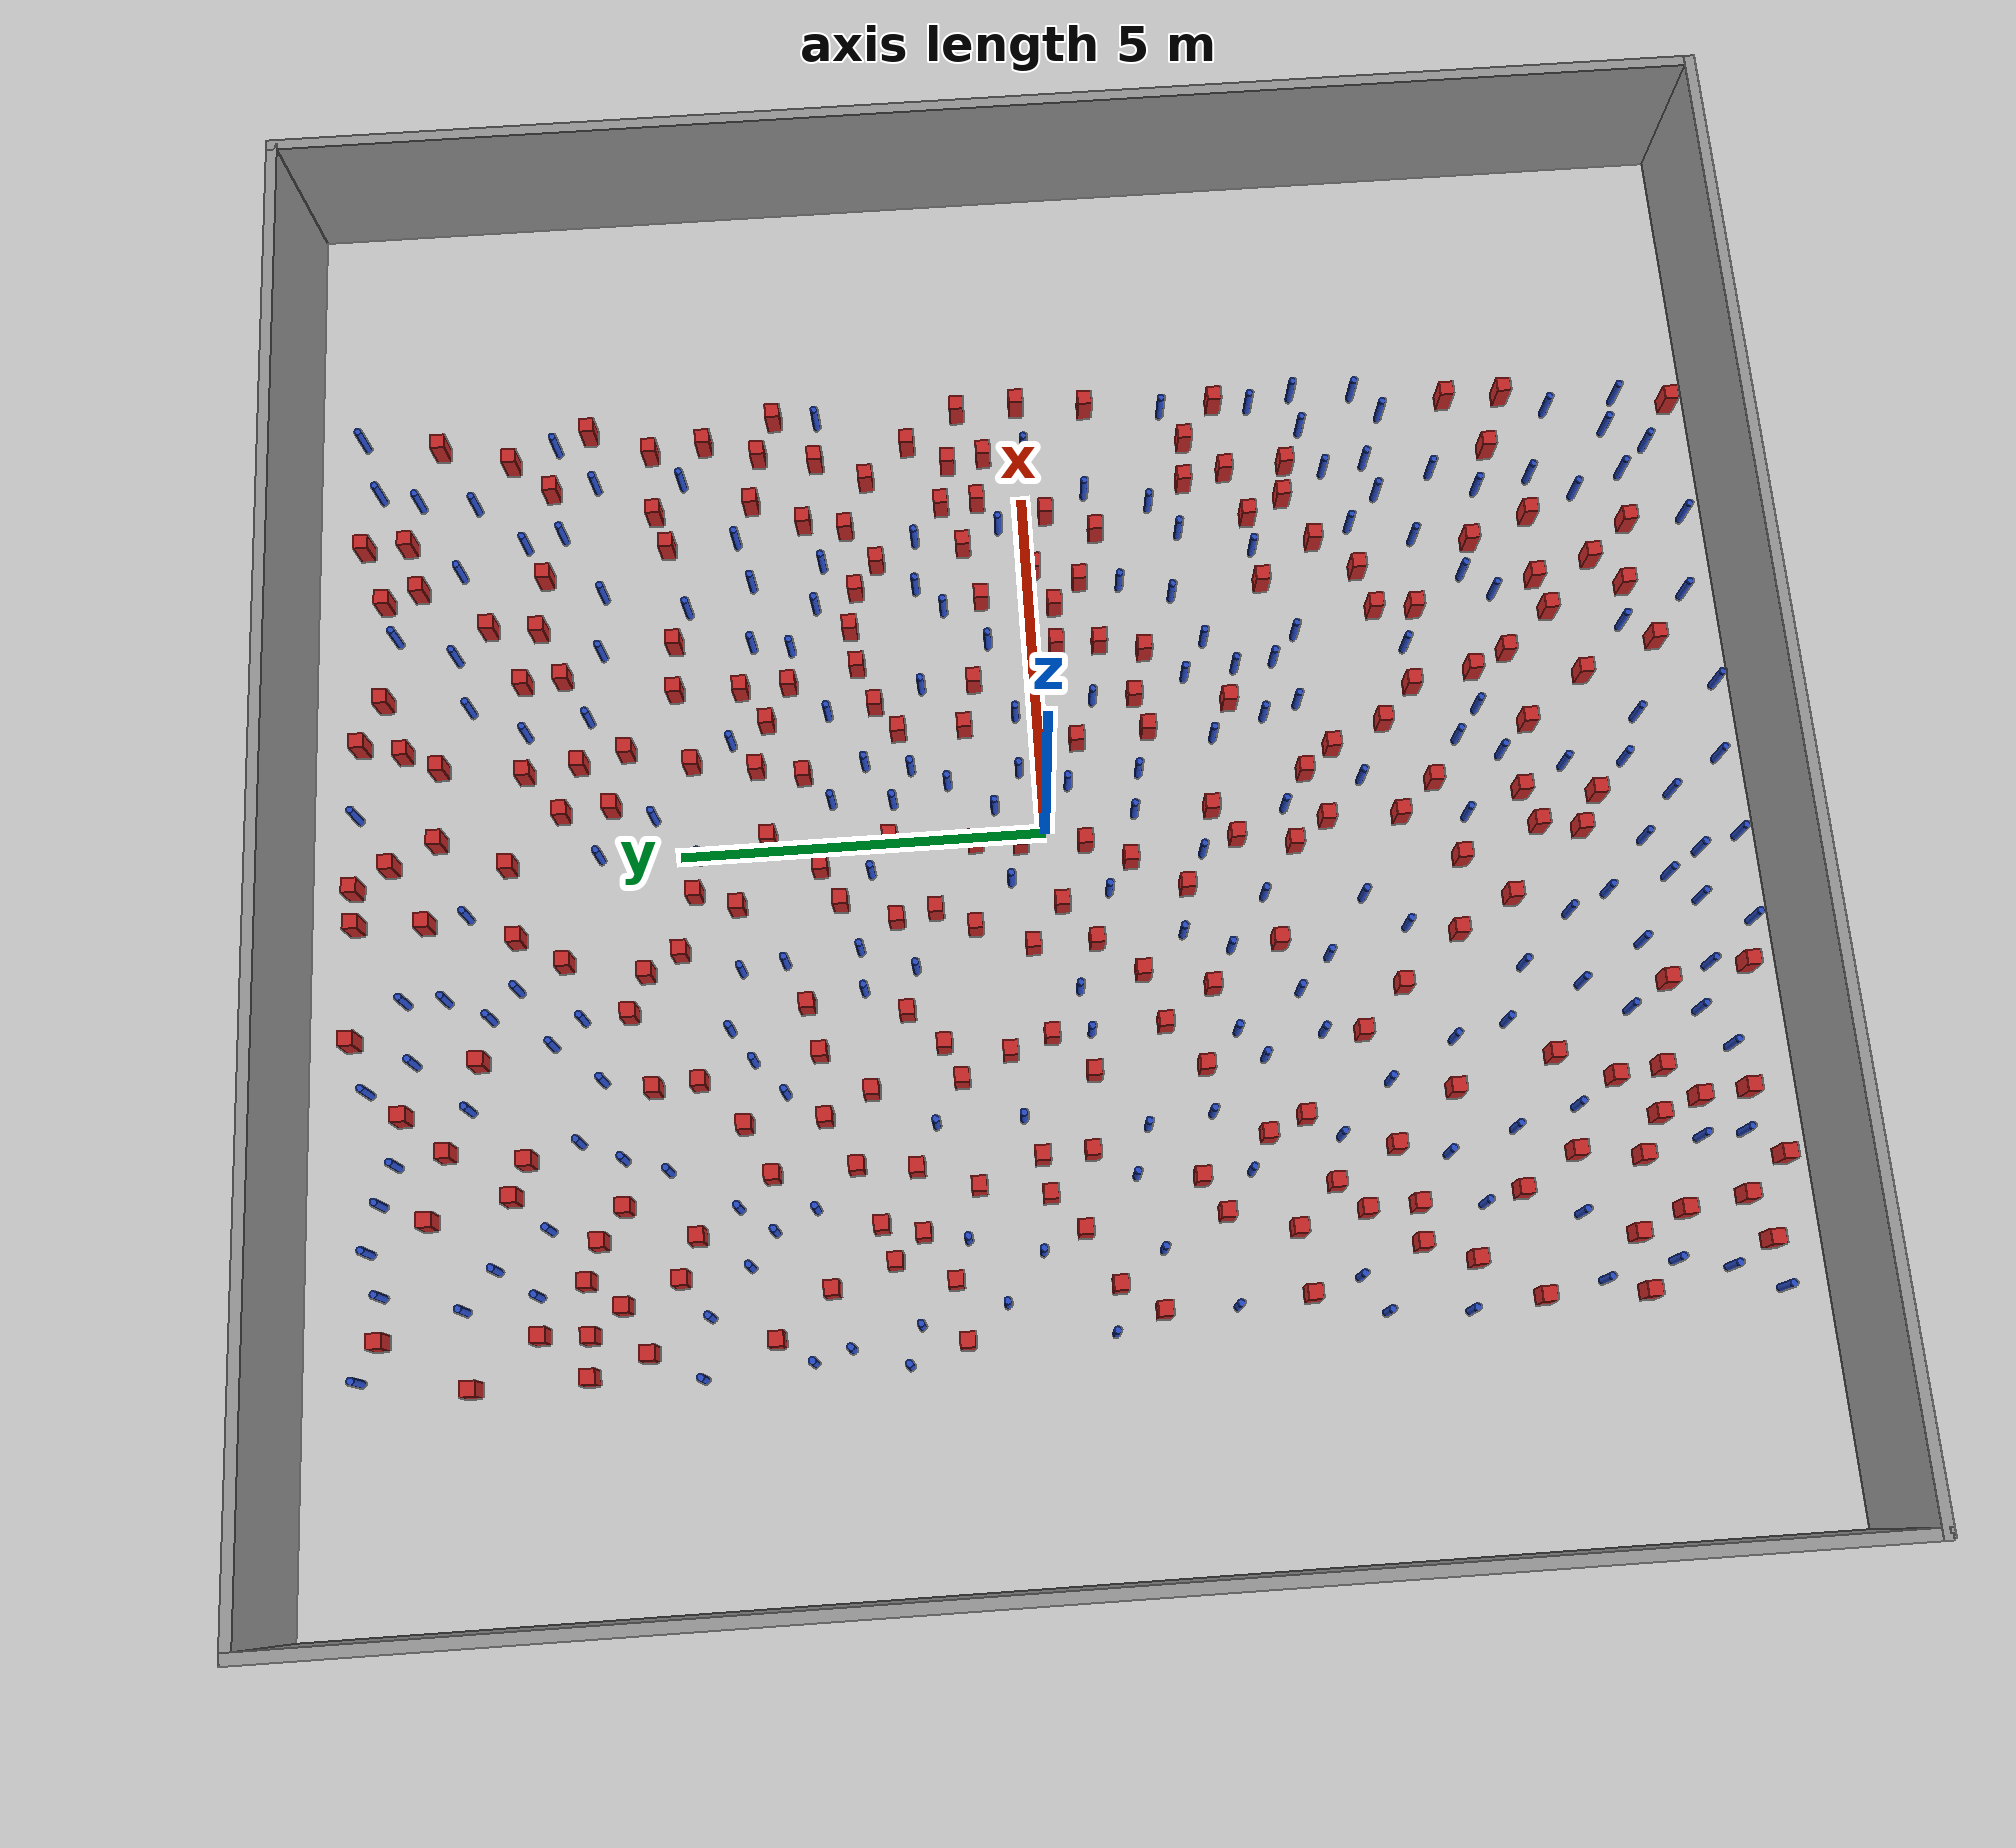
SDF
<sdf version="1.6">
 <world name="default">
  <light name="sun" type="directional">
   <pose>0 0 1000 0 -0 0</pose>
   <diffuse>0.8 0.8 0.8 1</diffuse>
   <specular>0.1 0.1 0.1 1</specular>
   <attenuation>
    <range>1000</range>
    <constant>0.9</constant>
    <linear>0.01</linear>
    <quadratic>0.001</quadratic>
   </attenuation>
   <direction>-0.5 0.5 -1</direction>
  </light>
  <model name="ground_plane">
   <static>1</static>
   <link name="link">
    <collision name="collision">
     <geometry><plane><normal>0 0 1</normal><size>100 100</size></plane></geometry>
     <surface><friction><ode><mu>100</mu><mu2>50</mu2></ode></friction></surface>
    </collision>
    <visual name="visual">
     <cast_shadows>0</cast_shadows>
     <geometry><plane><normal>0 0 1</normal><size>100 100</size></plane></geometry>
     <material>
      <ambient>1.0 1.0 1.0 1.0</ambient>
      <diffuse>0.8 0.8 0.8 1.0</diffuse>
      <specular>0.01 0.01 0.01 1.000000</specular>
     </material>
    </visual>
   </link>
  </model>
  <gravity>0 0 -9.8</gravity>
  <magnetic_field>6e-06 2.3e-05 -4.2e-05</magnetic_field>
  <atmosphere type="adiabatic"/>
  <physics name="default_physics" default="0" type="ode">
   <max_step_size>0.001</max_step_size>
   <real_time_factor>1</real_time_factor>
   <real_time_update_rate>1000</real_time_update_rate>
  </physics>
  <scene><ambient>0.4 0.4 0.4 1</ambient><background>0.7 0.7 0.7 1</background><shadows>1</shadows></scene>
  <spherical_coordinates>
   <surface_model>EARTH_WGS84</surface_model>
   <latitude_deg>0</latitude_deg>
   <longitude_deg>0</longitude_deg>
   <elevation>0</elevation>
   <heading_deg>0</heading_deg>
  </spherical_coordinates>
  <plugin name="gazebo_occupancy_map" filename="libgazebo_2Dmap_plugin.so">
   <map_resolution>0.05</map_resolution>
   <map_topic>generated_map</map_topic>
   <map_height>0.01</map_height>
   <map_size_x>50</map_size_x>
   <map_size_y>50</map_size_y>
  </plugin>
  <model name="NamedLocations">
   <static>true</static>
   <link name="DefaultStart"><pose>8.5 0 0 0 0 3.14</pose></link>
  </model>
  <model name="20x20_walls">
   <pose>0.044518 0.176112 0 0 -0 0</pose>
   <link name="Wall_1">
    <collision name="Wall_1_Collision">
     <geometry><box><size>20 0.15 2.5</size></box></geometry>
     <pose>0 0 1.25 0 -0 0</pose>
    </collision>
    <visual name="Wall_1_Visual">
     <pose>0 0 1.25 0 -0 0</pose>
     <geometry><box><size>20 0.15 2.5</size></box></geometry>
     <material>
      <script><uri>file://media/materials/scripts/gazebo.material</uri><name>Gazebo/Grey</name></script>
      <ambient>0.976471 0.992157 1 1</ambient>
     </material>
     <meta><layer>0</layer></meta>
    </visual>
    <pose>0 9.925 0 0 -0 0</pose>
   </link>
   <link name="Wall_3">
    <collision name="Wall_3_Collision">
     <geometry><box><size>20 0.15 2.5</size></box></geometry>
     <pose>0 0 1.25 0 -0 0</pose>
    </collision>
    <visual name="Wall_3_Visual">
     <pose>0 0 1.25 0 -0 0</pose>
     <geometry><box><size>20 0.15 2.5</size></box></geometry>
     <material>
      <script><uri>file://media/materials/scripts/gazebo.material</uri><name>Gazebo/Grey</name></script>
      <ambient>0.976471 0.992157 1 1</ambient>
     </material>
     <meta><layer>0</layer></meta>
    </visual>
    <pose>9.925 0 0 0 0 -1.5708</pose>
   </link>
   <link name="Wall_4">
    <collision name="Wall_4_Collision">
     <geometry><box><size>20 0.15 2.5</size></box></geometry>
     <pose>0 0 1.25 0 -0 0</pose>
    </collision>
    <visual name="Wall_4_Visual">
     <pose>0 0 1.25 0 -0 0</pose>
     <geometry><box><size>20 0.15 2.5</size></box></geometry>
     <material>
      <script><uri>file://media/materials/scripts/gazebo.material</uri><name>Gazebo/Grey</name></script>
      <ambient>0.976471 0.992157 1 1</ambient>
     </material>
     <meta><layer>0</layer></meta>
    </visual>
    <pose>0 -9.925 0 0 -0 3.14159</pose>
   </link>
   <link name="Wall_5">
    <collision name="Wall_5_Collision">
     <geometry><box><size>20 0.15 2.5</size></box></geometry>
     <pose>0 0 1.25 0 -0 0</pose>
    </collision>
    <visual name="Wall_5_Visual">
     <pose>0 0 1.25 0 -0 0</pose>
     <geometry><box><size>20 0.15 2.5</size></box></geometry>
     <material>
      <script><uri>file://media/materials/scripts/gazebo.material</uri><name>Gazebo/Grey</name></script>
      <ambient>0.976471 0.992157 1 1</ambient>
     </material>
     <meta><layer>0</layer></meta>
    </visual>
    <pose>-9.925 0 0 0 -0 1.5708</pose>
   </link>
   <static>1</static>
  </model>
  <model name="square_post_obstacle0">
   <static>true</static>
   <pose>3.88587274836 -6.28181637995 8.22691968438e-08 7.22125133819e-06 -7.54495500217e-07 2.29674213826e-05</pose>
   <link name="link">
    <pose>0 0 0.25 0 -0 0</pose>
    <inertial>
     <mass>100</mass>
     <inertia>
      <ixx>0.166667</ixx>
      <ixy>0</ixy>
      <ixz>0</ixz>
      <iyy>0.166667</iyy>
      <iyz>0</iyz>
      <izz>0.166667</izz>
     </inertia>
    </inertial>
    <collision name="collision"><geometry><box><size>.2 .2 .5</size></box></geometry></collision>
    <visual name="visual">
     <geometry><box><size>.2 .2 .5</size></box></geometry>
     <material>
      <script><name>Gazebo/Red</name><uri>file://media/materials/scripts/gazebo.material</uri></script>
     </material>
    </visual>
   </link>
  </model>
  <model name="square_post_obstacle1">
   <static>true</static>
   <pose>-5.03829176907 -3.4363562072 8.22691968438e-08 7.2212513382e-06 -7.54495500217e-07 2.29674213826e-05</pose>
   <link name="link">
    <pose>0 0 0.25 0 -0 0</pose>
    <inertial>
     <mass>100</mass>
     <inertia>
      <ixx>0.166667</ixx>
      <ixy>0</ixy>
      <ixz>0</ixz>
      <iyy>0.166667</iyy>
      <iyz>0</iyz>
      <izz>0.166667</izz>
     </inertia>
    </inertial>
    <collision name="collision"><geometry><box><size>.2 .2 .5</size></box></geometry></collision>
    <visual name="visual">
     <geometry><box><size>.2 .2 .5</size></box></geometry>
     <material>
      <script><name>Gazebo/Red</name><uri>file://media/materials/scripts/gazebo.material</uri></script>
     </material>
    </visual>
   </link>
  </model>
  <model name="pole_obstacle0">
   <static>true</static>
   <pose>-2.06327848858 2.57879154293 2.88873142074e-08 -9.90536690232e-09 4.6021994898e-07 -1.20965994968e-07</pose>
   <link name="link">
    <pose>0 0 0.3 0 -0 0</pose>
    <inertial>
     <mass>1</mass>
     <inertia><ixx>0.145833</ixx><ixy>0</ixy><ixz>0</ixz><iyy>0.145833</iyy><iyz>0</iyz><izz>0.125</izz></inertia>
    </inertial>
    <collision name="collision">
     <geometry><cylinder><radius>0.05</radius><length>.6</length></cylinder></geometry>
    </collision>
    <visual name="visual">
     <geometry><cylinder><radius>0.05</radius><length>.6</length></cylinder></geometry>
     <material>
      <script><name>Gazebo/Blue</name><uri>file://media/materials/scripts/gazebo.material</uri></script>
     </material>
    </visual>
   </link>
  </model>
  <model name="square_post_obstacle2">
   <static>true</static>
   <pose>-3.89636047755 -7.26375916254 8.22691968438e-08 7.2212513382e-06 -7.54495500217e-07 2.29674213826e-05</pose>
   <link name="link">
    <pose>0 0 0.25 0 -0 0</pose>
    <inertial>
     <mass>100</mass>
     <inertia>
      <ixx>0.166667</ixx>
      <ixy>0</ixy>
      <ixz>0</ixz>
      <iyy>0.166667</iyy>
      <iyz>0</iyz>
      <izz>0.166667</izz>
     </inertia>
    </inertial>
    <collision name="collision"><geometry><box><size>.2 .2 .5</size></box></geometry></collision>
    <visual name="visual">
     <geometry><box><size>.2 .2 .5</size></box></geometry>
     <material>
      <script><name>Gazebo/Red</name><uri>file://media/materials/scripts/gazebo.material</uri></script>
     </material>
    </visual>
   </link>
  </model>
  <model name="pole_obstacle1">
   <static>true</static>
   <pose>0.818938187911 9.38292226318 2.88873142074e-08 -9.90536690779e-09 4.60219948967e-07 -1.20965994975e-07</pose>
   <link name="link">
    <pose>0 0 0.3 0 -0 0</pose>
    <inertial>
     <mass>1</mass>
     <inertia><ixx>0.145833</ixx><ixy>0</ixy><ixz>0</ixz><iyy>0.145833</iyy><iyz>0</iyz><izz>0.125</izz></inertia>
    </inertial>
    <collision name="collision">
     <geometry><cylinder><radius>0.05</radius><length>.6</length></cylinder></geometry>
    </collision>
    <visual name="visual">
     <geometry><cylinder><radius>0.05</radius><length>.6</length></cylinder></geometry>
     <material>
      <script><name>Gazebo/Blue</name><uri>file://media/materials/scripts/gazebo.material</uri></script>
     </material>
    </visual>
   </link>
  </model>
  <model name="square_post_obstacle3">
   <static>true</static>
   <pose>-6.55645014747 3.90989048557 8.22691968438e-08 7.2212513382e-06 -7.54495500217e-07 2.29674213826e-05</pose>
   <link name="link">
    <pose>0 0 0.25 0 -0 0</pose>
    <inertial>
     <mass>100</mass>
     <inertia>
      <ixx>0.166667</ixx>
      <ixy>0</ixy>
      <ixz>0</ixz>
      <iyy>0.166667</iyy>
      <iyz>0</iyz>
      <izz>0.166667</izz>
     </inertia>
    </inertial>
    <collision name="collision"><geometry><box><size>.2 .2 .5</size></box></geometry></collision>
    <visual name="visual">
     <geometry><box><size>.2 .2 .5</size></box></geometry>
     <material>
      <script><name>Gazebo/Red</name><uri>file://media/materials/scripts/gazebo.material</uri></script>
     </material>
    </visual>
   </link>
  </model>
  <model name="pole_obstacle2">
   <static>true</static>
   <pose>-3.03560111655 -3.47882429792 2.88873142074e-08 -9.90536690232e-09 4.6021994898e-07 -1.20965994968e-07</pose>
   <link name="link">
    <pose>0 0 0.3 0 -0 0</pose>
    <inertial>
     <mass>1</mass>
     <inertia><ixx>0.145833</ixx><ixy>0</ixy><ixz>0</ixz><iyy>0.145833</iyy><iyz>0</iyz><izz>0.125</izz></inertia>
    </inertial>
    <collision name="collision">
     <geometry><cylinder><radius>0.05</radius><length>.6</length></cylinder></geometry>
    </collision>
    <visual name="visual">
     <geometry><cylinder><radius>0.05</radius><length>.6</length></cylinder></geometry>
     <material>
      <script><name>Gazebo/Blue</name><uri>file://media/materials/scripts/gazebo.material</uri></script>
     </material>
    </visual>
   </link>
  </model>
  <model name="pole_obstacle3">
   <static>true</static>
   <pose>1.12006407967 2.42599292531 2.88873142074e-08 -9.90536689791e-09 4.6021994899e-07 -1.20965994959e-07</pose>
   <link name="link">
    <pose>0 0 0.3 0 -0 0</pose>
    <inertial>
     <mass>1</mass>
     <inertia><ixx>0.145833</ixx><ixy>0</ixy><ixz>0</ixz><iyy>0.145833</iyy><iyz>0</iyz><izz>0.125</izz></inertia>
    </inertial>
    <collision name="collision">
     <geometry><cylinder><radius>0.05</radius><length>.6</length></cylinder></geometry>
    </collision>
    <visual name="visual">
     <geometry><cylinder><radius>0.05</radius><length>.6</length></cylinder></geometry>
     <material>
      <script><name>Gazebo/Blue</name><uri>file://media/materials/scripts/gazebo.material</uri></script>
     </material>
    </visual>
   </link>
  </model>
  <model name="square_post_obstacle4">
   <static>true</static>
   <pose>-2.48618194131 -9.25337838054 8.22691968438e-08 7.22125133819e-06 -7.54495500217e-07 2.29674213826e-05</pose>
   <link name="link">
    <pose>0 0 0.25 0 -0 0</pose>
    <inertial>
     <mass>100</mass>
     <inertia>
      <ixx>0.166667</ixx>
      <ixy>0</ixy>
      <ixz>0</ixz>
      <iyy>0.166667</iyy>
      <iyz>0</iyz>
      <izz>0.166667</izz>
     </inertia>
    </inertial>
    <collision name="collision"><geometry><box><size>.2 .2 .5</size></box></geometry></collision>
    <visual name="visual">
     <geometry><box><size>.2 .2 .5</size></box></geometry>
     <material>
      <script><name>Gazebo/Red</name><uri>file://media/materials/scripts/gazebo.material</uri></script>
     </material>
    </visual>
   </link>
  </model>
  <model name="square_post_obstacle5">
   <static>true</static>
   <pose>5.25231052275 -3.78582455542 8.22691968438e-08 7.2212513382e-06 -7.54495500217e-07 2.29674213826e-05</pose>
   <link name="link">
    <pose>0 0 0.25 0 -0 0</pose>
    <inertial>
     <mass>100</mass>
     <inertia>
      <ixx>0.166667</ixx>
      <ixy>0</ixy>
      <ixz>0</ixz>
      <iyy>0.166667</iyy>
      <iyz>0</iyz>
      <izz>0.166667</izz>
     </inertia>
    </inertial>
    <collision name="collision"><geometry><box><size>.2 .2 .5</size></box></geometry></collision>
    <visual name="visual">
     <geometry><box><size>.2 .2 .5</size></box></geometry>
     <material>
      <script><name>Gazebo/Red</name><uri>file://media/materials/scripts/gazebo.material</uri></script>
     </material>
    </visual>
   </link>
  </model>
  <model name="square_post_obstacle6">
   <static>true</static>
   <pose>-4.39942618773 2.79059757768 8.22691968438e-08 7.2212513382e-06 -7.54495500217e-07 2.29674213826e-05</pose>
   <link name="link">
    <pose>0 0 0.25 0 -0 0</pose>
    <inertial>
     <mass>100</mass>
     <inertia>
      <ixx>0.166667</ixx>
      <ixy>0</ixy>
      <ixz>0</ixz>
      <iyy>0.166667</iyy>
      <iyz>0</iyz>
      <izz>0.166667</izz>
     </inertia>
    </inertial>
    <collision name="collision"><geometry><box><size>.2 .2 .5</size></box></geometry></collision>
    <visual name="visual">
     <geometry><box><size>.2 .2 .5</size></box></geometry>
     <material>
      <script><name>Gazebo/Red</name><uri>file://media/materials/scripts/gazebo.material</uri></script>
     </material>
    </visual>
   </link>
  </model>
  <model name="pole_obstacle4">
   <static>true</static>
   <pose>-5.45214630554 1.39098894112 2.88873142074e-08 -9.90536689445e-09 4.60219948999e-07 -1.20965994956e-07</pose>
   <link name="link">
    <pose>0 0 0.3 0 -0 0</pose>
    <inertial>
     <mass>1</mass>
     <inertia><ixx>0.145833</ixx><ixy>0</ixy><ixz>0</ixz><iyy>0.145833</iyy><iyz>0</iyz><izz>0.125</izz></inertia>
    </inertial>
    <collision name="collision">
     <geometry><cylinder><radius>0.05</radius><length>.6</length></cylinder></geometry>
    </collision>
    <visual name="visual">
     <geometry><cylinder><radius>0.05</radius><length>.6</length></cylinder></geometry>
     <material>
      <script><name>Gazebo/Blue</name><uri>file://media/materials/scripts/gazebo.material</uri></script>
     </material>
    </visual>
   </link>
  </model>
  <model name="pole_obstacle5">
   <static>true</static>
   <pose>-6.3331540744 -7.70402549706 2.88873142074e-08 -9.90536690842e-09 4.60219948965e-07 -1.20965994976e-07</pose>
   <link name="link">
    <pose>0 0 0.3 0 -0 0</pose>
    <inertial>
     <mass>1</mass>
     <inertia><ixx>0.145833</ixx><ixy>0</ixy><ixz>0</ixz><iyy>0.145833</iyy><iyz>0</iyz><izz>0.125</izz></inertia>
    </inertial>
    <collision name="collision">
     <geometry><cylinder><radius>0.05</radius><length>.6</length></cylinder></geometry>
    </collision>
    <visual name="visual">
     <geometry><cylinder><radius>0.05</radius><length>.6</length></cylinder></geometry>
     <material>
      <script><name>Gazebo/Blue</name><uri>file://media/materials/scripts/gazebo.material</uri></script>
     </material>
    </visual>
   </link>
  </model>
  <model name="square_post_obstacle7">
   <static>true</static>
   <pose>4.39493751588 -0.99961755812 8.22691968438e-08 7.2212513382e-06 -7.54495500217e-07 2.29674213826e-05</pose>
   <link name="link">
    <pose>0 0 0.25 0 -0 0</pose>
    <inertial>
     <mass>100</mass>
     <inertia>
      <ixx>0.166667</ixx>
      <ixy>0</ixy>
      <ixz>0</ixz>
      <iyy>0.166667</iyy>
      <iyz>0</iyz>
      <izz>0.166667</izz>
     </inertia>
    </inertial>
    <collision name="collision"><geometry><box><size>.2 .2 .5</size></box></geometry></collision>
    <visual name="visual">
     <geometry><box><size>.2 .2 .5</size></box></geometry>
     <material>
      <script><name>Gazebo/Red</name><uri>file://media/materials/scripts/gazebo.material</uri></script>
     </material>
    </visual>
   </link>
  </model>
  <model name="square_post_obstacle8">
   <static>true</static>
   <pose>-3.87123979562 8.14785014603 8.22691968438e-08 7.22125133819e-06 -7.54495500217e-07 2.29674213826e-05</pose>
   <link name="link">
    <pose>0 0 0.25 0 -0 0</pose>
    <inertial>
     <mass>100</mass>
     <inertia>
      <ixx>0.166667</ixx>
      <ixy>0</ixy>
      <ixz>0</ixz>
      <iyy>0.166667</iyy>
      <iyz>0</iyz>
      <izz>0.166667</izz>
     </inertia>
    </inertial>
    <collision name="collision"><geometry><box><size>.2 .2 .5</size></box></geometry></collision>
    <visual name="visual">
     <geometry><box><size>.2 .2 .5</size></box></geometry>
     <material>
      <script><name>Gazebo/Red</name><uri>file://media/materials/scripts/gazebo.material</uri></script>
     </material>
    </visual>
   </link>
  </model>
  <model name="pole_obstacle6">
   <static>true</static>
   <pose>-3.38358671933 3.67532625246 2.88873142074e-08 -9.90536690232e-09 4.6021994898e-07 -1.20965994968e-07</pose>
   <link name="link">
    <pose>0 0 0.3 0 -0 0</pose>
    <inertial>
     <mass>1</mass>
     <inertia><ixx>0.145833</ixx><ixy>0</ixy><ixz>0</ixz><iyy>0.145833</iyy><iyz>0</iyz><izz>0.125</izz></inertia>
    </inertial>
    <collision name="collision">
     <geometry><cylinder><radius>0.05</radius><length>.6</length></cylinder></geometry>
    </collision>
    <visual name="visual">
     <geometry><cylinder><radius>0.05</radius><length>.6</length></cylinder></geometry>
     <material>
      <script><name>Gazebo/Blue</name><uri>file://media/materials/scripts/gazebo.material</uri></script>
     </material>
    </visual>
   </link>
  </model>
  <model name="pole_obstacle7">
   <static>true</static>
   <pose>-1.61402399077 3.61474641128 2.88873142074e-08 -9.90536689791e-09 4.6021994899e-07 -1.20965994959e-07</pose>
   <link name="link">
    <pose>0 0 0.3 0 -0 0</pose>
    <inertial>
     <mass>1</mass>
     <inertia><ixx>0.145833</ixx><ixy>0</ixy><ixz>0</ixz><iyy>0.145833</iyy><iyz>0</iyz><izz>0.125</izz></inertia>
    </inertial>
    <collision name="collision">
     <geometry><cylinder><radius>0.05</radius><length>.6</length></cylinder></geometry>
    </collision>
    <visual name="visual">
     <geometry><cylinder><radius>0.05</radius><length>.6</length></cylinder></geometry>
     <material>
      <script><name>Gazebo/Blue</name><uri>file://media/materials/scripts/gazebo.material</uri></script>
     </material>
    </visual>
   </link>
  </model>
  <model name="square_post_obstacle9">
   <static>true</static>
   <pose>-0.449228527882 -7.28937916096 8.22691968438e-08 7.22125133819e-06 -7.54495500217e-07 2.29674213826e-05</pose>
   <link name="link">
    <pose>0 0 0.25 0 -0 0</pose>
    <inertial>
     <mass>100</mass>
     <inertia>
      <ixx>0.166667</ixx>
      <ixy>0</ixy>
      <ixz>0</ixz>
      <iyy>0.166667</iyy>
      <iyz>0</iyz>
      <izz>0.166667</izz>
     </inertia>
    </inertial>
    <collision name="collision"><geometry><box><size>.2 .2 .5</size></box></geometry></collision>
    <visual name="visual">
     <geometry><box><size>.2 .2 .5</size></box></geometry>
     <material>
      <script><name>Gazebo/Red</name><uri>file://media/materials/scripts/gazebo.material</uri></script>
     </material>
    </visual>
   </link>
  </model>
  <model name="square_post_obstacle10">
   <static>true</static>
   <pose>3.07662224585 4.99544792653 8.22691968438e-08 7.2212513382e-06 -7.54495500217e-07 2.29674213826e-05</pose>
   <link name="link">
    <pose>0 0 0.25 0 -0 0</pose>
    <inertial>
     <mass>100</mass>
     <inertia>
      <ixx>0.166667</ixx>
      <ixy>0</ixy>
      <ixz>0</ixz>
      <iyy>0.166667</iyy>
      <iyz>0</iyz>
      <izz>0.166667</izz>
     </inertia>
    </inertial>
    <collision name="collision"><geometry><box><size>.2 .2 .5</size></box></geometry></collision>
    <visual name="visual">
     <geometry><box><size>.2 .2 .5</size></box></geometry>
     <material>
      <script><name>Gazebo/Red</name><uri>file://media/materials/scripts/gazebo.material</uri></script>
     </material>
    </visual>
   </link>
  </model>
  <model name="square_post_obstacle11">
   <static>true</static>
   <pose>-5.96716999815 3.17955191712 8.22691968438e-08 7.2212513382e-06 -7.54495500217e-07 2.29674213826e-05</pose>
   <link name="link">
    <pose>0 0 0.25 0 -0 0</pose>
    <inertial>
     <mass>100</mass>
     <inertia>
      <ixx>0.166667</ixx>
      <ixy>0</ixy>
      <ixz>0</ixz>
      <iyy>0.166667</iyy>
      <iyz>0</iyz>
      <izz>0.166667</izz>
     </inertia>
    </inertial>
    <collision name="collision"><geometry><box><size>.2 .2 .5</size></box></geometry></collision>
    <visual name="visual">
     <geometry><box><size>.2 .2 .5</size></box></geometry>
     <material>
      <script><name>Gazebo/Red</name><uri>file://media/materials/scripts/gazebo.material</uri></script>
     </material>
    </visual>
   </link>
  </model>
  <model name="square_post_obstacle12">
   <static>true</static>
   <pose>-6.15789999557 -8.98425494917 8.22691968438e-08 7.22125133819e-06 -7.54495500217e-07 2.29674213826e-05</pose>
   <link name="link">
    <pose>0 0 0.25 0 -0 0</pose>
    <inertial>
     <mass>100</mass>
     <inertia>
      <ixx>0.166667</ixx>
      <ixy>0</ixy>
      <ixz>0</ixz>
      <iyy>0.166667</iyy>
      <iyz>0</iyz>
      <izz>0.166667</izz>
     </inertia>
    </inertial>
    <collision name="collision"><geometry><box><size>.2 .2 .5</size></box></geometry></collision>
    <visual name="visual">
     <geometry><box><size>.2 .2 .5</size></box></geometry>
     <material>
      <script><name>Gazebo/Red</name><uri>file://media/materials/scripts/gazebo.material</uri></script>
     </material>
    </visual>
   </link>
  </model>
  <model name="square_post_obstacle13">
   <static>true</static>
   <pose>-2.82691644782 0.126163926508 8.22691968438e-08 7.2212513382e-06 -7.54495500217e-07 2.29674213826e-05</pose>
   <link name="link">
    <pose>0 0 0.25 0 -0 0</pose>
    <inertial>
     <mass>100</mass>
     <inertia>
      <ixx>0.166667</ixx>
      <ixy>0</ixy>
      <ixz>0</ixz>
      <iyy>0.166667</iyy>
      <iyz>0</iyz>
      <izz>0.166667</izz>
     </inertia>
    </inertial>
    <collision name="collision"><geometry><box><size>.2 .2 .5</size></box></geometry></collision>
    <visual name="visual">
     <geometry><box><size>.2 .2 .5</size></box></geometry>
     <material>
      <script><name>Gazebo/Red</name><uri>file://media/materials/scripts/gazebo.material</uri></script>
     </material>
    </visual>
   </link>
  </model>
  <model name="pole_obstacle8">
   <static>true</static>
   <pose>3.5580969233 -1.27488062741 2.88873142074e-08 -9.90536689395e-09 4.60219949e-07 -1.20965994953e-07</pose>
   <link name="link">
    <pose>0 0 0.3 0 -0 0</pose>
    <inertial>
     <mass>1</mass>
     <inertia><ixx>0.145833</ixx><ixy>0</ixy><ixz>0</ixz><iyy>0.145833</iyy><iyz>0</iyz><izz>0.125</izz></inertia>
    </inertial>
    <collision name="collision">
     <geometry><cylinder><radius>0.05</radius><length>.6</length></cylinder></geometry>
    </collision>
    <visual name="visual">
     <geometry><cylinder><radius>0.05</radius><length>.6</length></cylinder></geometry>
     <material>
      <script><name>Gazebo/Blue</name><uri>file://media/materials/scripts/gazebo.material</uri></script>
     </material>
    </visual>
   </link>
  </model>
  <model name="square_post_obstacle14">
   <static>true</static>
   <pose>5.66487133897 0.518670508902 8.22691968438e-08 7.2212513382e-06 -7.54495500217e-07 2.29674213826e-05</pose>
   <link name="link">
    <pose>0 0 0.25 0 -0 0</pose>
    <inertial>
     <mass>100</mass>
     <inertia>
      <ixx>0.166667</ixx>
      <ixy>0</ixy>
      <ixz>0</ixz>
      <iyy>0.166667</iyy>
      <iyz>0</iyz>
      <izz>0.166667</izz>
     </inertia>
    </inertial>
    <collision name="collision"><geometry><box><size>.2 .2 .5</size></box></geometry></collision>
    <visual name="visual">
     <geometry><box><size>.2 .2 .5</size></box></geometry>
     <material>
      <script><name>Gazebo/Red</name><uri>file://media/materials/scripts/gazebo.material</uri></script>
     </material>
    </visual>
   </link>
  </model>
  <model name="square_post_obstacle15">
   <static>true</static>
   <pose>-4.6053324093 -4.27422542623 8.22691968438e-08 7.22125133819e-06 -7.54495500217e-07 2.29674213826e-05</pose>
   <link name="link">
    <pose>0 0 0.25 0 -0 0</pose>
    <inertial>
     <mass>100</mass>
     <inertia>
      <ixx>0.166667</ixx>
      <ixy>0</ixy>
      <ixz>0</ixz>
      <iyy>0.166667</iyy>
      <iyz>0</iyz>
      <izz>0.166667</izz>
     </inertia>
    </inertial>
    <collision name="collision"><geometry><box><size>.2 .2 .5</size></box></geometry></collision>
    <visual name="visual">
     <geometry><box><size>.2 .2 .5</size></box></geometry>
     <material>
      <script><name>Gazebo/Red</name><uri>file://media/materials/scripts/gazebo.material</uri></script>
     </material>
    </visual>
   </link>
  </model>
  <model name="square_post_obstacle16">
   <static>true</static>
   <pose>0.372748697195 -5.35796301206 8.22691968438e-08 7.22125133819e-06 -7.54495500217e-07 2.29674213826e-05</pose>
   <link name="link">
    <pose>0 0 0.25 0 -0 0</pose>
    <inertial>
     <mass>100</mass>
     <inertia>
      <ixx>0.166667</ixx>
      <ixy>0</ixy>
      <ixz>0</ixz>
      <iyy>0.166667</iyy>
      <iyz>0</iyz>
      <izz>0.166667</izz>
     </inertia>
    </inertial>
    <collision name="collision"><geometry><box><size>.2 .2 .5</size></box></geometry></collision>
    <visual name="visual">
     <geometry><box><size>.2 .2 .5</size></box></geometry>
     <material>
      <script><name>Gazebo/Red</name><uri>file://media/materials/scripts/gazebo.material</uri></script>
     </material>
    </visual>
   </link>
  </model>
  <model name="pole_obstacle9">
   <static>true</static>
   <pose>4.54602831759 0.370276990639 2.88873142074e-08 -9.90536689981e-09 4.60219948986e-07 -1.20965994962e-07</pose>
   <link name="link">
    <pose>0 0 0.3 0 -0 0</pose>
    <inertial>
     <mass>1</mass>
     <inertia><ixx>0.145833</ixx><ixy>0</ixy><ixz>0</ixz><iyy>0.145833</iyy><iyz>0</iyz><izz>0.125</izz></inertia>
    </inertial>
    <collision name="collision">
     <geometry><cylinder><radius>0.05</radius><length>.6</length></cylinder></geometry>
    </collision>
    <visual name="visual">
     <geometry><cylinder><radius>0.05</radius><length>.6</length></cylinder></geometry>
     <material>
      <script><name>Gazebo/Blue</name><uri>file://media/materials/scripts/gazebo.material</uri></script>
     </material>
    </visual>
   </link>
  </model>
  <model name="square_post_obstacle17">
   <static>true</static>
   <pose>-1.27304721057 1.04541945951 8.22691968438e-08 7.2212513382e-06 -7.54495500217e-07 2.29674213826e-05</pose>
   <link name="link">
    <pose>0 0 0.25 0 -0 0</pose>
    <inertial>
     <mass>100</mass>
     <inertia>
      <ixx>0.166667</ixx>
      <ixy>0</ixy>
      <ixz>0</ixz>
      <iyy>0.166667</iyy>
      <iyz>0</iyz>
      <izz>0.166667</izz>
     </inertia>
    </inertial>
    <collision name="collision"><geometry><box><size>.2 .2 .5</size></box></geometry></collision>
    <visual name="visual">
     <geometry><box><size>.2 .2 .5</size></box></geometry>
     <material>
      <script><name>Gazebo/Red</name><uri>file://media/materials/scripts/gazebo.material</uri></script>
     </material>
    </visual>
   </link>
  </model>
  <model name="square_post_obstacle18">
   <static>true</static>
   <pose>-3.41731523094 2.54991791525 8.22691968438e-08 7.2212513382e-06 -7.54495500217e-07 2.29674213826e-05</pose>
   <link name="link">
    <pose>0 0 0.25 0 -0 0</pose>
    <inertial>
     <mass>100</mass>
     <inertia>
      <ixx>0.166667</ixx>
      <ixy>0</ixy>
      <ixz>0</ixz>
      <iyy>0.166667</iyy>
      <iyz>0</iyz>
      <izz>0.166667</izz>
     </inertia>
    </inertial>
    <collision name="collision"><geometry><box><size>.2 .2 .5</size></box></geometry></collision>
    <visual name="visual">
     <geometry><box><size>.2 .2 .5</size></box></geometry>
     <material>
      <script><name>Gazebo/Red</name><uri>file://media/materials/scripts/gazebo.material</uri></script>
     </material>
    </visual>
   </link>
  </model>
  <model name="pole_obstacle10">
   <static>true</static>
   <pose>-4.76662883871 -0.850750414074 2.88873142074e-08 -9.90536689837e-09 4.60219948989e-07 -1.2096599496e-07</pose>
   <link name="link">
    <pose>0 0 0.3 0 -0 0</pose>
    <inertial>
     <mass>1</mass>
     <inertia><ixx>0.145833</ixx><ixy>0</ixy><ixz>0</ixz><iyy>0.145833</iyy><iyz>0</iyz><izz>0.125</izz></inertia>
    </inertial>
    <collision name="collision">
     <geometry><cylinder><radius>0.05</radius><length>.6</length></cylinder></geometry>
    </collision>
    <visual name="visual">
     <geometry><cylinder><radius>0.05</radius><length>.6</length></cylinder></geometry>
     <material>
      <script><name>Gazebo/Blue</name><uri>file://media/materials/scripts/gazebo.material</uri></script>
     </material>
    </visual>
   </link>
  </model>
  <model name="square_post_obstacle19">
   <static>true</static>
   <pose>0.696296038342 6.5946302493 8.22691968438e-08 7.2212513382e-06 -7.54495500217e-07 2.29674213826e-05</pose>
   <link name="link">
    <pose>0 0 0.25 0 -0 0</pose>
    <inertial>
     <mass>100</mass>
     <inertia>
      <ixx>0.166667</ixx>
      <ixy>0</ixy>
      <ixz>0</ixz>
      <iyy>0.166667</iyy>
      <iyz>0</iyz>
      <izz>0.166667</izz>
     </inertia>
    </inertial>
    <collision name="collision"><geometry><box><size>.2 .2 .5</size></box></geometry></collision>
    <visual name="visual">
     <geometry><box><size>.2 .2 .5</size></box></geometry>
     <material>
      <script><name>Gazebo/Red</name><uri>file://media/materials/scripts/gazebo.material</uri></script>
     </material>
    </visual>
   </link>
  </model>
  <model name="pole_obstacle11">
   <static>true</static>
   <pose>-0.662988003592 -8.11105628578 2.88873142074e-08 -9.90536690779e-09 4.60219948967e-07 -1.20965994975e-07</pose>
   <link name="link">
    <pose>0 0 0.3 0 -0 0</pose>
    <inertial>
     <mass>1</mass>
     <inertia><ixx>0.145833</ixx><ixy>0</ixy><ixz>0</ixz><iyy>0.145833</iyy><iyz>0</iyz><izz>0.125</izz></inertia>
    </inertial>
    <collision name="collision">
     <geometry><cylinder><radius>0.05</radius><length>.6</length></cylinder></geometry>
    </collision>
    <visual name="visual">
     <geometry><cylinder><radius>0.05</radius><length>.6</length></cylinder></geometry>
     <material>
      <script><name>Gazebo/Blue</name><uri>file://media/materials/scripts/gazebo.material</uri></script>
     </material>
    </visual>
   </link>
  </model>
  <model name="square_post_obstacle20">
   <static>true</static>
   <pose>-0.0746601059018 -3.83380512901 8.22691968438e-08 7.2212513382e-06 -7.54495500217e-07 2.29674213826e-05</pose>
   <link name="link">
    <pose>0 0 0.25 0 -0 0</pose>
    <inertial>
     <mass>100</mass>
     <inertia>
      <ixx>0.166667</ixx>
      <ixy>0</ixy>
      <ixz>0</ixz>
      <iyy>0.166667</iyy>
      <iyz>0</iyz>
      <izz>0.166667</izz>
     </inertia>
    </inertial>
    <collision name="collision"><geometry><box><size>.2 .2 .5</size></box></geometry></collision>
    <visual name="visual">
     <geometry><box><size>.2 .2 .5</size></box></geometry>
     <material>
      <script><name>Gazebo/Red</name><uri>file://media/materials/scripts/gazebo.material</uri></script>
     </material>
    </visual>
   </link>
  </model>
  <model name="pole_obstacle12">
   <static>true</static>
   <pose>-2.11108152988 -7.86755441198 2.88873142074e-08 -9.90536689859e-09 4.60219948989e-07 -1.20965994961e-07</pose>
   <link name="link">
    <pose>0 0 0.3 0 -0 0</pose>
    <inertial>
     <mass>1</mass>
     <inertia><ixx>0.145833</ixx><ixy>0</ixy><ixz>0</ixz><iyy>0.145833</iyy><iyz>0</iyz><izz>0.125</izz></inertia>
    </inertial>
    <collision name="collision">
     <geometry><cylinder><radius>0.05</radius><length>.6</length></cylinder></geometry>
    </collision>
    <visual name="visual">
     <geometry><cylinder><radius>0.05</radius><length>.6</length></cylinder></geometry>
     <material>
      <script><name>Gazebo/Blue</name><uri>file://media/materials/scripts/gazebo.material</uri></script>
     </material>
    </visual>
   </link>
  </model>
  <model name="square_post_obstacle21">
   <static>true</static>
   <pose>0.0914691414872 8.92870922852 8.22691968438e-08 7.22125133819e-06 -7.54495500217e-07 2.29674213826e-05</pose>
   <link name="link">
    <pose>0 0 0.25 0 -0 0</pose>
    <inertial>
     <mass>100</mass>
     <inertia>
      <ixx>0.166667</ixx>
      <ixy>0</ixy>
      <ixz>0</ixz>
      <iyy>0.166667</iyy>
      <iyz>0</iyz>
      <izz>0.166667</izz>
     </inertia>
    </inertial>
    <collision name="collision"><geometry><box><size>.2 .2 .5</size></box></geometry></collision>
    <visual name="visual">
     <geometry><box><size>.2 .2 .5</size></box></geometry>
     <material>
      <script><name>Gazebo/Red</name><uri>file://media/materials/scripts/gazebo.material</uri></script>
     </material>
    </visual>
   </link>
  </model>
  <model name="pole_obstacle13">
   <static>true</static>
   <pose>-6.76908547282 -9.04808310177 2.88873142074e-08 -9.9053668967e-09 4.60219948993e-07 -1.20965994957e-07</pose>
   <link name="link">
    <pose>0 0 0.3 0 -0 0</pose>
    <inertial>
     <mass>1</mass>
     <inertia><ixx>0.145833</ixx><ixy>0</ixy><ixz>0</ixz><iyy>0.145833</iyy><iyz>0</iyz><izz>0.125</izz></inertia>
    </inertial>
    <collision name="collision">
     <geometry><cylinder><radius>0.05</radius><length>.6</length></cylinder></geometry>
    </collision>
    <visual name="visual">
     <geometry><cylinder><radius>0.05</radius><length>.6</length></cylinder></geometry>
     <material>
      <script><name>Gazebo/Blue</name><uri>file://media/materials/scripts/gazebo.material</uri></script>
     </material>
    </visual>
   </link>
  </model>
  <model name="square_post_obstacle22">
   <static>true</static>
   <pose>1.78787143359 -7.61190881936 8.22691968438e-08 7.2212513382e-06 -7.54495500217e-07 2.29674213826e-05</pose>
   <link name="link">
    <pose>0 0 0.25 0 -0 0</pose>
    <inertial>
     <mass>100</mass>
     <inertia>
      <ixx>0.166667</ixx>
      <ixy>0</ixy>
      <ixz>0</ixz>
      <iyy>0.166667</iyy>
      <iyz>0</iyz>
      <izz>0.166667</izz>
     </inertia>
    </inertial>
    <collision name="collision"><geometry><box><size>.2 .2 .5</size></box></geometry></collision>
    <visual name="visual">
     <geometry><box><size>.2 .2 .5</size></box></geometry>
     <material>
      <script><name>Gazebo/Red</name><uri>file://media/materials/scripts/gazebo.material</uri></script>
     </material>
    </visual>
   </link>
  </model>
  <model name="pole_obstacle14">
   <static>true</static>
   <pose>-4.43251508346 -3.57022611527 2.88873142074e-08 -9.90536690245e-09 4.6021994898e-07 -1.20965994966e-07</pose>
   <link name="link">
    <pose>0 0 0.3 0 -0 0</pose>
    <inertial>
     <mass>1</mass>
     <inertia><ixx>0.145833</ixx><ixy>0</ixy><ixz>0</ixz><iyy>0.145833</iyy><iyz>0</iyz><izz>0.125</izz></inertia>
    </inertial>
    <collision name="collision">
     <geometry><cylinder><radius>0.05</radius><length>.6</length></cylinder></geometry>
    </collision>
    <visual name="visual">
     <geometry><cylinder><radius>0.05</radius><length>.6</length></cylinder></geometry>
     <material>
      <script><name>Gazebo/Blue</name><uri>file://media/materials/scripts/gazebo.material</uri></script>
     </material>
    </visual>
   </link>
  </model>
  <model name="pole_obstacle15">
   <static>true</static>
   <pose>-3.24683174081 -5.19850735674 2.88873142074e-08 -9.90536689859e-09 4.60219948989e-07 -1.20965994961e-07</pose>
   <link name="link">
    <pose>0 0 0.3 0 -0 0</pose>
    <inertial>
     <mass>1</mass>
     <inertia><ixx>0.145833</ixx><ixy>0</ixy><ixz>0</ixz><iyy>0.145833</iyy><iyz>0</iyz><izz>0.125</izz></inertia>
    </inertial>
    <collision name="collision">
     <geometry><cylinder><radius>0.05</radius><length>.6</length></cylinder></geometry>
    </collision>
    <visual name="visual">
     <geometry><cylinder><radius>0.05</radius><length>.6</length></cylinder></geometry>
     <material>
      <script><name>Gazebo/Blue</name><uri>file://media/materials/scripts/gazebo.material</uri></script>
     </material>
    </visual>
   </link>
  </model>
  <model name="pole_obstacle16">
   <static>true</static>
   <pose>1.52185525362 -9.43841241199 2.88873142074e-08 -9.90536690474e-09 4.60219948974e-07 -1.2096599497e-07</pose>
   <link name="link">
    <pose>0 0 0.3 0 -0 0</pose>
    <inertial>
     <mass>1</mass>
     <inertia><ixx>0.145833</ixx><ixy>0</ixy><ixz>0</ixz><iyy>0.145833</iyy><iyz>0</iyz><izz>0.125</izz></inertia>
    </inertial>
    <collision name="collision">
     <geometry><cylinder><radius>0.05</radius><length>.6</length></cylinder></geometry>
    </collision>
    <visual name="visual">
     <geometry><cylinder><radius>0.05</radius><length>.6</length></cylinder></geometry>
     <material>
      <script><name>Gazebo/Blue</name><uri>file://media/materials/scripts/gazebo.material</uri></script>
     </material>
    </visual>
   </link>
  </model>
  <model name="square_post_obstacle23">
   <static>true</static>
   <pose>-1.41377126461 6.57359751774 8.22691968438e-08 7.2212513382e-06 -7.54495500217e-07 2.29674213826e-05</pose>
   <link name="link">
    <pose>0 0 0.25 0 -0 0</pose>
    <inertial>
     <mass>100</mass>
     <inertia>
      <ixx>0.166667</ixx>
      <ixy>0</ixy>
      <ixz>0</ixz>
      <iyy>0.166667</iyy>
      <iyz>0</iyz>
      <izz>0.166667</izz>
     </inertia>
    </inertial>
    <collision name="collision"><geometry><box><size>.2 .2 .5</size></box></geometry></collision>
    <visual name="visual">
     <geometry><box><size>.2 .2 .5</size></box></geometry>
     <material>
      <script><name>Gazebo/Red</name><uri>file://media/materials/scripts/gazebo.material</uri></script>
     </material>
    </visual>
   </link>
  </model>
  <model name="pole_obstacle17">
   <static>true</static>
   <pose>5.85269137481 -7.62512632585 2.88873142074e-08 -9.90536690842e-09 4.60219948965e-07 -1.20965994976e-07</pose>
   <link name="link">
    <pose>0 0 0.3 0 -0 0</pose>
    <inertial>
     <mass>1</mass>
     <inertia><ixx>0.145833</ixx><ixy>0</ixy><ixz>0</ixz><iyy>0.145833</iyy><iyz>0</iyz><izz>0.125</izz></inertia>
    </inertial>
    <collision name="collision">
     <geometry><cylinder><radius>0.05</radius><length>.6</length></cylinder></geometry>
    </collision>
    <visual name="visual">
     <geometry><cylinder><radius>0.05</radius><length>.6</length></cylinder></geometry>
     <material>
      <script><name>Gazebo/Blue</name><uri>file://media/materials/scripts/gazebo.material</uri></script>
     </material>
    </visual>
   </link>
  </model>
  <model name="square_post_obstacle24">
   <static>true</static>
   <pose>-2.16705652738 5.71286041331 8.22691968438e-08 7.2212513382e-06 -7.54495500217e-07 2.29674213826e-05</pose>
   <link name="link">
    <pose>0 0 0.25 0 -0 0</pose>
    <inertial>
     <mass>100</mass>
     <inertia>
      <ixx>0.166667</ixx>
      <ixy>0</ixy>
      <ixz>0</ixz>
      <iyy>0.166667</iyy>
      <iyz>0</iyz>
      <izz>0.166667</izz>
     </inertia>
    </inertial>
    <collision name="collision"><geometry><box><size>.2 .2 .5</size></box></geometry></collision>
    <visual name="visual">
     <geometry><box><size>.2 .2 .5</size></box></geometry>
     <material>
      <script><name>Gazebo/Red</name><uri>file://media/materials/scripts/gazebo.material</uri></script>
     </material>
    </visual>
   </link>
  </model>
  <model name="square_post_obstacle25">
   <static>true</static>
   <pose>-4.43706722593 -7.76636865377 8.22691968438e-08 7.22125133819e-06 -7.54495500217e-07 2.29674213826e-05</pose>
   <link name="link">
    <pose>0 0 0.25 0 -0 0</pose>
    <inertial>
     <mass>100</mass>
     <inertia>
      <ixx>0.166667</ixx>
      <ixy>0</ixy>
      <ixz>0</ixz>
      <iyy>0.166667</iyy>
      <iyz>0</iyz>
      <izz>0.166667</izz>
     </inertia>
    </inertial>
    <collision name="collision"><geometry><box><size>.2 .2 .5</size></box></geometry></collision>
    <visual name="visual">
     <geometry><box><size>.2 .2 .5</size></box></geometry>
     <material>
      <script><name>Gazebo/Red</name><uri>file://media/materials/scripts/gazebo.material</uri></script>
     </material>
    </visual>
   </link>
  </model>
  <model name="square_post_obstacle26">
   <static>true</static>
   <pose>-0.35169647295 -6.71353066999 8.22691968438e-08 7.22125133819e-06 -7.54495500217e-07 2.29674213826e-05</pose>
   <link name="link">
    <pose>0 0 0.25 0 -0 0</pose>
    <inertial>
     <mass>100</mass>
     <inertia>
      <ixx>0.166667</ixx>
      <ixy>0</ixy>
      <ixz>0</ixz>
      <iyy>0.166667</iyy>
      <iyz>0</iyz>
      <izz>0.166667</izz>
     </inertia>
    </inertial>
    <collision name="collision"><geometry><box><size>.2 .2 .5</size></box></geometry></collision>
    <visual name="visual">
     <geometry><box><size>.2 .2 .5</size></box></geometry>
     <material>
      <script><name>Gazebo/Red</name><uri>file://media/materials/scripts/gazebo.material</uri></script>
     </material>
    </visual>
   </link>
  </model>
  <model name="square_post_obstacle27">
   <static>true</static>
   <pose>-2.30330379362 -2.06793703243 8.22691968438e-08 7.22125133819e-06 -7.54495500217e-07 2.29674213826e-05</pose>
   <link name="link">
    <pose>0 0 0.25 0 -0 0</pose>
    <inertial>
     <mass>100</mass>
     <inertia>
      <ixx>0.166667</ixx>
      <ixy>0</ixy>
      <ixz>0</ixz>
      <iyy>0.166667</iyy>
      <iyz>0</iyz>
      <izz>0.166667</izz>
     </inertia>
    </inertial>
    <collision name="collision"><geometry><box><size>.2 .2 .5</size></box></geometry></collision>
    <visual name="visual">
     <geometry><box><size>.2 .2 .5</size></box></geometry>
     <material>
      <script><name>Gazebo/Red</name><uri>file://media/materials/scripts/gazebo.material</uri></script>
     </material>
    </visual>
   </link>
  </model>
  <model name="pole_obstacle18">
   <static>true</static>
   <pose>-1.75173360556 7.19183004723 2.88873142074e-08 -9.90536689852e-09 4.60219948989e-07 -1.2096599496e-07</pose>
   <link name="link">
    <pose>0 0 0.3 0 -0 0</pose>
    <inertial>
     <mass>1</mass>
     <inertia><ixx>0.145833</ixx><ixy>0</ixy><ixz>0</ixz><iyy>0.145833</iyy><iyz>0</iyz><izz>0.125</izz></inertia>
    </inertial>
    <collision name="collision">
     <geometry><cylinder><radius>0.05</radius><length>.6</length></cylinder></geometry>
    </collision>
    <visual name="visual">
     <geometry><cylinder><radius>0.05</radius><length>.6</length></cylinder></geometry>
     <material>
      <script><name>Gazebo/Blue</name><uri>file://media/materials/scripts/gazebo.material</uri></script>
     </material>
    </visual>
   </link>
  </model>
  <model name="square_post_obstacle28">
   <static>true</static>
   <pose>-1.36646765343 5.01895272668 8.22691968438e-08 7.2212513382e-06 -7.54495500217e-07 2.29674213826e-05</pose>
   <link name="link">
    <pose>0 0 0.25 0 -0 0</pose>
    <inertial>
     <mass>100</mass>
     <inertia>
      <ixx>0.166667</ixx>
      <ixy>0</ixy>
      <ixz>0</ixz>
      <iyy>0.166667</iyy>
      <iyz>0</iyz>
      <izz>0.166667</izz>
     </inertia>
    </inertial>
    <collision name="collision"><geometry><box><size>.2 .2 .5</size></box></geometry></collision>
    <visual name="visual">
     <geometry><box><size>.2 .2 .5</size></box></geometry>
     <material>
      <script><name>Gazebo/Red</name><uri>file://media/materials/scripts/gazebo.material</uri></script>
     </material>
    </visual>
   </link>
  </model>
  <model name="pole_obstacle19">
   <static>true</static>
   <pose>3.97534050899 -5.48520951675 2.88873142074e-08 -9.90536690327e-09 4.60219948978e-07 -1.20965994969e-07</pose>
   <link name="link">
    <pose>0 0 0.3 0 -0 0</pose>
    <inertial>
     <mass>1</mass>
     <inertia><ixx>0.145833</ixx><ixy>0</ixy><ixz>0</ixz><iyy>0.145833</iyy><iyz>0</iyz><izz>0.125</izz></inertia>
    </inertial>
    <collision name="collision">
     <geometry><cylinder><radius>0.05</radius><length>.6</length></cylinder></geometry>
    </collision>
    <visual name="visual">
     <geometry><cylinder><radius>0.05</radius><length>.6</length></cylinder></geometry>
     <material>
      <script><name>Gazebo/Blue</name><uri>file://media/materials/scripts/gazebo.material</uri></script>
     </material>
    </visual>
   </link>
  </model>
  <model name="square_post_obstacle29">
   <static>true</static>
   <pose>-5.41931736612 -0.126221475294 8.22691968438e-08 7.2212513382e-06 -7.54495500217e-07 2.29674213826e-05</pose>
   <link name="link">
    <pose>0 0 0.25 0 -0 0</pose>
    <inertial>
     <mass>100</mass>
     <inertia>
      <ixx>0.166667</ixx>
      <ixy>0</ixy>
      <ixz>0</ixz>
      <iyy>0.166667</iyy>
      <iyz>0</iyz>
      <izz>0.166667</izz>
     </inertia>
    </inertial>
    <collision name="collision"><geometry><box><size>.2 .2 .5</size></box></geometry></collision>
    <visual name="visual">
     <geometry><box><size>.2 .2 .5</size></box></geometry>
     <material>
      <script><name>Gazebo/Red</name><uri>file://media/materials/scripts/gazebo.material</uri></script>
     </material>
    </visual>
   </link>
  </model>
  <model name="square_post_obstacle30">
   <static>true</static>
   <pose>5.52467905996 6.68495597494 8.22691968438e-08 7.2212513382e-06 -7.54495500217e-07 2.29674213826e-05</pose>
   <link name="link">
    <pose>0 0 0.25 0 -0 0</pose>
    <inertial>
     <mass>100</mass>
     <inertia>
      <ixx>0.166667</ixx>
      <ixy>0</ixy>
      <ixz>0</ixz>
      <iyy>0.166667</iyy>
      <iyz>0</iyz>
      <izz>0.166667</izz>
     </inertia>
    </inertial>
    <collision name="collision"><geometry><box><size>.2 .2 .5</size></box></geometry></collision>
    <visual name="visual">
     <geometry><box><size>.2 .2 .5</size></box></geometry>
     <material>
      <script><name>Gazebo/Red</name><uri>file://media/materials/scripts/gazebo.material</uri></script>
     </material>
    </visual>
   </link>
  </model>
  <model name="pole_obstacle20">
   <static>true</static>
   <pose>3.05607397523 8.02907908716 2.88873142074e-08 -9.90536689889e-09 4.60219948988e-07 -1.2096599496e-07</pose>
   <link name="link">
    <pose>0 0 0.3 0 -0 0</pose>
    <inertial>
     <mass>1</mass>
     <inertia><ixx>0.145833</ixx><ixy>0</ixy><ixz>0</ixz><iyy>0.145833</iyy><iyz>0</iyz><izz>0.125</izz></inertia>
    </inertial>
    <collision name="collision">
     <geometry><cylinder><radius>0.05</radius><length>.6</length></cylinder></geometry>
    </collision>
    <visual name="visual">
     <geometry><cylinder><radius>0.05</radius><length>.6</length></cylinder></geometry>
     <material>
      <script><name>Gazebo/Blue</name><uri>file://media/materials/scripts/gazebo.material</uri></script>
     </material>
    </visual>
   </link>
  </model>
  <model name="pole_obstacle21">
   <static>true</static>
   <pose>3.39437788019 8.86730025869 2.88873142074e-08 -9.90536692318e-09 4.6021994893e-07 -1.20965994988e-07</pose>
   <link name="link">
    <pose>0 0 0.3 0 -0 0</pose>
    <inertial>
     <mass>1</mass>
     <inertia><ixx>0.145833</ixx><ixy>0</ixy><ixz>0</ixz><iyy>0.145833</iyy><iyz>0</iyz><izz>0.125</izz></inertia>
    </inertial>
    <collision name="collision">
     <geometry><cylinder><radius>0.05</radius><length>.6</length></cylinder></geometry>
    </collision>
    <visual name="visual">
     <geometry><cylinder><radius>0.05</radius><length>.6</length></cylinder></geometry>
     <material>
      <script><name>Gazebo/Blue</name><uri>file://media/materials/scripts/gazebo.material</uri></script>
     </material>
    </visual>
   </link>
  </model>
  <model name="square_post_obstacle31">
   <static>true</static>
   <pose>4.94219889889 1.16377534675 8.22691968438e-08 7.2212513382e-06 -7.54495500217e-07 2.29674213826e-05</pose>
   <link name="link">
    <pose>0 0 0.25 0 -0 0</pose>
    <inertial>
     <mass>100</mass>
     <inertia>
      <ixx>0.166667</ixx>
      <ixy>0</ixy>
      <ixz>0</ixz>
      <iyy>0.166667</iyy>
      <iyz>0</iyz>
      <izz>0.166667</izz>
     </inertia>
    </inertial>
    <collision name="collision"><geometry><box><size>.2 .2 .5</size></box></geometry></collision>
    <visual name="visual">
     <geometry><box><size>.2 .2 .5</size></box></geometry>
     <material>
      <script><name>Gazebo/Red</name><uri>file://media/materials/scripts/gazebo.material</uri></script>
     </material>
    </visual>
   </link>
  </model>
  <model name="pole_obstacle22">
   <static>true</static>
   <pose>-5.10215876794 9.14936296974 2.88873142074e-08 -9.9053668967e-09 4.60219948993e-07 -1.20965994957e-07</pose>
   <link name="link">
    <pose>0 0 0.3 0 -0 0</pose>
    <inertial>
     <mass>1</mass>
     <inertia><ixx>0.145833</ixx><ixy>0</ixy><ixz>0</ixz><iyy>0.145833</iyy><iyz>0</iyz><izz>0.125</izz></inertia>
    </inertial>
    <collision name="collision">
     <geometry><cylinder><radius>0.05</radius><length>.6</length></cylinder></geometry>
    </collision>
    <visual name="visual">
     <geometry><cylinder><radius>0.05</radius><length>.6</length></cylinder></geometry>
     <material>
      <script><name>Gazebo/Blue</name><uri>file://media/materials/scripts/gazebo.material</uri></script>
     </material>
    </visual>
   </link>
  </model>
  <model name="pole_obstacle23">
   <static>true</static>
   <pose>-6.21649674147 4.74450960511 2.88873142074e-08 -9.90536690842e-09 4.60219948965e-07 -1.20965994976e-07</pose>
   <link name="link">
    <pose>0 0 0.3 0 -0 0</pose>
    <inertial>
     <mass>1</mass>
     <inertia><ixx>0.145833</ixx><ixy>0</ixy><ixz>0</ixz><iyy>0.145833</iyy><iyz>0</iyz><izz>0.125</izz></inertia>
    </inertial>
    <collision name="collision">
     <geometry><cylinder><radius>0.05</radius><length>.6</length></cylinder></geometry>
    </collision>
    <visual name="visual">
     <geometry><cylinder><radius>0.05</radius><length>.6</length></cylinder></geometry>
     <material>
      <script><name>Gazebo/Blue</name><uri>file://media/materials/scripts/gazebo.material</uri></script>
     </material>
    </visual>
   </link>
  </model>
  <model name="pole_obstacle24">
   <static>true</static>
   <pose>4.74711065186 -1.78429613394 2.88873142074e-08 -9.90536689445e-09 4.60219948999e-07 -1.20965994956e-07</pose>
   <link name="link">
    <pose>0 0 0.3 0 -0 0</pose>
    <inertial>
     <mass>1</mass>
     <inertia><ixx>0.145833</ixx><ixy>0</ixy><ixz>0</ixz><iyy>0.145833</iyy><iyz>0</iyz><izz>0.125</izz></inertia>
    </inertial>
    <collision name="collision">
     <geometry><cylinder><radius>0.05</radius><length>.6</length></cylinder></geometry>
    </collision>
    <visual name="visual">
     <geometry><cylinder><radius>0.05</radius><length>.6</length></cylinder></geometry>
     <material>
      <script><name>Gazebo/Blue</name><uri>file://media/materials/scripts/gazebo.material</uri></script>
     </material>
    </visual>
   </link>
  </model>
  <model name="pole_obstacle25">
   <static>true</static>
   <pose>4.42375611299 1.56296586128 2.88873142074e-08 -9.90536689445e-09 4.60219948999e-07 -1.20965994956e-07</pose>
   <link name="link">
    <pose>0 0 0.3 0 -0 0</pose>
    <inertial>
     <mass>1</mass>
     <inertia><ixx>0.145833</ixx><ixy>0</ixy><ixz>0</ixz><iyy>0.145833</iyy><iyz>0</iyz><izz>0.125</izz></inertia>
    </inertial>
    <collision name="collision">
     <geometry><cylinder><radius>0.05</radius><length>.6</length></cylinder></geometry>
    </collision>
    <visual name="visual">
     <geometry><cylinder><radius>0.05</radius><length>.6</length></cylinder></geometry>
     <material>
      <script><name>Gazebo/Blue</name><uri>file://media/materials/scripts/gazebo.material</uri></script>
     </material>
    </visual>
   </link>
  </model>
  <model name="pole_obstacle26">
   <static>true</static>
   <pose>-3.07525640674 -8.50470243875 2.88873142074e-08 -9.9053668994e-09 4.60219948987e-07 -1.20965994963e-07</pose>
   <link name="link">
    <pose>0 0 0.3 0 -0 0</pose>
    <inertial>
     <mass>1</mass>
     <inertia><ixx>0.145833</ixx><ixy>0</ixy><ixz>0</ixz><iyy>0.145833</iyy><iyz>0</iyz><izz>0.125</izz></inertia>
    </inertial>
    <collision name="collision">
     <geometry><cylinder><radius>0.05</radius><length>.6</length></cylinder></geometry>
    </collision>
    <visual name="visual">
     <geometry><cylinder><radius>0.05</radius><length>.6</length></cylinder></geometry>
     <material>
      <script><name>Gazebo/Blue</name><uri>file://media/materials/scripts/gazebo.material</uri></script>
     </material>
    </visual>
   </link>
  </model>
  <model name="pole_obstacle27">
   <static>true</static>
   <pose>-4.75894808554 -4.94832124535 2.88873142074e-08 -9.90536690842e-09 4.60219948965e-07 -1.20965994976e-07</pose>
   <link name="link">
    <pose>0 0 0.3 0 -0 0</pose>
    <inertial>
     <mass>1</mass>
     <inertia><ixx>0.145833</ixx><ixy>0</ixy><ixz>0</ixz><iyy>0.145833</iyy><iyz>0</iyz><izz>0.125</izz></inertia>
    </inertial>
    <collision name="collision">
     <geometry><cylinder><radius>0.05</radius><length>.6</length></cylinder></geometry>
    </collision>
    <visual name="visual">
     <geometry><cylinder><radius>0.05</radius><length>.6</length></cylinder></geometry>
     <material>
      <script><name>Gazebo/Blue</name><uri>file://media/materials/scripts/gazebo.material</uri></script>
     </material>
    </visual>
   </link>
  </model>
  <model name="square_post_obstacle32">
   <static>true</static>
   <pose>5.1428946223 3.85929947308 8.22691968438e-08 7.2212513382e-06 -7.54495500217e-07 2.29674213826e-05</pose>
   <link name="link">
    <pose>0 0 0.25 0 -0 0</pose>
    <inertial>
     <mass>100</mass>
     <inertia>
      <ixx>0.166667</ixx>
      <ixy>0</ixy>
      <ixz>0</ixz>
      <iyy>0.166667</iyy>
      <iyz>0</iyz>
      <izz>0.166667</izz>
     </inertia>
    </inertial>
    <collision name="collision"><geometry><box><size>.2 .2 .5</size></box></geometry></collision>
    <visual name="visual">
     <geometry><box><size>.2 .2 .5</size></box></geometry>
     <material>
      <script><name>Gazebo/Red</name><uri>file://media/materials/scripts/gazebo.material</uri></script>
     </material>
    </visual>
   </link>
  </model>
  <model name="square_post_obstacle33">
   <static>true</static>
   <pose>1.94722496236 -6.09289328699 8.22691968438e-08 7.2212513382e-06 -7.54495500217e-07 2.29674213826e-05</pose>
   <link name="link">
    <pose>0 0 0.25 0 -0 0</pose>
    <inertial>
     <mass>100</mass>
     <inertia>
      <ixx>0.166667</ixx>
      <ixy>0</ixy>
      <ixz>0</ixz>
      <iyy>0.166667</iyy>
      <iyz>0</iyz>
      <izz>0.166667</izz>
     </inertia>
    </inertial>
    <collision name="collision"><geometry><box><size>.2 .2 .5</size></box></geometry></collision>
    <visual name="visual">
     <geometry><box><size>.2 .2 .5</size></box></geometry>
     <material>
      <script><name>Gazebo/Red</name><uri>file://media/materials/scripts/gazebo.material</uri></script>
     </material>
    </visual>
   </link>
  </model>
  <model name="pole_obstacle28">
   <static>true</static>
   <pose>-4.30802512282 5.23638131901 2.88873142074e-08 -9.90536690842e-09 4.60219948965e-07 -1.20965994976e-07</pose>
   <link name="link">
    <pose>0 0 0.3 0 -0 0</pose>
    <inertial>
     <mass>1</mass>
     <inertia><ixx>0.145833</ixx><ixy>0</ixy><ixz>0</ixz><iyy>0.145833</iyy><iyz>0</iyz><izz>0.125</izz></inertia>
    </inertial>
    <collision name="collision">
     <geometry><cylinder><radius>0.05</radius><length>.6</length></cylinder></geometry>
    </collision>
    <visual name="visual">
     <geometry><cylinder><radius>0.05</radius><length>.6</length></cylinder></geometry>
     <material>
      <script><name>Gazebo/Blue</name><uri>file://media/materials/scripts/gazebo.material</uri></script>
     </material>
    </visual>
   </link>
  </model>
  <model name="pole_obstacle29">
   <static>true</static>
   <pose>-6.87307380229 3.44570202861 2.88873142074e-08 -9.90536690245e-09 4.6021994898e-07 -1.20965994966e-07</pose>
   <link name="link">
    <pose>0 0 0.3 0 -0 0</pose>
    <inertial>
     <mass>1</mass>
     <inertia><ixx>0.145833</ixx><ixy>0</ixy><ixz>0</ixz><iyy>0.145833</iyy><iyz>0</iyz><izz>0.125</izz></inertia>
    </inertial>
    <collision name="collision">
     <geometry><cylinder><radius>0.05</radius><length>.6</length></cylinder></geometry>
    </collision>
    <visual name="visual">
     <geometry><cylinder><radius>0.05</radius><length>.6</length></cylinder></geometry>
     <material>
      <script><name>Gazebo/Blue</name><uri>file://media/materials/scripts/gazebo.material</uri></script>
     </material>
    </visual>
   </link>
  </model>
  <model name="square_post_obstacle34">
   <static>true</static>
   <pose>-5.38451380914 -4.48503809288 8.22691968438e-08 7.22125133819e-06 -7.54495500217e-07 2.29674213826e-05</pose>
   <link name="link">
    <pose>0 0 0.25 0 -0 0</pose>
    <inertial>
     <mass>100</mass>
     <inertia>
      <ixx>0.166667</ixx>
      <ixy>0</ixy>
      <ixz>0</ixz>
      <iyy>0.166667</iyy>
      <iyz>0</iyz>
      <izz>0.166667</izz>
     </inertia>
    </inertial>
    <collision name="collision"><geometry><box><size>.2 .2 .5</size></box></geometry></collision>
    <visual name="visual">
     <geometry><box><size>.2 .2 .5</size></box></geometry>
     <material>
      <script><name>Gazebo/Red</name><uri>file://media/materials/scripts/gazebo.material</uri></script>
     </material>
    </visual>
   </link>
  </model>
  <model name="pole_obstacle30">
   <static>true</static>
   <pose>0.374641003809 0.685154398655 2.88873142074e-08 -9.9053668986e-09 4.60219948989e-07 -1.20965994961e-07</pose>
   <link name="link">
    <pose>0 0 0.3 0 -0 0</pose>
    <inertial>
     <mass>1</mass>
     <inertia><ixx>0.145833</ixx><ixy>0</ixy><ixz>0</ixz><iyy>0.145833</iyy><iyz>0</iyz><izz>0.125</izz></inertia>
    </inertial>
    <collision name="collision">
     <geometry><cylinder><radius>0.05</radius><length>.6</length></cylinder></geometry>
    </collision>
    <visual name="visual">
     <geometry><cylinder><radius>0.05</radius><length>.6</length></cylinder></geometry>
     <material>
      <script><name>Gazebo/Blue</name><uri>file://media/materials/scripts/gazebo.material</uri></script>
     </material>
    </visual>
   </link>
  </model>
  <model name="pole_obstacle31">
   <static>true</static>
   <pose>6.34164546797 -3.9783119384 2.88873142074e-08 -9.90536690067e-09 4.60219948984e-07 -1.20965994963e-07</pose>
   <link name="link">
    <pose>0 0 0.3 0 -0 0</pose>
    <inertial>
     <mass>1</mass>
     <inertia><ixx>0.145833</ixx><ixy>0</ixy><ixz>0</ixz><iyy>0.145833</iyy><iyz>0</iyz><izz>0.125</izz></inertia>
    </inertial>
    <collision name="collision">
     <geometry><cylinder><radius>0.05</radius><length>.6</length></cylinder></geometry>
    </collision>
    <visual name="visual">
     <geometry><cylinder><radius>0.05</radius><length>.6</length></cylinder></geometry>
     <material>
      <script><name>Gazebo/Blue</name><uri>file://media/materials/scripts/gazebo.material</uri></script>
     </material>
    </visual>
   </link>
  </model>
  <model name="pole_obstacle32">
   <static>true</static>
   <pose>4.57245997009 4.08333504648 2.88873142074e-08 -9.90536690842e-09 4.60219948965e-07 -1.20965994976e-07</pose>
   <link name="link">
    <pose>0 0 0.3 0 -0 0</pose>
    <inertial>
     <mass>1</mass>
     <inertia><ixx>0.145833</ixx><ixy>0</ixy><ixz>0</ixz><iyy>0.145833</iyy><iyz>0</iyz><izz>0.125</izz></inertia>
    </inertial>
    <collision name="collision">
     <geometry><cylinder><radius>0.05</radius><length>.6</length></cylinder></geometry>
    </collision>
    <visual name="visual">
     <geometry><cylinder><radius>0.05</radius><length>.6</length></cylinder></geometry>
     <material>
      <script><name>Gazebo/Blue</name><uri>file://media/materials/scripts/gazebo.material</uri></script>
     </material>
    </visual>
   </link>
  </model>
  <model name="pole_obstacle33">
   <static>true</static>
   <pose>2.20476175612 -2.7829994191 2.88873142074e-08 -9.90536690232e-09 4.6021994898e-07 -1.20965994968e-07</pose>
   <link name="link">
    <pose>0 0 0.3 0 -0 0</pose>
    <inertial>
     <mass>1</mass>
     <inertia><ixx>0.145833</ixx><ixy>0</ixy><ixz>0</ixz><iyy>0.145833</iyy><iyz>0</iyz><izz>0.125</izz></inertia>
    </inertial>
    <collision name="collision">
     <geometry><cylinder><radius>0.05</radius><length>.6</length></cylinder></geometry>
    </collision>
    <visual name="visual">
     <geometry><cylinder><radius>0.05</radius><length>.6</length></cylinder></geometry>
     <material>
      <script><name>Gazebo/Blue</name><uri>file://media/materials/scripts/gazebo.material</uri></script>
     </material>
    </visual>
   </link>
  </model>
  <model name="square_post_obstacle35">
   <static>true</static>
   <pose>-5.56060195127 -8.75042651718 8.22691968438e-08 7.22125133819e-06 -7.54495500217e-07 2.29674213826e-05</pose>
   <link name="link">
    <pose>0 0 0.25 0 -0 0</pose>
    <inertial>
     <mass>100</mass>
     <inertia>
      <ixx>0.166667</ixx>
      <ixy>0</ixy>
      <ixz>0</ixz>
      <iyy>0.166667</iyy>
      <iyz>0</iyz>
      <izz>0.166667</izz>
     </inertia>
    </inertial>
    <collision name="collision"><geometry><box><size>.2 .2 .5</size></box></geometry></collision>
    <visual name="visual">
     <geometry><box><size>.2 .2 .5</size></box></geometry>
     <material>
      <script><name>Gazebo/Red</name><uri>file://media/materials/scripts/gazebo.material</uri></script>
     </material>
    </visual>
   </link>
  </model>
  <model name="pole_obstacle34">
   <static>true</static>
   <pose>2.64553999613 -3.66608559205 2.88873142074e-08 -9.90536690232e-09 4.6021994898e-07 -1.20965994968e-07</pose>
   <link name="link">
    <pose>0 0 0.3 0 -0 0</pose>
    <inertial>
     <mass>1</mass>
     <inertia><ixx>0.145833</ixx><ixy>0</ixy><ixz>0</ixz><iyy>0.145833</iyy><iyz>0</iyz><izz>0.125</izz></inertia>
    </inertial>
    <collision name="collision">
     <geometry><cylinder><radius>0.05</radius><length>.6</length></cylinder></geometry>
    </collision>
    <visual name="visual">
     <geometry><cylinder><radius>0.05</radius><length>.6</length></cylinder></geometry>
     <material>
      <script><name>Gazebo/Blue</name><uri>file://media/materials/scripts/gazebo.material</uri></script>
     </material>
    </visual>
   </link>
  </model>
  <model name="pole_obstacle35">
   <static>true</static>
   <pose>-3.75419546902 -4.28227238803 2.88873142074e-08 -9.90536692062e-09 4.60219948937e-07 -1.20965994985e-07</pose>
   <link name="link">
    <pose>0 0 0.3 0 -0 0</pose>
    <inertial>
     <mass>1</mass>
     <inertia><ixx>0.145833</ixx><ixy>0</ixy><ixz>0</ixz><iyy>0.145833</iyy><iyz>0</iyz><izz>0.125</izz></inertia>
    </inertial>
    <collision name="collision">
     <geometry><cylinder><radius>0.05</radius><length>.6</length></cylinder></geometry>
    </collision>
    <visual name="visual">
     <geometry><cylinder><radius>0.05</radius><length>.6</length></cylinder></geometry>
     <material>
      <script><name>Gazebo/Blue</name><uri>file://media/materials/scripts/gazebo.material</uri></script>
     </material>
    </visual>
   </link>
  </model>
  <model name="pole_obstacle36">
   <static>true</static>
   <pose>3.86885064316 5.97085070829 2.88873142074e-08 -9.90536689859e-09 4.60219948989e-07 -1.20965994961e-07</pose>
   <link name="link">
    <pose>0 0 0.3 0 -0 0</pose>
    <inertial>
     <mass>1</mass>
     <inertia><ixx>0.145833</ixx><ixy>0</ixy><ixz>0</ixz><iyy>0.145833</iyy><iyz>0</iyz><izz>0.125</izz></inertia>
    </inertial>
    <collision name="collision">
     <geometry><cylinder><radius>0.05</radius><length>.6</length></cylinder></geometry>
    </collision>
    <visual name="visual">
     <geometry><cylinder><radius>0.05</radius><length>.6</length></cylinder></geometry>
     <material>
      <script><name>Gazebo/Blue</name><uri>file://media/materials/scripts/gazebo.material</uri></script>
     </material>
    </visual>
   </link>
  </model>
  <model name="square_post_obstacle36">
   <static>true</static>
   <pose>-6.15775819559 -0.521843063135 8.22691968438e-08 7.22125133819e-06 -7.54495500217e-07 2.29674213826e-05</pose>
   <link name="link">
    <pose>0 0 0.25 0 -0 0</pose>
    <inertial>
     <mass>100</mass>
     <inertia>
      <ixx>0.166667</ixx>
      <ixy>0</ixy>
      <ixz>0</ixz>
      <iyy>0.166667</iyy>
      <iyz>0</iyz>
      <izz>0.166667</izz>
     </inertia>
    </inertial>
    <collision name="collision"><geometry><box><size>.2 .2 .5</size></box></geometry></collision>
    <visual name="visual">
     <geometry><box><size>.2 .2 .5</size></box></geometry>
     <material>
      <script><name>Gazebo/Red</name><uri>file://media/materials/scripts/gazebo.material</uri></script>
     </material>
    </visual>
   </link>
  </model>
  <model name="square_post_obstacle37">
   <static>true</static>
   <pose>5.74137818954 2.92356763334 8.22691968438e-08 7.2212513382e-06 -7.54495500217e-07 2.29674213826e-05</pose>
   <link name="link">
    <pose>0 0 0.25 0 -0 0</pose>
    <inertial>
     <mass>100</mass>
     <inertia>
      <ixx>0.166667</ixx>
      <ixy>0</ixy>
      <ixz>0</ixz>
      <iyy>0.166667</iyy>
      <iyz>0</iyz>
      <izz>0.166667</izz>
     </inertia>
    </inertial>
    <collision name="collision"><geometry><box><size>.2 .2 .5</size></box></geometry></collision>
    <visual name="visual">
     <geometry><box><size>.2 .2 .5</size></box></geometry>
     <material>
      <script><name>Gazebo/Red</name><uri>file://media/materials/scripts/gazebo.material</uri></script>
     </material>
    </visual>
   </link>
  </model>
  <model name="pole_obstacle37">
   <static>true</static>
   <pose>-5.1838215764 3.87968076102 2.88873142074e-08 -9.90536690245e-09 4.6021994898e-07 -1.20965994966e-07</pose>
   <link name="link">
    <pose>0 0 0.3 0 -0 0</pose>
    <inertial>
     <mass>1</mass>
     <inertia><ixx>0.145833</ixx><ixy>0</ixy><ixz>0</ixz><iyy>0.145833</iyy><iyz>0</iyz><izz>0.125</izz></inertia>
    </inertial>
    <collision name="collision">
     <geometry><cylinder><radius>0.05</radius><length>.6</length></cylinder></geometry>
    </collision>
    <visual name="visual">
     <geometry><cylinder><radius>0.05</radius><length>.6</length></cylinder></geometry>
     <material>
      <script><name>Gazebo/Blue</name><uri>file://media/materials/scripts/gazebo.material</uri></script>
     </material>
    </visual>
   </link>
  </model>
  <model name="pole_obstacle38">
   <static>true</static>
   <pose>-3.9932409611 8.79891876854 2.88873142074e-08 -9.90536689889e-09 4.60219948988e-07 -1.2096599496e-07</pose>
   <link name="link">
    <pose>0 0 0.3 0 -0 0</pose>
    <inertial>
     <mass>1</mass>
     <inertia><ixx>0.145833</ixx><ixy>0</ixy><ixz>0</ixz><iyy>0.145833</iyy><iyz>0</iyz><izz>0.125</izz></inertia>
    </inertial>
    <collision name="collision">
     <geometry><cylinder><radius>0.05</radius><length>.6</length></cylinder></geometry>
    </collision>
    <visual name="visual">
     <geometry><cylinder><radius>0.05</radius><length>.6</length></cylinder></geometry>
     <material>
      <script><name>Gazebo/Blue</name><uri>file://media/materials/scripts/gazebo.material</uri></script>
     </material>
    </visual>
   </link>
  </model>
  <model name="square_post_obstacle38">
   <static>true</static>
   <pose>-4.44067790375 3.89282106726 8.22691968438e-08 7.2212513382e-06 -7.54495500217e-07 2.29674213826e-05</pose>
   <link name="link">
    <pose>0 0 0.25 0 -0 0</pose>
    <inertial>
     <mass>100</mass>
     <inertia>
      <ixx>0.166667</ixx>
      <ixy>0</ixy>
      <ixz>0</ixz>
      <iyy>0.166667</iyy>
      <iyz>0</iyz>
      <izz>0.166667</izz>
     </inertia>
    </inertial>
    <collision name="collision"><geometry><box><size>.2 .2 .5</size></box></geometry></collision>
    <visual name="visual">
     <geometry><box><size>.2 .2 .5</size></box></geometry>
     <material>
      <script><name>Gazebo/Red</name><uri>file://media/materials/scripts/gazebo.material</uri></script>
     </material>
    </visual>
   </link>
  </model>
  <model name="square_post_obstacle39">
   <static>true</static>
   <pose>2.54407811036 -1.54122637929 8.22691968438e-08 7.2212513382e-06 -7.54495500217e-07 2.29674213826e-05</pose>
   <link name="link">
    <pose>0 0 0.25 0 -0 0</pose>
    <inertial>
     <mass>100</mass>
     <inertia>
      <ixx>0.166667</ixx>
      <ixy>0</ixy>
      <ixz>0</ixz>
      <iyy>0.166667</iyy>
      <iyz>0</iyz>
      <izz>0.166667</izz>
     </inertia>
    </inertial>
    <collision name="collision"><geometry><box><size>.2 .2 .5</size></box></geometry></collision>
    <visual name="visual">
     <geometry><box><size>.2 .2 .5</size></box></geometry>
     <material>
      <script><name>Gazebo/Red</name><uri>file://media/materials/scripts/gazebo.material</uri></script>
     </material>
    </visual>
   </link>
  </model>
  <model name="pole_obstacle39">
   <static>true</static>
   <pose>1.46683004817 -3.11833160648 2.88873142074e-08 -9.90536689791e-09 4.6021994899e-07 -1.20965994959e-07</pose>
   <link name="link">
    <pose>0 0 0.3 0 -0 0</pose>
    <inertial>
     <mass>1</mass>
     <inertia><ixx>0.145833</ixx><ixy>0</ixy><ixz>0</ixz><iyy>0.145833</iyy><iyz>0</iyz><izz>0.125</izz></inertia>
    </inertial>
    <collision name="collision">
     <geometry><cylinder><radius>0.05</radius><length>.6</length></cylinder></geometry>
    </collision>
    <visual name="visual">
     <geometry><cylinder><radius>0.05</radius><length>.6</length></cylinder></geometry>
     <material>
      <script><name>Gazebo/Blue</name><uri>file://media/materials/scripts/gazebo.material</uri></script>
     </material>
    </visual>
   </link>
  </model>
  <model name="pole_obstacle40">
   <static>true</static>
   <pose>-2.48389087228 4.37726319521 2.88873142074e-08 -9.90536689859e-09 4.60219948989e-07 -1.20965994961e-07</pose>
   <link name="link">
    <pose>0 0 0.3 0 -0 0</pose>
    <inertial>
     <mass>1</mass>
     <inertia><ixx>0.145833</ixx><ixy>0</ixy><ixz>0</ixz><iyy>0.145833</iyy><iyz>0</iyz><izz>0.125</izz></inertia>
    </inertial>
    <collision name="collision">
     <geometry><cylinder><radius>0.05</radius><length>.6</length></cylinder></geometry>
    </collision>
    <visual name="visual">
     <geometry><cylinder><radius>0.05</radius><length>.6</length></cylinder></geometry>
     <material>
      <script><name>Gazebo/Blue</name><uri>file://media/materials/scripts/gazebo.material</uri></script>
     </material>
    </visual>
   </link>
  </model>
  <model name="pole_obstacle41">
   <static>true</static>
   <pose>-2.00583015402 -3.66161861131 2.88873142074e-08 -9.90536692171e-09 4.60219948934e-07 -1.20965994985e-07</pose>
   <link name="link">
    <pose>0 0 0.3 0 -0 0</pose>
    <inertial>
     <mass>1</mass>
     <inertia><ixx>0.145833</ixx><ixy>0</ixy><ixz>0</ixz><iyy>0.145833</iyy><iyz>0</iyz><izz>0.125</izz></inertia>
    </inertial>
    <collision name="collision">
     <geometry><cylinder><radius>0.05</radius><length>.6</length></cylinder></geometry>
    </collision>
    <visual name="visual">
     <geometry><cylinder><radius>0.05</radius><length>.6</length></cylinder></geometry>
     <material>
      <script><name>Gazebo/Blue</name><uri>file://media/materials/scripts/gazebo.material</uri></script>
     </material>
    </visual>
   </link>
  </model>
  <model name="pole_obstacle42">
   <static>true</static>
   <pose>-5.80138013457 6.94755954777 2.88873142074e-08 -9.90536690842e-09 4.60219948965e-07 -1.20965994976e-07</pose>
   <link name="link">
    <pose>0 0 0.3 0 -0 0</pose>
    <inertial>
     <mass>1</mass>
     <inertia><ixx>0.145833</ixx><ixy>0</ixy><ixz>0</ixz><iyy>0.145833</iyy><iyz>0</iyz><izz>0.125</izz></inertia>
    </inertial>
    <collision name="collision">
     <geometry><cylinder><radius>0.05</radius><length>.6</length></cylinder></geometry>
    </collision>
    <visual name="visual">
     <geometry><cylinder><radius>0.05</radius><length>.6</length></cylinder></geometry>
     <material>
      <script><name>Gazebo/Blue</name><uri>file://media/materials/scripts/gazebo.material</uri></script>
     </material>
    </visual>
   </link>
  </model>
  <model name="pole_obstacle43">
   <static>true</static>
   <pose>-6.98331863687 4.85536973087 2.88873142074e-08 -9.90536690842e-09 4.60219948965e-07 -1.20965994976e-07</pose>
   <link name="link">
    <pose>0 0 0.3 0 -0 0</pose>
    <inertial>
     <mass>1</mass>
     <inertia><ixx>0.145833</ixx><ixy>0</ixy><ixz>0</ixz><iyy>0.145833</iyy><iyz>0</iyz><izz>0.125</izz></inertia>
    </inertial>
    <collision name="collision">
     <geometry><cylinder><radius>0.05</radius><length>.6</length></cylinder></geometry>
    </collision>
    <visual name="visual">
     <geometry><cylinder><radius>0.05</radius><length>.6</length></cylinder></geometry>
     <material>
      <script><name>Gazebo/Blue</name><uri>file://media/materials/scripts/gazebo.material</uri></script>
     </material>
    </visual>
   </link>
  </model>
  <model name="square_post_obstacle40">
   <static>true</static>
   <pose>6.02420959965 5.27083902886 8.22691968438e-08 7.2212513382e-06 -7.54495500217e-07 2.29674213826e-05</pose>
   <link name="link">
    <pose>0 0 0.25 0 -0 0</pose>
    <inertial>
     <mass>100</mass>
     <inertia>
      <ixx>0.166667</ixx>
      <ixy>0</ixy>
      <ixz>0</ixz>
      <iyy>0.166667</iyy>
      <iyz>0</iyz>
      <izz>0.166667</izz>
     </inertia>
    </inertial>
    <collision name="collision"><geometry><box><size>.2 .2 .5</size></box></geometry></collision>
    <visual name="visual">
     <geometry><box><size>.2 .2 .5</size></box></geometry>
     <material>
      <script><name>Gazebo/Red</name><uri>file://media/materials/scripts/gazebo.material</uri></script>
     </material>
    </visual>
   </link>
  </model>
  <model name="square_post_obstacle41">
   <static>true</static>
   <pose>2.18940264894 -6.58774390337 8.22691968438e-08 7.2212513382e-06 -7.54495500217e-07 2.29674213826e-05</pose>
   <link name="link">
    <pose>0 0 0.25 0 -0 0</pose>
    <inertial>
     <mass>100</mass>
     <inertia>
      <ixx>0.166667</ixx>
      <ixy>0</ixy>
      <ixz>0</ixz>
      <iyy>0.166667</iyy>
      <iyz>0</iyz>
      <izz>0.166667</izz>
     </inertia>
    </inertial>
    <collision name="collision"><geometry><box><size>.2 .2 .5</size></box></geometry></collision>
    <visual name="visual">
     <geometry><box><size>.2 .2 .5</size></box></geometry>
     <material>
      <script><name>Gazebo/Red</name><uri>file://media/materials/scripts/gazebo.material</uri></script>
     </material>
    </visual>
   </link>
  </model>
  <model name="pole_obstacle44">
   <static>true</static>
   <pose>5.55828492342 6.05838840263 2.88873142074e-08 -9.90536690842e-09 4.60219948965e-07 -1.20965994976e-07</pose>
   <link name="link">
    <pose>0 0 0.3 0 -0 0</pose>
    <inertial>
     <mass>1</mass>
     <inertia><ixx>0.145833</ixx><ixy>0</ixy><ixz>0</ixz><iyy>0.145833</iyy><iyz>0</iyz><izz>0.125</izz></inertia>
    </inertial>
    <collision name="collision">
     <geometry><cylinder><radius>0.05</radius><length>.6</length></cylinder></geometry>
    </collision>
    <visual name="visual">
     <geometry><cylinder><radius>0.05</radius><length>.6</length></cylinder></geometry>
     <material>
      <script><name>Gazebo/Blue</name><uri>file://media/materials/scripts/gazebo.material</uri></script>
     </material>
    </visual>
   </link>
  </model>
  <model name="pole_obstacle45">
   <static>true</static>
   <pose>-1.37575383881 -7.50950586646 2.88873142074e-08 -9.90536689852e-09 4.60219948989e-07 -1.2096599496e-07</pose>
   <link name="link">
    <pose>0 0 0.3 0 -0 0</pose>
    <inertial>
     <mass>1</mass>
     <inertia><ixx>0.145833</ixx><ixy>0</ixy><ixz>0</ixz><iyy>0.145833</iyy><iyz>0</iyz><izz>0.125</izz></inertia>
    </inertial>
    <collision name="collision">
     <geometry><cylinder><radius>0.05</radius><length>.6</length></cylinder></geometry>
    </collision>
    <visual name="visual">
     <geometry><cylinder><radius>0.05</radius><length>.6</length></cylinder></geometry>
     <material>
      <script><name>Gazebo/Blue</name><uri>file://media/materials/scripts/gazebo.material</uri></script>
     </material>
    </visual>
   </link>
  </model>
  <model name="square_post_obstacle42">
   <static>true</static>
   <pose>-3.38391990324 -1.88117775958 8.22691968438e-08 7.2212513382e-06 -7.54495500217e-07 2.29674213826e-05</pose>
   <link name="link">
    <pose>0 0 0.25 0 -0 0</pose>
    <inertial>
     <mass>100</mass>
     <inertia>
      <ixx>0.166667</ixx>
      <ixy>0</ixy>
      <ixz>0</ixz>
      <iyy>0.166667</iyy>
      <iyz>0</iyz>
      <izz>0.166667</izz>
     </inertia>
    </inertial>
    <collision name="collision"><geometry><box><size>.2 .2 .5</size></box></geometry></collision>
    <visual name="visual">
     <geometry><box><size>.2 .2 .5</size></box></geometry>
     <material>
      <script><name>Gazebo/Red</name><uri>file://media/materials/scripts/gazebo.material</uri></script>
     </material>
    </visual>
   </link>
  </model>
  <model name="square_post_obstacle43">
   <static>true</static>
   <pose>-5.70740706059 5.11285370894 8.22691968438e-08 7.22125133819e-06 -7.54495500217e-07 2.29674213826e-05</pose>
   <link name="link">
    <pose>0 0 0.25 0 -0 0</pose>
    <inertial>
     <mass>100</mass>
     <inertia>
      <ixx>0.166667</ixx>
      <ixy>0</ixy>
      <ixz>0</ixz>
      <iyy>0.166667</iyy>
      <iyz>0</iyz>
      <izz>0.166667</izz>
     </inertia>
    </inertial>
    <collision name="collision"><geometry><box><size>.2 .2 .5</size></box></geometry></collision>
    <visual name="visual">
     <geometry><box><size>.2 .2 .5</size></box></geometry>
     <material>
      <script><name>Gazebo/Red</name><uri>file://media/materials/scripts/gazebo.material</uri></script>
     </material>
    </visual>
   </link>
  </model>
  <model name="square_post_obstacle44">
   <static>true</static>
   <pose>-3.06598202881 -4.01060751719 8.22691968438e-08 7.2212513382e-06 -7.54495500217e-07 2.29674213826e-05</pose>
   <link name="link">
    <pose>0 0 0.25 0 -0 0</pose>
    <inertial>
     <mass>100</mass>
     <inertia>
      <ixx>0.166667</ixx>
      <ixy>0</ixy>
      <ixz>0</ixz>
      <iyy>0.166667</iyy>
      <iyz>0</iyz>
      <izz>0.166667</izz>
     </inertia>
    </inertial>
    <collision name="collision"><geometry><box><size>.2 .2 .5</size></box></geometry></collision>
    <visual name="visual">
     <geometry><box><size>.2 .2 .5</size></box></geometry>
     <material>
      <script><name>Gazebo/Red</name><uri>file://media/materials/scripts/gazebo.material</uri></script>
     </material>
    </visual>
   </link>
  </model>
  <model name="square_post_obstacle45">
   <static>true</static>
   <pose>1.27861284913 -0.506588063698 8.22691968438e-08 7.22125133819e-06 -7.54495500217e-07 2.29674213826e-05</pose>
   <link name="link">
    <pose>0 0 0.25 0 -0 0</pose>
    <inertial>
     <mass>100</mass>
     <inertia>
      <ixx>0.166667</ixx>
      <ixy>0</ixy>
      <ixz>0</ixz>
      <iyy>0.166667</iyy>
      <iyz>0</iyz>
      <izz>0.166667</izz>
     </inertia>
    </inertial>
    <collision name="collision"><geometry><box><size>.2 .2 .5</size></box></geometry></collision>
    <visual name="visual">
     <geometry><box><size>.2 .2 .5</size></box></geometry>
     <material>
      <script><name>Gazebo/Red</name><uri>file://media/materials/scripts/gazebo.material</uri></script>
     </material>
    </visual>
   </link>
  </model>
  <model name="square_post_obstacle46">
   <static>true</static>
   <pose>-0.0832142291083 -4.84861063605 8.22691968438e-08 7.22125133819e-06 -7.54495500217e-07 2.29674213826e-05</pose>
   <link name="link">
    <pose>0 0 0.25 0 -0 0</pose>
    <inertial>
     <mass>100</mass>
     <inertia>
      <ixx>0.166667</ixx>
      <ixy>0</ixy>
      <ixz>0</ixz>
      <iyy>0.166667</iyy>
      <iyz>0</iyz>
      <izz>0.166667</izz>
     </inertia>
    </inertial>
    <collision name="collision"><geometry><box><size>.2 .2 .5</size></box></geometry></collision>
    <visual name="visual">
     <geometry><box><size>.2 .2 .5</size></box></geometry>
     <material>
      <script><name>Gazebo/Red</name><uri>file://media/materials/scripts/gazebo.material</uri></script>
     </material>
    </visual>
   </link>
  </model>
  <model name="square_post_obstacle47">
   <static>true</static>
   <pose>-4.134142469 -3.13054158161 8.22691968438e-08 7.2212513382e-06 -7.54495500217e-07 2.29674213826e-05</pose>
   <link name="link">
    <pose>0 0 0.25 0 -0 0</pose>
    <inertial>
     <mass>100</mass>
     <inertia>
      <ixx>0.166667</ixx>
      <ixy>0</ixy>
      <ixz>0</ixz>
      <iyy>0.166667</iyy>
      <iyz>0</iyz>
      <izz>0.166667</izz>
     </inertia>
    </inertial>
    <collision name="collision"><geometry><box><size>.2 .2 .5</size></box></geometry></collision>
    <visual name="visual">
     <geometry><box><size>.2 .2 .5</size></box></geometry>
     <material>
      <script><name>Gazebo/Red</name><uri>file://media/materials/scripts/gazebo.material</uri></script>
     </material>
    </visual>
   </link>
  </model>
  <model name="square_post_obstacle48">
   <static>true</static>
   <pose>-6.30163295128 6.92934935225 8.22691968438e-08 7.2212513382e-06 -7.54495500217e-07 2.29674213826e-05</pose>
   <link name="link">
    <pose>0 0 0.25 0 -0 0</pose>
    <inertial>
     <mass>100</mass>
     <inertia>
      <ixx>0.166667</ixx>
      <ixy>0</ixy>
      <ixz>0</ixz>
      <iyy>0.166667</iyy>
      <iyz>0</iyz>
      <izz>0.166667</izz>
     </inertia>
    </inertial>
    <collision name="collision"><geometry><box><size>.2 .2 .5</size></box></geometry></collision>
    <visual name="visual">
     <geometry><box><size>.2 .2 .5</size></box></geometry>
     <material>
      <script><name>Gazebo/Red</name><uri>file://media/materials/scripts/gazebo.material</uri></script>
     </material>
    </visual>
   </link>
  </model>
  <model name="pole_obstacle46">
   <static>true</static>
   <pose>-4.73731511569 -8.84574469141 2.88873142074e-08 -9.9053668967e-09 4.60219948993e-07 -1.20965994957e-07</pose>
   <link name="link">
    <pose>0 0 0.3 0 -0 0</pose>
    <inertial>
     <mass>1</mass>
     <inertia><ixx>0.145833</ixx><ixy>0</ixy><ixz>0</ixz><iyy>0.145833</iyy><iyz>0</iyz><izz>0.125</izz></inertia>
    </inertial>
    <collision name="collision">
     <geometry><cylinder><radius>0.05</radius><length>.6</length></cylinder></geometry>
    </collision>
    <visual name="visual">
     <geometry><cylinder><radius>0.05</radius><length>.6</length></cylinder></geometry>
     <material>
      <script><name>Gazebo/Blue</name><uri>file://media/materials/scripts/gazebo.material</uri></script>
     </material>
    </visual>
   </link>
  </model>
  <model name="pole_obstacle47">
   <static>true</static>
   <pose>2.02509802277 6.20400029091 2.88873142074e-08 -9.90536689932e-09 4.60219948987e-07 -1.20965994962e-07</pose>
   <link name="link">
    <pose>0 0 0.3 0 -0 0</pose>
    <inertial>
     <mass>1</mass>
     <inertia><ixx>0.145833</ixx><ixy>0</ixy><ixz>0</ixz><iyy>0.145833</iyy><iyz>0</iyz><izz>0.125</izz></inertia>
    </inertial>
    <collision name="collision">
     <geometry><cylinder><radius>0.05</radius><length>.6</length></cylinder></geometry>
    </collision>
    <visual name="visual">
     <geometry><cylinder><radius>0.05</radius><length>.6</length></cylinder></geometry>
     <material>
      <script><name>Gazebo/Blue</name><uri>file://media/materials/scripts/gazebo.material</uri></script>
     </material>
    </visual>
   </link>
  </model>
  <model name="pole_obstacle48">
   <static>true</static>
   <pose>-3.00351144643 9.18514419612 2.88873142074e-08 -9.9053668994e-09 4.60219948987e-07 -1.20965994963e-07</pose>
   <link name="link">
    <pose>0 0 0.3 0 -0 0</pose>
    <inertial>
     <mass>1</mass>
     <inertia><ixx>0.145833</ixx><ixy>0</ixy><ixz>0</ixz><iyy>0.145833</iyy><iyz>0</iyz><izz>0.125</izz></inertia>
    </inertial>
    <collision name="collision">
     <geometry><cylinder><radius>0.05</radius><length>.6</length></cylinder></geometry>
    </collision>
    <visual name="visual">
     <geometry><cylinder><radius>0.05</radius><length>.6</length></cylinder></geometry>
     <material>
      <script><name>Gazebo/Blue</name><uri>file://media/materials/scripts/gazebo.material</uri></script>
     </material>
    </visual>
   </link>
  </model>
  <model name="pole_obstacle49">
   <static>true</static>
   <pose>1.8610477603 7.06374855598 2.88873142074e-08 -9.90536689852e-09 4.60219948989e-07 -1.2096599496e-07</pose>
   <link name="link">
    <pose>0 0 0.3 0 -0 0</pose>
    <inertial>
     <mass>1</mass>
     <inertia><ixx>0.145833</ixx><ixy>0</ixy><ixz>0</ixz><iyy>0.145833</iyy><iyz>0</iyz><izz>0.125</izz></inertia>
    </inertial>
    <collision name="collision">
     <geometry><cylinder><radius>0.05</radius><length>.6</length></cylinder></geometry>
    </collision>
    <visual name="visual">
     <geometry><cylinder><radius>0.05</radius><length>.6</length></cylinder></geometry>
     <material>
      <script><name>Gazebo/Blue</name><uri>file://media/materials/scripts/gazebo.material</uri></script>
     </material>
    </visual>
   </link>
  </model>
  <model name="pole_obstacle50">
   <static>true</static>
   <pose>-0.065903541573 4.73085245209 2.88873142074e-08 -9.90536689653e-09 4.60219948994e-07 -1.20965994959e-07</pose>
   <link name="link">
    <pose>0 0 0.3 0 -0 0</pose>
    <inertial>
     <mass>1</mass>
     <inertia><ixx>0.145833</ixx><ixy>0</ixy><ixz>0</ixz><iyy>0.145833</iyy><iyz>0</iyz><izz>0.125</izz></inertia>
    </inertial>
    <collision name="collision">
     <geometry><cylinder><radius>0.05</radius><length>.6</length></cylinder></geometry>
    </collision>
    <visual name="visual">
     <geometry><cylinder><radius>0.05</radius><length>.6</length></cylinder></geometry>
     <material>
      <script><name>Gazebo/Blue</name><uri>file://media/materials/scripts/gazebo.material</uri></script>
     </material>
    </visual>
   </link>
  </model>
  <model name="square_post_obstacle49">
   <static>true</static>
   <pose>-5.29686284431 -5.85164530789 8.22691968438e-08 7.22125133819e-06 -7.54495500217e-07 2.29674213826e-05</pose>
   <link name="link">
    <pose>0 0 0.25 0 -0 0</pose>
    <inertial>
     <mass>100</mass>
     <inertia>
      <ixx>0.166667</ixx>
      <ixy>0</ixy>
      <ixz>0</ixz>
      <iyy>0.166667</iyy>
      <iyz>0</iyz>
      <izz>0.166667</izz>
     </inertia>
    </inertial>
    <collision name="collision"><geometry><box><size>.2 .2 .5</size></box></geometry></collision>
    <visual name="visual">
     <geometry><box><size>.2 .2 .5</size></box></geometry>
     <material>
      <script><name>Gazebo/Red</name><uri>file://media/materials/scripts/gazebo.material</uri></script>
     </material>
    </visual>
   </link>
  </model>
  <model name="square_post_obstacle50">
   <static>true</static>
   <pose>1.44462593734 8.26347804715 8.22691968438e-08 7.22125133819e-06 -7.54495500217e-07 2.29674213826e-05</pose>
   <link name="link">
    <pose>0 0 0.25 0 -0 0</pose>
    <inertial>
     <mass>100</mass>
     <inertia>
      <ixx>0.166667</ixx>
      <ixy>0</ixy>
      <ixz>0</ixz>
      <iyy>0.166667</iyy>
      <iyz>0</iyz>
      <izz>0.166667</izz>
     </inertia>
    </inertial>
    <collision name="collision"><geometry><box><size>.2 .2 .5</size></box></geometry></collision>
    <visual name="visual">
     <geometry><box><size>.2 .2 .5</size></box></geometry>
     <material>
      <script><name>Gazebo/Red</name><uri>file://media/materials/scripts/gazebo.material</uri></script>
     </material>
    </visual>
   </link>
  </model>
  <model name="square_post_obstacle51">
   <static>true</static>
   <pose>3.71321894691 2.43603956643 8.22691968438e-08 7.2212513382e-06 -7.54495500217e-07 2.29674213826e-05</pose>
   <link name="link">
    <pose>0 0 0.25 0 -0 0</pose>
    <inertial>
     <mass>100</mass>
     <inertia>
      <ixx>0.166667</ixx>
      <ixy>0</ixy>
      <ixz>0</ixz>
      <iyy>0.166667</iyy>
      <iyz>0</iyz>
      <izz>0.166667</izz>
     </inertia>
    </inertial>
    <collision name="collision"><geometry><box><size>.2 .2 .5</size></box></geometry></collision>
    <visual name="visual">
     <geometry><box><size>.2 .2 .5</size></box></geometry>
     <material>
      <script><name>Gazebo/Red</name><uri>file://media/materials/scripts/gazebo.material</uri></script>
     </material>
    </visual>
   </link>
  </model>
  <model name="square_post_obstacle52">
   <static>true</static>
   <pose>3.4635204265 0.680936921465 8.22691968438e-08 7.2212513382e-06 -7.54495500217e-07 2.29674213826e-05</pose>
   <link name="link">
    <pose>0 0 0.25 0 -0 0</pose>
    <inertial>
     <mass>100</mass>
     <inertia>
      <ixx>0.166667</ixx>
      <ixy>0</ixy>
      <ixz>0</ixz>
      <iyy>0.166667</iyy>
      <iyz>0</iyz>
      <izz>0.166667</izz>
     </inertia>
    </inertial>
    <collision name="collision"><geometry><box><size>.2 .2 .5</size></box></geometry></collision>
    <visual name="visual">
     <geometry><box><size>.2 .2 .5</size></box></geometry>
     <material>
      <script><name>Gazebo/Red</name><uri>file://media/materials/scripts/gazebo.material</uri></script>
     </material>
    </visual>
   </link>
  </model>
  <model name="square_post_obstacle53">
   <static>true</static>
   <pose>2.69473295244 -0.924964756246 8.22691968438e-08 7.2212513382e-06 -7.54495500217e-07 2.29674213826e-05</pose>
   <link name="link">
    <pose>0 0 0.25 0 -0 0</pose>
    <inertial>
     <mass>100</mass>
     <inertia>
      <ixx>0.166667</ixx>
      <ixy>0</ixy>
      <ixz>0</ixz>
      <iyy>0.166667</iyy>
      <iyz>0</iyz>
      <izz>0.166667</izz>
     </inertia>
    </inertial>
    <collision name="collision"><geometry><box><size>.2 .2 .5</size></box></geometry></collision>
    <visual name="visual">
     <geometry><box><size>.2 .2 .5</size></box></geometry>
     <material>
      <script><name>Gazebo/Red</name><uri>file://media/materials/scripts/gazebo.material</uri></script>
     </material>
    </visual>
   </link>
  </model>
  <model name="pole_obstacle51">
   <static>true</static>
   <pose>1.62181083183 -3.59654554186 2.88873142074e-08 -9.90536689791e-09 4.6021994899e-07 -1.20965994959e-07</pose>
   <link name="link">
    <pose>0 0 0.3 0 -0 0</pose>
    <inertial>
     <mass>1</mass>
     <inertia><ixx>0.145833</ixx><ixy>0</ixy><ixz>0</ixz><iyy>0.145833</iyy><iyz>0</iyz><izz>0.125</izz></inertia>
    </inertial>
    <collision name="collision">
     <geometry><cylinder><radius>0.05</radius><length>.6</length></cylinder></geometry>
    </collision>
    <visual name="visual">
     <geometry><cylinder><radius>0.05</radius><length>.6</length></cylinder></geometry>
     <material>
      <script><name>Gazebo/Blue</name><uri>file://media/materials/scripts/gazebo.material</uri></script>
     </material>
    </visual>
   </link>
  </model>
  <model name="square_post_obstacle54">
   <static>true</static>
   <pose>3.13257688299 2.54080047916 8.22691968438e-08 7.2212513382e-06 -7.54495500217e-07 2.29674213826e-05</pose>
   <link name="link">
    <pose>0 0 0.25 0 -0 0</pose>
    <inertial>
     <mass>100</mass>
     <inertia>
      <ixx>0.166667</ixx>
      <ixy>0</ixy>
      <ixz>0</ixz>
      <iyy>0.166667</iyy>
      <iyz>0</iyz>
      <izz>0.166667</izz>
     </inertia>
    </inertial>
    <collision name="collision"><geometry><box><size>.2 .2 .5</size></box></geometry></collision>
    <visual name="visual">
     <geometry><box><size>.2 .2 .5</size></box></geometry>
     <material>
      <script><name>Gazebo/Red</name><uri>file://media/materials/scripts/gazebo.material</uri></script>
     </material>
    </visual>
   </link>
  </model>
  <model name="square_post_obstacle55">
   <static>true</static>
   <pose>-6.73687707223 1.47962045912 8.22691968438e-08 7.2212513382e-06 -7.54495500217e-07 2.29674213826e-05</pose>
   <link name="link">
    <pose>0 0 0.25 0 -0 0</pose>
    <inertial>
     <mass>100</mass>
     <inertia>
      <ixx>0.166667</ixx>
      <ixy>0</ixy>
      <ixz>0</ixz>
      <iyy>0.166667</iyy>
      <iyz>0</iyz>
      <izz>0.166667</izz>
     </inertia>
    </inertial>
    <collision name="collision"><geometry><box><size>.2 .2 .5</size></box></geometry></collision>
    <visual name="visual">
     <geometry><box><size>.2 .2 .5</size></box></geometry>
     <material>
      <script><name>Gazebo/Red</name><uri>file://media/materials/scripts/gazebo.material</uri></script>
     </material>
    </visual>
   </link>
  </model>
  <model name="pole_obstacle52">
   <static>true</static>
   <pose>-6.53274158325 -2.01664250936 2.88873142074e-08 -9.90536689749e-09 4.60219948991e-07 -1.20965994959e-07</pose>
   <link name="link">
    <pose>0 0 0.3 0 -0 0</pose>
    <inertial>
     <mass>1</mass>
     <inertia><ixx>0.145833</ixx><ixy>0</ixy><ixz>0</ixz><iyy>0.145833</iyy><iyz>0</iyz><izz>0.125</izz></inertia>
    </inertial>
    <collision name="collision">
     <geometry><cylinder><radius>0.05</radius><length>.6</length></cylinder></geometry>
    </collision>
    <visual name="visual">
     <geometry><cylinder><radius>0.05</radius><length>.6</length></cylinder></geometry>
     <material>
      <script><name>Gazebo/Blue</name><uri>file://media/materials/scripts/gazebo.material</uri></script>
     </material>
    </visual>
   </link>
  </model>
  <model name="square_post_obstacle56">
   <static>true</static>
   <pose>-2.65368111789 -8.14309186343 8.22691968438e-08 7.22125133819e-06 -7.54495500217e-07 2.29674213826e-05</pose>
   <link name="link">
    <pose>0 0 0.25 0 -0 0</pose>
    <inertial>
     <mass>100</mass>
     <inertia>
      <ixx>0.166667</ixx>
      <ixy>0</ixy>
      <ixz>0</ixz>
      <iyy>0.166667</iyy>
      <iyz>0</iyz>
      <izz>0.166667</izz>
     </inertia>
    </inertial>
    <collision name="collision"><geometry><box><size>.2 .2 .5</size></box></geometry></collision>
    <visual name="visual">
     <geometry><box><size>.2 .2 .5</size></box></geometry>
     <material>
      <script><name>Gazebo/Red</name><uri>file://media/materials/scripts/gazebo.material</uri></script>
     </material>
    </visual>
   </link>
  </model>
  <model name="pole_obstacle53">
   <static>true</static>
   <pose>2.99472432864 6.01085723953 2.88873142074e-08 -9.90536689859e-09 4.60219948989e-07 -1.20965994961e-07</pose>
   <link name="link">
    <pose>0 0 0.3 0 -0 0</pose>
    <inertial>
     <mass>1</mass>
     <inertia><ixx>0.145833</ixx><ixy>0</ixy><ixz>0</ixz><iyy>0.145833</iyy><iyz>0</iyz><izz>0.125</izz></inertia>
    </inertial>
    <collision name="collision">
     <geometry><cylinder><radius>0.05</radius><length>.6</length></cylinder></geometry>
    </collision>
    <visual name="visual">
     <geometry><cylinder><radius>0.05</radius><length>.6</length></cylinder></geometry>
     <material>
      <script><name>Gazebo/Blue</name><uri>file://media/materials/scripts/gazebo.material</uri></script>
     </material>
    </visual>
   </link>
  </model>
  <model name="square_post_obstacle57">
   <static>true</static>
   <pose>1.3860376505 6.34641231645 8.22691968438e-08 7.2212513382e-06 -7.54495500217e-07 2.29674213826e-05</pose>
   <link name="link">
    <pose>0 0 0.25 0 -0 0</pose>
    <inertial>
     <mass>100</mass>
     <inertia>
      <ixx>0.166667</ixx>
      <ixy>0</ixy>
      <ixz>0</ixz>
      <iyy>0.166667</iyy>
      <iyz>0</iyz>
      <izz>0.166667</izz>
     </inertia>
    </inertial>
    <collision name="collision"><geometry><box><size>.2 .2 .5</size></box></geometry></collision>
    <visual name="visual">
     <geometry><box><size>.2 .2 .5</size></box></geometry>
     <material>
      <script><name>Gazebo/Red</name><uri>file://media/materials/scripts/gazebo.material</uri></script>
     </material>
    </visual>
   </link>
  </model>
  <model name="pole_obstacle54">
   <static>true</static>
   <pose>-5.67199320555 0.430135171374 2.88873142074e-08 -9.90536689981e-09 4.60219948986e-07 -1.20965994962e-07</pose>
   <link name="link">
    <pose>0 0 0.3 0 -0 0</pose>
    <inertial>
     <mass>1</mass>
     <inertia><ixx>0.145833</ixx><ixy>0</ixy><ixz>0</ixz><iyy>0.145833</iyy><iyz>0</iyz><izz>0.125</izz></inertia>
    </inertial>
    <collision name="collision">
     <geometry><cylinder><radius>0.05</radius><length>.6</length></cylinder></geometry>
    </collision>
    <visual name="visual">
     <geometry><cylinder><radius>0.05</radius><length>.6</length></cylinder></geometry>
     <material>
      <script><name>Gazebo/Blue</name><uri>file://media/materials/scripts/gazebo.material</uri></script>
     </material>
    </visual>
   </link>
  </model>
  <model name="pole_obstacle55">
   <static>true</static>
   <pose>-4.77219349277 -8.26320612879 2.88873142074e-08 -9.9053668967e-09 4.60219948993e-07 -1.20965994957e-07</pose>
   <link name="link">
    <pose>0 0 0.3 0 -0 0</pose>
    <inertial>
     <mass>1</mass>
     <inertia><ixx>0.145833</ixx><ixy>0</ixy><ixz>0</ixz><iyy>0.145833</iyy><iyz>0</iyz><izz>0.125</izz></inertia>
    </inertial>
    <collision name="collision">
     <geometry><cylinder><radius>0.05</radius><length>.6</length></cylinder></geometry>
    </collision>
    <visual name="visual">
     <geometry><cylinder><radius>0.05</radius><length>.6</length></cylinder></geometry>
     <material>
      <script><name>Gazebo/Blue</name><uri>file://media/materials/scripts/gazebo.material</uri></script>
     </material>
    </visual>
   </link>
  </model>
  <model name="square_post_obstacle58">
   <static>true</static>
   <pose>0.394200493721 8.2850986965 8.22691968438e-08 7.22125133819e-06 -7.54495500217e-07 2.29674213826e-05</pose>
   <link name="link">
    <pose>0 0 0.25 0 -0 0</pose>
    <inertial>
     <mass>100</mass>
     <inertia>
      <ixx>0.166667</ixx>
      <ixy>0</ixy>
      <ixz>0</ixz>
      <iyy>0.166667</iyy>
      <iyz>0</iyz>
      <izz>0.166667</izz>
     </inertia>
    </inertial>
    <collision name="collision"><geometry><box><size>.2 .2 .5</size></box></geometry></collision>
    <visual name="visual">
     <geometry><box><size>.2 .2 .5</size></box></geometry>
     <material>
      <script><name>Gazebo/Red</name><uri>file://media/materials/scripts/gazebo.material</uri></script>
     </material>
    </visual>
   </link>
  </model>
  <model name="square_post_obstacle59">
   <static>true</static>
   <pose>3.66049398225 -0.718242615236 8.22691968438e-08 7.2212513382e-06 -7.54495500217e-07 2.29674213826e-05</pose>
   <link name="link">
    <pose>0 0 0.25 0 -0 0</pose>
    <inertial>
     <mass>100</mass>
     <inertia>
      <ixx>0.166667</ixx>
      <ixy>0</ixy>
      <ixz>0</ixz>
      <iyy>0.166667</iyy>
      <iyz>0</iyz>
      <izz>0.166667</izz>
     </inertia>
    </inertial>
    <collision name="collision"><geometry><box><size>.2 .2 .5</size></box></geometry></collision>
    <visual name="visual">
     <geometry><box><size>.2 .2 .5</size></box></geometry>
     <material>
      <script><name>Gazebo/Red</name><uri>file://media/materials/scripts/gazebo.material</uri></script>
     </material>
    </visual>
   </link>
  </model>
  <model name="square_post_obstacle60">
   <static>true</static>
   <pose>1.82237085994 3.7509318334 8.22691968438e-08 7.2212513382e-06 -7.54495500217e-07 2.29674213826e-05</pose>
   <link name="link">
    <pose>0 0 0.25 0 -0 0</pose>
    <inertial>
     <mass>100</mass>
     <inertia>
      <ixx>0.166667</ixx>
      <ixy>0</ixy>
      <ixz>0</ixz>
      <iyy>0.166667</iyy>
      <iyz>0</iyz>
      <izz>0.166667</izz>
     </inertia>
    </inertial>
    <collision name="collision"><geometry><box><size>.2 .2 .5</size></box></geometry></collision>
    <visual name="visual">
     <geometry><box><size>.2 .2 .5</size></box></geometry>
     <material>
      <script><name>Gazebo/Red</name><uri>file://media/materials/scripts/gazebo.material</uri></script>
     </material>
    </visual>
   </link>
  </model>
  <model name="pole_obstacle56">
   <static>true</static>
   <pose>-2.46863119547 -8.72613846341 2.88873142074e-08 -9.90536692318e-09 4.6021994893e-07 -1.20965994988e-07</pose>
   <link name="link">
    <pose>0 0 0.3 0 -0 0</pose>
    <inertial>
     <mass>1</mass>
     <inertia><ixx>0.145833</ixx><ixy>0</ixy><ixz>0</ixz><iyy>0.145833</iyy><iyz>0</iyz><izz>0.125</izz></inertia>
    </inertial>
    <collision name="collision">
     <geometry><cylinder><radius>0.05</radius><length>.6</length></cylinder></geometry>
    </collision>
    <visual name="visual">
     <geometry><cylinder><radius>0.05</radius><length>.6</length></cylinder></geometry>
     <material>
      <script><name>Gazebo/Blue</name><uri>file://media/materials/scripts/gazebo.material</uri></script>
     </material>
    </visual>
   </link>
  </model>
  <model name="pole_obstacle57">
   <static>true</static>
   <pose>4.31938081154 7.96444868808 2.88873142074e-08 -9.90536689847e-09 4.60219948989e-07 -1.2096599496e-07</pose>
   <link name="link">
    <pose>0 0 0.3 0 -0 0</pose>
    <inertial>
     <mass>1</mass>
     <inertia><ixx>0.145833</ixx><ixy>0</ixy><ixz>0</ixz><iyy>0.145833</iyy><iyz>0</iyz><izz>0.125</izz></inertia>
    </inertial>
    <collision name="collision">
     <geometry><cylinder><radius>0.05</radius><length>.6</length></cylinder></geometry>
    </collision>
    <visual name="visual">
     <geometry><cylinder><radius>0.05</radius><length>.6</length></cylinder></geometry>
     <material>
      <script><name>Gazebo/Blue</name><uri>file://media/materials/scripts/gazebo.material</uri></script>
     </material>
    </visual>
   </link>
  </model>
  <model name="square_post_obstacle61">
   <static>true</static>
   <pose>-0.311978459862 3.09757775151 8.22691968438e-08 7.2212513382e-06 -7.54495500217e-07 2.29674213826e-05</pose>
   <link name="link">
    <pose>0 0 0.25 0 -0 0</pose>
    <inertial>
     <mass>100</mass>
     <inertia>
      <ixx>0.166667</ixx>
      <ixy>0</ixy>
      <ixz>0</ixz>
      <iyy>0.166667</iyy>
      <iyz>0</iyz>
      <izz>0.166667</izz>
     </inertia>
    </inertial>
    <collision name="collision"><geometry><box><size>.2 .2 .5</size></box></geometry></collision>
    <visual name="visual">
     <geometry><box><size>.2 .2 .5</size></box></geometry>
     <material>
      <script><name>Gazebo/Red</name><uri>file://media/materials/scripts/gazebo.material</uri></script>
     </material>
    </visual>
   </link>
  </model>
  <model name="pole_obstacle58">
   <static>true</static>
   <pose>-0.162034837645 -5.7480861026 2.88873142074e-08 -9.90536689816e-09 4.6021994899e-07 -1.20965994961e-07</pose>
   <link name="link">
    <pose>0 0 0.3 0 -0 0</pose>
    <inertial>
     <mass>1</mass>
     <inertia><ixx>0.145833</ixx><ixy>0</ixy><ixz>0</ixz><iyy>0.145833</iyy><iyz>0</iyz><izz>0.125</izz></inertia>
    </inertial>
    <collision name="collision">
     <geometry><cylinder><radius>0.05</radius><length>.6</length></cylinder></geometry>
    </collision>
    <visual name="visual">
     <geometry><cylinder><radius>0.05</radius><length>.6</length></cylinder></geometry>
     <material>
      <script><name>Gazebo/Blue</name><uri>file://media/materials/scripts/gazebo.material</uri></script>
     </material>
    </visual>
   </link>
  </model>
  <model name="pole_obstacle59">
   <static>true</static>
   <pose>-3.58671260554 -8.85475888488 2.88873142074e-08 -9.90536692318e-09 4.6021994893e-07 -1.20965994988e-07</pose>
   <link name="link">
    <pose>0 0 0.3 0 -0 0</pose>
    <inertial>
     <mass>1</mass>
     <inertia><ixx>0.145833</ixx><ixy>0</ixy><ixz>0</ixz><iyy>0.145833</iyy><iyz>0</iyz><izz>0.125</izz></inertia>
    </inertial>
    <collision name="collision">
     <geometry><cylinder><radius>0.05</radius><length>.6</length></cylinder></geometry>
    </collision>
    <visual name="visual">
     <geometry><cylinder><radius>0.05</radius><length>.6</length></cylinder></geometry>
     <material>
      <script><name>Gazebo/Blue</name><uri>file://media/materials/scripts/gazebo.material</uri></script>
     </material>
    </visual>
   </link>
  </model>
  <model name="pole_obstacle60">
   <static>true</static>
   <pose>1.70444172719 0.311133510818 2.88873142074e-08 -9.90536689733e-09 4.60219948992e-07 -1.20965994959e-07</pose>
   <link name="link">
    <pose>0 0 0.3 0 -0 0</pose>
    <inertial>
     <mass>1</mass>
     <inertia><ixx>0.145833</ixx><ixy>0</ixy><ixz>0</ixz><iyy>0.145833</iyy><iyz>0</iyz><izz>0.125</izz></inertia>
    </inertial>
    <collision name="collision">
     <geometry><cylinder><radius>0.05</radius><length>.6</length></cylinder></geometry>
    </collision>
    <visual name="visual">
     <geometry><cylinder><radius>0.05</radius><length>.6</length></cylinder></geometry>
     <material>
      <script><name>Gazebo/Blue</name><uri>file://media/materials/scripts/gazebo.material</uri></script>
     </material>
    </visual>
   </link>
  </model>
  <model name="square_post_obstacle62">
   <static>true</static>
   <pose>5.07637719774 -2.30974172072 8.22691968438e-08 7.2212513382e-06 -7.54495500217e-07 2.29674213826e-05</pose>
   <link name="link">
    <pose>0 0 0.25 0 -0 0</pose>
    <inertial>
     <mass>100</mass>
     <inertia>
      <ixx>0.166667</ixx>
      <ixy>0</ixy>
      <ixz>0</ixz>
      <iyy>0.166667</iyy>
      <iyz>0</iyz>
      <izz>0.166667</izz>
     </inertia>
    </inertial>
    <collision name="collision"><geometry><box><size>.2 .2 .5</size></box></geometry></collision>
    <visual name="visual">
     <geometry><box><size>.2 .2 .5</size></box></geometry>
     <material>
      <script><name>Gazebo/Red</name><uri>file://media/materials/scripts/gazebo.material</uri></script>
     </material>
    </visual>
   </link>
  </model>
  <model name="square_post_obstacle63">
   <static>true</static>
   <pose>-1.74965284042 -3.0216194504 8.22691968438e-08 7.2212513382e-06 -7.54495500217e-07 2.29674213826e-05</pose>
   <link name="link">
    <pose>0 0 0.25 0 -0 0</pose>
    <inertial>
     <mass>100</mass>
     <inertia>
      <ixx>0.166667</ixx>
      <ixy>0</ixy>
      <ixz>0</ixz>
      <iyy>0.166667</iyy>
      <iyz>0</iyz>
      <izz>0.166667</izz>
     </inertia>
    </inertial>
    <collision name="collision"><geometry><box><size>.2 .2 .5</size></box></geometry></collision>
    <visual name="visual">
     <geometry><box><size>.2 .2 .5</size></box></geometry>
     <material>
      <script><name>Gazebo/Red</name><uri>file://media/materials/scripts/gazebo.material</uri></script>
     </material>
    </visual>
   </link>
  </model>
  <model name="pole_obstacle61">
   <static>true</static>
   <pose>-1.10434596322 -2.87603380474 2.88873142074e-08 -9.90536689791e-09 4.6021994899e-07 -1.20965994959e-07</pose>
   <link name="link">
    <pose>0 0 0.3 0 -0 0</pose>
    <inertial>
     <mass>1</mass>
     <inertia><ixx>0.145833</ixx><ixy>0</ixy><ixz>0</ixz><iyy>0.145833</iyy><iyz>0</iyz><izz>0.125</izz></inertia>
    </inertial>
    <collision name="collision">
     <geometry><cylinder><radius>0.05</radius><length>.6</length></cylinder></geometry>
    </collision>
    <visual name="visual">
     <geometry><cylinder><radius>0.05</radius><length>.6</length></cylinder></geometry>
     <material>
      <script><name>Gazebo/Blue</name><uri>file://media/materials/scripts/gazebo.material</uri></script>
     </material>
    </visual>
   </link>
  </model>
  <model name="pole_obstacle62">
   <static>true</static>
   <pose>1.11421868186 -8.26523658623 2.88873142074e-08 -9.90536690474e-09 4.60219948974e-07 -1.2096599497e-07</pose>
   <link name="link">
    <pose>0 0 0.3 0 -0 0</pose>
    <inertial>
     <mass>1</mass>
     <inertia><ixx>0.145833</ixx><ixy>0</ixy><ixz>0</ixz><iyy>0.145833</iyy><iyz>0</iyz><izz>0.125</izz></inertia>
    </inertial>
    <collision name="collision">
     <geometry><cylinder><radius>0.05</radius><length>.6</length></cylinder></geometry>
    </collision>
    <visual name="visual">
     <geometry><cylinder><radius>0.05</radius><length>.6</length></cylinder></geometry>
     <material>
      <script><name>Gazebo/Blue</name><uri>file://media/materials/scripts/gazebo.material</uri></script>
     </material>
    </visual>
   </link>
  </model>
  <model name="square_post_obstacle64">
   <static>true</static>
   <pose>-4.50412024982 7.28818740726 8.22691968438e-08 7.2212513382e-06 -7.54495500217e-07 2.29674213826e-05</pose>
   <link name="link">
    <pose>0 0 0.25 0 -0 0</pose>
    <inertial>
     <mass>100</mass>
     <inertia>
      <ixx>0.166667</ixx>
      <ixy>0</ixy>
      <ixz>0</ixz>
      <iyy>0.166667</iyy>
      <iyz>0</iyz>
      <izz>0.166667</izz>
     </inertia>
    </inertial>
    <collision name="collision"><geometry><box><size>.2 .2 .5</size></box></geometry></collision>
    <visual name="visual">
     <geometry><box><size>.2 .2 .5</size></box></geometry>
     <material>
      <script><name>Gazebo/Red</name><uri>file://media/materials/scripts/gazebo.material</uri></script>
     </material>
    </visual>
   </link>
  </model>
  <model name="square_post_obstacle65">
   <static>true</static>
   <pose>-1.57874251354 -0.568553330349 8.22691968438e-08 7.22125133819e-06 -7.54495500217e-07 2.29674213826e-05</pose>
   <link name="link">
    <pose>0 0 0.25 0 -0 0</pose>
    <inertial>
     <mass>100</mass>
     <inertia>
      <ixx>0.166667</ixx>
      <ixy>0</ixy>
      <ixz>0</ixz>
      <iyy>0.166667</iyy>
      <iyz>0</iyz>
      <izz>0.166667</izz>
     </inertia>
    </inertial>
    <collision name="collision"><geometry><box><size>.2 .2 .5</size></box></geometry></collision>
    <visual name="visual">
     <geometry><box><size>.2 .2 .5</size></box></geometry>
     <material>
      <script><name>Gazebo/Red</name><uri>file://media/materials/scripts/gazebo.material</uri></script>
     </material>
    </visual>
   </link>
  </model>
  <model name="pole_obstacle63">
   <static>true</static>
   <pose>1.89204631772 2.90207354669 2.88873142074e-08 -9.90536689791e-09 4.6021994899e-07 -1.20965994959e-07</pose>
   <link name="link">
    <pose>0 0 0.3 0 -0 0</pose>
    <inertial>
     <mass>1</mass>
     <inertia><ixx>0.145833</ixx><ixy>0</ixy><ixz>0</ixz><iyy>0.145833</iyy><iyz>0</iyz><izz>0.125</izz></inertia>
    </inertial>
    <collision name="collision">
     <geometry><cylinder><radius>0.05</radius><length>.6</length></cylinder></geometry>
    </collision>
    <visual name="visual">
     <geometry><cylinder><radius>0.05</radius><length>.6</length></cylinder></geometry>
     <material>
      <script><name>Gazebo/Blue</name><uri>file://media/materials/scripts/gazebo.material</uri></script>
     </material>
    </visual>
   </link>
  </model>
  <model name="square_post_obstacle66">
   <static>true</static>
   <pose>1.16284551338 3.91418669821 8.22691968438e-08 7.2212513382e-06 -7.54495500217e-07 2.29674213826e-05</pose>
   <link name="link">
    <pose>0 0 0.25 0 -0 0</pose>
    <inertial>
     <mass>100</mass>
     <inertia>
      <ixx>0.166667</ixx>
      <ixy>0</ixy>
      <ixz>0</ixz>
      <iyy>0.166667</iyy>
      <iyz>0</iyz>
      <izz>0.166667</izz>
     </inertia>
    </inertial>
    <collision name="collision"><geometry><box><size>.2 .2 .5</size></box></geometry></collision>
    <visual name="visual">
     <geometry><box><size>.2 .2 .5</size></box></geometry>
     <material>
      <script><name>Gazebo/Red</name><uri>file://media/materials/scripts/gazebo.material</uri></script>
     </material>
    </visual>
   </link>
  </model>
  <model name="pole_obstacle64">
   <static>true</static>
   <pose>-6.52138911509 -6.76289656208 2.88873142074e-08 -9.90536690842e-09 4.60219948965e-07 -1.20965994976e-07</pose>
   <link name="link">
    <pose>0 0 0.3 0 -0 0</pose>
    <inertial>
     <mass>1</mass>
     <inertia><ixx>0.145833</ixx><ixy>0</ixy><ixz>0</ixz><iyy>0.145833</iyy><iyz>0</iyz><izz>0.125</izz></inertia>
    </inertial>
    <collision name="collision">
     <geometry><cylinder><radius>0.05</radius><length>.6</length></cylinder></geometry>
    </collision>
    <visual name="visual">
     <geometry><cylinder><radius>0.05</radius><length>.6</length></cylinder></geometry>
     <material>
      <script><name>Gazebo/Blue</name><uri>file://media/materials/scripts/gazebo.material</uri></script>
     </material>
    </visual>
   </link>
  </model>
  <model name="square_post_obstacle67">
   <static>true</static>
   <pose>5.84951097965 -9.39676441401 8.22691968438e-08 7.2212513382e-06 -7.54495500217e-07 2.29674213826e-05</pose>
   <link name="link">
    <pose>0 0 0.25 0 -0 0</pose>
    <inertial>
     <mass>100</mass>
     <inertia>
      <ixx>0.166667</ixx>
      <ixy>0</ixy>
      <ixz>0</ixz>
      <iyy>0.166667</iyy>
      <iyz>0</iyz>
      <izz>0.166667</izz>
     </inertia>
    </inertial>
    <collision name="collision"><geometry><box><size>.2 .2 .5</size></box></geometry></collision>
    <visual name="visual">
     <geometry><box><size>.2 .2 .5</size></box></geometry>
     <material>
      <script><name>Gazebo/Red</name><uri>file://media/materials/scripts/gazebo.material</uri></script>
     </material>
    </visual>
   </link>
  </model>
  <model name="pole_obstacle65">
   <static>true</static>
   <pose>5.60729604322 9.11785191339 2.88873142074e-08 -9.9053668967e-09 4.60219948993e-07 -1.20965994957e-07</pose>
   <link name="link">
    <pose>0 0 0.3 0 -0 0</pose>
    <inertial>
     <mass>1</mass>
     <inertia><ixx>0.145833</ixx><ixy>0</ixy><ixz>0</ixz><iyy>0.145833</iyy><iyz>0</iyz><izz>0.125</izz></inertia>
    </inertial>
    <collision name="collision">
     <geometry><cylinder><radius>0.05</radius><length>.6</length></cylinder></geometry>
    </collision>
    <visual name="visual">
     <geometry><cylinder><radius>0.05</radius><length>.6</length></cylinder></geometry>
     <material>
      <script><name>Gazebo/Blue</name><uri>file://media/materials/scripts/gazebo.material</uri></script>
     </material>
    </visual>
   </link>
  </model>
  <model name="square_post_obstacle68">
   <static>true</static>
   <pose>-4.77301152274 1.21168934661 8.22691968438e-08 7.2212513382e-06 -7.54495500217e-07 2.29674213826e-05</pose>
   <link name="link">
    <pose>0 0 0.25 0 -0 0</pose>
    <inertial>
     <mass>100</mass>
     <inertia>
      <ixx>0.166667</ixx>
      <ixy>0</ixy>
      <ixz>0</ixz>
      <iyy>0.166667</iyy>
      <iyz>0</iyz>
      <izz>0.166667</izz>
     </inertia>
    </inertial>
    <collision name="collision"><geometry><box><size>.2 .2 .5</size></box></geometry></collision>
    <visual name="visual">
     <geometry><box><size>.2 .2 .5</size></box></geometry>
     <material>
      <script><name>Gazebo/Red</name><uri>file://media/materials/scripts/gazebo.material</uri></script>
     </material>
    </visual>
   </link>
  </model>
  <model name="pole_obstacle66">
   <static>true</static>
   <pose>-6.78978489944 -4.99900899168 2.88873142074e-08 -9.90536690842e-09 4.60219948965e-07 -1.20965994976e-07</pose>
   <link name="link">
    <pose>0 0 0.3 0 -0 0</pose>
    <inertial>
     <mass>1</mass>
     <inertia><ixx>0.145833</ixx><ixy>0</ixy><ixz>0</ixz><iyy>0.145833</iyy><iyz>0</iyz><izz>0.125</izz></inertia>
    </inertial>
    <collision name="collision">
     <geometry><cylinder><radius>0.05</radius><length>.6</length></cylinder></geometry>
    </collision>
    <visual name="visual">
     <geometry><cylinder><radius>0.05</radius><length>.6</length></cylinder></geometry>
     <material>
      <script><name>Gazebo/Blue</name><uri>file://media/materials/scripts/gazebo.material</uri></script>
     </material>
    </visual>
   </link>
  </model>
  <model name="square_post_obstacle69">
   <static>true</static>
   <pose>-3.54675876737 -6.49626243647 8.22691968438e-08 7.2212513382e-06 -7.54495500217e-07 2.29674213826e-05</pose>
   <link name="link">
    <pose>0 0 0.25 0 -0 0</pose>
    <inertial>
     <mass>100</mass>
     <inertia>
      <ixx>0.166667</ixx>
      <ixy>0</ixy>
      <ixz>0</ixz>
      <iyy>0.166667</iyy>
      <iyz>0</iyz>
      <izz>0.166667</izz>
     </inertia>
    </inertial>
    <collision name="collision"><geometry><box><size>.2 .2 .5</size></box></geometry></collision>
    <visual name="visual">
     <geometry><box><size>.2 .2 .5</size></box></geometry>
     <material>
      <script><name>Gazebo/Red</name><uri>file://media/materials/scripts/gazebo.material</uri></script>
     </material>
    </visual>
   </link>
  </model>
  <model name="square_post_obstacle70">
   <static>true</static>
   <pose>2.92512446061 -5.38618230903 8.22691968438e-08 7.22125133819e-06 -7.54495500217e-07 2.29674213826e-05</pose>
   <link name="link">
    <pose>0 0 0.25 0 -0 0</pose>
    <inertial>
     <mass>100</mass>
     <inertia>
      <ixx>0.166667</ixx>
      <ixy>0</ixy>
      <ixz>0</ixz>
      <iyy>0.166667</iyy>
      <iyz>0</iyz>
      <izz>0.166667</izz>
     </inertia>
    </inertial>
    <collision name="collision"><geometry><box><size>.2 .2 .5</size></box></geometry></collision>
    <visual name="visual">
     <geometry><box><size>.2 .2 .5</size></box></geometry>
     <material>
      <script><name>Gazebo/Red</name><uri>file://media/materials/scripts/gazebo.material</uri></script>
     </material>
    </visual>
   </link>
  </model>
  <model name="pole_obstacle67">
   <static>true</static>
   <pose>-2.21204736437 6.33151942068 2.88873142074e-08 -9.90536689859e-09 4.60219948989e-07 -1.20965994961e-07</pose>
   <link name="link">
    <pose>0 0 0.3 0 -0 0</pose>
    <inertial>
     <mass>1</mass>
     <inertia><ixx>0.145833</ixx><ixy>0</ixy><ixz>0</ixz><iyy>0.145833</iyy><iyz>0</iyz><izz>0.125</izz></inertia>
    </inertial>
    <collision name="collision">
     <geometry><cylinder><radius>0.05</radius><length>.6</length></cylinder></geometry>
    </collision>
    <visual name="visual">
     <geometry><cylinder><radius>0.05</radius><length>.6</length></cylinder></geometry>
     <material>
      <script><name>Gazebo/Blue</name><uri>file://media/materials/scripts/gazebo.material</uri></script>
     </material>
    </visual>
   </link>
  </model>
  <model name="square_post_obstacle71">
   <static>true</static>
   <pose>4.80502723521 9.3317093234 8.22691968438e-08 7.22125133819e-06 -7.54495500217e-07 2.29674213826e-05</pose>
   <link name="link">
    <pose>0 0 0.25 0 -0 0</pose>
    <inertial>
     <mass>100</mass>
     <inertia>
      <ixx>0.166667</ixx>
      <ixy>0</ixy>
      <ixz>0</ixz>
      <iyy>0.166667</iyy>
      <iyz>0</iyz>
      <izz>0.166667</izz>
     </inertia>
    </inertial>
    <collision name="collision"><geometry><box><size>.2 .2 .5</size></box></geometry></collision>
    <visual name="visual">
     <geometry><box><size>.2 .2 .5</size></box></geometry>
     <material>
      <script><name>Gazebo/Red</name><uri>file://media/materials/scripts/gazebo.material</uri></script>
     </material>
    </visual>
   </link>
  </model>
  <model name="pole_obstacle68">
   <static>true</static>
   <pose>5.00072936189 -0.885637132545 2.88873142074e-08 -9.90536689837e-09 4.60219948989e-07 -1.2096599496e-07</pose>
   <link name="link">
    <pose>0 0 0.3 0 -0 0</pose>
    <inertial>
     <mass>1</mass>
     <inertia><ixx>0.145833</ixx><ixy>0</ixy><ixz>0</ixz><iyy>0.145833</iyy><iyz>0</iyz><izz>0.125</izz></inertia>
    </inertial>
    <collision name="collision">
     <geometry><cylinder><radius>0.05</radius><length>.6</length></cylinder></geometry>
    </collision>
    <visual name="visual">
     <geometry><cylinder><radius>0.05</radius><length>.6</length></cylinder></geometry>
     <material>
      <script><name>Gazebo/Blue</name><uri>file://media/materials/scripts/gazebo.material</uri></script>
     </material>
    </visual>
   </link>
  </model>
  <model name="square_post_obstacle72">
   <static>true</static>
   <pose>-1.031031879 -0.141461832161 8.22691968438e-08 7.2212513382e-06 -7.54495500217e-07 2.29674213826e-05</pose>
   <link name="link">
    <pose>0 0 0.25 0 -0 0</pose>
    <inertial>
     <mass>100</mass>
     <inertia>
      <ixx>0.166667</ixx>
      <ixy>0</ixy>
      <ixz>0</ixz>
      <iyy>0.166667</iyy>
      <iyz>0</iyz>
      <izz>0.166667</izz>
     </inertia>
    </inertial>
    <collision name="collision"><geometry><box><size>.2 .2 .5</size></box></geometry></collision>
    <visual name="visual">
     <geometry><box><size>.2 .2 .5</size></box></geometry>
     <material>
      <script><name>Gazebo/Red</name><uri>file://media/materials/scripts/gazebo.material</uri></script>
     </material>
    </visual>
   </link>
  </model>
  <model name="square_post_obstacle73">
   <static>true</static>
   <pose>3.07485774727 -8.38293615211 8.22691968438e-08 7.22125133819e-06 -7.54495500217e-07 2.29674213826e-05</pose>
   <link name="link">
    <pose>0 0 0.25 0 -0 0</pose>
    <inertial>
     <mass>100</mass>
     <inertia>
      <ixx>0.166667</ixx>
      <ixy>0</ixy>
      <ixz>0</ixz>
      <iyy>0.166667</iyy>
      <iyz>0</iyz>
      <izz>0.166667</izz>
     </inertia>
    </inertial>
    <collision name="collision"><geometry><box><size>.2 .2 .5</size></box></geometry></collision>
    <visual name="visual">
     <geometry><box><size>.2 .2 .5</size></box></geometry>
     <material>
      <script><name>Gazebo/Red</name><uri>file://media/materials/scripts/gazebo.material</uri></script>
     </material>
    </visual>
   </link>
  </model>
  <model name="square_post_obstacle74">
   <static>true</static>
   <pose>2.57115059037 2.46789326973 8.22691968438e-08 7.2212513382e-06 -7.54495500217e-07 2.29674213826e-05</pose>
   <link name="link">
    <pose>0 0 0.25 0 -0 0</pose>
    <inertial>
     <mass>100</mass>
     <inertia>
      <ixx>0.166667</ixx>
      <ixy>0</ixy>
      <ixz>0</ixz>
      <iyy>0.166667</iyy>
      <iyz>0</iyz>
      <izz>0.166667</izz>
     </inertia>
    </inertial>
    <collision name="collision"><geometry><box><size>.2 .2 .5</size></box></geometry></collision>
    <visual name="visual">
     <geometry><box><size>.2 .2 .5</size></box></geometry>
     <material>
      <script><name>Gazebo/Red</name><uri>file://media/materials/scripts/gazebo.material</uri></script>
     </material>
    </visual>
   </link>
  </model>
  <model name="square_post_obstacle75">
   <static>true</static>
   <pose>-4.96418965648 -7.47899994031 8.22691968438e-08 7.2212513382e-06 -7.54495500217e-07 2.29674213826e-05</pose>
   <link name="link">
    <pose>0 0 0.25 0 -0 0</pose>
    <inertial>
     <mass>100</mass>
     <inertia>
      <ixx>0.166667</ixx>
      <ixy>0</ixy>
      <ixz>0</ixz>
      <iyy>0.166667</iyy>
      <iyz>0</iyz>
      <izz>0.166667</izz>
     </inertia>
    </inertial>
    <collision name="collision"><geometry><box><size>.2 .2 .5</size></box></geometry></collision>
    <visual name="visual">
     <geometry><box><size>.2 .2 .5</size></box></geometry>
     <material>
      <script><name>Gazebo/Red</name><uri>file://media/materials/scripts/gazebo.material</uri></script>
     </material>
    </visual>
   </link>
  </model>
  <model name="pole_obstacle69">
   <static>true</static>
   <pose>-6.73661554646 2.95450943596 2.88873142074e-08 -9.90536690245e-09 4.6021994898e-07 -1.20965994966e-07</pose>
   <link name="link">
    <pose>0 0 0.3 0 -0 0</pose>
    <inertial>
     <mass>1</mass>
     <inertia><ixx>0.145833</ixx><ixy>0</ixy><ixz>0</ixz><iyy>0.145833</iyy><iyz>0</iyz><izz>0.125</izz></inertia>
    </inertial>
    <collision name="collision">
     <geometry><cylinder><radius>0.05</radius><length>.6</length></cylinder></geometry>
    </collision>
    <visual name="visual">
     <geometry><cylinder><radius>0.05</radius><length>.6</length></cylinder></geometry>
     <material>
      <script><name>Gazebo/Blue</name><uri>file://media/materials/scripts/gazebo.material</uri></script>
     </material>
    </visual>
   </link>
  </model>
  <model name="pole_obstacle70">
   <static>true</static>
   <pose>-3.05599936885 6.07793754395 2.88873142074e-08 -9.90536689859e-09 4.60219948989e-07 -1.20965994961e-07</pose>
   <link name="link">
    <pose>0 0 0.3 0 -0 0</pose>
    <inertial>
     <mass>1</mass>
     <inertia><ixx>0.145833</ixx><ixy>0</ixy><ixz>0</ixz><iyy>0.145833</iyy><iyz>0</iyz><izz>0.125</izz></inertia>
    </inertial>
    <collision name="collision">
     <geometry><cylinder><radius>0.05</radius><length>.6</length></cylinder></geometry>
    </collision>
    <visual name="visual">
     <geometry><cylinder><radius>0.05</radius><length>.6</length></cylinder></geometry>
     <material>
      <script><name>Gazebo/Blue</name><uri>file://media/materials/scripts/gazebo.material</uri></script>
     </material>
    </visual>
   </link>
  </model>
  <model name="pole_obstacle71">
   <static>true</static>
   <pose>0.651517139629 -0.337924589644 2.88873142074e-08 -9.90536689558e-09 4.60219948996e-07 -1.20965994957e-07</pose>
   <link name="link">
    <pose>0 0 0.3 0 -0 0</pose>
    <inertial>
     <mass>1</mass>
     <inertia><ixx>0.145833</ixx><ixy>0</ixy><ixz>0</ixz><iyy>0.145833</iyy><iyz>0</iyz><izz>0.125</izz></inertia>
    </inertial>
    <collision name="collision">
     <geometry><cylinder><radius>0.05</radius><length>.6</length></cylinder></geometry>
    </collision>
    <visual name="visual">
     <geometry><cylinder><radius>0.05</radius><length>.6</length></cylinder></geometry>
     <material>
      <script><name>Gazebo/Blue</name><uri>file://media/materials/scripts/gazebo.material</uri></script>
     </material>
    </visual>
   </link>
  </model>
  <model name="square_post_obstacle76">
   <static>true</static>
   <pose>-2.68757021264 7.71591337302 8.22691968438e-08 7.2212513382e-06 -7.54495500217e-07 2.29674213826e-05</pose>
   <link name="link">
    <pose>0 0 0.25 0 -0 0</pose>
    <inertial>
     <mass>100</mass>
     <inertia>
      <ixx>0.166667</ixx>
      <ixy>0</ixy>
      <ixz>0</ixz>
      <iyy>0.166667</iyy>
      <iyz>0</iyz>
      <izz>0.166667</izz>
     </inertia>
    </inertial>
    <collision name="collision"><geometry><box><size>.2 .2 .5</size></box></geometry></collision>
    <visual name="visual">
     <geometry><box><size>.2 .2 .5</size></box></geometry>
     <material>
      <script><name>Gazebo/Red</name><uri>file://media/materials/scripts/gazebo.material</uri></script>
     </material>
    </visual>
   </link>
  </model>
  <model name="pole_obstacle72">
   <static>true</static>
   <pose>2.80286792616 0.626630785535 2.88873142074e-08 -9.90536689285e-09 4.60219949002e-07 -1.20965994953e-07</pose>
   <link name="link">
    <pose>0 0 0.3 0 -0 0</pose>
    <inertial>
     <mass>1</mass>
     <inertia><ixx>0.145833</ixx><ixy>0</ixy><ixz>0</ixz><iyy>0.145833</iyy><iyz>0</iyz><izz>0.125</izz></inertia>
    </inertial>
    <collision name="collision">
     <geometry><cylinder><radius>0.05</radius><length>.6</length></cylinder></geometry>
    </collision>
    <visual name="visual">
     <geometry><cylinder><radius>0.05</radius><length>.6</length></cylinder></geometry>
     <material>
      <script><name>Gazebo/Blue</name><uri>file://media/materials/scripts/gazebo.material</uri></script>
     </material>
    </visual>
   </link>
  </model>
  <model name="pole_obstacle73">
   <static>true</static>
   <pose>3.34233274552 1.21751272224 2.88873142074e-08 -9.90536689395e-09 4.60219949e-07 -1.20965994953e-07</pose>
   <link name="link">
    <pose>0 0 0.3 0 -0 0</pose>
    <inertial>
     <mass>1</mass>
     <inertia><ixx>0.145833</ixx><ixy>0</ixy><ixz>0</ixz><iyy>0.145833</iyy><iyz>0</iyz><izz>0.125</izz></inertia>
    </inertial>
    <collision name="collision">
     <geometry><cylinder><radius>0.05</radius><length>.6</length></cylinder></geometry>
    </collision>
    <visual name="visual">
     <geometry><cylinder><radius>0.05</radius><length>.6</length></cylinder></geometry>
     <material>
      <script><name>Gazebo/Blue</name><uri>file://media/materials/scripts/gazebo.material</uri></script>
     </material>
    </visual>
   </link>
  </model>
  <model name="pole_obstacle74">
   <static>true</static>
   <pose>-3.32837298247 7.83789762515 2.88873142074e-08 -9.90536692062e-09 4.60219948937e-07 -1.20965994985e-07</pose>
   <link name="link">
    <pose>0 0 0.3 0 -0 0</pose>
    <inertial>
     <mass>1</mass>
     <inertia><ixx>0.145833</ixx><ixy>0</ixy><ixz>0</ixz><iyy>0.145833</iyy><iyz>0</iyz><izz>0.125</izz></inertia>
    </inertial>
    <collision name="collision">
     <geometry><cylinder><radius>0.05</radius><length>.6</length></cylinder></geometry>
    </collision>
    <visual name="visual">
     <geometry><cylinder><radius>0.05</radius><length>.6</length></cylinder></geometry>
     <material>
      <script><name>Gazebo/Blue</name><uri>file://media/materials/scripts/gazebo.material</uri></script>
     </material>
    </visual>
   </link>
  </model>
  <model name="pole_obstacle75">
   <static>true</static>
   <pose>1.38172306378 -6.07528457761 2.88873142074e-08 -9.90536689852e-09 4.60219948989e-07 -1.2096599496e-07</pose>
   <link name="link">
    <pose>0 0 0.3 0 -0 0</pose>
    <inertial>
     <mass>1</mass>
     <inertia><ixx>0.145833</ixx><ixy>0</ixy><ixz>0</ixz><iyy>0.145833</iyy><iyz>0</iyz><izz>0.125</izz></inertia>
    </inertial>
    <collision name="collision">
     <geometry><cylinder><radius>0.05</radius><length>.6</length></cylinder></geometry>
    </collision>
    <visual name="visual">
     <geometry><cylinder><radius>0.05</radius><length>.6</length></cylinder></geometry>
     <material>
      <script><name>Gazebo/Blue</name><uri>file://media/materials/scripts/gazebo.material</uri></script>
     </material>
    </visual>
   </link>
  </model>
  <model name="pole_obstacle76">
   <static>true</static>
   <pose>5.19715349979 -4.92097861201 2.88873142074e-08 -9.90536690842e-09 4.60219948965e-07 -1.20965994976e-07</pose>
   <link name="link">
    <pose>0 0 0.3 0 -0 0</pose>
    <inertial>
     <mass>1</mass>
     <inertia><ixx>0.145833</ixx><ixy>0</ixy><ixz>0</ixz><iyy>0.145833</iyy><iyz>0</iyz><izz>0.125</izz></inertia>
    </inertial>
    <collision name="collision">
     <geometry><cylinder><radius>0.05</radius><length>.6</length></cylinder></geometry>
    </collision>
    <visual name="visual">
     <geometry><cylinder><radius>0.05</radius><length>.6</length></cylinder></geometry>
     <material>
      <script><name>Gazebo/Blue</name><uri>file://media/materials/scripts/gazebo.material</uri></script>
     </material>
    </visual>
   </link>
  </model>
  <model name="pole_obstacle77">
   <static>true</static>
   <pose>-4.96414372913 6.79181512294 2.88873142074e-08 -9.90536690842e-09 4.60219948965e-07 -1.20965994976e-07</pose>
   <link name="link">
    <pose>0 0 0.3 0 -0 0</pose>
    <inertial>
     <mass>1</mass>
     <inertia><ixx>0.145833</ixx><ixy>0</ixy><ixz>0</ixz><iyy>0.145833</iyy><iyz>0</iyz><izz>0.125</izz></inertia>
    </inertial>
    <collision name="collision">
     <geometry><cylinder><radius>0.05</radius><length>.6</length></cylinder></geometry>
    </collision>
    <visual name="visual">
     <geometry><cylinder><radius>0.05</radius><length>.6</length></cylinder></geometry>
     <material>
      <script><name>Gazebo/Blue</name><uri>file://media/materials/scripts/gazebo.material</uri></script>
     </material>
    </visual>
   </link>
  </model>
  <model name="pole_obstacle78">
   <static>true</static>
   <pose>0.0298193744701 6.08151341072 2.88873142074e-08 -9.90536689629e-09 4.60219948994e-07 -1.20965994958e-07</pose>
   <link name="link">
    <pose>0 0 0.3 0 -0 0</pose>
    <inertial>
     <mass>1</mass>
     <inertia><ixx>0.145833</ixx><ixy>0</ixy><ixz>0</ixz><iyy>0.145833</iyy><iyz>0</iyz><izz>0.125</izz></inertia>
    </inertial>
    <collision name="collision">
     <geometry><cylinder><radius>0.05</radius><length>.6</length></cylinder></geometry>
    </collision>
    <visual name="visual">
     <geometry><cylinder><radius>0.05</radius><length>.6</length></cylinder></geometry>
     <material>
      <script><name>Gazebo/Blue</name><uri>file://media/materials/scripts/gazebo.material</uri></script>
     </material>
    </visual>
   </link>
  </model>
  <model name="square_post_obstacle77">
   <static>true</static>
   <pose>1.27220920909 -4.7598005484 8.22691968438e-08 7.2212513382e-06 -7.54495500217e-07 2.29674213826e-05</pose>
   <link name="link">
    <pose>0 0 0.25 0 -0 0</pose>
    <inertial>
     <mass>100</mass>
     <inertia>
      <ixx>0.166667</ixx>
      <ixy>0</ixy>
      <ixz>0</ixz>
      <iyy>0.166667</iyy>
      <iyz>0</iyz>
      <izz>0.166667</izz>
     </inertia>
    </inertial>
    <collision name="collision"><geometry><box><size>.2 .2 .5</size></box></geometry></collision>
    <visual name="visual">
     <geometry><box><size>.2 .2 .5</size></box></geometry>
     <material>
      <script><name>Gazebo/Red</name><uri>file://media/materials/scripts/gazebo.material</uri></script>
     </material>
    </visual>
   </link>
  </model>
  <model name="pole_obstacle79">
   <static>true</static>
   <pose>-0.684390176565 -9.41340301177 2.88873142074e-08 -9.90536690779e-09 4.60219948967e-07 -1.20965994975e-07</pose>
   <link name="link">
    <pose>0 0 0.3 0 -0 0</pose>
    <inertial>
     <mass>1</mass>
     <inertia><ixx>0.145833</ixx><ixy>0</ixy><ixz>0</ixz><iyy>0.145833</iyy><iyz>0</iyz><izz>0.125</izz></inertia>
    </inertial>
    <collision name="collision">
     <geometry><cylinder><radius>0.05</radius><length>.6</length></cylinder></geometry>
    </collision>
    <visual name="visual">
     <geometry><cylinder><radius>0.05</radius><length>.6</length></cylinder></geometry>
     <material>
      <script><name>Gazebo/Blue</name><uri>file://media/materials/scripts/gazebo.material</uri></script>
     </material>
    </visual>
   </link>
  </model>
  <model name="square_post_obstacle78">
   <static>true</static>
   <pose>-2.86003846571 1.55921314921 8.22691968438e-08 7.2212513382e-06 -7.54495500217e-07 2.29674213826e-05</pose>
   <link name="link">
    <pose>0 0 0.25 0 -0 0</pose>
    <inertial>
     <mass>100</mass>
     <inertia>
      <ixx>0.166667</ixx>
      <ixy>0</ixy>
      <ixz>0</ixz>
      <iyy>0.166667</iyy>
      <iyz>0</iyz>
      <izz>0.166667</izz>
     </inertia>
    </inertial>
    <collision name="collision"><geometry><box><size>.2 .2 .5</size></box></geometry></collision>
    <visual name="visual">
     <geometry><box><size>.2 .2 .5</size></box></geometry>
     <material>
      <script><name>Gazebo/Red</name><uri>file://media/materials/scripts/gazebo.material</uri></script>
     </material>
    </visual>
   </link>
  </model>
  <model name="square_post_obstacle79">
   <static>true</static>
   <pose>2.71833655449 -0.324334376529 8.22691968438e-08 7.2212513382e-06 -7.54495500217e-07 2.29674213826e-05</pose>
   <link name="link">
    <pose>0 0 0.25 0 -0 0</pose>
    <inertial>
     <mass>100</mass>
     <inertia>
      <ixx>0.166667</ixx>
      <ixy>0</ixy>
      <ixz>0</ixz>
      <iyy>0.166667</iyy>
      <iyz>0</iyz>
      <izz>0.166667</izz>
     </inertia>
    </inertial>
    <collision name="collision"><geometry><box><size>.2 .2 .5</size></box></geometry></collision>
    <visual name="visual">
     <geometry><box><size>.2 .2 .5</size></box></geometry>
     <material>
      <script><name>Gazebo/Red</name><uri>file://media/materials/scripts/gazebo.material</uri></script>
     </material>
    </visual>
   </link>
  </model>
  <model name="pole_obstacle80">
   <static>true</static>
   <pose>-1.62328064087 -6.9499564604 2.88873142074e-08 -9.90536689852e-09 4.60219948989e-07 -1.2096599496e-07</pose>
   <link name="link">
    <pose>0 0 0.3 0 -0 0</pose>
    <inertial>
     <mass>1</mass>
     <inertia><ixx>0.145833</ixx><ixy>0</ixy><ixz>0</ixz><iyy>0.145833</iyy><iyz>0</iyz><izz>0.125</izz></inertia>
    </inertial>
    <collision name="collision">
     <geometry><cylinder><radius>0.05</radius><length>.6</length></cylinder></geometry>
    </collision>
    <visual name="visual">
     <geometry><cylinder><radius>0.05</radius><length>.6</length></cylinder></geometry>
     <material>
      <script><name>Gazebo/Blue</name><uri>file://media/materials/scripts/gazebo.material</uri></script>
     </material>
    </visual>
   </link>
  </model>
  <model name="pole_obstacle81">
   <static>true</static>
   <pose>-0.688845595386 7.87046730274 2.88873142074e-08 -9.90536689661e-09 4.60219948993e-07 -1.20965994957e-07</pose>
   <link name="link">
    <pose>0 0 0.3 0 -0 0</pose>
    <inertial>
     <mass>1</mass>
     <inertia><ixx>0.145833</ixx><ixy>0</ixy><ixz>0</ixz><iyy>0.145833</iyy><iyz>0</iyz><izz>0.125</izz></inertia>
    </inertial>
    <collision name="collision">
     <geometry><cylinder><radius>0.05</radius><length>.6</length></cylinder></geometry>
    </collision>
    <visual name="visual">
     <geometry><cylinder><radius>0.05</radius><length>.6</length></cylinder></geometry>
     <material>
      <script><name>Gazebo/Blue</name><uri>file://media/materials/scripts/gazebo.material</uri></script>
     </material>
    </visual>
   </link>
  </model>
  <model name="pole_obstacle82">
   <static>true</static>
   <pose>-5.92259342903 7.90526066682 2.88873142074e-08 -9.90536690842e-09 4.60219948965e-07 -1.20965994976e-07</pose>
   <link name="link">
    <pose>0 0 0.3 0 -0 0</pose>
    <inertial>
     <mass>1</mass>
     <inertia><ixx>0.145833</ixx><ixy>0</ixy><ixz>0</ixz><iyy>0.145833</iyy><iyz>0</iyz><izz>0.125</izz></inertia>
    </inertial>
    <collision name="collision">
     <geometry><cylinder><radius>0.05</radius><length>.6</length></cylinder></geometry>
    </collision>
    <visual name="visual">
     <geometry><cylinder><radius>0.05</radius><length>.6</length></cylinder></geometry>
     <material>
      <script><name>Gazebo/Blue</name><uri>file://media/materials/scripts/gazebo.material</uri></script>
     </material>
    </visual>
   </link>
  </model>
  <model name="pole_obstacle83">
   <static>true</static>
   <pose>3.5563684331 4.79494951425 2.88873142074e-08 -9.90536689859e-09 4.60219948989e-07 -1.20965994961e-07</pose>
   <link name="link">
    <pose>0 0 0.3 0 -0 0</pose>
    <inertial>
     <mass>1</mass>
     <inertia><ixx>0.145833</ixx><ixy>0</ixy><ixz>0</ixz><iyy>0.145833</iyy><iyz>0</iyz><izz>0.125</izz></inertia>
    </inertial>
    <collision name="collision">
     <geometry><cylinder><radius>0.05</radius><length>.6</length></cylinder></geometry>
    </collision>
    <visual name="visual">
     <geometry><cylinder><radius>0.05</radius><length>.6</length></cylinder></geometry>
     <material>
      <script><name>Gazebo/Blue</name><uri>file://media/materials/scripts/gazebo.material</uri></script>
     </material>
    </visual>
   </link>
  </model>
  <model name="pole_obstacle84">
   <static>true</static>
   <pose>4.81917092146 -7.25020353155 2.88873142074e-08 -9.90536690842e-09 4.60219948965e-07 -1.20965994976e-07</pose>
   <link name="link">
    <pose>0 0 0.3 0 -0 0</pose>
    <inertial>
     <mass>1</mass>
     <inertia><ixx>0.145833</ixx><ixy>0</ixy><ixz>0</ixz><iyy>0.145833</iyy><iyz>0</iyz><izz>0.125</izz></inertia>
    </inertial>
    <collision name="collision">
     <geometry><cylinder><radius>0.05</radius><length>.6</length></cylinder></geometry>
    </collision>
    <visual name="visual">
     <geometry><cylinder><radius>0.05</radius><length>.6</length></cylinder></geometry>
     <material>
      <script><name>Gazebo/Blue</name><uri>file://media/materials/scripts/gazebo.material</uri></script>
     </material>
    </visual>
   </link>
  </model>
  <model name="pole_obstacle85">
   <static>true</static>
   <pose>-1.82914157974 8.15267326077 2.88873142074e-08 -9.90536690474e-09 4.60219948974e-07 -1.2096599497e-07</pose>
   <link name="link">
    <pose>0 0 0.3 0 -0 0</pose>
    <inertial>
     <mass>1</mass>
     <inertia><ixx>0.145833</ixx><ixy>0</ixy><ixz>0</ixz><iyy>0.145833</iyy><iyz>0</iyz><izz>0.125</izz></inertia>
    </inertial>
    <collision name="collision">
     <geometry><cylinder><radius>0.05</radius><length>.6</length></cylinder></geometry>
    </collision>
    <visual name="visual">
     <geometry><cylinder><radius>0.05</radius><length>.6</length></cylinder></geometry>
     <material>
      <script><name>Gazebo/Blue</name><uri>file://media/materials/scripts/gazebo.material</uri></script>
     </material>
    </visual>
   </link>
  </model>
  <model name="square_post_obstacle80">
   <static>true</static>
   <pose>1.78151721624 -5.2187119908 8.22691968438e-08 7.2212513382e-06 -7.54495500217e-07 2.29674213826e-05</pose>
   <link name="link">
    <pose>0 0 0.25 0 -0 0</pose>
    <inertial>
     <mass>100</mass>
     <inertia>
      <ixx>0.166667</ixx>
      <ixy>0</ixy>
      <ixz>0</ixz>
      <iyy>0.166667</iyy>
      <iyz>0</iyz>
      <izz>0.166667</izz>
     </inertia>
    </inertial>
    <collision name="collision"><geometry><box><size>.2 .2 .5</size></box></geometry></collision>
    <visual name="visual">
     <geometry><box><size>.2 .2 .5</size></box></geometry>
     <material>
      <script><name>Gazebo/Red</name><uri>file://media/materials/scripts/gazebo.material</uri></script>
     </material>
    </visual>
   </link>
  </model>
  <model name="pole_obstacle86">
   <static>true</static>
   <pose>3.69305729281 1.59004671607 2.88873142074e-08 -9.90536689395e-09 4.60219949e-07 -1.20965994953e-07</pose>
   <link name="link">
    <pose>0 0 0.3 0 -0 0</pose>
    <inertial>
     <mass>1</mass>
     <inertia><ixx>0.145833</ixx><ixy>0</ixy><ixz>0</ixz><iyy>0.145833</iyy><iyz>0</iyz><izz>0.125</izz></inertia>
    </inertial>
    <collision name="collision">
     <geometry><cylinder><radius>0.05</radius><length>.6</length></cylinder></geometry>
    </collision>
    <visual name="visual">
     <geometry><cylinder><radius>0.05</radius><length>.6</length></cylinder></geometry>
     <material>
      <script><name>Gazebo/Blue</name><uri>file://media/materials/scripts/gazebo.material</uri></script>
     </material>
    </visual>
   </link>
  </model>
  <model name="pole_obstacle87">
   <static>true</static>
   <pose>-2.61291447551 -6.98226767961 2.88873142074e-08 -9.90536689859e-09 4.60219948989e-07 -1.20965994961e-07</pose>
   <link name="link">
    <pose>0 0 0.3 0 -0 0</pose>
    <inertial>
     <mass>1</mass>
     <inertia><ixx>0.145833</ixx><ixy>0</ixy><ixz>0</ixz><iyy>0.145833</iyy><iyz>0</iyz><izz>0.125</izz></inertia>
    </inertial>
    <collision name="collision">
     <geometry><cylinder><radius>0.05</radius><length>.6</length></cylinder></geometry>
    </collision>
    <visual name="visual">
     <geometry><cylinder><radius>0.05</radius><length>.6</length></cylinder></geometry>
     <material>
      <script><name>Gazebo/Blue</name><uri>file://media/materials/scripts/gazebo.material</uri></script>
     </material>
    </visual>
   </link>
  </model>
  <model name="square_post_obstacle81">
   <static>true</static>
   <pose>-6.44369759555 -2.98168160678 8.22691968438e-08 7.2212513382e-06 -7.54495500217e-07 2.29674213826e-05</pose>
   <link name="link">
    <pose>0 0 0.25 0 -0 0</pose>
    <inertial>
     <mass>100</mass>
     <inertia>
      <ixx>0.166667</ixx>
      <ixy>0</ixy>
      <ixz>0</ixz>
      <iyy>0.166667</iyy>
      <iyz>0</iyz>
      <izz>0.166667</izz>
     </inertia>
    </inertial>
    <collision name="collision"><geometry><box><size>.2 .2 .5</size></box></geometry></collision>
    <visual name="visual">
     <geometry><box><size>.2 .2 .5</size></box></geometry>
     <material>
      <script><name>Gazebo/Red</name><uri>file://media/materials/scripts/gazebo.material</uri></script>
     </material>
    </visual>
   </link>
  </model>
  <model name="pole_obstacle88">
   <static>true</static>
   <pose>2.19487959087 1.59058358991 2.88873142074e-08 -9.90536689395e-09 4.60219949e-07 -1.20965994953e-07</pose>
   <link name="link">
    <pose>0 0 0.3 0 -0 0</pose>
    <inertial>
     <mass>1</mass>
     <inertia><ixx>0.145833</ixx><ixy>0</ixy><ixz>0</ixz><iyy>0.145833</iyy><iyz>0</iyz><izz>0.125</izz></inertia>
    </inertial>
    <collision name="collision">
     <geometry><cylinder><radius>0.05</radius><length>.6</length></cylinder></geometry>
    </collision>
    <visual name="visual">
     <geometry><cylinder><radius>0.05</radius><length>.6</length></cylinder></geometry>
     <material>
      <script><name>Gazebo/Blue</name><uri>file://media/materials/scripts/gazebo.material</uri></script>
     </material>
    </visual>
   </link>
  </model>
  <model name="pole_obstacle89">
   <static>true</static>
   <pose>-1.19253815588 -8.36544223368 2.88873142074e-08 -9.90536690474e-09 4.60219948974e-07 -1.2096599497e-07</pose>
   <link name="link">
    <pose>0 0 0.3 0 -0 0</pose>
    <inertial>
     <mass>1</mass>
     <inertia><ixx>0.145833</ixx><ixy>0</ixy><ixz>0</ixz><iyy>0.145833</iyy><iyz>0</iyz><izz>0.125</izz></inertia>
    </inertial>
    <collision name="collision">
     <geometry><cylinder><radius>0.05</radius><length>.6</length></cylinder></geometry>
    </collision>
    <visual name="visual">
     <geometry><cylinder><radius>0.05</radius><length>.6</length></cylinder></geometry>
     <material>
      <script><name>Gazebo/Blue</name><uri>file://media/materials/scripts/gazebo.material</uri></script>
     </material>
    </visual>
   </link>
  </model>
  <model name="square_post_obstacle82">
   <static>true</static>
   <pose>5.4012256387 2.21309586892 8.22691968438e-08 7.2212513382e-06 -7.54495500217e-07 2.29674213826e-05</pose>
   <link name="link">
    <pose>0 0 0.25 0 -0 0</pose>
    <inertial>
     <mass>100</mass>
     <inertia>
      <ixx>0.166667</ixx>
      <ixy>0</ixy>
      <ixz>0</ixz>
      <iyy>0.166667</iyy>
      <iyz>0</iyz>
      <izz>0.166667</izz>
     </inertia>
    </inertial>
    <collision name="collision"><geometry><box><size>.2 .2 .5</size></box></geometry></collision>
    <visual name="visual">
     <geometry><box><size>.2 .2 .5</size></box></geometry>
     <material>
      <script><name>Gazebo/Red</name><uri>file://media/materials/scripts/gazebo.material</uri></script>
     </material>
    </visual>
   </link>
  </model>
  <model name="pole_obstacle90">
   <static>true</static>
   <pose>-6.76177031575 -0.426575106834 2.88873142074e-08 -9.90536689981e-09 4.60219948986e-07 -1.20965994962e-07</pose>
   <link name="link">
    <pose>0 0 0.3 0 -0 0</pose>
    <inertial>
     <mass>1</mass>
     <inertia><ixx>0.145833</ixx><ixy>0</ixy><ixz>0</ixz><iyy>0.145833</iyy><iyz>0</iyz><izz>0.125</izz></inertia>
    </inertial>
    <collision name="collision">
     <geometry><cylinder><radius>0.05</radius><length>.6</length></cylinder></geometry>
    </collision>
    <visual name="visual">
     <geometry><cylinder><radius>0.05</radius><length>.6</length></cylinder></geometry>
     <material>
      <script><name>Gazebo/Blue</name><uri>file://media/materials/scripts/gazebo.material</uri></script>
     </material>
    </visual>
   </link>
  </model>
  <model name="pole_obstacle91">
   <static>true</static>
   <pose>4.81289988623 6.53082087713 2.88873142074e-08 -9.90536690842e-09 4.60219948965e-07 -1.20965994976e-07</pose>
   <link name="link">
    <pose>0 0 0.3 0 -0 0</pose>
    <inertial>
     <mass>1</mass>
     <inertia><ixx>0.145833</ixx><ixy>0</ixy><ixz>0</ixz><iyy>0.145833</iyy><iyz>0</iyz><izz>0.125</izz></inertia>
    </inertial>
    <collision name="collision">
     <geometry><cylinder><radius>0.05</radius><length>.6</length></cylinder></geometry>
    </collision>
    <visual name="visual">
     <geometry><cylinder><radius>0.05</radius><length>.6</length></cylinder></geometry>
     <material>
      <script><name>Gazebo/Blue</name><uri>file://media/materials/scripts/gazebo.material</uri></script>
     </material>
    </visual>
   </link>
  </model>
  <model name="pole_obstacle92">
   <static>true</static>
   <pose>-1.80519854814 -2.36120548388 2.88873142074e-08 -9.90536689791e-09 4.6021994899e-07 -1.20965994959e-07</pose>
   <link name="link">
    <pose>0 0 0.3 0 -0 0</pose>
    <inertial>
     <mass>1</mass>
     <inertia><ixx>0.145833</ixx><ixy>0</ixy><ixz>0</ixz><iyy>0.145833</iyy><iyz>0</iyz><izz>0.125</izz></inertia>
    </inertial>
    <collision name="collision">
     <geometry><cylinder><radius>0.05</radius><length>.6</length></cylinder></geometry>
    </collision>
    <visual name="visual">
     <geometry><cylinder><radius>0.05</radius><length>.6</length></cylinder></geometry>
     <material>
      <script><name>Gazebo/Blue</name><uri>file://media/materials/scripts/gazebo.material</uri></script>
     </material>
    </visual>
   </link>
  </model>
  <model name="pole_obstacle93">
   <static>true</static>
   <pose>4.06114351425 -9.36213691617 2.88873142074e-08 -9.9053668967e-09 4.60219948993e-07 -1.20965994957e-07</pose>
   <link name="link">
    <pose>0 0 0.3 0 -0 0</pose>
    <inertial>
     <mass>1</mass>
     <inertia><ixx>0.145833</ixx><ixy>0</ixy><ixz>0</ixz><iyy>0.145833</iyy><iyz>0</iyz><izz>0.125</izz></inertia>
    </inertial>
    <collision name="collision">
     <geometry><cylinder><radius>0.05</radius><length>.6</length></cylinder></geometry>
    </collision>
    <visual name="visual">
     <geometry><cylinder><radius>0.05</radius><length>.6</length></cylinder></geometry>
     <material>
      <script><name>Gazebo/Blue</name><uri>file://media/materials/scripts/gazebo.material</uri></script>
     </material>
    </visual>
   </link>
  </model>
  <model name="pole_obstacle94">
   <static>true</static>
   <pose>0.48097030206 -8.00014135506 2.88873142074e-08 -9.90536688031e-09 4.6021994903e-07 -1.20965994945e-07</pose>
   <link name="link">
    <pose>0 0 0.3 0 -0 0</pose>
    <inertial>
     <mass>1</mass>
     <inertia><ixx>0.145833</ixx><ixy>0</ixy><ixz>0</ixz><iyy>0.145833</iyy><iyz>0</iyz><izz>0.125</izz></inertia>
    </inertial>
    <collision name="collision">
     <geometry><cylinder><radius>0.05</radius><length>.6</length></cylinder></geometry>
    </collision>
    <visual name="visual">
     <geometry><cylinder><radius>0.05</radius><length>.6</length></cylinder></geometry>
     <material>
      <script><name>Gazebo/Blue</name><uri>file://media/materials/scripts/gazebo.material</uri></script>
     </material>
    </visual>
   </link>
  </model>
  <model name="square_post_obstacle83">
   <static>true</static>
   <pose>1.37728152292 -1.49963937345 8.22691968438e-08 7.2212513382e-06 -7.54495500217e-07 2.29674213826e-05</pose>
   <link name="link">
    <pose>0 0 0.25 0 -0 0</pose>
    <inertial>
     <mass>100</mass>
     <inertia>
      <ixx>0.166667</ixx>
      <ixy>0</ixy>
      <ixz>0</ixz>
      <iyy>0.166667</iyy>
      <iyz>0</iyz>
      <izz>0.166667</izz>
     </inertia>
    </inertial>
    <collision name="collision"><geometry><box><size>.2 .2 .5</size></box></geometry></collision>
    <visual name="visual">
     <geometry><box><size>.2 .2 .5</size></box></geometry>
     <material>
      <script><name>Gazebo/Red</name><uri>file://media/materials/scripts/gazebo.material</uri></script>
     </material>
    </visual>
   </link>
  </model>
  <model name="pole_obstacle95">
   <static>true</static>
   <pose>-0.439773823406 -2.10316071835 2.88873142074e-08 -9.90536689663e-09 4.60219948993e-07 -1.20965994959e-07</pose>
   <link name="link">
    <pose>0 0 0.3 0 -0 0</pose>
    <inertial>
     <mass>1</mass>
     <inertia><ixx>0.145833</ixx><ixy>0</ixy><ixz>0</ixz><iyy>0.145833</iyy><iyz>0</iyz><izz>0.125</izz></inertia>
    </inertial>
    <collision name="collision">
     <geometry><cylinder><radius>0.05</radius><length>.6</length></cylinder></geometry>
    </collision>
    <visual name="visual">
     <geometry><cylinder><radius>0.05</radius><length>.6</length></cylinder></geometry>
     <material>
      <script><name>Gazebo/Blue</name><uri>file://media/materials/scripts/gazebo.material</uri></script>
     </material>
    </visual>
   </link>
  </model>
  <model name="pole_obstacle96">
   <static>true</static>
   <pose>4.69165500217 7.04844368104 2.88873142074e-08 -9.90536690842e-09 4.60219948965e-07 -1.20965994976e-07</pose>
   <link name="link">
    <pose>0 0 0.3 0 -0 0</pose>
    <inertial>
     <mass>1</mass>
     <inertia><ixx>0.145833</ixx><ixy>0</ixy><ixz>0</ixz><iyy>0.145833</iyy><iyz>0</iyz><izz>0.125</izz></inertia>
    </inertial>
    <collision name="collision">
     <geometry><cylinder><radius>0.05</radius><length>.6</length></cylinder></geometry>
    </collision>
    <visual name="visual">
     <geometry><cylinder><radius>0.05</radius><length>.6</length></cylinder></geometry>
     <material>
      <script><name>Gazebo/Blue</name><uri>file://media/materials/scripts/gazebo.material</uri></script>
     </material>
    </visual>
   </link>
  </model>
  <model name="square_post_obstacle84">
   <static>true</static>
   <pose>-5.32880282236 -1.97674150562 8.22691968438e-08 7.22125133819e-06 -7.54495500217e-07 2.29674213826e-05</pose>
   <link name="link">
    <pose>0 0 0.25 0 -0 0</pose>
    <inertial>
     <mass>100</mass>
     <inertia>
      <ixx>0.166667</ixx>
      <ixy>0</ixy>
      <ixz>0</ixz>
      <iyy>0.166667</iyy>
      <iyz>0</iyz>
      <izz>0.166667</izz>
     </inertia>
    </inertial>
    <collision name="collision"><geometry><box><size>.2 .2 .5</size></box></geometry></collision>
    <visual name="visual">
     <geometry><box><size>.2 .2 .5</size></box></geometry>
     <material>
      <script><name>Gazebo/Red</name><uri>file://media/materials/scripts/gazebo.material</uri></script>
     </material>
    </visual>
   </link>
  </model>
  <model name="square_post_obstacle85">
   <static>true</static>
   <pose>-4.74776146823 8.37577477623 8.22691968438e-08 7.22125133819e-06 -7.54495500217e-07 2.29674213826e-05</pose>
   <link name="link">
    <pose>0 0 0.25 0 -0 0</pose>
    <inertial>
     <mass>100</mass>
     <inertia>
      <ixx>0.166667</ixx>
      <ixy>0</ixy>
      <ixz>0</ixz>
      <iyy>0.166667</iyy>
      <iyz>0</iyz>
      <izz>0.166667</izz>
     </inertia>
    </inertial>
    <collision name="collision"><geometry><box><size>.2 .2 .5</size></box></geometry></collision>
    <visual name="visual">
     <geometry><box><size>.2 .2 .5</size></box></geometry>
     <material>
      <script><name>Gazebo/Red</name><uri>file://media/materials/scripts/gazebo.material</uri></script>
     </material>
    </visual>
   </link>
  </model>
  <model name="square_post_obstacle86">
   <static>true</static>
   <pose>-6.14922843387 -5.14330189121 8.22691968438e-08 7.22125133819e-06 -7.54495500217e-07 2.29674213826e-05</pose>
   <link name="link">
    <pose>0 0 0.25 0 -0 0</pose>
    <inertial>
     <mass>100</mass>
     <inertia>
      <ixx>0.166667</ixx>
      <ixy>0</ixy>
      <ixz>0</ixz>
      <iyy>0.166667</iyy>
      <iyz>0</iyz>
      <izz>0.166667</izz>
     </inertia>
    </inertial>
    <collision name="collision"><geometry><box><size>.2 .2 .5</size></box></geometry></collision>
    <visual name="visual">
     <geometry><box><size>.2 .2 .5</size></box></geometry>
     <material>
      <script><name>Gazebo/Red</name><uri>file://media/materials/scripts/gazebo.material</uri></script>
     </material>
    </visual>
   </link>
  </model>
  <model name="square_post_obstacle87">
   <static>true</static>
   <pose>6.11257025935 4.50438272773 8.22691968438e-08 7.2212513382e-06 -7.54495500217e-07 2.29674213826e-05</pose>
   <link name="link">
    <pose>0 0 0.25 0 -0 0</pose>
    <inertial>
     <mass>100</mass>
     <inertia>
      <ixx>0.166667</ixx>
      <ixy>0</ixy>
      <ixz>0</ixz>
      <iyy>0.166667</iyy>
      <iyz>0</iyz>
      <izz>0.166667</izz>
     </inertia>
    </inertial>
    <collision name="collision"><geometry><box><size>.2 .2 .5</size></box></geometry></collision>
    <visual name="visual">
     <geometry><box><size>.2 .2 .5</size></box></geometry>
     <material>
      <script><name>Gazebo/Red</name><uri>file://media/materials/scripts/gazebo.material</uri></script>
     </material>
    </visual>
   </link>
  </model>
  <model name="pole_obstacle97">
   <static>true</static>
   <pose>1.20911343873 -2.3919930358 2.88873142074e-08 -9.90536689791e-09 4.6021994899e-07 -1.20965994959e-07</pose>
   <link name="link">
    <pose>0 0 0.3 0 -0 0</pose>
    <inertial>
     <mass>1</mass>
     <inertia><ixx>0.145833</ixx><ixy>0</ixy><ixz>0</ixz><iyy>0.145833</iyy><iyz>0</iyz><izz>0.125</izz></inertia>
    </inertial>
    <collision name="collision">
     <geometry><cylinder><radius>0.05</radius><length>.6</length></cylinder></geometry>
    </collision>
    <visual name="visual">
     <geometry><cylinder><radius>0.05</radius><length>.6</length></cylinder></geometry>
     <material>
      <script><name>Gazebo/Blue</name><uri>file://media/materials/scripts/gazebo.material</uri></script>
     </material>
    </visual>
   </link>
  </model>
  <model name="pole_obstacle98">
   <static>true</static>
   <pose>6.21024450876 -2.07663113503 2.88873142074e-08 -9.90536690245e-09 4.6021994898e-07 -1.20965994966e-07</pose>
   <link name="link">
    <pose>0 0 0.3 0 -0 0</pose>
    <inertial>
     <mass>1</mass>
     <inertia><ixx>0.145833</ixx><ixy>0</ixy><ixz>0</ixz><iyy>0.145833</iyy><iyz>0</iyz><izz>0.125</izz></inertia>
    </inertial>
    <collision name="collision">
     <geometry><cylinder><radius>0.05</radius><length>.6</length></cylinder></geometry>
    </collision>
    <visual name="visual">
     <geometry><cylinder><radius>0.05</radius><length>.6</length></cylinder></geometry>
     <material>
      <script><name>Gazebo/Blue</name><uri>file://media/materials/scripts/gazebo.material</uri></script>
     </material>
    </visual>
   </link>
  </model>
  <model name="pole_obstacle99">
   <static>true</static>
   <pose>-4.01764056162 -1.91629681897 2.88873142074e-08 -9.9053668946e-09 4.60219948998e-07 -1.20965994956e-07</pose>
   <link name="link">
    <pose>0 0 0.3 0 -0 0</pose>
    <inertial>
     <mass>1</mass>
     <inertia><ixx>0.145833</ixx><ixy>0</ixy><ixz>0</ixz><iyy>0.145833</iyy><iyz>0</iyz><izz>0.125</izz></inertia>
    </inertial>
    <collision name="collision">
     <geometry><cylinder><radius>0.05</radius><length>.6</length></cylinder></geometry>
    </collision>
    <visual name="visual">
     <geometry><cylinder><radius>0.05</radius><length>.6</length></cylinder></geometry>
     <material>
      <script><name>Gazebo/Blue</name><uri>file://media/materials/scripts/gazebo.material</uri></script>
     </material>
    </visual>
   </link>
  </model>
  <model name="pole_obstacle100">
   <static>true</static>
   <pose>5.93873573382 -5.22514588491 2.88873142074e-08 -9.90536690842e-09 4.60219948965e-07 -1.20965994976e-07</pose>
   <link name="link">
    <pose>0 0 0.3 0 -0 0</pose>
    <inertial>
     <mass>1</mass>
     <inertia><ixx>0.145833</ixx><ixy>0</ixy><ixz>0</ixz><iyy>0.145833</iyy><iyz>0</iyz><izz>0.125</izz></inertia>
    </inertial>
    <collision name="collision">
     <geometry><cylinder><radius>0.05</radius><length>.6</length></cylinder></geometry>
    </collision>
    <visual name="visual">
     <geometry><cylinder><radius>0.05</radius><length>.6</length></cylinder></geometry>
     <material>
      <script><name>Gazebo/Blue</name><uri>file://media/materials/scripts/gazebo.material</uri></script>
     </material>
    </visual>
   </link>
  </model>
  <model name="square_post_obstacle88">
   <static>true</static>
   <pose>-1.03637373306 7.21348295449 8.22691968438e-08 7.2212513382e-06 -7.54495500217e-07 2.29674213826e-05</pose>
   <link name="link">
    <pose>0 0 0.25 0 -0 0</pose>
    <inertial>
     <mass>100</mass>
     <inertia>
      <ixx>0.166667</ixx>
      <ixy>0</ixy>
      <ixz>0</ixz>
      <iyy>0.166667</iyy>
      <iyz>0</iyz>
      <izz>0.166667</izz>
     </inertia>
    </inertial>
    <collision name="collision"><geometry><box><size>.2 .2 .5</size></box></geometry></collision>
    <visual name="visual">
     <geometry><box><size>.2 .2 .5</size></box></geometry>
     <material>
      <script><name>Gazebo/Red</name><uri>file://media/materials/scripts/gazebo.material</uri></script>
     </material>
    </visual>
   </link>
  </model>
  <model name="pole_obstacle101">
   <static>true</static>
   <pose>4.22439033161 -4.59943757602 2.88873142074e-08 -9.90536690842e-09 4.60219948965e-07 -1.20965994976e-07</pose>
   <link name="link">
    <pose>0 0 0.3 0 -0 0</pose>
    <inertial>
     <mass>1</mass>
     <inertia><ixx>0.145833</ixx><ixy>0</ixy><ixz>0</ixz><iyy>0.145833</iyy><iyz>0</iyz><izz>0.125</izz></inertia>
    </inertial>
    <collision name="collision">
     <geometry><cylinder><radius>0.05</radius><length>.6</length></cylinder></geometry>
    </collision>
    <visual name="visual">
     <geometry><cylinder><radius>0.05</radius><length>.6</length></cylinder></geometry>
     <material>
      <script><name>Gazebo/Blue</name><uri>file://media/materials/scripts/gazebo.material</uri></script>
     </material>
    </visual>
   </link>
  </model>
  <model name="square_post_obstacle89">
   <static>true</static>
   <pose>-4.43235889058 0.362734670037 8.22691968438e-08 7.2212513382e-06 -7.54495500217e-07 2.29674213826e-05</pose>
   <link name="link">
    <pose>0 0 0.25 0 -0 0</pose>
    <inertial>
     <mass>100</mass>
     <inertia>
      <ixx>0.166667</ixx>
      <ixy>0</ixy>
      <ixz>0</ixz>
      <iyy>0.166667</iyy>
      <iyz>0</iyz>
      <izz>0.166667</izz>
     </inertia>
    </inertial>
    <collision name="collision"><geometry><box><size>.2 .2 .5</size></box></geometry></collision>
    <visual name="visual">
     <geometry><box><size>.2 .2 .5</size></box></geometry>
     <material>
      <script><name>Gazebo/Red</name><uri>file://media/materials/scripts/gazebo.material</uri></script>
     </material>
    </visual>
   </link>
  </model>
  <model name="square_post_obstacle90">
   <static>true</static>
   <pose>-4.40837727583 -0.297001451993 8.22691968438e-08 7.2212513382e-06 -7.54495500217e-07 2.29674213826e-05</pose>
   <link name="link">
    <pose>0 0 0.25 0 -0 0</pose>
    <inertial>
     <mass>100</mass>
     <inertia>
      <ixx>0.166667</ixx>
      <ixy>0</ixy>
      <ixz>0</ixz>
      <iyy>0.166667</iyy>
      <iyz>0</iyz>
      <izz>0.166667</izz>
     </inertia>
    </inertial>
    <collision name="collision"><geometry><box><size>.2 .2 .5</size></box></geometry></collision>
    <visual name="visual">
     <geometry><box><size>.2 .2 .5</size></box></geometry>
     <material>
      <script><name>Gazebo/Red</name><uri>file://media/materials/scripts/gazebo.material</uri></script>
     </material>
    </visual>
   </link>
  </model>
  <model name="pole_obstacle102">
   <static>true</static>
   <pose>-4.81508978889 -2.35471480584 2.88873142074e-08 -9.90536690245e-09 4.6021994898e-07 -1.20965994966e-07</pose>
   <link name="link">
    <pose>0 0 0.3 0 -0 0</pose>
    <inertial>
     <mass>1</mass>
     <inertia><ixx>0.145833</ixx><ixy>0</ixy><ixz>0</ixz><iyy>0.145833</iyy><iyz>0</iyz><izz>0.125</izz></inertia>
    </inertial>
    <collision name="collision">
     <geometry><cylinder><radius>0.05</radius><length>.6</length></cylinder></geometry>
    </collision>
    <visual name="visual">
     <geometry><cylinder><radius>0.05</radius><length>.6</length></cylinder></geometry>
     <material>
      <script><name>Gazebo/Blue</name><uri>file://media/materials/scripts/gazebo.material</uri></script>
     </material>
    </visual>
   </link>
  </model>
  <model name="square_post_obstacle91">
   <static>true</static>
   <pose>5.99464000352 7.25642860006 8.22691968438e-08 7.2212513382e-06 -7.54495500217e-07 2.29674213826e-05</pose>
   <link name="link">
    <pose>0 0 0.25 0 -0 0</pose>
    <inertial>
     <mass>100</mass>
     <inertia>
      <ixx>0.166667</ixx>
      <ixy>0</ixy>
      <ixz>0</ixz>
      <iyy>0.166667</iyy>
      <iyz>0</iyz>
      <izz>0.166667</izz>
     </inertia>
    </inertial>
    <collision name="collision"><geometry><box><size>.2 .2 .5</size></box></geometry></collision>
    <visual name="visual">
     <geometry><box><size>.2 .2 .5</size></box></geometry>
     <material>
      <script><name>Gazebo/Red</name><uri>file://media/materials/scripts/gazebo.material</uri></script>
     </material>
    </visual>
   </link>
  </model>
  <model name="pole_obstacle103">
   <static>true</static>
   <pose>5.78365856 -4.05170592008 2.88873142074e-08 -9.90536690842e-09 4.60219948965e-07 -1.20965994976e-07</pose>
   <link name="link">
    <pose>0 0 0.3 0 -0 0</pose>
    <inertial>
     <mass>1</mass>
     <inertia><ixx>0.145833</ixx><ixy>0</ixy><ixz>0</ixz><iyy>0.145833</iyy><iyz>0</iyz><izz>0.125</izz></inertia>
    </inertial>
    <collision name="collision">
     <geometry><cylinder><radius>0.05</radius><length>.6</length></cylinder></geometry>
    </collision>
    <visual name="visual">
     <geometry><cylinder><radius>0.05</radius><length>.6</length></cylinder></geometry>
     <material>
      <script><name>Gazebo/Blue</name><uri>file://media/materials/scripts/gazebo.material</uri></script>
     </material>
    </visual>
   </link>
  </model>
  <model name="pole_obstacle104">
   <static>true</static>
   <pose>5.35095448469 7.75868151535 2.88873142074e-08 -9.90536690842e-09 4.60219948965e-07 -1.20965994976e-07</pose>
   <link name="link">
    <pose>0 0 0.3 0 -0 0</pose>
    <inertial>
     <mass>1</mass>
     <inertia><ixx>0.145833</ixx><ixy>0</ixy><ixz>0</ixz><iyy>0.145833</iyy><iyz>0</iyz><izz>0.125</izz></inertia>
    </inertial>
    <collision name="collision">
     <geometry><cylinder><radius>0.05</radius><length>.6</length></cylinder></geometry>
    </collision>
    <visual name="visual">
     <geometry><cylinder><radius>0.05</radius><length>.6</length></cylinder></geometry>
     <material>
      <script><name>Gazebo/Blue</name><uri>file://media/materials/scripts/gazebo.material</uri></script>
     </material>
    </visual>
   </link>
  </model>
  <model name="square_post_obstacle92">
   <static>true</static>
   <pose>-5.69447729584 -7.91459071709 8.22691968438e-08 7.2212513382e-06 -7.54495500217e-07 2.29674213826e-05</pose>
   <link name="link">
    <pose>0 0 0.25 0 -0 0</pose>
    <inertial>
     <mass>100</mass>
     <inertia>
      <ixx>0.166667</ixx>
      <ixy>0</ixy>
      <ixz>0</ixz>
      <iyy>0.166667</iyy>
      <iyz>0</iyz>
      <izz>0.166667</izz>
     </inertia>
    </inertial>
    <collision name="collision"><geometry><box><size>.2 .2 .5</size></box></geometry></collision>
    <visual name="visual">
     <geometry><box><size>.2 .2 .5</size></box></geometry>
     <material>
      <script><name>Gazebo/Red</name><uri>file://media/materials/scripts/gazebo.material</uri></script>
     </material>
    </visual>
   </link>
  </model>
  <model name="square_post_obstacle93">
   <static>true</static>
   <pose>-6.23823626994 8.99522167396 8.22691968438e-08 7.22125133819e-06 -7.54495500217e-07 2.29674213826e-05</pose>
   <link name="link">
    <pose>0 0 0.25 0 -0 0</pose>
    <inertial>
     <mass>100</mass>
     <inertia>
      <ixx>0.166667</ixx>
      <ixy>0</ixy>
      <ixz>0</ixz>
      <iyy>0.166667</iyy>
      <iyz>0</iyz>
      <izz>0.166667</izz>
     </inertia>
    </inertial>
    <collision name="collision"><geometry><box><size>.2 .2 .5</size></box></geometry></collision>
    <visual name="visual">
     <geometry><box><size>.2 .2 .5</size></box></geometry>
     <material>
      <script><name>Gazebo/Red</name><uri>file://media/materials/scripts/gazebo.material</uri></script>
     </material>
    </visual>
   </link>
  </model>
  <model name="pole_obstacle105">
   <static>true</static>
   <pose>0.474001332041 -7.16504157166 2.88873142074e-08 -9.90536689616e-09 4.60219948994e-07 -1.20965994955e-07</pose>
   <link name="link">
    <pose>0 0 0.3 0 -0 0</pose>
    <inertial>
     <mass>1</mass>
     <inertia><ixx>0.145833</ixx><ixy>0</ixy><ixz>0</ixz><iyy>0.145833</iyy><iyz>0</iyz><izz>0.125</izz></inertia>
    </inertial>
    <collision name="collision">
     <geometry><cylinder><radius>0.05</radius><length>.6</length></cylinder></geometry>
    </collision>
    <visual name="visual">
     <geometry><cylinder><radius>0.05</radius><length>.6</length></cylinder></geometry>
     <material>
      <script><name>Gazebo/Blue</name><uri>file://media/materials/scripts/gazebo.material</uri></script>
     </material>
    </visual>
   </link>
  </model>
  <model name="pole_obstacle106">
   <static>true</static>
   <pose>2.97546142834 3.91210693573 2.88873142074e-08 -9.90536690232e-09 4.6021994898e-07 -1.20965994968e-07</pose>
   <link name="link">
    <pose>0 0 0.3 0 -0 0</pose>
    <inertial>
     <mass>1</mass>
     <inertia><ixx>0.145833</ixx><ixy>0</ixy><ixz>0</ixz><iyy>0.145833</iyy><iyz>0</iyz><izz>0.125</izz></inertia>
    </inertial>
    <collision name="collision">
     <geometry><cylinder><radius>0.05</radius><length>.6</length></cylinder></geometry>
    </collision>
    <visual name="visual">
     <geometry><cylinder><radius>0.05</radius><length>.6</length></cylinder></geometry>
     <material>
      <script><name>Gazebo/Blue</name><uri>file://media/materials/scripts/gazebo.material</uri></script>
     </material>
    </visual>
   </link>
  </model>
  <model name="square_post_obstacle94">
   <static>true</static>
   <pose>3.56288351178 -4.64414307881 8.22691968438e-08 7.2212513382e-06 -7.54495500217e-07 2.29674213826e-05</pose>
   <link name="link">
    <pose>0 0 0.25 0 -0 0</pose>
    <inertial>
     <mass>100</mass>
     <inertia>
      <ixx>0.166667</ixx>
      <ixy>0</ixy>
      <ixz>0</ixz>
      <iyy>0.166667</iyy>
      <iyz>0</iyz>
      <izz>0.166667</izz>
     </inertia>
    </inertial>
    <collision name="collision"><geometry><box><size>.2 .2 .5</size></box></geometry></collision>
    <visual name="visual">
     <geometry><box><size>.2 .2 .5</size></box></geometry>
     <material>
      <script><name>Gazebo/Red</name><uri>file://media/materials/scripts/gazebo.material</uri></script>
     </material>
    </visual>
   </link>
  </model>
  <model name="pole_obstacle107">
   <static>true</static>
   <pose>-1.80683374929 1.87409542558 2.88873142074e-08 -9.90536689672e-09 4.60219948993e-07 -1.20965994959e-07</pose>
   <link name="link">
    <pose>0 0 0.3 0 -0 0</pose>
    <inertial>
     <mass>1</mass>
     <inertia><ixx>0.145833</ixx><ixy>0</ixy><ixz>0</ixz><iyy>0.145833</iyy><iyz>0</iyz><izz>0.125</izz></inertia>
    </inertial>
    <collision name="collision">
     <geometry><cylinder><radius>0.05</radius><length>.6</length></cylinder></geometry>
    </collision>
    <visual name="visual">
     <geometry><cylinder><radius>0.05</radius><length>.6</length></cylinder></geometry>
     <material>
      <script><name>Gazebo/Blue</name><uri>file://media/materials/scripts/gazebo.material</uri></script>
     </material>
    </visual>
   </link>
  </model>
  <model name="square_post_obstacle95">
   <static>true</static>
   <pose>-0.781421788641 4.23457113308 8.22691968438e-08 7.2212513382e-06 -7.54495500217e-07 2.29674213826e-05</pose>
   <link name="link">
    <pose>0 0 0.25 0 -0 0</pose>
    <inertial>
     <mass>100</mass>
     <inertia>
      <ixx>0.166667</ixx>
      <ixy>0</ixy>
      <ixz>0</ixz>
      <iyy>0.166667</iyy>
      <iyz>0</iyz>
      <izz>0.166667</izz>
     </inertia>
    </inertial>
    <collision name="collision"><geometry><box><size>.2 .2 .5</size></box></geometry></collision>
    <visual name="visual">
     <geometry><box><size>.2 .2 .5</size></box></geometry>
     <material>
      <script><name>Gazebo/Red</name><uri>file://media/materials/scripts/gazebo.material</uri></script>
     </material>
    </visual>
   </link>
  </model>
  <model name="pole_obstacle108">
   <static>true</static>
   <pose>0.0247074292438 5.56035641664 2.88873142074e-08 -9.90536689629e-09 4.60219948994e-07 -1.20965994958e-07</pose>
   <link name="link">
    <pose>0 0 0.3 0 -0 0</pose>
    <inertial>
     <mass>1</mass>
     <inertia><ixx>0.145833</ixx><ixy>0</ixy><ixz>0</ixz><iyy>0.145833</iyy><iyz>0</iyz><izz>0.125</izz></inertia>
    </inertial>
    <collision name="collision">
     <geometry><cylinder><radius>0.05</radius><length>.6</length></cylinder></geometry>
    </collision>
    <visual name="visual">
     <geometry><cylinder><radius>0.05</radius><length>.6</length></cylinder></geometry>
     <material>
      <script><name>Gazebo/Blue</name><uri>file://media/materials/scripts/gazebo.material</uri></script>
     </material>
    </visual>
   </link>
  </model>
  <model name="square_post_obstacle96">
   <static>true</static>
   <pose>5.07026670415 5.22998945914 8.22691968438e-08 7.2212513382e-06 -7.54495500217e-07 2.29674213826e-05</pose>
   <link name="link">
    <pose>0 0 0.25 0 -0 0</pose>
    <inertial>
     <mass>100</mass>
     <inertia>
      <ixx>0.166667</ixx>
      <ixy>0</ixy>
      <ixz>0</ixz>
      <iyy>0.166667</iyy>
      <iyz>0</iyz>
      <izz>0.166667</izz>
     </inertia>
    </inertial>
    <collision name="collision"><geometry><box><size>.2 .2 .5</size></box></geometry></collision>
    <visual name="visual">
     <geometry><box><size>.2 .2 .5</size></box></geometry>
     <material>
      <script><name>Gazebo/Red</name><uri>file://media/materials/scripts/gazebo.material</uri></script>
     </material>
    </visual>
   </link>
  </model>
  <model name="pole_obstacle109">
   <static>true</static>
   <pose>-0.430208164461 2.41103096239 2.88873142074e-08 -9.90536689663e-09 4.60219948993e-07 -1.20965994959e-07</pose>
   <link name="link">
    <pose>0 0 0.3 0 -0 0</pose>
    <inertial>
     <mass>1</mass>
     <inertia><ixx>0.145833</ixx><ixy>0</ixy><ixz>0</ixz><iyy>0.145833</iyy><iyz>0</iyz><izz>0.125</izz></inertia>
    </inertial>
    <collision name="collision">
     <geometry><cylinder><radius>0.05</radius><length>.6</length></cylinder></geometry>
    </collision>
    <visual name="visual">
     <geometry><cylinder><radius>0.05</radius><length>.6</length></cylinder></geometry>
     <material>
      <script><name>Gazebo/Blue</name><uri>file://media/materials/scripts/gazebo.material</uri></script>
     </material>
    </visual>
   </link>
  </model>
  <model name="square_post_obstacle97">
   <static>true</static>
   <pose>4.6678711514 2.53903928232 8.22691968438e-08 7.2212513382e-06 -7.54495500217e-07 2.29674213826e-05</pose>
   <link name="link">
    <pose>0 0 0.25 0 -0 0</pose>
    <inertial>
     <mass>100</mass>
     <inertia>
      <ixx>0.166667</ixx>
      <ixy>0</ixy>
      <ixz>0</ixz>
      <iyy>0.166667</iyy>
      <iyz>0</iyz>
      <izz>0.166667</izz>
     </inertia>
    </inertial>
    <collision name="collision"><geometry><box><size>.2 .2 .5</size></box></geometry></collision>
    <visual name="visual">
     <geometry><box><size>.2 .2 .5</size></box></geometry>
     <material>
      <script><name>Gazebo/Red</name><uri>file://media/materials/scripts/gazebo.material</uri></script>
     </material>
    </visual>
   </link>
  </model>
  <model name="square_post_obstacle98">
   <static>true</static>
   <pose>3.9497054828 9.03497192703 8.22691968438e-08 7.22125133819e-06 -7.54495500217e-07 2.29674213826e-05</pose>
   <link name="link">
    <pose>0 0 0.25 0 -0 0</pose>
    <inertial>
     <mass>100</mass>
     <inertia>
      <ixx>0.166667</ixx>
      <ixy>0</ixy>
      <ixz>0</ixz>
      <iyy>0.166667</iyy>
      <iyz>0</iyz>
      <izz>0.166667</izz>
     </inertia>
    </inertial>
    <collision name="collision"><geometry><box><size>.2 .2 .5</size></box></geometry></collision>
    <visual name="visual">
     <geometry><box><size>.2 .2 .5</size></box></geometry>
     <material>
      <script><name>Gazebo/Red</name><uri>file://media/materials/scripts/gazebo.material</uri></script>
     </material>
    </visual>
   </link>
  </model>
  <model name="pole_obstacle110">
   <static>true</static>
   <pose>2.88596875471 3.37521365826 2.88873142074e-08 -9.90536690232e-09 4.6021994898e-07 -1.20965994968e-07</pose>
   <link name="link">
    <pose>0 0 0.3 0 -0 0</pose>
    <inertial>
     <mass>1</mass>
     <inertia><ixx>0.145833</ixx><ixy>0</ixy><ixz>0</ixz><iyy>0.145833</iyy><iyz>0</iyz><izz>0.125</izz></inertia>
    </inertial>
    <collision name="collision">
     <geometry><cylinder><radius>0.05</radius><length>.6</length></cylinder></geometry>
    </collision>
    <visual name="visual">
     <geometry><cylinder><radius>0.05</radius><length>.6</length></cylinder></geometry>
     <material>
      <script><name>Gazebo/Blue</name><uri>file://media/materials/scripts/gazebo.material</uri></script>
     </material>
    </visual>
   </link>
  </model>
  <model name="pole_obstacle111">
   <static>true</static>
   <pose>4.79869917082 -8.57607484807 2.88873142074e-08 -9.9053668967e-09 4.60219948993e-07 -1.20965994957e-07</pose>
   <link name="link">
    <pose>0 0 0.3 0 -0 0</pose>
    <inertial>
     <mass>1</mass>
     <inertia><ixx>0.145833</ixx><ixy>0</ixy><ixz>0</ixz><iyy>0.145833</iyy><iyz>0</iyz><izz>0.125</izz></inertia>
    </inertial>
    <collision name="collision">
     <geometry><cylinder><radius>0.05</radius><length>.6</length></cylinder></geometry>
    </collision>
    <visual name="visual">
     <geometry><cylinder><radius>0.05</radius><length>.6</length></cylinder></geometry>
     <material>
      <script><name>Gazebo/Blue</name><uri>file://media/materials/scripts/gazebo.material</uri></script>
     </material>
    </visual>
   </link>
  </model>
  <model name="pole_obstacle112">
   <static>true</static>
   <pose>6.45662675286 9.36352094301 2.88873142074e-08 -9.9053668967e-09 4.60219948993e-07 -1.20965994957e-07</pose>
   <link name="link">
    <pose>0 0 0.3 0 -0 0</pose>
    <inertial>
     <mass>1</mass>
     <inertia><ixx>0.145833</ixx><ixy>0</ixy><ixz>0</ixz><iyy>0.145833</iyy><iyz>0</iyz><izz>0.125</izz></inertia>
    </inertial>
    <collision name="collision">
     <geometry><cylinder><radius>0.05</radius><length>.6</length></cylinder></geometry>
    </collision>
    <visual name="visual">
     <geometry><cylinder><radius>0.05</radius><length>.6</length></cylinder></geometry>
     <material>
      <script><name>Gazebo/Blue</name><uri>file://media/materials/scripts/gazebo.material</uri></script>
     </material>
    </visual>
   </link>
  </model>
  <model name="square_post_obstacle99">
   <static>true</static>
   <pose>2.47696452127 9.03879350178 8.22691968438e-08 7.22125133819e-06 -7.54495500217e-07 2.29674213826e-05</pose>
   <link name="link">
    <pose>0 0 0.25 0 -0 0</pose>
    <inertial>
     <mass>100</mass>
     <inertia>
      <ixx>0.166667</ixx>
      <ixy>0</ixy>
      <ixz>0</ixz>
      <iyy>0.166667</iyy>
      <iyz>0</iyz>
      <izz>0.166667</izz>
     </inertia>
    </inertial>
    <collision name="collision"><geometry><box><size>.2 .2 .5</size></box></geometry></collision>
    <visual name="visual">
     <geometry><box><size>.2 .2 .5</size></box></geometry>
     <material>
      <script><name>Gazebo/Red</name><uri>file://media/materials/scripts/gazebo.material</uri></script>
     </material>
    </visual>
   </link>
  </model>
  <model name="pole_obstacle113">
   <static>true</static>
   <pose>-6.73595152665 -3.92388631935 2.88873142074e-08 -9.90536690245e-09 4.6021994898e-07 -1.20965994966e-07</pose>
   <link name="link">
    <pose>0 0 0.3 0 -0 0</pose>
    <inertial>
     <mass>1</mass>
     <inertia><ixx>0.145833</ixx><ixy>0</ixy><ixz>0</ixz><iyy>0.145833</iyy><iyz>0</iyz><izz>0.125</izz></inertia>
    </inertial>
    <collision name="collision">
     <geometry><cylinder><radius>0.05</radius><length>.6</length></cylinder></geometry>
    </collision>
    <visual name="visual">
     <geometry><cylinder><radius>0.05</radius><length>.6</length></cylinder></geometry>
     <material>
      <script><name>Gazebo/Blue</name><uri>file://media/materials/scripts/gazebo.material</uri></script>
     </material>
    </visual>
   </link>
  </model>
  <model name="square_post_obstacle100">
   <static>true</static>
   <pose>-5.32889154356 1.96702329394 8.22691968438e-08 7.2212513382e-06 -7.54495500217e-07 2.29674213826e-05</pose>
   <link name="link">
    <pose>0 0 0.25 0 -0 0</pose>
    <inertial>
     <mass>100</mass>
     <inertia>
      <ixx>0.166667</ixx>
      <ixy>0</ixy>
      <ixz>0</ixz>
      <iyy>0.166667</iyy>
      <iyz>0</iyz>
      <izz>0.166667</izz>
     </inertia>
    </inertial>
    <collision name="collision"><geometry><box><size>.2 .2 .5</size></box></geometry></collision>
    <visual name="visual">
     <geometry><box><size>.2 .2 .5</size></box></geometry>
     <material>
      <script><name>Gazebo/Red</name><uri>file://media/materials/scripts/gazebo.material</uri></script>
     </material>
    </visual>
   </link>
  </model>
  <model name="square_post_obstacle101">
   <static>true</static>
   <pose>1.1267404475 -6.75029255273 8.22691968438e-08 7.2212513382e-06 -7.54495500217e-07 2.29674213826e-05</pose>
   <link name="link">
    <pose>0 0 0.25 0 -0 0</pose>
    <inertial>
     <mass>100</mass>
     <inertia>
      <ixx>0.166667</ixx>
      <ixy>0</ixy>
      <ixz>0</ixz>
      <iyy>0.166667</iyy>
      <iyz>0</iyz>
      <izz>0.166667</izz>
     </inertia>
    </inertial>
    <collision name="collision"><geometry><box><size>.2 .2 .5</size></box></geometry></collision>
    <visual name="visual">
     <geometry><box><size>.2 .2 .5</size></box></geometry>
     <material>
      <script><name>Gazebo/Red</name><uri>file://media/materials/scripts/gazebo.material</uri></script>
     </material>
    </visual>
   </link>
  </model>
  <model name="pole_obstacle114">
   <static>true</static>
   <pose>-6.50433784031 2.05330664433 2.88873142074e-08 -9.90536690245e-09 4.6021994898e-07 -1.20965994966e-07</pose>
   <link name="link">
    <pose>0 0 0.3 0 -0 0</pose>
    <inertial>
     <mass>1</mass>
     <inertia><ixx>0.145833</ixx><ixy>0</ixy><ixz>0</ixz><iyy>0.145833</iyy><iyz>0</iyz><izz>0.125</izz></inertia>
    </inertial>
    <collision name="collision">
     <geometry><cylinder><radius>0.05</radius><length>.6</length></cylinder></geometry>
    </collision>
    <visual name="visual">
     <geometry><cylinder><radius>0.05</radius><length>.6</length></cylinder></geometry>
     <material>
      <script><name>Gazebo/Blue</name><uri>file://media/materials/scripts/gazebo.material</uri></script>
     </material>
    </visual>
   </link>
  </model>
  <model name="pole_obstacle115">
   <static>true</static>
   <pose>-6.46145295159 -8.41067393724 2.88873142074e-08 -9.9053668967e-09 4.60219948993e-07 -1.20965994957e-07</pose>
   <link name="link">
    <pose>0 0 0.3 0 -0 0</pose>
    <inertial>
     <mass>1</mass>
     <inertia><ixx>0.145833</ixx><ixy>0</ixy><ixz>0</ixz><iyy>0.145833</iyy><iyz>0</iyz><izz>0.125</izz></inertia>
    </inertial>
    <collision name="collision">
     <geometry><cylinder><radius>0.05</radius><length>.6</length></cylinder></geometry>
    </collision>
    <visual name="visual">
     <geometry><cylinder><radius>0.05</radius><length>.6</length></cylinder></geometry>
     <material>
      <script><name>Gazebo/Blue</name><uri>file://media/materials/scripts/gazebo.material</uri></script>
     </material>
    </visual>
   </link>
  </model>
  <model name="square_post_obstacle102">
   <static>true</static>
   <pose>6.28789063676 8.26705183617 8.22691968438e-08 7.22125133819e-06 -7.54495500217e-07 2.29674213826e-05</pose>
   <link name="link">
    <pose>0 0 0.25 0 -0 0</pose>
    <inertial>
     <mass>100</mass>
     <inertia>
      <ixx>0.166667</ixx>
      <ixy>0</ixy>
      <ixz>0</ixz>
      <iyy>0.166667</iyy>
      <iyz>0</iyz>
      <izz>0.166667</izz>
     </inertia>
    </inertial>
    <collision name="collision"><geometry><box><size>.2 .2 .5</size></box></geometry></collision>
    <visual name="visual">
     <geometry><box><size>.2 .2 .5</size></box></geometry>
     <material>
      <script><name>Gazebo/Red</name><uri>file://media/materials/scripts/gazebo.material</uri></script>
     </material>
    </visual>
   </link>
  </model>
  <model name="pole_obstacle116">
   <static>true</static>
   <pose>-6.30110332545 0.937626592266 2.88873142074e-08 -9.90536689837e-09 4.60219948989e-07 -1.2096599496e-07</pose>
   <link name="link">
    <pose>0 0 0.3 0 -0 0</pose>
    <inertial>
     <mass>1</mass>
     <inertia><ixx>0.145833</ixx><ixy>0</ixy><ixz>0</ixz><iyy>0.145833</iyy><iyz>0</iyz><izz>0.125</izz></inertia>
    </inertial>
    <collision name="collision">
     <geometry><cylinder><radius>0.05</radius><length>.6</length></cylinder></geometry>
    </collision>
    <visual name="visual">
     <geometry><cylinder><radius>0.05</radius><length>.6</length></cylinder></geometry>
     <material>
      <script><name>Gazebo/Blue</name><uri>file://media/materials/scripts/gazebo.material</uri></script>
     </material>
    </visual>
   </link>
  </model>
  <model name="pole_obstacle117">
   <static>true</static>
   <pose>-1.66165017385 -4.76104854044 2.88873142074e-08 -9.90536689852e-09 4.60219948989e-07 -1.2096599496e-07</pose>
   <link name="link">
    <pose>0 0 0.3 0 -0 0</pose>
    <inertial>
     <mass>1</mass>
     <inertia><ixx>0.145833</ixx><ixy>0</ixy><ixz>0</ixz><iyy>0.145833</iyy><iyz>0</iyz><izz>0.125</izz></inertia>
    </inertial>
    <collision name="collision">
     <geometry><cylinder><radius>0.05</radius><length>.6</length></cylinder></geometry>
    </collision>
    <visual name="visual">
     <geometry><cylinder><radius>0.05</radius><length>.6</length></cylinder></geometry>
     <material>
      <script><name>Gazebo/Blue</name><uri>file://media/materials/scripts/gazebo.material</uri></script>
     </material>
    </visual>
   </link>
  </model>
  <model name="pole_obstacle118">
   <static>true</static>
   <pose>0.126872830667 -3.27652271314 2.88873142074e-08 -9.90536692387e-09 4.60219948929e-07 -1.20965994988e-07</pose>
   <link name="link">
    <pose>0 0 0.3 0 -0 0</pose>
    <inertial>
     <mass>1</mass>
     <inertia><ixx>0.145833</ixx><ixy>0</ixy><ixz>0</ixz><iyy>0.145833</iyy><iyz>0</iyz><izz>0.125</izz></inertia>
    </inertial>
    <collision name="collision">
     <geometry><cylinder><radius>0.05</radius><length>.6</length></cylinder></geometry>
    </collision>
    <visual name="visual">
     <geometry><cylinder><radius>0.05</radius><length>.6</length></cylinder></geometry>
     <material>
      <script><name>Gazebo/Blue</name><uri>file://media/materials/scripts/gazebo.material</uri></script>
     </material>
    </visual>
   </link>
  </model>
  <model name="square_post_obstacle103">
   <static>true</static>
   <pose>-1.78194160417 -5.4447768714 8.22691968438e-08 7.2212513382e-06 -7.54495500217e-07 2.29674213826e-05</pose>
   <link name="link">
    <pose>0 0 0.25 0 -0 0</pose>
    <inertial>
     <mass>100</mass>
     <inertia>
      <ixx>0.166667</ixx>
      <ixy>0</ixy>
      <ixz>0</ixz>
      <iyy>0.166667</iyy>
      <iyz>0</iyz>
      <izz>0.166667</izz>
     </inertia>
    </inertial>
    <collision name="collision"><geometry><box><size>.2 .2 .5</size></box></geometry></collision>
    <visual name="visual">
     <geometry><box><size>.2 .2 .5</size></box></geometry>
     <material>
      <script><name>Gazebo/Red</name><uri>file://media/materials/scripts/gazebo.material</uri></script>
     </material>
    </visual>
   </link>
  </model>
  <model name="square_post_obstacle104">
   <static>true</static>
   <pose>-4.03989704456 7.08946660278 8.22691968438e-08 7.2212513382e-06 -7.54495500217e-07 2.29674213826e-05</pose>
   <link name="link">
    <pose>0 0 0.25 0 -0 0</pose>
    <inertial>
     <mass>100</mass>
     <inertia>
      <ixx>0.166667</ixx>
      <ixy>0</ixy>
      <ixz>0</ixz>
      <iyy>0.166667</iyy>
      <iyz>0</iyz>
      <izz>0.166667</izz>
     </inertia>
    </inertial>
    <collision name="collision"><geometry><box><size>.2 .2 .5</size></box></geometry></collision>
    <visual name="visual">
     <geometry><box><size>.2 .2 .5</size></box></geometry>
     <material>
      <script><name>Gazebo/Red</name><uri>file://media/materials/scripts/gazebo.material</uri></script>
     </material>
    </visual>
   </link>
  </model>
  <model name="square_post_obstacle105">
   <static>true</static>
   <pose>-6.34682411416 6.28768914956 8.22691968438e-08 7.2212513382e-06 -7.54495500217e-07 2.29674213826e-05</pose>
   <link name="link">
    <pose>0 0 0.25 0 -0 0</pose>
    <inertial>
     <mass>100</mass>
     <inertia>
      <ixx>0.166667</ixx>
      <ixy>0</ixy>
      <ixz>0</ixz>
      <iyy>0.166667</iyy>
      <iyz>0</iyz>
      <izz>0.166667</izz>
     </inertia>
    </inertial>
    <collision name="collision"><geometry><box><size>.2 .2 .5</size></box></geometry></collision>
    <visual name="visual">
     <geometry><box><size>.2 .2 .5</size></box></geometry>
     <material>
      <script><name>Gazebo/Red</name><uri>file://media/materials/scripts/gazebo.material</uri></script>
     </material>
    </visual>
   </link>
  </model>
  <model name="square_post_obstacle106">
   <static>true</static>
   <pose>-2.19941519551 3.35128262364 8.22691968438e-08 7.2212513382e-06 -7.54495500217e-07 2.29674213826e-05</pose>
   <link name="link">
    <pose>0 0 0.25 0 -0 0</pose>
    <inertial>
     <mass>100</mass>
     <inertia>
      <ixx>0.166667</ixx>
      <ixy>0</ixy>
      <ixz>0</ixz>
      <iyy>0.166667</iyy>
      <iyz>0</iyz>
      <izz>0.166667</izz>
     </inertia>
    </inertial>
    <collision name="collision"><geometry><box><size>.2 .2 .5</size></box></geometry></collision>
    <visual name="visual">
     <geometry><box><size>.2 .2 .5</size></box></geometry>
     <material>
      <script><name>Gazebo/Red</name><uri>file://media/materials/scripts/gazebo.material</uri></script>
     </material>
    </visual>
   </link>
  </model>
  <model name="square_post_obstacle107">
   <static>true</static>
   <pose>3.47872595966 7.57702035392 8.22691968438e-08 7.2212513382e-06 -7.54495500217e-07 2.29674213826e-05</pose>
   <link name="link">
    <pose>0 0 0.25 0 -0 0</pose>
    <inertial>
     <mass>100</mass>
     <inertia>
      <ixx>0.166667</ixx>
      <ixy>0</ixy>
      <ixz>0</ixz>
      <iyy>0.166667</iyy>
      <iyz>0</iyz>
      <izz>0.166667</izz>
     </inertia>
    </inertial>
    <collision name="collision"><geometry><box><size>.2 .2 .5</size></box></geometry></collision>
    <visual name="visual">
     <geometry><box><size>.2 .2 .5</size></box></geometry>
     <material>
      <script><name>Gazebo/Red</name><uri>file://media/materials/scripts/gazebo.material</uri></script>
     </material>
    </visual>
   </link>
  </model>
  <model name="pole_obstacle119">
   <static>true</static>
   <pose>-6.99538328926 2.22554994731 2.88873142074e-08 -9.90536690245e-09 4.6021994898e-07 -1.20965994966e-07</pose>
   <link name="link">
    <pose>0 0 0.3 0 -0 0</pose>
    <inertial>
     <mass>1</mass>
     <inertia><ixx>0.145833</ixx><ixy>0</ixy><ixz>0</ixz><iyy>0.145833</iyy><iyz>0</iyz><izz>0.125</izz></inertia>
    </inertial>
    <collision name="collision">
     <geometry><cylinder><radius>0.05</radius><length>.6</length></cylinder></geometry>
    </collision>
    <visual name="visual">
     <geometry><cylinder><radius>0.05</radius><length>.6</length></cylinder></geometry>
     <material>
      <script><name>Gazebo/Blue</name><uri>file://media/materials/scripts/gazebo.material</uri></script>
     </material>
    </visual>
   </link>
  </model>
  <model name="square_post_obstacle108">
   <static>true</static>
   <pose>6.44473476472 3.494466569 8.22691968438e-08 7.2212513382e-06 -7.54495500217e-07 2.29674213826e-05</pose>
   <link name="link">
    <pose>0 0 0.25 0 -0 0</pose>
    <inertial>
     <mass>100</mass>
     <inertia>
      <ixx>0.166667</ixx>
      <ixy>0</ixy>
      <ixz>0</ixz>
      <iyy>0.166667</iyy>
      <iyz>0</iyz>
      <izz>0.166667</izz>
     </inertia>
    </inertial>
    <collision name="collision"><geometry><box><size>.2 .2 .5</size></box></geometry></collision>
    <visual name="visual">
     <geometry><box><size>.2 .2 .5</size></box></geometry>
     <material>
      <script><name>Gazebo/Red</name><uri>file://media/materials/scripts/gazebo.material</uri></script>
     </material>
    </visual>
   </link>
  </model>
  <model name="square_post_obstacle109">
   <static>true</static>
   <pose>-1.58479687438 0.287783790259 8.22691968438e-08 7.22125133819e-06 -7.54495500217e-07 2.29674213826e-05</pose>
   <link name="link">
    <pose>0 0 0.25 0 -0 0</pose>
    <inertial>
     <mass>100</mass>
     <inertia>
      <ixx>0.166667</ixx>
      <ixy>0</ixy>
      <ixz>0</ixz>
      <iyy>0.166667</iyy>
      <iyz>0</iyz>
      <izz>0.166667</izz>
     </inertia>
    </inertial>
    <collision name="collision"><geometry><box><size>.2 .2 .5</size></box></geometry></collision>
    <visual name="visual">
     <geometry><box><size>.2 .2 .5</size></box></geometry>
     <material>
      <script><name>Gazebo/Red</name><uri>file://media/materials/scripts/gazebo.material</uri></script>
     </material>
    </visual>
   </link>
  </model>
  <model name="square_post_obstacle110">
   <static>true</static>
   <pose>-1.1011045674 2.10007492861 8.22691968438e-08 7.2212513382e-06 -7.54495500217e-07 2.29674213826e-05</pose>
   <link name="link">
    <pose>0 0 0.25 0 -0 0</pose>
    <inertial>
     <mass>100</mass>
     <inertia>
      <ixx>0.166667</ixx>
      <ixy>0</ixy>
      <ixz>0</ixz>
      <iyy>0.166667</iyy>
      <iyz>0</iyz>
      <izz>0.166667</izz>
     </inertia>
    </inertial>
    <collision name="collision"><geometry><box><size>.2 .2 .5</size></box></geometry></collision>
    <visual name="visual">
     <geometry><box><size>.2 .2 .5</size></box></geometry>
     <material>
      <script><name>Gazebo/Red</name><uri>file://media/materials/scripts/gazebo.material</uri></script>
     </material>
    </visual>
   </link>
  </model>
  <model name="square_post_obstacle111">
   <static>true</static>
   <pose>5.71397313503 -2.37138300832 8.22691968438e-08 7.2212513382e-06 -7.54495500217e-07 2.29674213826e-05</pose>
   <link name="link">
    <pose>0 0 0.25 0 -0 0</pose>
    <inertial>
     <mass>100</mass>
     <inertia>
      <ixx>0.166667</ixx>
      <ixy>0</ixy>
      <ixz>0</ixz>
      <iyy>0.166667</iyy>
      <iyz>0</iyz>
      <izz>0.166667</izz>
     </inertia>
    </inertial>
    <collision name="collision"><geometry><box><size>.2 .2 .5</size></box></geometry></collision>
    <visual name="visual">
     <geometry><box><size>.2 .2 .5</size></box></geometry>
     <material>
      <script><name>Gazebo/Red</name><uri>file://media/materials/scripts/gazebo.material</uri></script>
     </material>
    </visual>
   </link>
  </model>
  <model name="pole_obstacle120">
   <static>true</static>
   <pose>3.89422844097 3.88358116214 2.88873142074e-08 -9.90536690232e-09 4.6021994898e-07 -1.20965994968e-07</pose>
   <link name="link">
    <pose>0 0 0.3 0 -0 0</pose>
    <inertial>
     <mass>1</mass>
     <inertia><ixx>0.145833</ixx><ixy>0</ixy><ixz>0</ixz><iyy>0.145833</iyy><iyz>0</iyz><izz>0.125</izz></inertia>
    </inertial>
    <collision name="collision">
     <geometry><cylinder><radius>0.05</radius><length>.6</length></cylinder></geometry>
    </collision>
    <visual name="visual">
     <geometry><cylinder><radius>0.05</radius><length>.6</length></cylinder></geometry>
     <material>
      <script><name>Gazebo/Blue</name><uri>file://media/materials/scripts/gazebo.material</uri></script>
     </material>
    </visual>
   </link>
  </model>
  <model name="square_post_obstacle112">
   <static>true</static>
   <pose>-0.192718613236 -0.515042220873 8.22691968438e-08 7.2212513382e-06 -7.54495500217e-07 2.29674213826e-05</pose>
   <link name="link">
    <pose>0 0 0.25 0 -0 0</pose>
    <inertial>
     <mass>100</mass>
     <inertia>
      <ixx>0.166667</ixx>
      <ixy>0</ixy>
      <ixz>0</ixz>
      <iyy>0.166667</iyy>
      <iyz>0</iyz>
      <izz>0.166667</izz>
     </inertia>
    </inertial>
    <collision name="collision"><geometry><box><size>.2 .2 .5</size></box></geometry></collision>
    <visual name="visual">
     <geometry><box><size>.2 .2 .5</size></box></geometry>
     <material>
      <script><name>Gazebo/Red</name><uri>file://media/materials/scripts/gazebo.material</uri></script>
     </material>
    </visual>
   </link>
  </model>
  <model name="pole_obstacle121">
   <static>true</static>
   <pose>2.3564330901 -5.18845771781 2.88873142074e-08 -9.90536689859e-09 4.60219948989e-07 -1.20965994961e-07</pose>
   <link name="link">
    <pose>0 0 0.3 0 -0 0</pose>
    <inertial>
     <mass>1</mass>
     <inertia><ixx>0.145833</ixx><ixy>0</ixy><ixz>0</ixz><iyy>0.145833</iyy><iyz>0</iyz><izz>0.125</izz></inertia>
    </inertial>
    <collision name="collision">
     <geometry><cylinder><radius>0.05</radius><length>.6</length></cylinder></geometry>
    </collision>
    <visual name="visual">
     <geometry><cylinder><radius>0.05</radius><length>.6</length></cylinder></geometry>
     <material>
      <script><name>Gazebo/Blue</name><uri>file://media/materials/scripts/gazebo.material</uri></script>
     </material>
    </visual>
   </link>
  </model>
  <model name="pole_obstacle122">
   <static>true</static>
   <pose>-4.9273118751 3.33745423628 2.88873142074e-08 -9.90536690245e-09 4.6021994898e-07 -1.20965994966e-07</pose>
   <link name="link">
    <pose>0 0 0.3 0 -0 0</pose>
    <inertial>
     <mass>1</mass>
     <inertia><ixx>0.145833</ixx><ixy>0</ixy><ixz>0</ixz><iyy>0.145833</iyy><iyz>0</iyz><izz>0.125</izz></inertia>
    </inertial>
    <collision name="collision">
     <geometry><cylinder><radius>0.05</radius><length>.6</length></cylinder></geometry>
    </collision>
    <visual name="visual">
     <geometry><cylinder><radius>0.05</radius><length>.6</length></cylinder></geometry>
     <material>
      <script><name>Gazebo/Blue</name><uri>file://media/materials/scripts/gazebo.material</uri></script>
     </material>
    </visual>
   </link>
  </model>
  <model name="pole_obstacle123">
   <static>true</static>
   <pose>6.19863366548 -3.34782479325 2.88873142074e-08 -9.90536690245e-09 4.6021994898e-07 -1.20965994966e-07</pose>
   <link name="link">
    <pose>0 0 0.3 0 -0 0</pose>
    <inertial>
     <mass>1</mass>
     <inertia><ixx>0.145833</ixx><ixy>0</ixy><ixz>0</ixz><iyy>0.145833</iyy><iyz>0</iyz><izz>0.125</izz></inertia>
    </inertial>
    <collision name="collision">
     <geometry><cylinder><radius>0.05</radius><length>.6</length></cylinder></geometry>
    </collision>
    <visual name="visual">
     <geometry><cylinder><radius>0.05</radius><length>.6</length></cylinder></geometry>
     <material>
      <script><name>Gazebo/Blue</name><uri>file://media/materials/scripts/gazebo.material</uri></script>
     </material>
    </visual>
   </link>
  </model>
  <model name="pole_obstacle124">
   <static>true</static>
   <pose>3.34553705609 -1.99699254514 2.88873142074e-08 -9.90536689589e-09 4.60219948995e-07 -1.20965994957e-07</pose>
   <link name="link">
    <pose>0 0 0.3 0 -0 0</pose>
    <inertial>
     <mass>1</mass>
     <inertia><ixx>0.145833</ixx><ixy>0</ixy><ixz>0</ixz><iyy>0.145833</iyy><iyz>0</iyz><izz>0.125</izz></inertia>
    </inertial>
    <collision name="collision">
     <geometry><cylinder><radius>0.05</radius><length>.6</length></cylinder></geometry>
    </collision>
    <visual name="visual">
     <geometry><cylinder><radius>0.05</radius><length>.6</length></cylinder></geometry>
     <material>
      <script><name>Gazebo/Blue</name><uri>file://media/materials/scripts/gazebo.material</uri></script>
     </material>
    </visual>
   </link>
  </model>
  <model name="pole_obstacle125">
   <static>true</static>
   <pose>-1.55457147329 -1.7392636958 2.88873142074e-08 -9.90536689672e-09 4.60219948993e-07 -1.20965994959e-07</pose>
   <link name="link">
    <pose>0 0 0.3 0 -0 0</pose>
    <inertial>
     <mass>1</mass>
     <inertia><ixx>0.145833</ixx><ixy>0</ixy><ixz>0</ixz><iyy>0.145833</iyy><iyz>0</iyz><izz>0.125</izz></inertia>
    </inertial>
    <collision name="collision">
     <geometry><cylinder><radius>0.05</radius><length>.6</length></cylinder></geometry>
    </collision>
    <visual name="visual">
     <geometry><cylinder><radius>0.05</radius><length>.6</length></cylinder></geometry>
     <material>
      <script><name>Gazebo/Blue</name><uri>file://media/materials/scripts/gazebo.material</uri></script>
     </material>
    </visual>
   </link>
  </model>
  <model name="pole_obstacle126">
   <static>true</static>
   <pose>4.9866592312 -5.85035981053 2.88873142074e-08 -9.90536690842e-09 4.60219948965e-07 -1.20965994976e-07</pose>
   <link name="link">
    <pose>0 0 0.3 0 -0 0</pose>
    <inertial>
     <mass>1</mass>
     <inertia><ixx>0.145833</ixx><ixy>0</ixy><ixz>0</ixz><iyy>0.145833</iyy><iyz>0</iyz><izz>0.125</izz></inertia>
    </inertial>
    <collision name="collision">
     <geometry><cylinder><radius>0.05</radius><length>.6</length></cylinder></geometry>
    </collision>
    <visual name="visual">
     <geometry><cylinder><radius>0.05</radius><length>.6</length></cylinder></geometry>
     <material>
      <script><name>Gazebo/Blue</name><uri>file://media/materials/scripts/gazebo.material</uri></script>
     </material>
    </visual>
   </link>
  </model>
  <model name="pole_obstacle127">
   <static>true</static>
   <pose>0.95964952021 -5.75179516101 2.88873142074e-08 -9.90536689421e-09 4.60219948999e-07 -1.20965994953e-07</pose>
   <link name="link">
    <pose>0 0 0.3 0 -0 0</pose>
    <inertial>
     <mass>1</mass>
     <inertia><ixx>0.145833</ixx><ixy>0</ixy><ixz>0</ixz><iyy>0.145833</iyy><iyz>0</iyz><izz>0.125</izz></inertia>
    </inertial>
    <collision name="collision">
     <geometry><cylinder><radius>0.05</radius><length>.6</length></cylinder></geometry>
    </collision>
    <visual name="visual">
     <geometry><cylinder><radius>0.05</radius><length>.6</length></cylinder></geometry>
     <material>
      <script><name>Gazebo/Blue</name><uri>file://media/materials/scripts/gazebo.material</uri></script>
     </material>
    </visual>
   </link>
  </model>
  <model name="square_post_obstacle113">
   <static>true</static>
   <pose>-6.52123922109 -1.06027198226 8.22691968438e-08 7.22125133819e-06 -7.54495500217e-07 2.29674213826e-05</pose>
   <link name="link">
    <pose>0 0 0.25 0 -0 0</pose>
    <inertial>
     <mass>100</mass>
     <inertia>
      <ixx>0.166667</ixx>
      <ixy>0</ixy>
      <ixz>0</ixz>
      <iyy>0.166667</iyy>
      <iyz>0</iyz>
      <izz>0.166667</izz>
     </inertia>
    </inertial>
    <collision name="collision"><geometry><box><size>.2 .2 .5</size></box></geometry></collision>
    <visual name="visual">
     <geometry><box><size>.2 .2 .5</size></box></geometry>
     <material>
      <script><name>Gazebo/Red</name><uri>file://media/materials/scripts/gazebo.material</uri></script>
     </material>
    </visual>
   </link>
  </model>
  <model name="pole_obstacle128">
   <static>true</static>
   <pose>0.546458283947 2.06798419328 2.88873142074e-08 -9.90536689505e-09 4.60219948997e-07 -1.20965994956e-07</pose>
   <link name="link">
    <pose>0 0 0.3 0 -0 0</pose>
    <inertial>
     <mass>1</mass>
     <inertia><ixx>0.145833</ixx><ixy>0</ixy><ixz>0</ixz><iyy>0.145833</iyy><iyz>0</iyz><izz>0.125</izz></inertia>
    </inertial>
    <collision name="collision">
     <geometry><cylinder><radius>0.05</radius><length>.6</length></cylinder></geometry>
    </collision>
    <visual name="visual">
     <geometry><cylinder><radius>0.05</radius><length>.6</length></cylinder></geometry>
     <material>
      <script><name>Gazebo/Blue</name><uri>file://media/materials/scripts/gazebo.material</uri></script>
     </material>
    </visual>
   </link>
  </model>
  <model name="pole_obstacle129">
   <static>true</static>
   <pose>-3.85532843791 6.39297857173 2.88873142074e-08 -9.90536689859e-09 4.60219948989e-07 -1.20965994961e-07</pose>
   <link name="link">
    <pose>0 0 0.3 0 -0 0</pose>
    <inertial>
     <mass>1</mass>
     <inertia><ixx>0.145833</ixx><ixy>0</ixy><ixz>0</ixz><iyy>0.145833</iyy><iyz>0</iyz><izz>0.125</izz></inertia>
    </inertial>
    <collision name="collision">
     <geometry><cylinder><radius>0.05</radius><length>.6</length></cylinder></geometry>
    </collision>
    <visual name="visual">
     <geometry><cylinder><radius>0.05</radius><length>.6</length></cylinder></geometry>
     <material>
      <script><name>Gazebo/Blue</name><uri>file://media/materials/scripts/gazebo.material</uri></script>
     </material>
    </visual>
   </link>
  </model>
  <model name="square_post_obstacle114">
   <static>true</static>
   <pose>-4.47654700669 2.0080558634 8.22691968438e-08 7.2212513382e-06 -7.54495500217e-07 2.29674213826e-05</pose>
   <link name="link">
    <pose>0 0 0.25 0 -0 0</pose>
    <inertial>
     <mass>100</mass>
     <inertia>
      <ixx>0.166667</ixx>
      <ixy>0</ixy>
      <ixz>0</ixz>
      <iyy>0.166667</iyy>
      <iyz>0</iyz>
      <izz>0.166667</izz>
     </inertia>
    </inertial>
    <collision name="collision"><geometry><box><size>.2 .2 .5</size></box></geometry></collision>
    <visual name="visual">
     <geometry><box><size>.2 .2 .5</size></box></geometry>
     <material>
      <script><name>Gazebo/Red</name><uri>file://media/materials/scripts/gazebo.material</uri></script>
     </material>
    </visual>
   </link>
  </model>
  <model name="pole_obstacle130">
   <static>true</static>
   <pose>-2.4595243154 -3.22433205107 2.88873142074e-08 -9.90536690232e-09 4.6021994898e-07 -1.20965994968e-07</pose>
   <link name="link">
    <pose>0 0 0.3 0 -0 0</pose>
    <inertial>
     <mass>1</mass>
     <inertia><ixx>0.145833</ixx><ixy>0</ixy><ixz>0</ixz><iyy>0.145833</iyy><iyz>0</iyz><izz>0.125</izz></inertia>
    </inertial>
    <collision name="collision">
     <geometry><cylinder><radius>0.05</radius><length>.6</length></cylinder></geometry>
    </collision>
    <visual name="visual">
     <geometry><cylinder><radius>0.05</radius><length>.6</length></cylinder></geometry>
     <material>
      <script><name>Gazebo/Blue</name><uri>file://media/materials/scripts/gazebo.material</uri></script>
     </material>
    </visual>
   </link>
  </model>
  <model name="pole_obstacle131">
   <static>true</static>
   <pose>4.67871198009 -6.47380503467 2.88873142074e-08 -9.90536690842e-09 4.60219948965e-07 -1.20965994976e-07</pose>
   <link name="link">
    <pose>0 0 0.3 0 -0 0</pose>
    <inertial>
     <mass>1</mass>
     <inertia><ixx>0.145833</ixx><ixy>0</ixy><ixz>0</ixz><iyy>0.145833</iyy><iyz>0</iyz><izz>0.125</izz></inertia>
    </inertial>
    <collision name="collision">
     <geometry><cylinder><radius>0.05</radius><length>.6</length></cylinder></geometry>
    </collision>
    <visual name="visual">
     <geometry><cylinder><radius>0.05</radius><length>.6</length></cylinder></geometry>
     <material>
      <script><name>Gazebo/Blue</name><uri>file://media/materials/scripts/gazebo.material</uri></script>
     </material>
    </visual>
   </link>
  </model>
  <model name="pole_obstacle132">
   <static>true</static>
   <pose>-4.25553045025 -6.70898258981 2.88873142074e-08 -9.90536690842e-09 4.60219948965e-07 -1.20965994976e-07</pose>
   <link name="link">
    <pose>0 0 0.3 0 -0 0</pose>
    <inertial>
     <mass>1</mass>
     <inertia><ixx>0.145833</ixx><ixy>0</ixy><ixz>0</ixz><iyy>0.145833</iyy><iyz>0</iyz><izz>0.125</izz></inertia>
    </inertial>
    <collision name="collision">
     <geometry><cylinder><radius>0.05</radius><length>.6</length></cylinder></geometry>
    </collision>
    <visual name="visual">
     <geometry><cylinder><radius>0.05</radius><length>.6</length></cylinder></geometry>
     <material>
      <script><name>Gazebo/Blue</name><uri>file://media/materials/scripts/gazebo.material</uri></script>
     </material>
    </visual>
   </link>
  </model>
  <model name="pole_obstacle133">
   <static>true</static>
   <pose>-0.872953767577 -8.83619794201 2.88873142074e-08 -9.90536690779e-09 4.60219948967e-07 -1.20965994975e-07</pose>
   <link name="link">
    <pose>0 0 0.3 0 -0 0</pose>
    <inertial>
     <mass>1</mass>
     <inertia><ixx>0.145833</ixx><ixy>0</ixy><ixz>0</ixz><iyy>0.145833</iyy><iyz>0</iyz><izz>0.125</izz></inertia>
    </inertial>
    <collision name="collision">
     <geometry><cylinder><radius>0.05</radius><length>.6</length></cylinder></geometry>
    </collision>
    <visual name="visual">
     <geometry><cylinder><radius>0.05</radius><length>.6</length></cylinder></geometry>
     <material>
      <script><name>Gazebo/Blue</name><uri>file://media/materials/scripts/gazebo.material</uri></script>
     </material>
    </visual>
   </link>
  </model>
  <model name="square_post_obstacle115">
   <static>true</static>
   <pose>5.58071994504 1.03320469162 8.22691968438e-08 7.2212513382e-06 -7.54495500217e-07 2.29674213826e-05</pose>
   <link name="link">
    <pose>0 0 0.25 0 -0 0</pose>
    <inertial>
     <mass>100</mass>
     <inertia>
      <ixx>0.166667</ixx>
      <ixy>0</ixy>
      <ixz>0</ixz>
      <iyy>0.166667</iyy>
      <iyz>0</iyz>
      <izz>0.166667</izz>
     </inertia>
    </inertial>
    <collision name="collision"><geometry><box><size>.2 .2 .5</size></box></geometry></collision>
    <visual name="visual">
     <geometry><box><size>.2 .2 .5</size></box></geometry>
     <material>
      <script><name>Gazebo/Red</name><uri>file://media/materials/scripts/gazebo.material</uri></script>
     </material>
    </visual>
   </link>
  </model>
  <model name="pole_obstacle134">
   <static>true</static>
   <pose>-5.44476459315 -5.33722873386 2.88873142074e-08 -9.90536690842e-09 4.60219948965e-07 -1.20965994976e-07</pose>
   <link name="link">
    <pose>0 0 0.3 0 -0 0</pose>
    <inertial>
     <mass>1</mass>
     <inertia><ixx>0.145833</ixx><ixy>0</ixy><ixz>0</ixz><iyy>0.145833</iyy><iyz>0</iyz><izz>0.125</izz></inertia>
    </inertial>
    <collision name="collision">
     <geometry><cylinder><radius>0.05</radius><length>.6</length></cylinder></geometry>
    </collision>
    <visual name="visual">
     <geometry><cylinder><radius>0.05</radius><length>.6</length></cylinder></geometry>
     <material>
      <script><name>Gazebo/Blue</name><uri>file://media/materials/scripts/gazebo.material</uri></script>
     </material>
    </visual>
   </link>
  </model>
  <model name="pole_obstacle135">
   <static>true</static>
   <pose>5.97801966827 -8.64078582222 2.88873142074e-08 -9.9053668967e-09 4.60219948993e-07 -1.20965994957e-07</pose>
   <link name="link">
    <pose>0 0 0.3 0 -0 0</pose>
    <inertial>
     <mass>1</mass>
     <inertia><ixx>0.145833</ixx><ixy>0</ixy><ixz>0</ixz><iyy>0.145833</iyy><iyz>0</iyz><izz>0.125</izz></inertia>
    </inertial>
    <collision name="collision">
     <geometry><cylinder><radius>0.05</radius><length>.6</length></cylinder></geometry>
    </collision>
    <visual name="visual">
     <geometry><cylinder><radius>0.05</radius><length>.6</length></cylinder></geometry>
     <material>
      <script><name>Gazebo/Blue</name><uri>file://media/materials/scripts/gazebo.material</uri></script>
     </material>
    </visual>
   </link>
  </model>
  <model name="square_post_obstacle116">
   <static>true</static>
   <pose>1.02640708633 3.27632808334 8.22691968438e-08 7.2212513382e-06 -7.54495500217e-07 2.29674213826e-05</pose>
   <link name="link">
    <pose>0 0 0.25 0 -0 0</pose>
    <inertial>
     <mass>100</mass>
     <inertia>
      <ixx>0.166667</ixx>
      <ixy>0</ixy>
      <ixz>0</ixz>
      <iyy>0.166667</iyy>
      <iyz>0</iyz>
      <izz>0.166667</izz>
     </inertia>
    </inertial>
    <collision name="collision"><geometry><box><size>.2 .2 .5</size></box></geometry></collision>
    <visual name="visual">
     <geometry><box><size>.2 .2 .5</size></box></geometry>
     <material>
      <script><name>Gazebo/Red</name><uri>file://media/materials/scripts/gazebo.material</uri></script>
     </material>
    </visual>
   </link>
  </model>
  <model name="square_post_obstacle117">
   <static>true</static>
   <pose>-0.813264755734 2.84825771564 8.22691968438e-08 7.2212513382e-06 -7.54495500217e-07 2.29674213826e-05</pose>
   <link name="link">
    <pose>0 0 0.25 0 -0 0</pose>
    <inertial>
     <mass>100</mass>
     <inertia>
      <ixx>0.166667</ixx>
      <ixy>0</ixy>
      <ixz>0</ixz>
      <iyy>0.166667</iyy>
      <iyz>0</iyz>
      <izz>0.166667</izz>
     </inertia>
    </inertial>
    <collision name="collision"><geometry><box><size>.2 .2 .5</size></box></geometry></collision>
    <visual name="visual">
     <geometry><box><size>.2 .2 .5</size></box></geometry>
     <material>
      <script><name>Gazebo/Red</name><uri>file://media/materials/scripts/gazebo.material</uri></script>
     </material>
    </visual>
   </link>
  </model>
  <model name="pole_obstacle136">
   <static>true</static>
   <pose>-0.901601716112 -0.790417051507 2.88873142074e-08 -9.90536689967e-09 4.60219948986e-07 -1.20965994963e-07</pose>
   <link name="link">
    <pose>0 0 0.3 0 -0 0</pose>
    <inertial>
     <mass>1</mass>
     <inertia><ixx>0.145833</ixx><ixy>0</ixy><ixz>0</ixz><iyy>0.145833</iyy><iyz>0</iyz><izz>0.125</izz></inertia>
    </inertial>
    <collision name="collision">
     <geometry><cylinder><radius>0.05</radius><length>.6</length></cylinder></geometry>
    </collision>
    <visual name="visual">
     <geometry><cylinder><radius>0.05</radius><length>.6</length></cylinder></geometry>
     <material>
      <script><name>Gazebo/Blue</name><uri>file://media/materials/scripts/gazebo.material</uri></script>
     </material>
    </visual>
   </link>
  </model>
  <model name="square_post_obstacle118">
   <static>true</static>
   <pose>-4.17241422393 -8.99302327545 8.22691968438e-08 7.22125133819e-06 -7.54495500217e-07 2.29674213826e-05</pose>
   <link name="link">
    <pose>0 0 0.25 0 -0 0</pose>
    <inertial>
     <mass>100</mass>
     <inertia>
      <ixx>0.166667</ixx>
      <ixy>0</ixy>
      <ixz>0</ixz>
      <iyy>0.166667</iyy>
      <iyz>0</iyz>
      <izz>0.166667</izz>
     </inertia>
    </inertial>
    <collision name="collision"><geometry><box><size>.2 .2 .5</size></box></geometry></collision>
    <visual name="visual">
     <geometry><box><size>.2 .2 .5</size></box></geometry>
     <material>
      <script><name>Gazebo/Red</name><uri>file://media/materials/scripts/gazebo.material</uri></script>
     </material>
    </visual>
   </link>
  </model>
  <model name="pole_obstacle137">
   <static>true</static>
   <pose>5.19728858066 -8.9804936933 2.88873142074e-08 -9.9053668967e-09 4.60219948993e-07 -1.20965994957e-07</pose>
   <link name="link">
    <pose>0 0 0.3 0 -0 0</pose>
    <inertial>
     <mass>1</mass>
     <inertia><ixx>0.145833</ixx><ixy>0</ixy><ixz>0</ixz><iyy>0.145833</iyy><iyz>0</iyz><izz>0.125</izz></inertia>
    </inertial>
    <collision name="collision">
     <geometry><cylinder><radius>0.05</radius><length>.6</length></cylinder></geometry>
    </collision>
    <visual name="visual">
     <geometry><cylinder><radius>0.05</radius><length>.6</length></cylinder></geometry>
     <material>
      <script><name>Gazebo/Blue</name><uri>file://media/materials/scripts/gazebo.material</uri></script>
     </material>
    </visual>
   </link>
  </model>
  <model name="pole_obstacle138">
   <static>true</static>
   <pose>-1.55050322977 -8.74398475371 2.88873142074e-08 -9.90536690474e-09 4.60219948974e-07 -1.2096599497e-07</pose>
   <link name="link">
    <pose>0 0 0.3 0 -0 0</pose>
    <inertial>
     <mass>1</mass>
     <inertia><ixx>0.145833</ixx><ixy>0</ixy><ixz>0</ixz><iyy>0.145833</iyy><iyz>0</iyz><izz>0.125</izz></inertia>
    </inertial>
    <collision name="collision">
     <geometry><cylinder><radius>0.05</radius><length>.6</length></cylinder></geometry>
    </collision>
    <visual name="visual">
     <geometry><cylinder><radius>0.05</radius><length>.6</length></cylinder></geometry>
     <material>
      <script><name>Gazebo/Blue</name><uri>file://media/materials/scripts/gazebo.material</uri></script>
     </material>
    </visual>
   </link>
  </model>
  <model name="square_post_obstacle119">
   <static>true</static>
   <pose>-5.41059532979 -3.79991225902 8.22691968438e-08 7.2212513382e-06 -7.54495500217e-07 2.29674213826e-05</pose>
   <link name="link">
    <pose>0 0 0.25 0 -0 0</pose>
    <inertial>
     <mass>100</mass>
     <inertia>
      <ixx>0.166667</ixx>
      <ixy>0</ixy>
      <ixz>0</ixz>
      <iyy>0.166667</iyy>
      <iyz>0</iyz>
      <izz>0.166667</izz>
     </inertia>
    </inertial>
    <collision name="collision"><geometry><box><size>.2 .2 .5</size></box></geometry></collision>
    <visual name="visual">
     <geometry><box><size>.2 .2 .5</size></box></geometry>
     <material>
      <script><name>Gazebo/Red</name><uri>file://media/materials/scripts/gazebo.material</uri></script>
     </material>
    </visual>
   </link>
  </model>
  <model name="square_post_obstacle120">
   <static>true</static>
   <pose>-3.76221381129 4.2322594772 8.22691968438e-08 7.2212513382e-06 -7.54495500217e-07 2.29674213826e-05</pose>
   <link name="link">
    <pose>0 0 0.25 0 -0 0</pose>
    <inertial>
     <mass>100</mass>
     <inertia>
      <ixx>0.166667</ixx>
      <ixy>0</ixy>
      <ixz>0</ixz>
      <iyy>0.166667</iyy>
      <iyz>0</iyz>
      <izz>0.166667</izz>
     </inertia>
    </inertial>
    <collision name="collision"><geometry><box><size>.2 .2 .5</size></box></geometry></collision>
    <visual name="visual">
     <geometry><box><size>.2 .2 .5</size></box></geometry>
     <material>
      <script><name>Gazebo/Red</name><uri>file://media/materials/scripts/gazebo.material</uri></script>
     </material>
    </visual>
   </link>
  </model>
  <model name="square_post_obstacle121">
   <static>true</static>
   <pose>-6.70083416481 -7.30691742278 8.22691968438e-08 7.22125133819e-06 -7.54495500217e-07 2.29674213826e-05</pose>
   <link name="link">
    <pose>0 0 0.25 0 -0 0</pose>
    <inertial>
     <mass>100</mass>
     <inertia>
      <ixx>0.166667</ixx>
      <ixy>0</ixy>
      <ixz>0</ixz>
      <iyy>0.166667</iyy>
      <iyz>0</iyz>
      <izz>0.166667</izz>
     </inertia>
    </inertial>
    <collision name="collision"><geometry><box><size>.2 .2 .5</size></box></geometry></collision>
    <visual name="visual">
     <geometry><box><size>.2 .2 .5</size></box></geometry>
     <material>
      <script><name>Gazebo/Red</name><uri>file://media/materials/scripts/gazebo.material</uri></script>
     </material>
    </visual>
   </link>
  </model>
  <model name="square_post_obstacle122">
   <static>true</static>
   <pose>-2.05166362972 -1.15245755582 8.22691968438e-08 7.2212513382e-06 -7.54495500217e-07 2.29674213826e-05</pose>
   <link name="link">
    <pose>0 0 0.25 0 -0 0</pose>
    <inertial>
     <mass>100</mass>
     <inertia>
      <ixx>0.166667</ixx>
      <ixy>0</ixy>
      <ixz>0</ixz>
      <iyy>0.166667</iyy>
      <iyz>0</iyz>
      <izz>0.166667</izz>
     </inertia>
    </inertial>
    <collision name="collision"><geometry><box><size>.2 .2 .5</size></box></geometry></collision>
    <visual name="visual">
     <geometry><box><size>.2 .2 .5</size></box></geometry>
     <material>
      <script><name>Gazebo/Red</name><uri>file://media/materials/scripts/gazebo.material</uri></script>
     </material>
    </visual>
   </link>
  </model>
  <model name="pole_obstacle139">
   <static>true</static>
   <pose>5.75138282624 -0.0711206350628 2.88873142074e-08 -9.90536689153e-09 4.60219949006e-07 -1.20965994951e-07</pose>
   <link name="link">
    <pose>0 0 0.3 0 -0 0</pose>
    <inertial>
     <mass>1</mass>
     <inertia><ixx>0.145833</ixx><ixy>0</ixy><ixz>0</ixz><iyy>0.145833</iyy><iyz>0</iyz><izz>0.125</izz></inertia>
    </inertial>
    <collision name="collision">
     <geometry><cylinder><radius>0.05</radius><length>.6</length></cylinder></geometry>
    </collision>
    <visual name="visual">
     <geometry><cylinder><radius>0.05</radius><length>.6</length></cylinder></geometry>
     <material>
      <script><name>Gazebo/Blue</name><uri>file://media/materials/scripts/gazebo.material</uri></script>
     </material>
    </visual>
   </link>
  </model>
  <model name="square_post_obstacle123">
   <static>true</static>
   <pose>-4.93765938121 0.290872937166 8.22691968438e-08 7.2212513382e-06 -7.54495500217e-07 2.29674213826e-05</pose>
   <link name="link">
    <pose>0 0 0.25 0 -0 0</pose>
    <inertial>
     <mass>100</mass>
     <inertia>
      <ixx>0.166667</ixx>
      <ixy>0</ixy>
      <ixz>0</ixz>
      <iyy>0.166667</iyy>
      <iyz>0</iyz>
      <izz>0.166667</izz>
     </inertia>
    </inertial>
    <collision name="collision"><geometry><box><size>.2 .2 .5</size></box></geometry></collision>
    <visual name="visual">
     <geometry><box><size>.2 .2 .5</size></box></geometry>
     <material>
      <script><name>Gazebo/Red</name><uri>file://media/materials/scripts/gazebo.material</uri></script>
     </material>
    </visual>
   </link>
  </model>
  <model name="square_post_obstacle124">
   <static>true</static>
   <pose>-0.155042600273 0.365735304146 8.22691968438e-08 7.2212513382e-06 -7.54495500217e-07 2.29674213826e-05</pose>
   <link name="link">
    <pose>0 0 0.25 0 -0 0</pose>
    <inertial>
     <mass>100</mass>
     <inertia>
      <ixx>0.166667</ixx>
      <ixy>0</ixy>
      <ixz>0</ixz>
      <iyy>0.166667</iyy>
      <iyz>0</iyz>
      <izz>0.166667</izz>
     </inertia>
    </inertial>
    <collision name="collision"><geometry><box><size>.2 .2 .5</size></box></geometry></collision>
    <visual name="visual">
     <geometry><box><size>.2 .2 .5</size></box></geometry>
     <material>
      <script><name>Gazebo/Red</name><uri>file://media/materials/scripts/gazebo.material</uri></script>
     </material>
    </visual>
   </link>
  </model>
  <model name="square_post_obstacle125">
   <static>true</static>
   <pose>1.84663593193 9.34934636765 8.22691968438e-08 7.22125133819e-06 -7.54495500217e-07 2.29674213826e-05</pose>
   <link name="link">
    <pose>0 0 0.25 0 -0 0</pose>
    <inertial>
     <mass>100</mass>
     <inertia>
      <ixx>0.166667</ixx>
      <ixy>0</ixy>
      <ixz>0</ixz>
      <iyy>0.166667</iyy>
      <iyz>0</iyz>
      <izz>0.166667</izz>
     </inertia>
    </inertial>
    <collision name="collision"><geometry><box><size>.2 .2 .5</size></box></geometry></collision>
    <visual name="visual">
     <geometry><box><size>.2 .2 .5</size></box></geometry>
     <material>
      <script><name>Gazebo/Red</name><uri>file://media/materials/scripts/gazebo.material</uri></script>
     </material>
    </visual>
   </link>
  </model>
  <model name="pole_obstacle140">
   <static>true</static>
   <pose>-0.0321235755052 -8.57243195223 2.88873142074e-08 -9.90536690898e-09 4.60219948964e-07 -1.20965994978e-07</pose>
   <link name="link">
    <pose>0 0 0.3 0 -0 0</pose>
    <inertial>
     <mass>1</mass>
     <inertia><ixx>0.145833</ixx><ixy>0</ixy><ixz>0</ixz><iyy>0.145833</iyy><iyz>0</iyz><izz>0.125</izz></inertia>
    </inertial>
    <collision name="collision">
     <geometry><cylinder><radius>0.05</radius><length>.6</length></cylinder></geometry>
    </collision>
    <visual name="visual">
     <geometry><cylinder><radius>0.05</radius><length>.6</length></cylinder></geometry>
     <material>
      <script><name>Gazebo/Blue</name><uri>file://media/materials/scripts/gazebo.material</uri></script>
     </material>
    </visual>
   </link>
  </model>
  <model name="pole_obstacle141">
   <static>true</static>
   <pose>4.13117142508 2.88281039151 2.88873142074e-08 -9.90536690245e-09 4.6021994898e-07 -1.20965994966e-07</pose>
   <link name="link">
    <pose>0 0 0.3 0 -0 0</pose>
    <inertial>
     <mass>1</mass>
     <inertia><ixx>0.145833</ixx><ixy>0</ixy><ixz>0</ixz><iyy>0.145833</iyy><iyz>0</iyz><izz>0.125</izz></inertia>
    </inertial>
    <collision name="collision">
     <geometry><cylinder><radius>0.05</radius><length>.6</length></cylinder></geometry>
    </collision>
    <visual name="visual">
     <geometry><cylinder><radius>0.05</radius><length>.6</length></cylinder></geometry>
     <material>
      <script><name>Gazebo/Blue</name><uri>file://media/materials/scripts/gazebo.material</uri></script>
     </material>
    </visual>
   </link>
  </model>
  <model name="square_post_obstacle126">
   <static>true</static>
   <pose>0.951937427173 -4.00861531492 8.22691968438e-08 7.22125133819e-06 -7.54495500217e-07 2.29674213826e-05</pose>
   <link name="link">
    <pose>0 0 0.25 0 -0 0</pose>
    <inertial>
     <mass>100</mass>
     <inertia>
      <ixx>0.166667</ixx>
      <ixy>0</ixy>
      <ixz>0</ixz>
      <iyy>0.166667</iyy>
      <iyz>0</iyz>
      <izz>0.166667</izz>
     </inertia>
    </inertial>
    <collision name="collision"><geometry><box><size>.2 .2 .5</size></box></geometry></collision>
    <visual name="visual">
     <geometry><box><size>.2 .2 .5</size></box></geometry>
     <material>
      <script><name>Gazebo/Red</name><uri>file://media/materials/scripts/gazebo.material</uri></script>
     </material>
    </visual>
   </link>
  </model>
  <model name="square_post_obstacle127">
   <static>true</static>
   <pose>-3.80651085471 -7.8967626984 8.22691968438e-08 7.22125133819e-06 -7.54495500217e-07 2.29674213826e-05</pose>
   <link name="link">
    <pose>0 0 0.25 0 -0 0</pose>
    <inertial>
     <mass>100</mass>
     <inertia>
      <ixx>0.166667</ixx>
      <ixy>0</ixy>
      <ixz>0</ixz>
      <iyy>0.166667</iyy>
      <iyz>0</iyz>
      <izz>0.166667</izz>
     </inertia>
    </inertial>
    <collision name="collision"><geometry><box><size>.2 .2 .5</size></box></geometry></collision>
    <visual name="visual">
     <geometry><box><size>.2 .2 .5</size></box></geometry>
     <material>
      <script><name>Gazebo/Red</name><uri>file://media/materials/scripts/gazebo.material</uri></script>
     </material>
    </visual>
   </link>
  </model>
  <model name="square_post_obstacle128">
   <static>true</static>
   <pose>4.70815853891 -0.314623839095 8.22691968438e-08 7.2212513382e-06 -7.54495500217e-07 2.29674213826e-05</pose>
   <link name="link">
    <pose>0 0 0.25 0 -0 0</pose>
    <inertial>
     <mass>100</mass>
     <inertia>
      <ixx>0.166667</ixx>
      <ixy>0</ixy>
      <ixz>0</ixz>
      <iyy>0.166667</iyy>
      <iyz>0</iyz>
      <izz>0.166667</izz>
     </inertia>
    </inertial>
    <collision name="collision"><geometry><box><size>.2 .2 .5</size></box></geometry></collision>
    <visual name="visual">
     <geometry><box><size>.2 .2 .5</size></box></geometry>
     <material>
      <script><name>Gazebo/Red</name><uri>file://media/materials/scripts/gazebo.material</uri></script>
     </material>
    </visual>
   </link>
  </model>
  <model name="square_post_obstacle129">
   <static>true</static>
   <pose>4.10897817959 8.55547626355 8.22691968438e-08 7.22125133819e-06 -7.54495500217e-07 2.29674213826e-05</pose>
   <link name="link">
    <pose>0 0 0.25 0 -0 0</pose>
    <inertial>
     <mass>100</mass>
     <inertia>
      <ixx>0.166667</ixx>
      <ixy>0</ixy>
      <ixz>0</ixz>
      <iyy>0.166667</iyy>
      <iyz>0</iyz>
      <izz>0.166667</izz>
     </inertia>
    </inertial>
    <collision name="collision"><geometry><box><size>.2 .2 .5</size></box></geometry></collision>
    <visual name="visual">
     <geometry><box><size>.2 .2 .5</size></box></geometry>
     <material>
      <script><name>Gazebo/Red</name><uri>file://media/materials/scripts/gazebo.material</uri></script>
     </material>
    </visual>
   </link>
  </model>
  <model name="pole_obstacle142">
   <static>true</static>
   <pose>-6.26713169305 -3.62591844009 2.88873142074e-08 -9.90536690245e-09 4.6021994898e-07 -1.20965994966e-07</pose>
   <link name="link">
    <pose>0 0 0.3 0 -0 0</pose>
    <inertial>
     <mass>1</mass>
     <inertia><ixx>0.145833</ixx><ixy>0</ixy><ixz>0</ixz><iyy>0.145833</iyy><iyz>0</iyz><izz>0.125</izz></inertia>
    </inertial>
    <collision name="collision">
     <geometry><cylinder><radius>0.05</radius><length>.6</length></cylinder></geometry>
    </collision>
    <visual name="visual">
     <geometry><cylinder><radius>0.05</radius><length>.6</length></cylinder></geometry>
     <material>
      <script><name>Gazebo/Blue</name><uri>file://media/materials/scripts/gazebo.material</uri></script>
     </material>
    </visual>
   </link>
  </model>
  <model name="square_post_obstacle130">
   <static>true</static>
   <pose>-0.751266232748 8.44466883119 8.22691968438e-08 7.22125133819e-06 -7.54495500217e-07 2.29674213826e-05</pose>
   <link name="link">
    <pose>0 0 0.25 0 -0 0</pose>
    <inertial>
     <mass>100</mass>
     <inertia>
      <ixx>0.166667</ixx>
      <ixy>0</ixy>
      <ixz>0</ixz>
      <iyy>0.166667</iyy>
      <iyz>0</iyz>
      <izz>0.166667</izz>
     </inertia>
    </inertial>
    <collision name="collision"><geometry><box><size>.2 .2 .5</size></box></geometry></collision>
    <visual name="visual">
     <geometry><box><size>.2 .2 .5</size></box></geometry>
     <material>
      <script><name>Gazebo/Red</name><uri>file://media/materials/scripts/gazebo.material</uri></script>
     </material>
    </visual>
   </link>
  </model>
  <model name="square_post_obstacle131">
   <static>true</static>
   <pose>1.9884855205 2.24777952639 8.22691968438e-08 7.2212513382e-06 -7.54495500217e-07 2.29674213826e-05</pose>
   <link name="link">
    <pose>0 0 0.25 0 -0 0</pose>
    <inertial>
     <mass>100</mass>
     <inertia>
      <ixx>0.166667</ixx>
      <ixy>0</ixy>
      <ixz>0</ixz>
      <iyy>0.166667</iyy>
      <iyz>0</iyz>
      <izz>0.166667</izz>
     </inertia>
    </inertial>
    <collision name="collision"><geometry><box><size>.2 .2 .5</size></box></geometry></collision>
    <visual name="visual">
     <geometry><box><size>.2 .2 .5</size></box></geometry>
     <material>
      <script><name>Gazebo/Red</name><uri>file://media/materials/scripts/gazebo.material</uri></script>
     </material>
    </visual>
   </link>
  </model>
  <model name="square_post_obstacle132">
   <static>true</static>
   <pose>0.152988421239 -6.54569249406 8.22691968438e-08 7.22125133819e-06 -7.54495500217e-07 2.29674213826e-05</pose>
   <link name="link">
    <pose>0 0 0.25 0 -0 0</pose>
    <inertial>
     <mass>100</mass>
     <inertia>
      <ixx>0.166667</ixx>
      <ixy>0</ixy>
      <ixz>0</ixz>
      <iyy>0.166667</iyy>
      <iyz>0</iyz>
      <izz>0.166667</izz>
     </inertia>
    </inertial>
    <collision name="collision"><geometry><box><size>.2 .2 .5</size></box></geometry></collision>
    <visual name="visual">
     <geometry><box><size>.2 .2 .5</size></box></geometry>
     <material>
      <script><name>Gazebo/Red</name><uri>file://media/materials/scripts/gazebo.material</uri></script>
     </material>
    </visual>
   </link>
  </model>
  <model name="pole_obstacle143">
   <static>true</static>
   <pose>-2.23472806477 -0.295933013367 2.88873142074e-08 -9.90536692022e-09 4.60219948938e-07 -1.20965994984e-07</pose>
   <link name="link">
    <pose>0 0 0.3 0 -0 0</pose>
    <inertial>
     <mass>1</mass>
     <inertia><ixx>0.145833</ixx><ixy>0</ixy><ixz>0</ixz><iyy>0.145833</iyy><iyz>0</iyz><izz>0.125</izz></inertia>
    </inertial>
    <collision name="collision">
     <geometry><cylinder><radius>0.05</radius><length>.6</length></cylinder></geometry>
    </collision>
    <visual name="visual">
     <geometry><cylinder><radius>0.05</radius><length>.6</length></cylinder></geometry>
     <material>
      <script><name>Gazebo/Blue</name><uri>file://media/materials/scripts/gazebo.material</uri></script>
     </material>
    </visual>
   </link>
  </model>
  <model name="square_post_obstacle133">
   <static>true</static>
   <pose>5.30824688524 -6.6986566007 8.22691968438e-08 7.22125133819e-06 -7.54495500217e-07 2.29674213826e-05</pose>
   <link name="link">
    <pose>0 0 0.25 0 -0 0</pose>
    <inertial>
     <mass>100</mass>
     <inertia>
      <ixx>0.166667</ixx>
      <ixy>0</ixy>
      <ixz>0</ixz>
      <iyy>0.166667</iyy>
      <iyz>0</iyz>
      <izz>0.166667</izz>
     </inertia>
    </inertial>
    <collision name="collision"><geometry><box><size>.2 .2 .5</size></box></geometry></collision>
    <visual name="visual">
     <geometry><box><size>.2 .2 .5</size></box></geometry>
     <material>
      <script><name>Gazebo/Red</name><uri>file://media/materials/scripts/gazebo.material</uri></script>
     </material>
    </visual>
   </link>
  </model>
  <model name="pole_obstacle144">
   <static>true</static>
   <pose>-2.31144658775 -6.24040688717 2.88873142074e-08 -9.90536689859e-09 4.60219948989e-07 -1.20965994961e-07</pose>
   <link name="link">
    <pose>0 0 0.3 0 -0 0</pose>
    <inertial>
     <mass>1</mass>
     <inertia><ixx>0.145833</ixx><ixy>0</ixy><ixz>0</ixz><iyy>0.145833</iyy><iyz>0</iyz><izz>0.125</izz></inertia>
    </inertial>
    <collision name="collision">
     <geometry><cylinder><radius>0.05</radius><length>.6</length></cylinder></geometry>
    </collision>
    <visual name="visual">
     <geometry><cylinder><radius>0.05</radius><length>.6</length></cylinder></geometry>
     <material>
      <script><name>Gazebo/Blue</name><uri>file://media/materials/scripts/gazebo.material</uri></script>
     </material>
    </visual>
   </link>
  </model>
  <model name="square_post_obstacle134">
   <static>true</static>
   <pose>6.39773428244 6.14302495743 8.22691968438e-08 7.2212513382e-06 -7.54495500217e-07 2.29674213826e-05</pose>
   <link name="link">
    <pose>0 0 0.25 0 -0 0</pose>
    <inertial>
     <mass>100</mass>
     <inertia>
      <ixx>0.166667</ixx>
      <ixy>0</ixy>
      <ixz>0</ixz>
      <iyy>0.166667</iyy>
      <iyz>0</iyz>
      <izz>0.166667</izz>
     </inertia>
    </inertial>
    <collision name="collision"><geometry><box><size>.2 .2 .5</size></box></geometry></collision>
    <visual name="visual">
     <geometry><box><size>.2 .2 .5</size></box></geometry>
     <material>
      <script><name>Gazebo/Red</name><uri>file://media/materials/scripts/gazebo.material</uri></script>
     </material>
    </visual>
   </link>
  </model>
  <model name="square_post_obstacle135">
   <static>true</static>
   <pose>4.4872487217 -3.17603244453 8.22691968438e-08 7.2212513382e-06 -7.54495500217e-07 2.29674213826e-05</pose>
   <link name="link">
    <pose>0 0 0.25 0 -0 0</pose>
    <inertial>
     <mass>100</mass>
     <inertia>
      <ixx>0.166667</ixx>
      <ixy>0</ixy>
      <ixz>0</ixz>
      <iyy>0.166667</iyy>
      <iyz>0</iyz>
      <izz>0.166667</izz>
     </inertia>
    </inertial>
    <collision name="collision"><geometry><box><size>.2 .2 .5</size></box></geometry></collision>
    <visual name="visual">
     <geometry><box><size>.2 .2 .5</size></box></geometry>
     <material>
      <script><name>Gazebo/Red</name><uri>file://media/materials/scripts/gazebo.material</uri></script>
     </material>
    </visual>
   </link>
  </model>
  <model name="pole_obstacle145">
   <static>true</static>
   <pose>-4.13313696514 -1.05130566699 2.88873142074e-08 -9.90536689445e-09 4.60219948999e-07 -1.20965994956e-07</pose>
   <link name="link">
    <pose>0 0 0.3 0 -0 0</pose>
    <inertial>
     <mass>1</mass>
     <inertia><ixx>0.145833</ixx><ixy>0</ixy><ixz>0</ixz><iyy>0.145833</iyy><iyz>0</iyz><izz>0.125</izz></inertia>
    </inertial>
    <collision name="collision">
     <geometry><cylinder><radius>0.05</radius><length>.6</length></cylinder></geometry>
    </collision>
    <visual name="visual">
     <geometry><cylinder><radius>0.05</radius><length>.6</length></cylinder></geometry>
     <material>
      <script><name>Gazebo/Blue</name><uri>file://media/materials/scripts/gazebo.material</uri></script>
     </material>
    </visual>
   </link>
  </model>
  <model name="square_post_obstacle136">
   <static>true</static>
   <pose>-2.29935533764 9.42321645243 8.22691968438e-08 7.22125133819e-06 -7.54495500217e-07 2.29674213826e-05</pose>
   <link name="link">
    <pose>0 0 0.25 0 -0 0</pose>
    <inertial>
     <mass>100</mass>
     <inertia>
      <ixx>0.166667</ixx>
      <ixy>0</ixy>
      <ixz>0</ixz>
      <iyy>0.166667</iyy>
      <iyz>0</iyz>
      <izz>0.166667</izz>
     </inertia>
    </inertial>
    <collision name="collision"><geometry><box><size>.2 .2 .5</size></box></geometry></collision>
    <visual name="visual">
     <geometry><box><size>.2 .2 .5</size></box></geometry>
     <material>
      <script><name>Gazebo/Red</name><uri>file://media/materials/scripts/gazebo.material</uri></script>
     </material>
    </visual>
   </link>
  </model>
  <model name="pole_obstacle146">
   <static>true</static>
   <pose>5.1091740648 -4.31907956923 2.88873142074e-08 -9.90536690842e-09 4.60219948965e-07 -1.20965994976e-07</pose>
   <link name="link">
    <pose>0 0 0.3 0 -0 0</pose>
    <inertial>
     <mass>1</mass>
     <inertia><ixx>0.145833</ixx><ixy>0</ixy><ixz>0</ixz><iyy>0.145833</iyy><iyz>0</iyz><izz>0.125</izz></inertia>
    </inertial>
    <collision name="collision">
     <geometry><cylinder><radius>0.05</radius><length>.6</length></cylinder></geometry>
    </collision>
    <visual name="visual">
     <geometry><cylinder><radius>0.05</radius><length>.6</length></cylinder></geometry>
     <material>
      <script><name>Gazebo/Blue</name><uri>file://media/materials/scripts/gazebo.material</uri></script>
     </material>
    </visual>
   </link>
  </model>
  <model name="pole_obstacle147">
   <static>true</static>
   <pose>-6.72586584507 9.24938275932 2.88873142074e-08 -9.9053668967e-09 4.60219948993e-07 -1.20965994957e-07</pose>
   <link name="link">
    <pose>0 0 0.3 0 -0 0</pose>
    <inertial>
     <mass>1</mass>
     <inertia><ixx>0.145833</ixx><ixy>0</ixy><ixz>0</ixz><iyy>0.145833</iyy><iyz>0</iyz><izz>0.125</izz></inertia>
    </inertial>
    <collision name="collision">
     <geometry><cylinder><radius>0.05</radius><length>.6</length></cylinder></geometry>
    </collision>
    <visual name="visual">
     <geometry><cylinder><radius>0.05</radius><length>.6</length></cylinder></geometry>
     <material>
      <script><name>Gazebo/Blue</name><uri>file://media/materials/scripts/gazebo.material</uri></script>
     </material>
    </visual>
   </link>
  </model>
  <model name="pole_obstacle148">
   <static>true</static>
   <pose>4.30077741097 -2.1749800853 2.88873142074e-08 -9.90536690245e-09 4.6021994898e-07 -1.20965994966e-07</pose>
   <link name="link">
    <pose>0 0 0.3 0 -0 0</pose>
    <inertial>
     <mass>1</mass>
     <inertia><ixx>0.145833</ixx><ixy>0</ixy><ixz>0</ixz><iyy>0.145833</iyy><iyz>0</iyz><izz>0.125</izz></inertia>
    </inertial>
    <collision name="collision">
     <geometry><cylinder><radius>0.05</radius><length>.6</length></cylinder></geometry>
    </collision>
    <visual name="visual">
     <geometry><cylinder><radius>0.05</radius><length>.6</length></cylinder></geometry>
     <material>
      <script><name>Gazebo/Blue</name><uri>file://media/materials/scripts/gazebo.material</uri></script>
     </material>
    </visual>
   </link>
  </model>
  <model name="square_post_obstacle137">
   <static>true</static>
   <pose>1.29621336785 7.09221476327 8.22691968438e-08 7.2212513382e-06 -7.54495500217e-07 2.29674213826e-05</pose>
   <link name="link">
    <pose>0 0 0.25 0 -0 0</pose>
    <inertial>
     <mass>100</mass>
     <inertia>
      <ixx>0.166667</ixx>
      <ixy>0</ixy>
      <ixz>0</ixz>
      <iyy>0.166667</iyy>
      <iyz>0</iyz>
      <izz>0.166667</izz>
     </inertia>
    </inertial>
    <collision name="collision"><geometry><box><size>.2 .2 .5</size></box></geometry></collision>
    <visual name="visual">
     <geometry><box><size>.2 .2 .5</size></box></geometry>
     <material>
      <script><name>Gazebo/Red</name><uri>file://media/materials/scripts/gazebo.material</uri></script>
     </material>
    </visual>
   </link>
  </model>
  <model name="square_post_obstacle138">
   <static>true</static>
   <pose>-3.34007499094 1.35360348735 8.22691968438e-08 7.2212513382e-06 -7.54495500217e-07 2.29674213826e-05</pose>
   <link name="link">
    <pose>0 0 0.25 0 -0 0</pose>
    <inertial>
     <mass>100</mass>
     <inertia>
      <ixx>0.166667</ixx>
      <ixy>0</ixy>
      <ixz>0</ixz>
      <iyy>0.166667</iyy>
      <iyz>0</iyz>
      <izz>0.166667</izz>
     </inertia>
    </inertial>
    <collision name="collision"><geometry><box><size>.2 .2 .5</size></box></geometry></collision>
    <visual name="visual">
     <geometry><box><size>.2 .2 .5</size></box></geometry>
     <material>
      <script><name>Gazebo/Red</name><uri>file://media/materials/scripts/gazebo.material</uri></script>
     </material>
    </visual>
   </link>
  </model>
  <model name="square_post_obstacle139">
   <static>true</static>
   <pose>6.34236695522 -0.985701565183 8.22691968438e-08 7.2212513382e-06 -7.54495500217e-07 2.29674213826e-05</pose>
   <link name="link">
    <pose>0 0 0.25 0 -0 0</pose>
    <inertial>
     <mass>100</mass>
     <inertia>
      <ixx>0.166667</ixx>
      <ixy>0</ixy>
      <ixz>0</ixz>
      <iyy>0.166667</iyy>
      <iyz>0</iyz>
      <izz>0.166667</izz>
     </inertia>
    </inertial>
    <collision name="collision"><geometry><box><size>.2 .2 .5</size></box></geometry></collision>
    <visual name="visual">
     <geometry><box><size>.2 .2 .5</size></box></geometry>
     <material>
      <script><name>Gazebo/Red</name><uri>file://media/materials/scripts/gazebo.material</uri></script>
     </material>
    </visual>
   </link>
  </model>
  <model name="square_post_obstacle140">
   <static>true</static>
   <pose>3.46773946944 -3.27646881182 8.22691968438e-08 7.2212513382e-06 -7.54495500217e-07 2.29674213826e-05</pose>
   <link name="link">
    <pose>0 0 0.25 0 -0 0</pose>
    <inertial>
     <mass>100</mass>
     <inertia>
      <ixx>0.166667</ixx>
      <ixy>0</ixy>
      <ixz>0</ixz>
      <iyy>0.166667</iyy>
      <iyz>0</iyz>
      <izz>0.166667</izz>
     </inertia>
    </inertial>
    <collision name="collision"><geometry><box><size>.2 .2 .5</size></box></geometry></collision>
    <visual name="visual">
     <geometry><box><size>.2 .2 .5</size></box></geometry>
     <material>
      <script><name>Gazebo/Red</name><uri>file://media/materials/scripts/gazebo.material</uri></script>
     </material>
    </visual>
   </link>
  </model>
  <model name="pole_obstacle149">
   <static>true</static>
   <pose>6.36225177841 2.88321310868 2.88873142074e-08 -9.90536690245e-09 4.6021994898e-07 -1.20965994966e-07</pose>
   <link name="link">
    <pose>0 0 0.3 0 -0 0</pose>
    <inertial>
     <mass>1</mass>
     <inertia><ixx>0.145833</ixx><ixy>0</ixy><ixz>0</ixz><iyy>0.145833</iyy><iyz>0</iyz><izz>0.125</izz></inertia>
    </inertial>
    <collision name="collision">
     <geometry><cylinder><radius>0.05</radius><length>.6</length></cylinder></geometry>
    </collision>
    <visual name="visual">
     <geometry><cylinder><radius>0.05</radius><length>.6</length></cylinder></geometry>
     <material>
      <script><name>Gazebo/Blue</name><uri>file://media/materials/scripts/gazebo.material</uri></script>
     </material>
    </visual>
   </link>
  </model>
  <model name="pole_obstacle150">
   <static>true</static>
   <pose>-2.82389022166 -0.405805588791 2.88873142074e-08 -9.90536689307e-09 4.60219949002e-07 -1.20965994954e-07</pose>
   <link name="link">
    <pose>0 0 0.3 0 -0 0</pose>
    <inertial>
     <mass>1</mass>
     <inertia><ixx>0.145833</ixx><ixy>0</ixy><ixz>0</ixz><iyy>0.145833</iyy><iyz>0</iyz><izz>0.125</izz></inertia>
    </inertial>
    <collision name="collision">
     <geometry><cylinder><radius>0.05</radius><length>.6</length></cylinder></geometry>
    </collision>
    <visual name="visual">
     <geometry><cylinder><radius>0.05</radius><length>.6</length></cylinder></geometry>
     <material>
      <script><name>Gazebo/Blue</name><uri>file://media/materials/scripts/gazebo.material</uri></script>
     </material>
    </visual>
   </link>
  </model>
  <model name="pole_obstacle151">
   <static>true</static>
   <pose>-3.9124874429 0.568854345337 2.88873142074e-08 -9.90536689285e-09 4.60219949002e-07 -1.20965994953e-07</pose>
   <link name="link">
    <pose>0 0 0.3 0 -0 0</pose>
    <inertial>
     <mass>1</mass>
     <inertia><ixx>0.145833</ixx><ixy>0</ixy><ixz>0</ixz><iyy>0.145833</iyy><iyz>0</iyz><izz>0.125</izz></inertia>
    </inertial>
    <collision name="collision">
     <geometry><cylinder><radius>0.05</radius><length>.6</length></cylinder></geometry>
    </collision>
    <visual name="visual">
     <geometry><cylinder><radius>0.05</radius><length>.6</length></cylinder></geometry>
     <material>
      <script><name>Gazebo/Blue</name><uri>file://media/materials/scripts/gazebo.material</uri></script>
     </material>
    </visual>
   </link>
  </model>
  <model name="square_post_obstacle141">
   <static>true</static>
   <pose>-0.249987931047 -2.57970286217 8.22691968438e-08 7.2212513382e-06 -7.54495500217e-07 2.29674213826e-05</pose>
   <link name="link">
    <pose>0 0 0.25 0 -0 0</pose>
    <inertial>
     <mass>100</mass>
     <inertia>
      <ixx>0.166667</ixx>
      <ixy>0</ixy>
      <ixz>0</ixz>
      <iyy>0.166667</iyy>
      <iyz>0</iyz>
      <izz>0.166667</izz>
     </inertia>
    </inertial>
    <collision name="collision"><geometry><box><size>.2 .2 .5</size></box></geometry></collision>
    <visual name="visual">
     <geometry><box><size>.2 .2 .5</size></box></geometry>
     <material>
      <script><name>Gazebo/Red</name><uri>file://media/materials/scripts/gazebo.material</uri></script>
     </material>
    </visual>
   </link>
  </model>
  <model name="pole_obstacle152">
   <static>true</static>
   <pose>-1.88630978995 -9.41662377118 2.88873142074e-08 -9.90536690474e-09 4.60219948974e-07 -1.2096599497e-07</pose>
   <link name="link">
    <pose>0 0 0.3 0 -0 0</pose>
    <inertial>
     <mass>1</mass>
     <inertia><ixx>0.145833</ixx><ixy>0</ixy><ixz>0</ixz><iyy>0.145833</iyy><iyz>0</iyz><izz>0.125</izz></inertia>
    </inertial>
    <collision name="collision">
     <geometry><cylinder><radius>0.05</radius><length>.6</length></cylinder></geometry>
    </collision>
    <visual name="visual">
     <geometry><cylinder><radius>0.05</radius><length>.6</length></cylinder></geometry>
     <material>
      <script><name>Gazebo/Blue</name><uri>file://media/materials/scripts/gazebo.material</uri></script>
     </material>
    </visual>
   </link>
  </model>
  <model name="pole_obstacle153">
   <static>true</static>
   <pose>2.88410574001 -9.19195930044 2.88873142074e-08 -9.90536692318e-09 4.6021994893e-07 -1.20965994988e-07</pose>
   <link name="link">
    <pose>0 0 0.3 0 -0 0</pose>
    <inertial>
     <mass>1</mass>
     <inertia><ixx>0.145833</ixx><ixy>0</ixy><ixz>0</ixz><iyy>0.145833</iyy><iyz>0</iyz><izz>0.125</izz></inertia>
    </inertial>
    <collision name="collision">
     <geometry><cylinder><radius>0.05</radius><length>.6</length></cylinder></geometry>
    </collision>
    <visual name="visual">
     <geometry><cylinder><radius>0.05</radius><length>.6</length></cylinder></geometry>
     <material>
      <script><name>Gazebo/Blue</name><uri>file://media/materials/scripts/gazebo.material</uri></script>
     </material>
    </visual>
   </link>
  </model>
  <model name="square_post_obstacle142">
   <static>true</static>
   <pose>1.53004888128 5.69344700926 8.22691968438e-08 7.2212513382e-06 -7.54495500217e-07 2.29674213826e-05</pose>
   <link name="link">
    <pose>0 0 0.25 0 -0 0</pose>
    <inertial>
     <mass>100</mass>
     <inertia>
      <ixx>0.166667</ixx>
      <ixy>0</ixy>
      <ixz>0</ixz>
      <iyy>0.166667</iyy>
      <iyz>0</iyz>
      <izz>0.166667</izz>
     </inertia>
    </inertial>
    <collision name="collision"><geometry><box><size>.2 .2 .5</size></box></geometry></collision>
    <visual name="visual">
     <geometry><box><size>.2 .2 .5</size></box></geometry>
     <material>
      <script><name>Gazebo/Red</name><uri>file://media/materials/scripts/gazebo.material</uri></script>
     </material>
    </visual>
   </link>
  </model>
  <model name="square_post_obstacle143">
   <static>true</static>
   <pose>3.40234271754 6.88571079444 8.22691968438e-08 7.2212513382e-06 -7.54495500217e-07 2.29674213826e-05</pose>
   <link name="link">
    <pose>0 0 0.25 0 -0 0</pose>
    <inertial>
     <mass>100</mass>
     <inertia>
      <ixx>0.166667</ixx>
      <ixy>0</ixy>
      <ixz>0</ixz>
      <iyy>0.166667</iyy>
      <iyz>0</iyz>
      <izz>0.166667</izz>
     </inertia>
    </inertial>
    <collision name="collision"><geometry><box><size>.2 .2 .5</size></box></geometry></collision>
    <visual name="visual">
     <geometry><box><size>.2 .2 .5</size></box></geometry>
     <material>
      <script><name>Gazebo/Red</name><uri>file://media/materials/scripts/gazebo.material</uri></script>
     </material>
    </visual>
   </link>
  </model>
  <model name="pole_obstacle154">
   <static>true</static>
   <pose>5.44630436506 8.55635396547 2.88873142074e-08 -9.9053668967e-09 4.60219948993e-07 -1.20965994957e-07</pose>
   <link name="link">
    <pose>0 0 0.3 0 -0 0</pose>
    <inertial>
     <mass>1</mass>
     <inertia><ixx>0.145833</ixx><ixy>0</ixy><ixz>0</ixz><iyy>0.145833</iyy><iyz>0</iyz><izz>0.125</izz></inertia>
    </inertial>
    <collision name="collision">
     <geometry><cylinder><radius>0.05</radius><length>.6</length></cylinder></geometry>
    </collision>
    <visual name="visual">
     <geometry><cylinder><radius>0.05</radius><length>.6</length></cylinder></geometry>
     <material>
      <script><name>Gazebo/Blue</name><uri>file://media/materials/scripts/gazebo.material</uri></script>
     </material>
    </visual>
   </link>
  </model>
  <model name="square_post_obstacle144">
   <static>true</static>
   <pose>-3.14404553264 4.81008770782 8.22691968438e-08 7.2212513382e-06 -7.54495500217e-07 2.29674213826e-05</pose>
   <link name="link">
    <pose>0 0 0.25 0 -0 0</pose>
    <inertial>
     <mass>100</mass>
     <inertia>
      <ixx>0.166667</ixx>
      <ixy>0</ixy>
      <ixz>0</ixz>
      <iyy>0.166667</iyy>
      <iyz>0</iyz>
      <izz>0.166667</izz>
     </inertia>
    </inertial>
    <collision name="collision"><geometry><box><size>.2 .2 .5</size></box></geometry></collision>
    <visual name="visual">
     <geometry><box><size>.2 .2 .5</size></box></geometry>
     <material>
      <script><name>Gazebo/Red</name><uri>file://media/materials/scripts/gazebo.material</uri></script>
     </material>
    </visual>
   </link>
  </model>
  <model name="pole_obstacle155">
   <static>true</static>
   <pose>-0.668415285778 0.521945492717 2.88873142074e-08 -9.90536689703e-09 4.60219948992e-07 -1.20965994957e-07</pose>
   <link name="link">
    <pose>0 0 0.3 0 -0 0</pose>
    <inertial>
     <mass>1</mass>
     <inertia><ixx>0.145833</ixx><ixy>0</ixy><ixz>0</ixz><iyy>0.145833</iyy><iyz>0</iyz><izz>0.125</izz></inertia>
    </inertial>
    <collision name="collision">
     <geometry><cylinder><radius>0.05</radius><length>.6</length></cylinder></geometry>
    </collision>
    <visual name="visual">
     <geometry><cylinder><radius>0.05</radius><length>.6</length></cylinder></geometry>
     <material>
      <script><name>Gazebo/Blue</name><uri>file://media/materials/scripts/gazebo.material</uri></script>
     </material>
    </visual>
   </link>
  </model>
  <model name="square_post_obstacle145">
   <static>true</static>
   <pose>-2.86061749437 3.20973966595 8.22691968438e-08 7.2212513382e-06 -7.54495500217e-07 2.29674213826e-05</pose>
   <link name="link">
    <pose>0 0 0.25 0 -0 0</pose>
    <inertial>
     <mass>100</mass>
     <inertia>
      <ixx>0.166667</ixx>
      <ixy>0</ixy>
      <ixz>0</ixz>
      <iyy>0.166667</iyy>
      <iyz>0</iyz>
      <izz>0.166667</izz>
     </inertia>
    </inertial>
    <collision name="collision"><geometry><box><size>.2 .2 .5</size></box></geometry></collision>
    <visual name="visual">
     <geometry><box><size>.2 .2 .5</size></box></geometry>
     <material>
      <script><name>Gazebo/Red</name><uri>file://media/materials/scripts/gazebo.material</uri></script>
     </material>
    </visual>
   </link>
  </model>
  <model name="square_post_obstacle146">
   <static>true</static>
   <pose>-2.7728452262 -1.39028826844 8.22691968438e-08 7.2212513382e-06 -7.54495500217e-07 2.29674213826e-05</pose>
   <link name="link">
    <pose>0 0 0.25 0 -0 0</pose>
    <inertial>
     <mass>100</mass>
     <inertia>
      <ixx>0.166667</ixx>
      <ixy>0</ixy>
      <ixz>0</ixz>
      <iyy>0.166667</iyy>
      <iyz>0</iyz>
      <izz>0.166667</izz>
     </inertia>
    </inertial>
    <collision name="collision"><geometry><box><size>.2 .2 .5</size></box></geometry></collision>
    <visual name="visual">
     <geometry><box><size>.2 .2 .5</size></box></geometry>
     <material>
      <script><name>Gazebo/Red</name><uri>file://media/materials/scripts/gazebo.material</uri></script>
     </material>
    </visual>
   </link>
  </model>
  <model name="pole_obstacle156">
   <static>true</static>
   <pose>2.48132085333 -8.2598166967 2.88873142074e-08 -9.90536692318e-09 4.6021994893e-07 -1.20965994988e-07</pose>
   <link name="link">
    <pose>0 0 0.3 0 -0 0</pose>
    <inertial>
     <mass>1</mass>
     <inertia><ixx>0.145833</ixx><ixy>0</ixy><ixz>0</ixz><iyy>0.145833</iyy><iyz>0</iyz><izz>0.125</izz></inertia>
    </inertial>
    <collision name="collision">
     <geometry><cylinder><radius>0.05</radius><length>.6</length></cylinder></geometry>
    </collision>
    <visual name="visual">
     <geometry><cylinder><radius>0.05</radius><length>.6</length></cylinder></geometry>
     <material>
      <script><name>Gazebo/Blue</name><uri>file://media/materials/scripts/gazebo.material</uri></script>
     </material>
    </visual>
   </link>
  </model>
  <model name="square_post_obstacle147">
   <static>true</static>
   <pose>-3.36418078406 -0.398746963618 8.22691968438e-08 7.22125133819e-06 -7.54495500217e-07 2.29674213826e-05</pose>
   <link name="link">
    <pose>0 0 0.25 0 -0 0</pose>
    <inertial>
     <mass>100</mass>
     <inertia>
      <ixx>0.166667</ixx>
      <ixy>0</ixy>
      <ixz>0</ixz>
      <iyy>0.166667</iyy>
      <iyz>0</iyz>
      <izz>0.166667</izz>
     </inertia>
    </inertial>
    <collision name="collision"><geometry><box><size>.2 .2 .5</size></box></geometry></collision>
    <visual name="visual">
     <geometry><box><size>.2 .2 .5</size></box></geometry>
     <material>
      <script><name>Gazebo/Red</name><uri>file://media/materials/scripts/gazebo.material</uri></script>
     </material>
    </visual>
   </link>
  </model>
  <model name="square_post_obstacle148">
   <static>true</static>
   <pose>-6.90852471205 7.81067469756 8.22691968438e-08 7.2212513382e-06 -7.54495500217e-07 2.29674213826e-05</pose>
   <link name="link">
    <pose>0 0 0.25 0 -0 0</pose>
    <inertial>
     <mass>100</mass>
     <inertia>
      <ixx>0.166667</ixx>
      <ixy>0</ixy>
      <ixz>0</ixz>
      <iyy>0.166667</iyy>
      <iyz>0</iyz>
      <izz>0.166667</izz>
     </inertia>
    </inertial>
    <collision name="collision"><geometry><box><size>.2 .2 .5</size></box></geometry></collision>
    <visual name="visual">
     <geometry><box><size>.2 .2 .5</size></box></geometry>
     <material>
      <script><name>Gazebo/Red</name><uri>file://media/materials/scripts/gazebo.material</uri></script>
     </material>
    </visual>
   </link>
  </model>
  <model name="square_post_obstacle149">
   <static>true</static>
   <pose>4.23104383251 -7.15534752034 8.22691968438e-08 7.22125133819e-06 -7.54495500217e-07 2.29674213826e-05</pose>
   <link name="link">
    <pose>0 0 0.25 0 -0 0</pose>
    <inertial>
     <mass>100</mass>
     <inertia>
      <ixx>0.166667</ixx>
      <ixy>0</ixy>
      <ixz>0</ixz>
      <iyy>0.166667</iyy>
      <iyz>0</iyz>
      <izz>0.166667</izz>
     </inertia>
    </inertial>
    <collision name="collision"><geometry><box><size>.2 .2 .5</size></box></geometry></collision>
    <visual name="visual">
     <geometry><box><size>.2 .2 .5</size></box></geometry>
     <material>
      <script><name>Gazebo/Red</name><uri>file://media/materials/scripts/gazebo.material</uri></script>
     </material>
    </visual>
   </link>
  </model>
  <model name="square_post_obstacle150">
   <static>true</static>
   <pose>-4.73300323209 5.82177280668 8.22691968438e-08 7.22125133819e-06 -7.54495500217e-07 2.29674213826e-05</pose>
   <link name="link">
    <pose>0 0 0.25 0 -0 0</pose>
    <inertial>
     <mass>100</mass>
     <inertia>
      <ixx>0.166667</ixx>
      <ixy>0</ixy>
      <ixz>0</ixz>
      <iyy>0.166667</iyy>
      <iyz>0</iyz>
      <izz>0.166667</izz>
     </inertia>
    </inertial>
    <collision name="collision"><geometry><box><size>.2 .2 .5</size></box></geometry></collision>
    <visual name="visual">
     <geometry><box><size>.2 .2 .5</size></box></geometry>
     <material>
      <script><name>Gazebo/Red</name><uri>file://media/materials/scripts/gazebo.material</uri></script>
     </material>
    </visual>
   </link>
  </model>
  <model name="square_post_obstacle151">
   <static>true</static>
   <pose>-3.19228297855 5.4145057758 8.22691968438e-08 7.2212513382e-06 -7.54495500217e-07 2.29674213826e-05</pose>
   <link name="link">
    <pose>0 0 0.25 0 -0 0</pose>
    <inertial>
     <mass>100</mass>
     <inertia>
      <ixx>0.166667</ixx>
      <ixy>0</ixy>
      <ixz>0</ixz>
      <iyy>0.166667</iyy>
      <iyz>0</iyz>
      <izz>0.166667</izz>
     </inertia>
    </inertial>
    <collision name="collision"><geometry><box><size>.2 .2 .5</size></box></geometry></collision>
    <visual name="visual">
     <geometry><box><size>.2 .2 .5</size></box></geometry>
     <material>
      <script><name>Gazebo/Red</name><uri>file://media/materials/scripts/gazebo.material</uri></script>
     </material>
    </visual>
   </link>
  </model>
  <model name="pole_obstacle157">
   <static>true</static>
   <pose>4.6935741705 -5.03222243823 2.88873142074e-08 -9.90536690842e-09 4.60219948965e-07 -1.20965994976e-07</pose>
   <link name="link">
    <pose>0 0 0.3 0 -0 0</pose>
    <inertial>
     <mass>1</mass>
     <inertia><ixx>0.145833</ixx><ixy>0</ixy><ixz>0</ixz><iyy>0.145833</iyy><iyz>0</iyz><izz>0.125</izz></inertia>
    </inertial>
    <collision name="collision">
     <geometry><cylinder><radius>0.05</radius><length>.6</length></cylinder></geometry>
    </collision>
    <visual name="visual">
     <geometry><cylinder><radius>0.05</radius><length>.6</length></cylinder></geometry>
     <material>
      <script><name>Gazebo/Blue</name><uri>file://media/materials/scripts/gazebo.material</uri></script>
     </material>
    </visual>
   </link>
  </model>
  <model name="pole_obstacle158">
   <static>true</static>
   <pose>-2.53471639915 6.73583701071 2.88873142074e-08 -9.90536689859e-09 4.60219948989e-07 -1.20965994961e-07</pose>
   <link name="link">
    <pose>0 0 0.3 0 -0 0</pose>
    <inertial>
     <mass>1</mass>
     <inertia><ixx>0.145833</ixx><ixy>0</ixy><ixz>0</ixz><iyy>0.145833</iyy><iyz>0</iyz><izz>0.125</izz></inertia>
    </inertial>
    <collision name="collision">
     <geometry><cylinder><radius>0.05</radius><length>.6</length></cylinder></geometry>
    </collision>
    <visual name="visual">
     <geometry><cylinder><radius>0.05</radius><length>.6</length></cylinder></geometry>
     <material>
      <script><name>Gazebo/Blue</name><uri>file://media/materials/scripts/gazebo.material</uri></script>
     </material>
    </visual>
   </link>
  </model>
  <model name="pole_obstacle159">
   <static>true</static>
   <pose>2.12559143675 -2.07253581282 2.88873142074e-08 -9.90536690232e-09 4.6021994898e-07 -1.20965994968e-07</pose>
   <link name="link">
    <pose>0 0 0.3 0 -0 0</pose>
    <inertial>
     <mass>1</mass>
     <inertia><ixx>0.145833</ixx><ixy>0</ixy><ixz>0</ixz><iyy>0.145833</iyy><iyz>0</iyz><izz>0.125</izz></inertia>
    </inertial>
    <collision name="collision">
     <geometry><cylinder><radius>0.05</radius><length>.6</length></cylinder></geometry>
    </collision>
    <visual name="visual">
     <geometry><cylinder><radius>0.05</radius><length>.6</length></cylinder></geometry>
     <material>
      <script><name>Gazebo/Blue</name><uri>file://media/materials/scripts/gazebo.material</uri></script>
     </material>
    </visual>
   </link>
  </model>
  <model name="square_post_obstacle152">
   <static>true</static>
   <pose>1.70225498256 8.7564539453 8.22691968438e-08 7.22125133819e-06 -7.54495500217e-07 2.29674213826e-05</pose>
   <link name="link">
    <pose>0 0 0.25 0 -0 0</pose>
    <inertial>
     <mass>100</mass>
     <inertia>
      <ixx>0.166667</ixx>
      <ixy>0</ixy>
      <ixz>0</ixz>
      <iyy>0.166667</iyy>
      <iyz>0</iyz>
      <izz>0.166667</izz>
     </inertia>
    </inertial>
    <collision name="collision"><geometry><box><size>.2 .2 .5</size></box></geometry></collision>
    <visual name="visual">
     <geometry><box><size>.2 .2 .5</size></box></geometry>
     <material>
      <script><name>Gazebo/Red</name><uri>file://media/materials/scripts/gazebo.material</uri></script>
     </material>
    </visual>
   </link>
  </model>
  <model name="square_post_obstacle153">
   <static>true</static>
   <pose>-6.61956457189 5.53995003825 8.22691968438e-08 7.2212513382e-06 -7.54495500217e-07 2.29674213826e-05</pose>
   <link name="link">
    <pose>0 0 0.25 0 -0 0</pose>
    <inertial>
     <mass>100</mass>
     <inertia>
      <ixx>0.166667</ixx>
      <ixy>0</ixy>
      <ixz>0</ixz>
      <iyy>0.166667</iyy>
      <iyz>0</iyz>
      <izz>0.166667</izz>
     </inertia>
    </inertial>
    <collision name="collision"><geometry><box><size>.2 .2 .5</size></box></geometry></collision>
    <visual name="visual">
     <geometry><box><size>.2 .2 .5</size></box></geometry>
     <material>
      <script><name>Gazebo/Red</name><uri>file://media/materials/scripts/gazebo.material</uri></script>
     </material>
    </visual>
   </link>
  </model>
  <model name="pole_obstacle160">
   <static>true</static>
   <pose>0.693634653241 -6.32317515183 2.88873142074e-08 -9.90536689661e-09 4.60219948993e-07 -1.20965994957e-07</pose>
   <link name="link">
    <pose>0 0 0.3 0 -0 0</pose>
    <inertial>
     <mass>1</mass>
     <inertia><ixx>0.145833</ixx><ixy>0</ixy><ixz>0</ixz><iyy>0.145833</iyy><iyz>0</iyz><izz>0.125</izz></inertia>
    </inertial>
    <collision name="collision">
     <geometry><cylinder><radius>0.05</radius><length>.6</length></cylinder></geometry>
    </collision>
    <visual name="visual">
     <geometry><cylinder><radius>0.05</radius><length>.6</length></cylinder></geometry>
     <material>
      <script><name>Gazebo/Blue</name><uri>file://media/materials/scripts/gazebo.material</uri></script>
     </material>
    </visual>
   </link>
  </model>
  <model name="pole_obstacle161">
   <static>true</static>
   <pose>5.52823953445 4.83210420272 2.88873142074e-08 -9.90536690842e-09 4.60219948965e-07 -1.20965994976e-07</pose>
   <link name="link">
    <pose>0 0 0.3 0 -0 0</pose>
    <inertial>
     <mass>1</mass>
     <inertia><ixx>0.145833</ixx><ixy>0</ixy><ixz>0</ixz><iyy>0.145833</iyy><iyz>0</iyz><izz>0.125</izz></inertia>
    </inertial>
    <collision name="collision">
     <geometry><cylinder><radius>0.05</radius><length>.6</length></cylinder></geometry>
    </collision>
    <visual name="visual">
     <geometry><cylinder><radius>0.05</radius><length>.6</length></cylinder></geometry>
     <material>
      <script><name>Gazebo/Blue</name><uri>file://media/materials/scripts/gazebo.material</uri></script>
     </material>
    </visual>
   </link>
  </model>
  <model name="pole_obstacle162">
   <static>true</static>
   <pose>-1.49935280401 2.60839376901 2.88873142074e-08 -9.90536689791e-09 4.6021994899e-07 -1.20965994959e-07</pose>
   <link name="link">
    <pose>0 0 0.3 0 -0 0</pose>
    <inertial>
     <mass>1</mass>
     <inertia><ixx>0.145833</ixx><ixy>0</ixy><ixz>0</ixz><iyy>0.145833</iyy><iyz>0</iyz><izz>0.125</izz></inertia>
    </inertial>
    <collision name="collision">
     <geometry><cylinder><radius>0.05</radius><length>.6</length></cylinder></geometry>
    </collision>
    <visual name="visual">
     <geometry><cylinder><radius>0.05</radius><length>.6</length></cylinder></geometry>
     <material>
      <script><name>Gazebo/Blue</name><uri>file://media/materials/scripts/gazebo.material</uri></script>
     </material>
    </visual>
   </link>
  </model>
  <model name="square_post_obstacle154">
   <static>true</static>
   <pose>2.95391104532 -4.81995051254 8.22691968438e-08 7.22125133819e-06 -7.54495500217e-07 2.29674213826e-05</pose>
   <link name="link">
    <pose>0 0 0.25 0 -0 0</pose>
    <inertial>
     <mass>100</mass>
     <inertia>
      <ixx>0.166667</ixx>
      <ixy>0</ixy>
      <ixz>0</ixz>
      <iyy>0.166667</iyy>
      <iyz>0</iyz>
      <izz>0.166667</izz>
     </inertia>
    </inertial>
    <collision name="collision"><geometry><box><size>.2 .2 .5</size></box></geometry></collision>
    <visual name="visual">
     <geometry><box><size>.2 .2 .5</size></box></geometry>
     <material>
      <script><name>Gazebo/Red</name><uri>file://media/materials/scripts/gazebo.material</uri></script>
     </material>
    </visual>
   </link>
  </model>
  <model name="pole_obstacle163">
   <static>true</static>
   <pose>-5.74663099679 -1.12712785343 2.88873142074e-08 -9.90536689445e-09 4.60219948999e-07 -1.20965994956e-07</pose>
   <link name="link">
    <pose>0 0 0.3 0 -0 0</pose>
    <inertial>
     <mass>1</mass>
     <inertia><ixx>0.145833</ixx><ixy>0</ixy><ixz>0</ixz><iyy>0.145833</iyy><iyz>0</iyz><izz>0.125</izz></inertia>
    </inertial>
    <collision name="collision">
     <geometry><cylinder><radius>0.05</radius><length>.6</length></cylinder></geometry>
    </collision>
    <visual name="visual">
     <geometry><cylinder><radius>0.05</radius><length>.6</length></cylinder></geometry>
     <material>
      <script><name>Gazebo/Blue</name><uri>file://media/materials/scripts/gazebo.material</uri></script>
     </material>
    </visual>
   </link>
  </model>
  <model name="square_post_obstacle155">
   <static>true</static>
   <pose>2.33254482875 4.09415571903 8.22691968438e-08 7.22125133819e-06 -7.54495500217e-07 2.29674213826e-05</pose>
   <link name="link">
    <pose>0 0 0.25 0 -0 0</pose>
    <inertial>
     <mass>100</mass>
     <inertia>
      <ixx>0.166667</ixx>
      <ixy>0</ixy>
      <ixz>0</ixz>
      <iyy>0.166667</iyy>
      <iyz>0</iyz>
      <izz>0.166667</izz>
     </inertia>
    </inertial>
    <collision name="collision"><geometry><box><size>.2 .2 .5</size></box></geometry></collision>
    <visual name="visual">
     <geometry><box><size>.2 .2 .5</size></box></geometry>
     <material>
      <script><name>Gazebo/Red</name><uri>file://media/materials/scripts/gazebo.material</uri></script>
     </material>
    </visual>
   </link>
  </model>
  <model name="square_post_obstacle156">
   <static>true</static>
   <pose>-6.67400761943 -5.95639927334 8.22691968438e-08 7.22125133819e-06 -7.54495500217e-07 2.29674213826e-05</pose>
   <link name="link">
    <pose>0 0 0.25 0 -0 0</pose>
    <inertial>
     <mass>100</mass>
     <inertia>
      <ixx>0.166667</ixx>
      <ixy>0</ixy>
      <ixz>0</ixz>
      <iyy>0.166667</iyy>
      <iyz>0</iyz>
      <izz>0.166667</izz>
     </inertia>
    </inertial>
    <collision name="collision"><geometry><box><size>.2 .2 .5</size></box></geometry></collision>
    <visual name="visual">
     <geometry><box><size>.2 .2 .5</size></box></geometry>
     <material>
      <script><name>Gazebo/Red</name><uri>file://media/materials/scripts/gazebo.material</uri></script>
     </material>
    </visual>
   </link>
  </model>
  <model name="square_post_obstacle157">
   <static>true</static>
   <pose>4.04915297837 -4.06937655511 8.22691968438e-08 7.2212513382e-06 -7.54495500217e-07 2.29674213826e-05</pose>
   <link name="link">
    <pose>0 0 0.25 0 -0 0</pose>
    <inertial>
     <mass>100</mass>
     <inertia>
      <ixx>0.166667</ixx>
      <ixy>0</ixy>
      <ixz>0</ixz>
      <iyy>0.166667</iyy>
      <iyz>0</iyz>
      <izz>0.166667</izz>
     </inertia>
    </inertial>
    <collision name="collision"><geometry><box><size>.2 .2 .5</size></box></geometry></collision>
    <visual name="visual">
     <geometry><box><size>.2 .2 .5</size></box></geometry>
     <material>
      <script><name>Gazebo/Red</name><uri>file://media/materials/scripts/gazebo.material</uri></script>
     </material>
    </visual>
   </link>
  </model>
  <model name="pole_obstacle164">
   <static>true</static>
   <pose>-5.65543125389 -6.57054654767 2.88873142074e-08 -9.90536690842e-09 4.60219948965e-07 -1.20965994976e-07</pose>
   <link name="link">
    <pose>0 0 0.3 0 -0 0</pose>
    <inertial>
     <mass>1</mass>
     <inertia><ixx>0.145833</ixx><ixy>0</ixy><ixz>0</ixz><iyy>0.145833</iyy><iyz>0</iyz><izz>0.125</izz></inertia>
    </inertial>
    <collision name="collision">
     <geometry><cylinder><radius>0.05</radius><length>.6</length></cylinder></geometry>
    </collision>
    <visual name="visual">
     <geometry><cylinder><radius>0.05</radius><length>.6</length></cylinder></geometry>
     <material>
      <script><name>Gazebo/Blue</name><uri>file://media/materials/scripts/gazebo.material</uri></script>
     </material>
    </visual>
   </link>
  </model>
  <model name="pole_obstacle165">
   <static>true</static>
   <pose>0.769194883767 -1.32213522026 2.88873142074e-08 -9.90536689855e-09 4.60219948989e-07 -1.20965994962e-07</pose>
   <link name="link">
    <pose>0 0 0.3 0 -0 0</pose>
    <inertial>
     <mass>1</mass>
     <inertia><ixx>0.145833</ixx><ixy>0</ixy><ixz>0</ixz><iyy>0.145833</iyy><iyz>0</iyz><izz>0.125</izz></inertia>
    </inertial>
    <collision name="collision">
     <geometry><cylinder><radius>0.05</radius><length>.6</length></cylinder></geometry>
    </collision>
    <visual name="visual">
     <geometry><cylinder><radius>0.05</radius><length>.6</length></cylinder></geometry>
     <material>
      <script><name>Gazebo/Blue</name><uri>file://media/materials/scripts/gazebo.material</uri></script>
     </material>
    </visual>
   </link>
  </model>
  <model name="pole_obstacle166">
   <static>true</static>
   <pose>-1.81596902812 8.70613713443 2.88873142074e-08 -9.90536690474e-09 4.60219948974e-07 -1.2096599497e-07</pose>
   <link name="link">
    <pose>0 0 0.3 0 -0 0</pose>
    <inertial>
     <mass>1</mass>
     <inertia><ixx>0.145833</ixx><ixy>0</ixy><ixz>0</ixz><iyy>0.145833</iyy><iyz>0</iyz><izz>0.125</izz></inertia>
    </inertial>
    <collision name="collision">
     <geometry><cylinder><radius>0.05</radius><length>.6</length></cylinder></geometry>
    </collision>
    <visual name="visual">
     <geometry><cylinder><radius>0.05</radius><length>.6</length></cylinder></geometry>
     <material>
      <script><name>Gazebo/Blue</name><uri>file://media/materials/scripts/gazebo.material</uri></script>
     </material>
    </visual>
   </link>
  </model>
  <model name="square_post_obstacle158">
   <static>true</static>
   <pose>4.82042719128 8.72453342476 8.22691968438e-08 7.22125133819e-06 -7.54495500217e-07 2.29674213826e-05</pose>
   <link name="link">
    <pose>0 0 0.25 0 -0 0</pose>
    <inertial>
     <mass>100</mass>
     <inertia>
      <ixx>0.166667</ixx>
      <ixy>0</ixy>
      <ixz>0</ixz>
      <iyy>0.166667</iyy>
      <iyz>0</iyz>
      <izz>0.166667</izz>
     </inertia>
    </inertial>
    <collision name="collision"><geometry><box><size>.2 .2 .5</size></box></geometry></collision>
    <visual name="visual">
     <geometry><box><size>.2 .2 .5</size></box></geometry>
     <material>
      <script><name>Gazebo/Red</name><uri>file://media/materials/scripts/gazebo.material</uri></script>
     </material>
    </visual>
   </link>
  </model>
  <model name="square_post_obstacle159">
   <static>true</static>
   <pose>6.13505261675 -7.01056858902 8.22691968438e-08 7.22125133819e-06 -7.54495500217e-07 2.29674213826e-05</pose>
   <link name="link">
    <pose>0 0 0.25 0 -0 0</pose>
    <inertial>
     <mass>100</mass>
     <inertia>
      <ixx>0.166667</ixx>
      <ixy>0</ixy>
      <ixz>0</ixz>
      <iyy>0.166667</iyy>
      <iyz>0</iyz>
      <izz>0.166667</izz>
     </inertia>
    </inertial>
    <collision name="collision"><geometry><box><size>.2 .2 .5</size></box></geometry></collision>
    <visual name="visual">
     <geometry><box><size>.2 .2 .5</size></box></geometry>
     <material>
      <script><name>Gazebo/Red</name><uri>file://media/materials/scripts/gazebo.material</uri></script>
     </material>
    </visual>
   </link>
  </model>
  <model name="pole_obstacle167">
   <static>true</static>
   <pose>-3.06802950106 -5.9171966476 2.88873142074e-08 -9.90536689859e-09 4.60219948989e-07 -1.20965994961e-07</pose>
   <link name="link">
    <pose>0 0 0.3 0 -0 0</pose>
    <inertial>
     <mass>1</mass>
     <inertia><ixx>0.145833</ixx><ixy>0</ixy><ixz>0</ixz><iyy>0.145833</iyy><iyz>0</iyz><izz>0.125</izz></inertia>
    </inertial>
    <collision name="collision">
     <geometry><cylinder><radius>0.05</radius><length>.6</length></cylinder></geometry>
    </collision>
    <visual name="visual">
     <geometry><cylinder><radius>0.05</radius><length>.6</length></cylinder></geometry>
     <material>
      <script><name>Gazebo/Blue</name><uri>file://media/materials/scripts/gazebo.material</uri></script>
     </material>
    </visual>
   </link>
  </model>
  <model name="square_post_obstacle160">
   <static>true</static>
   <pose>-1.62552077361 5.48397573424 8.22691968438e-08 7.2212513382e-06 -7.54495500217e-07 2.29674213826e-05</pose>
   <link name="link">
    <pose>0 0 0.25 0 -0 0</pose>
    <inertial>
     <mass>100</mass>
     <inertia>
      <ixx>0.166667</ixx>
      <ixy>0</ixy>
      <ixz>0</ixz>
      <iyy>0.166667</iyy>
      <iyz>0</iyz>
      <izz>0.166667</izz>
     </inertia>
    </inertial>
    <collision name="collision"><geometry><box><size>.2 .2 .5</size></box></geometry></collision>
    <visual name="visual">
     <geometry><box><size>.2 .2 .5</size></box></geometry>
     <material>
      <script><name>Gazebo/Red</name><uri>file://media/materials/scripts/gazebo.material</uri></script>
     </material>
    </visual>
   </link>
  </model>
  <model name="pole_obstacle168">
   <static>true</static>
   <pose>-4.49818386401 8.99021785994 2.88873142074e-08 -9.9053668967e-09 4.60219948993e-07 -1.20965994957e-07</pose>
   <link name="link">
    <pose>0 0 0.3 0 -0 0</pose>
    <inertial>
     <mass>1</mass>
     <inertia><ixx>0.145833</ixx><ixy>0</ixy><ixz>0</ixz><iyy>0.145833</iyy><iyz>0</iyz><izz>0.125</izz></inertia>
    </inertial>
    <collision name="collision">
     <geometry><cylinder><radius>0.05</radius><length>.6</length></cylinder></geometry>
    </collision>
    <visual name="visual">
     <geometry><cylinder><radius>0.05</radius><length>.6</length></cylinder></geometry>
     <material>
      <script><name>Gazebo/Blue</name><uri>file://media/materials/scripts/gazebo.material</uri></script>
     </material>
    </visual>
   </link>
  </model>
  <model name="pole_obstacle169">
   <static>true</static>
   <pose>0.538503939322 5.33198400917 2.88873142074e-08 -9.90536689714e-09 4.60219948992e-07 -1.20965994957e-07</pose>
   <link name="link">
    <pose>0 0 0.3 0 -0 0</pose>
    <inertial>
     <mass>1</mass>
     <inertia><ixx>0.145833</ixx><ixy>0</ixy><ixz>0</ixz><iyy>0.145833</iyy><iyz>0</iyz><izz>0.125</izz></inertia>
    </inertial>
    <collision name="collision">
     <geometry><cylinder><radius>0.05</radius><length>.6</length></cylinder></geometry>
    </collision>
    <visual name="visual">
     <geometry><cylinder><radius>0.05</radius><length>.6</length></cylinder></geometry>
     <material>
      <script><name>Gazebo/Blue</name><uri>file://media/materials/scripts/gazebo.material</uri></script>
     </material>
    </visual>
   </link>
  </model>
  <model name="pole_obstacle170">
   <static>true</static>
   <pose>0.766422172282 1.30743694981 2.88873142074e-08 -9.90536689855e-09 4.60219948989e-07 -1.20965994962e-07</pose>
   <link name="link">
    <pose>0 0 0.3 0 -0 0</pose>
    <inertial>
     <mass>1</mass>
     <inertia><ixx>0.145833</ixx><ixy>0</ixy><ixz>0</ixz><iyy>0.145833</iyy><iyz>0</iyz><izz>0.125</izz></inertia>
    </inertial>
    <collision name="collision">
     <geometry><cylinder><radius>0.05</radius><length>.6</length></cylinder></geometry>
    </collision>
    <visual name="visual">
     <geometry><cylinder><radius>0.05</radius><length>.6</length></cylinder></geometry>
     <material>
      <script><name>Gazebo/Blue</name><uri>file://media/materials/scripts/gazebo.material</uri></script>
     </material>
    </visual>
   </link>
  </model>
  <model name="square_post_obstacle161">
   <static>true</static>
   <pose>0.0383099126469 2.1383156638 8.22691968438e-08 7.2212513382e-06 -7.54495500217e-07 2.29674213826e-05</pose>
   <link name="link">
    <pose>0 0 0.25 0 -0 0</pose>
    <inertial>
     <mass>100</mass>
     <inertia>
      <ixx>0.166667</ixx>
      <ixy>0</ixy>
      <ixz>0</ixz>
      <iyy>0.166667</iyy>
      <iyz>0</iyz>
      <izz>0.166667</izz>
     </inertia>
    </inertial>
    <collision name="collision"><geometry><box><size>.2 .2 .5</size></box></geometry></collision>
    <visual name="visual">
     <geometry><box><size>.2 .2 .5</size></box></geometry>
     <material>
      <script><name>Gazebo/Red</name><uri>file://media/materials/scripts/gazebo.material</uri></script>
     </material>
    </visual>
   </link>
  </model>
  <model name="pole_obstacle171">
   <static>true</static>
   <pose>5.49474854263 -8.43502775296 2.88873142074e-08 -9.9053668967e-09 4.60219948993e-07 -1.20965994957e-07</pose>
   <link name="link">
    <pose>0 0 0.3 0 -0 0</pose>
    <inertial>
     <mass>1</mass>
     <inertia><ixx>0.145833</ixx><ixy>0</ixy><ixz>0</ixz><iyy>0.145833</iyy><iyz>0</iyz><izz>0.125</izz></inertia>
    </inertial>
    <collision name="collision">
     <geometry><cylinder><radius>0.05</radius><length>.6</length></cylinder></geometry>
    </collision>
    <visual name="visual">
     <geometry><cylinder><radius>0.05</radius><length>.6</length></cylinder></geometry>
     <material>
      <script><name>Gazebo/Blue</name><uri>file://media/materials/scripts/gazebo.material</uri></script>
     </material>
    </visual>
   </link>
  </model>
  <model name="square_post_obstacle162">
   <static>true</static>
   <pose>1.87625756065 -1.35134468545 8.22691968438e-08 7.2212513382e-06 -7.54495500217e-07 2.29674213826e-05</pose>
   <link name="link">
    <pose>0 0 0.25 0 -0 0</pose>
    <inertial>
     <mass>100</mass>
     <inertia>
      <ixx>0.166667</ixx>
      <ixy>0</ixy>
      <ixz>0</ixz>
      <iyy>0.166667</iyy>
      <iyz>0</iyz>
      <izz>0.166667</izz>
     </inertia>
    </inertial>
    <collision name="collision"><geometry><box><size>.2 .2 .5</size></box></geometry></collision>
    <visual name="visual">
     <geometry><box><size>.2 .2 .5</size></box></geometry>
     <material>
      <script><name>Gazebo/Red</name><uri>file://media/materials/scripts/gazebo.material</uri></script>
     </material>
    </visual>
   </link>
  </model>
  <model name="pole_obstacle172">
   <static>true</static>
   <pose>2.63637982414 -2.3838747776 2.88873142074e-08 -9.90536690232e-09 4.6021994898e-07 -1.20965994968e-07</pose>
   <link name="link">
    <pose>0 0 0.3 0 -0 0</pose>
    <inertial>
     <mass>1</mass>
     <inertia><ixx>0.145833</ixx><ixy>0</ixy><ixz>0</ixz><iyy>0.145833</iyy><iyz>0</iyz><izz>0.125</izz></inertia>
    </inertial>
    <collision name="collision">
     <geometry><cylinder><radius>0.05</radius><length>.6</length></cylinder></geometry>
    </collision>
    <visual name="visual">
     <geometry><cylinder><radius>0.05</radius><length>.6</length></cylinder></geometry>
     <material>
      <script><name>Gazebo/Blue</name><uri>file://media/materials/scripts/gazebo.material</uri></script>
     </material>
    </visual>
   </link>
  </model>
  <model name="square_post_obstacle163">
   <static>true</static>
   <pose>6.13064122899 -6.18469593056 8.22691968438e-08 7.2212513382e-06 -7.54495500217e-07 2.29674213826e-05</pose>
   <link name="link">
    <pose>0 0 0.25 0 -0 0</pose>
    <inertial>
     <mass>100</mass>
     <inertia>
      <ixx>0.166667</ixx>
      <ixy>0</ixy>
      <ixz>0</ixz>
      <iyy>0.166667</iyy>
      <iyz>0</iyz>
      <izz>0.166667</izz>
     </inertia>
    </inertial>
    <collision name="collision"><geometry><box><size>.2 .2 .5</size></box></geometry></collision>
    <visual name="visual">
     <geometry><box><size>.2 .2 .5</size></box></geometry>
     <material>
      <script><name>Gazebo/Red</name><uri>file://media/materials/scripts/gazebo.material</uri></script>
     </material>
    </visual>
   </link>
  </model>
  <model name="pole_obstacle173">
   <static>true</static>
   <pose>0.465058878206 -4.3647250808 2.88873142074e-08 -9.90536689616e-09 4.60219948994e-07 -1.20965994955e-07</pose>
   <link name="link">
    <pose>0 0 0.3 0 -0 0</pose>
    <inertial>
     <mass>1</mass>
     <inertia><ixx>0.145833</ixx><ixy>0</ixy><ixz>0</ixz><iyy>0.145833</iyy><iyz>0</iyz><izz>0.125</izz></inertia>
    </inertial>
    <collision name="collision">
     <geometry><cylinder><radius>0.05</radius><length>.6</length></cylinder></geometry>
    </collision>
    <visual name="visual">
     <geometry><cylinder><radius>0.05</radius><length>.6</length></cylinder></geometry>
     <material>
      <script><name>Gazebo/Blue</name><uri>file://media/materials/scripts/gazebo.material</uri></script>
     </material>
    </visual>
   </link>
  </model>
  <model name="pole_obstacle174">
   <static>true</static>
   <pose>-4.11417804189 5.82011617856 2.88873142074e-08 -9.90536690842e-09 4.60219948965e-07 -1.20965994976e-07</pose>
   <link name="link">
    <pose>0 0 0.3 0 -0 0</pose>
    <inertial>
     <mass>1</mass>
     <inertia><ixx>0.145833</ixx><ixy>0</ixy><ixz>0</ixz><iyy>0.145833</iyy><iyz>0</iyz><izz>0.125</izz></inertia>
    </inertial>
    <collision name="collision">
     <geometry><cylinder><radius>0.05</radius><length>.6</length></cylinder></geometry>
    </collision>
    <visual name="visual">
     <geometry><cylinder><radius>0.05</radius><length>.6</length></cylinder></geometry>
     <material>
      <script><name>Gazebo/Blue</name><uri>file://media/materials/scripts/gazebo.material</uri></script>
     </material>
    </visual>
   </link>
  </model>
  <model name="square_post_obstacle164">
   <static>true</static>
   <pose>-2.46027920437 -4.61213825727 8.22691968438e-08 7.22125133819e-06 -7.54495500217e-07 2.29674213826e-05</pose>
   <link name="link">
    <pose>0 0 0.25 0 -0 0</pose>
    <inertial>
     <mass>100</mass>
     <inertia>
      <ixx>0.166667</ixx>
      <ixy>0</ixy>
      <ixz>0</ixz>
      <iyy>0.166667</iyy>
      <iyz>0</iyz>
      <izz>0.166667</izz>
     </inertia>
    </inertial>
    <collision name="collision"><geometry><box><size>.2 .2 .5</size></box></geometry></collision>
    <visual name="visual">
     <geometry><box><size>.2 .2 .5</size></box></geometry>
     <material>
      <script><name>Gazebo/Red</name><uri>file://media/materials/scripts/gazebo.material</uri></script>
     </material>
    </visual>
   </link>
  </model>
  <model name="pole_obstacle175">
   <static>true</static>
   <pose>3.49614564618 3.00527513936 2.88873142074e-08 -9.90536690232e-09 4.6021994898e-07 -1.20965994968e-07</pose>
   <link name="link">
    <pose>0 0 0.3 0 -0 0</pose>
    <inertial>
     <mass>1</mass>
     <inertia><ixx>0.145833</ixx><ixy>0</ixy><ixz>0</ixz><iyy>0.145833</iyy><iyz>0</iyz><izz>0.125</izz></inertia>
    </inertial>
    <collision name="collision">
     <geometry><cylinder><radius>0.05</radius><length>.6</length></cylinder></geometry>
    </collision>
    <visual name="visual">
     <geometry><cylinder><radius>0.05</radius><length>.6</length></cylinder></geometry>
     <material>
      <script><name>Gazebo/Blue</name><uri>file://media/materials/scripts/gazebo.material</uri></script>
     </material>
    </visual>
   </link>
  </model>
  <model name="pole_obstacle176">
   <static>true</static>
   <pose>-2.9402971459 -2.3425635521 2.88873142074e-08 -9.90536690232e-09 4.6021994898e-07 -1.20965994968e-07</pose>
   <link name="link">
    <pose>0 0 0.3 0 -0 0</pose>
    <inertial>
     <mass>1</mass>
     <inertia><ixx>0.145833</ixx><ixy>0</ixy><ixz>0</ixz><iyy>0.145833</iyy><iyz>0</iyz><izz>0.125</izz></inertia>
    </inertial>
    <collision name="collision">
     <geometry><cylinder><radius>0.05</radius><length>.6</length></cylinder></geometry>
    </collision>
    <visual name="visual">
     <geometry><cylinder><radius>0.05</radius><length>.6</length></cylinder></geometry>
     <material>
      <script><name>Gazebo/Blue</name><uri>file://media/materials/scripts/gazebo.material</uri></script>
     </material>
    </visual>
   </link>
  </model>
  <model name="square_post_obstacle165">
   <static>true</static>
   <pose>-6.86408595719 6.30498944855 8.22691968438e-08 7.22125133819e-06 -7.54495500217e-07 2.29674213826e-05</pose>
   <link name="link">
    <pose>0 0 0.25 0 -0 0</pose>
    <inertial>
     <mass>100</mass>
     <inertia>
      <ixx>0.166667</ixx>
      <ixy>0</ixy>
      <ixz>0</ixz>
      <iyy>0.166667</iyy>
      <iyz>0</iyz>
      <izz>0.166667</izz>
     </inertia>
    </inertial>
    <collision name="collision"><geometry><box><size>.2 .2 .5</size></box></geometry></collision>
    <visual name="visual">
     <geometry><box><size>.2 .2 .5</size></box></geometry>
     <material>
      <script><name>Gazebo/Red</name><uri>file://media/materials/scripts/gazebo.material</uri></script>
     </material>
    </visual>
   </link>
  </model>
  <model name="pole_obstacle177">
   <static>true</static>
   <pose>-3.92095202027 1.72162883767 2.88873142074e-08 -9.90536689395e-09 4.60219949e-07 -1.20965994953e-07</pose>
   <link name="link">
    <pose>0 0 0.3 0 -0 0</pose>
    <inertial>
     <mass>1</mass>
     <inertia><ixx>0.145833</ixx><ixy>0</ixy><ixz>0</ixz><iyy>0.145833</iyy><iyz>0</iyz><izz>0.125</izz></inertia>
    </inertial>
    <collision name="collision">
     <geometry><cylinder><radius>0.05</radius><length>.6</length></cylinder></geometry>
    </collision>
    <visual name="visual">
     <geometry><cylinder><radius>0.05</radius><length>.6</length></cylinder></geometry>
     <material>
      <script><name>Gazebo/Blue</name><uri>file://media/materials/scripts/gazebo.material</uri></script>
     </material>
    </visual>
   </link>
  </model>
  <model name="square_post_obstacle166">
   <static>true</static>
   <pose>-5.89167419524 -4.46758545913 8.22691968438e-08 7.22125133819e-06 -7.54495500217e-07 2.29674213826e-05</pose>
   <link name="link">
    <pose>0 0 0.25 0 -0 0</pose>
    <inertial>
     <mass>100</mass>
     <inertia>
      <ixx>0.166667</ixx>
      <ixy>0</ixy>
      <ixz>0</ixz>
      <iyy>0.166667</iyy>
      <iyz>0</iyz>
      <izz>0.166667</izz>
     </inertia>
    </inertial>
    <collision name="collision"><geometry><box><size>.2 .2 .5</size></box></geometry></collision>
    <visual name="visual">
     <geometry><box><size>.2 .2 .5</size></box></geometry>
     <material>
      <script><name>Gazebo/Red</name><uri>file://media/materials/scripts/gazebo.material</uri></script>
     </material>
    </visual>
   </link>
  </model>
  <model name="square_post_obstacle167">
   <static>true</static>
   <pose>6.43601787709 0.000498822086337 8.22691968438e-08 7.2212513382e-06 -7.54495500217e-07 2.29674213826e-05</pose>
   <link name="link">
    <pose>0 0 0.25 0 -0 0</pose>
    <inertial>
     <mass>100</mass>
     <inertia>
      <ixx>0.166667</ixx>
      <ixy>0</ixy>
      <ixz>0</ixz>
      <iyy>0.166667</iyy>
      <iyz>0</iyz>
      <izz>0.166667</izz>
     </inertia>
    </inertial>
    <collision name="collision"><geometry><box><size>.2 .2 .5</size></box></geometry></collision>
    <visual name="visual">
     <geometry><box><size>.2 .2 .5</size></box></geometry>
     <material>
      <script><name>Gazebo/Red</name><uri>file://media/materials/scripts/gazebo.material</uri></script>
     </material>
    </visual>
   </link>
  </model>
  <model name="square_post_obstacle168">
   <static>true</static>
   <pose>-4.84765001366 -1.69523566977 8.22691968438e-08 7.2212513382e-06 -7.54495500217e-07 2.29674213826e-05</pose>
   <link name="link">
    <pose>0 0 0.25 0 -0 0</pose>
    <inertial>
     <mass>100</mass>
     <inertia>
      <ixx>0.166667</ixx>
      <ixy>0</ixy>
      <ixz>0</ixz>
      <iyy>0.166667</iyy>
      <iyz>0</iyz>
      <izz>0.166667</izz>
     </inertia>
    </inertial>
    <collision name="collision"><geometry><box><size>.2 .2 .5</size></box></geometry></collision>
    <visual name="visual">
     <geometry><box><size>.2 .2 .5</size></box></geometry>
     <material>
      <script><name>Gazebo/Red</name><uri>file://media/materials/scripts/gazebo.material</uri></script>
     </material>
    </visual>
   </link>
  </model>
  <model name="pole_obstacle178">
   <static>true</static>
   <pose>-3.00788100357 -7.58339173784 2.88873142074e-08 -9.90536689859e-09 4.60219948989e-07 -1.20965994961e-07</pose>
   <link name="link">
    <pose>0 0 0.3 0 -0 0</pose>
    <inertial>
     <mass>1</mass>
     <inertia><ixx>0.145833</ixx><ixy>0</ixy><ixz>0</ixz><iyy>0.145833</iyy><iyz>0</iyz><izz>0.125</izz></inertia>
    </inertial>
    <collision name="collision">
     <geometry><cylinder><radius>0.05</radius><length>.6</length></cylinder></geometry>
    </collision>
    <visual name="visual">
     <geometry><cylinder><radius>0.05</radius><length>.6</length></cylinder></geometry>
     <material>
      <script><name>Gazebo/Blue</name><uri>file://media/materials/scripts/gazebo.material</uri></script>
     </material>
    </visual>
   </link>
  </model>
  <model name="square_post_obstacle169">
   <static>true</static>
   <pose>5.91389027983 1.5980434141 8.22691968438e-08 7.2212513382e-06 -7.54495500217e-07 2.29674213826e-05</pose>
   <link name="link">
    <pose>0 0 0.25 0 -0 0</pose>
    <inertial>
     <mass>100</mass>
     <inertia>
      <ixx>0.166667</ixx>
      <ixy>0</ixy>
      <ixz>0</ixz>
      <iyy>0.166667</iyy>
      <iyz>0</iyz>
      <izz>0.166667</izz>
     </inertia>
    </inertial>
    <collision name="collision"><geometry><box><size>.2 .2 .5</size></box></geometry></collision>
    <visual name="visual">
     <geometry><box><size>.2 .2 .5</size></box></geometry>
     <material>
      <script><name>Gazebo/Red</name><uri>file://media/materials/scripts/gazebo.material</uri></script>
     </material>
    </visual>
   </link>
  </model>
  <model name="pole_obstacle179">
   <static>true</static>
   <pose>-2.65333439769 8.57720884542 2.88873142074e-08 -9.90536692318e-09 4.6021994893e-07 -1.20965994988e-07</pose>
   <link name="link">
    <pose>0 0 0.3 0 -0 0</pose>
    <inertial>
     <mass>1</mass>
     <inertia><ixx>0.145833</ixx><ixy>0</ixy><ixz>0</ixz><iyy>0.145833</iyy><iyz>0</iyz><izz>0.125</izz></inertia>
    </inertial>
    <collision name="collision">
     <geometry><cylinder><radius>0.05</radius><length>.6</length></cylinder></geometry>
    </collision>
    <visual name="visual">
     <geometry><cylinder><radius>0.05</radius><length>.6</length></cylinder></geometry>
     <material>
      <script><name>Gazebo/Blue</name><uri>file://media/materials/scripts/gazebo.material</uri></script>
     </material>
    </visual>
   </link>
  </model>
  <model name="pole_obstacle180">
   <static>true</static>
   <pose>2.26887305364 -3.32814789119 2.88873142074e-08 -9.90536690232e-09 4.6021994898e-07 -1.20965994968e-07</pose>
   <link name="link">
    <pose>0 0 0.3 0 -0 0</pose>
    <inertial>
     <mass>1</mass>
     <inertia><ixx>0.145833</ixx><ixy>0</ixy><ixz>0</ixz><iyy>0.145833</iyy><iyz>0</iyz><izz>0.125</izz></inertia>
    </inertial>
    <collision name="collision">
     <geometry><cylinder><radius>0.05</radius><length>.6</length></cylinder></geometry>
    </collision>
    <visual name="visual">
     <geometry><cylinder><radius>0.05</radius><length>.6</length></cylinder></geometry>
     <material>
      <script><name>Gazebo/Blue</name><uri>file://media/materials/scripts/gazebo.material</uri></script>
     </material>
    </visual>
   </link>
  </model>
  <model name="pole_obstacle181">
   <static>true</static>
   <pose>6.2949550983 -4.85739452685 2.88873142074e-08 -9.90536690842e-09 4.60219948965e-07 -1.20965994976e-07</pose>
   <link name="link">
    <pose>0 0 0.3 0 -0 0</pose>
    <inertial>
     <mass>1</mass>
     <inertia><ixx>0.145833</ixx><ixy>0</ixy><ixz>0</ixz><iyy>0.145833</iyy><iyz>0</iyz><izz>0.125</izz></inertia>
    </inertial>
    <collision name="collision">
     <geometry><cylinder><radius>0.05</radius><length>.6</length></cylinder></geometry>
    </collision>
    <visual name="visual">
     <geometry><cylinder><radius>0.05</radius><length>.6</length></cylinder></geometry>
     <material>
      <script><name>Gazebo/Blue</name><uri>file://media/materials/scripts/gazebo.material</uri></script>
     </material>
    </visual>
   </link>
  </model>
  <model name="square_post_obstacle170">
   <static>true</static>
   <pose>0.177146050755 -2.27408724118 8.22691968438e-08 7.2212513382e-06 -7.54495500217e-07 2.29674213826e-05</pose>
   <link name="link">
    <pose>0 0 0.25 0 -0 0</pose>
    <inertial>
     <mass>100</mass>
     <inertia>
      <ixx>0.166667</ixx>
      <ixy>0</ixy>
      <ixz>0</ixz>
      <iyy>0.166667</iyy>
      <iyz>0</iyz>
      <izz>0.166667</izz>
     </inertia>
    </inertial>
    <collision name="collision"><geometry><box><size>.2 .2 .5</size></box></geometry></collision>
    <visual name="visual">
     <geometry><box><size>.2 .2 .5</size></box></geometry>
     <material>
      <script><name>Gazebo/Red</name><uri>file://media/materials/scripts/gazebo.material</uri></script>
     </material>
    </visual>
   </link>
  </model>
  <model name="pole_obstacle182">
   <static>true</static>
   <pose>1.86902913061 -0.769985174849 2.88873142074e-08 -9.90536689692e-09 4.60219948993e-07 -1.20965994958e-07</pose>
   <link name="link">
    <pose>0 0 0.3 0 -0 0</pose>
    <inertial>
     <mass>1</mass>
     <inertia><ixx>0.145833</ixx><ixy>0</ixy><ixz>0</ixz><iyy>0.145833</iyy><iyz>0</iyz><izz>0.125</izz></inertia>
    </inertial>
    <collision name="collision">
     <geometry><cylinder><radius>0.05</radius><length>.6</length></cylinder></geometry>
    </collision>
    <visual name="visual">
     <geometry><cylinder><radius>0.05</radius><length>.6</length></cylinder></geometry>
     <material>
      <script><name>Gazebo/Blue</name><uri>file://media/materials/scripts/gazebo.material</uri></script>
     </material>
    </visual>
   </link>
  </model>
  <model name="square_post_obstacle171">
   <static>true</static>
   <pose>-5.07490195831 -9.31877068567 8.22691968438e-08 7.22125133819e-06 -7.54495500217e-07 2.29674213826e-05</pose>
   <link name="link">
    <pose>0 0 0.25 0 -0 0</pose>
    <inertial>
     <mass>100</mass>
     <inertia>
      <ixx>0.166667</ixx>
      <ixy>0</ixy>
      <ixz>0</ixz>
      <iyy>0.166667</iyy>
      <iyz>0</iyz>
      <izz>0.166667</izz>
     </inertia>
    </inertial>
    <collision name="collision"><geometry><box><size>.2 .2 .5</size></box></geometry></collision>
    <visual name="visual">
     <geometry><box><size>.2 .2 .5</size></box></geometry>
     <material>
      <script><name>Gazebo/Red</name><uri>file://media/materials/scripts/gazebo.material</uri></script>
     </material>
    </visual>
   </link>
  </model>
  <model name="pole_obstacle183">
   <static>true</static>
   <pose>3.0680756338 -6.51586725252 2.88873142074e-08 -9.90536689859e-09 4.60219948989e-07 -1.20965994961e-07</pose>
   <link name="link">
    <pose>0 0 0.3 0 -0 0</pose>
    <inertial>
     <mass>1</mass>
     <inertia><ixx>0.145833</ixx><ixy>0</ixy><ixz>0</ixz><iyy>0.145833</iyy><iyz>0</iyz><izz>0.125</izz></inertia>
    </inertial>
    <collision name="collision">
     <geometry><cylinder><radius>0.05</radius><length>.6</length></cylinder></geometry>
    </collision>
    <visual name="visual">
     <geometry><cylinder><radius>0.05</radius><length>.6</length></cylinder></geometry>
     <material>
      <script><name>Gazebo/Blue</name><uri>file://media/materials/scripts/gazebo.material</uri></script>
     </material>
    </visual>
   </link>
  </model>
  <model name="square_post_obstacle172">
   <static>true</static>
   <pose>5.20756027981 -2.90942971012 8.22691968438e-08 7.2212513382e-06 -7.54495500217e-07 2.29674213826e-05</pose>
   <link name="link">
    <pose>0 0 0.25 0 -0 0</pose>
    <inertial>
     <mass>100</mass>
     <inertia>
      <ixx>0.166667</ixx>
      <ixy>0</ixy>
      <ixz>0</ixz>
      <iyy>0.166667</iyy>
      <iyz>0</iyz>
      <izz>0.166667</izz>
     </inertia>
    </inertial>
    <collision name="collision"><geometry><box><size>.2 .2 .5</size></box></geometry></collision>
    <visual name="visual">
     <geometry><box><size>.2 .2 .5</size></box></geometry>
     <material>
      <script><name>Gazebo/Red</name><uri>file://media/materials/scripts/gazebo.material</uri></script>
     </material>
    </visual>
   </link>
  </model>
  <model name="pole_obstacle184">
   <static>true</static>
   <pose>3.38908064484 -6.11212126699 2.88873142074e-08 -9.90536689859e-09 4.60219948989e-07 -1.20965994961e-07</pose>
   <link name="link">
    <pose>0 0 0.3 0 -0 0</pose>
    <inertial>
     <mass>1</mass>
     <inertia><ixx>0.145833</ixx><ixy>0</ixy><ixz>0</ixz><iyy>0.145833</iyy><iyz>0</iyz><izz>0.125</izz></inertia>
    </inertial>
    <collision name="collision">
     <geometry><cylinder><radius>0.05</radius><length>.6</length></cylinder></geometry>
    </collision>
    <visual name="visual">
     <geometry><cylinder><radius>0.05</radius><length>.6</length></cylinder></geometry>
     <material>
      <script><name>Gazebo/Blue</name><uri>file://media/materials/scripts/gazebo.material</uri></script>
     </material>
    </visual>
   </link>
  </model>
  <model name="pole_obstacle185">
   <static>true</static>
   <pose>0.6059174356 2.90358751027 2.88873142074e-08 -9.90536689636e-09 4.60219948994e-07 -1.20965994958e-07</pose>
   <link name="link">
    <pose>0 0 0.3 0 -0 0</pose>
    <inertial>
     <mass>1</mass>
     <inertia><ixx>0.145833</ixx><ixy>0</ixy><ixz>0</ixz><iyy>0.145833</iyy><iyz>0</iyz><izz>0.125</izz></inertia>
    </inertial>
    <collision name="collision">
     <geometry><cylinder><radius>0.05</radius><length>.6</length></cylinder></geometry>
    </collision>
    <visual name="visual">
     <geometry><cylinder><radius>0.05</radius><length>.6</length></cylinder></geometry>
     <material>
      <script><name>Gazebo/Blue</name><uri>file://media/materials/scripts/gazebo.material</uri></script>
     </material>
    </visual>
   </link>
  </model>
  <model name="pole_obstacle186">
   <static>true</static>
   <pose>-5.61451835328 4.20963457801 2.88873142074e-08 -9.90536690842e-09 4.60219948965e-07 -1.20965994976e-07</pose>
   <link name="link">
    <pose>0 0 0.3 0 -0 0</pose>
    <inertial>
     <mass>1</mass>
     <inertia><ixx>0.145833</ixx><ixy>0</ixy><ixz>0</ixz><iyy>0.145833</iyy><iyz>0</iyz><izz>0.125</izz></inertia>
    </inertial>
    <collision name="collision">
     <geometry><cylinder><radius>0.05</radius><length>.6</length></cylinder></geometry>
    </collision>
    <visual name="visual">
     <geometry><cylinder><radius>0.05</radius><length>.6</length></cylinder></geometry>
     <material>
      <script><name>Gazebo/Blue</name><uri>file://media/materials/scripts/gazebo.material</uri></script>
     </material>
    </visual>
   </link>
  </model>
  <model name="pole_obstacle187">
   <static>true</static>
   <pose>-4.49115116774 -5.860011801 2.88873142074e-08 -9.90536690842e-09 4.60219948965e-07 -1.20965994976e-07</pose>
   <link name="link">
    <pose>0 0 0.3 0 -0 0</pose>
    <inertial>
     <mass>1</mass>
     <inertia><ixx>0.145833</ixx><ixy>0</ixy><ixz>0</ixz><iyy>0.145833</iyy><iyz>0</iyz><izz>0.125</izz></inertia>
    </inertial>
    <collision name="collision">
     <geometry><cylinder><radius>0.05</radius><length>.6</length></cylinder></geometry>
    </collision>
    <visual name="visual">
     <geometry><cylinder><radius>0.05</radius><length>.6</length></cylinder></geometry>
     <material>
      <script><name>Gazebo/Blue</name><uri>file://media/materials/scripts/gazebo.material</uri></script>
     </material>
    </visual>
   </link>
  </model>
  <model name="square_post_obstacle173">
   <static>true</static>
   <pose>4.97301242358 0.649123205907 8.22691968438e-08 7.2212513382e-06 -7.54495500217e-07 2.29674213826e-05</pose>
   <link name="link">
    <pose>0 0 0.25 0 -0 0</pose>
    <inertial>
     <mass>100</mass>
     <inertia>
      <ixx>0.166667</ixx>
      <ixy>0</ixy>
      <ixz>0</ixz>
      <iyy>0.166667</iyy>
      <iyz>0</iyz>
      <izz>0.166667</izz>
     </inertia>
    </inertial>
    <collision name="collision"><geometry><box><size>.2 .2 .5</size></box></geometry></collision>
    <visual name="visual">
     <geometry><box><size>.2 .2 .5</size></box></geometry>
     <material>
      <script><name>Gazebo/Red</name><uri>file://media/materials/scripts/gazebo.material</uri></script>
     </material>
    </visual>
   </link>
  </model>
  <model name="square_post_obstacle174">
   <static>true</static>
   <pose>6.38917351504 0.855998190962 8.22691968438e-08 7.2212513382e-06 -7.54495500217e-07 2.29674213826e-05</pose>
   <link name="link">
    <pose>0 0 0.25 0 -0 0</pose>
    <inertial>
     <mass>100</mass>
     <inertia>
      <ixx>0.166667</ixx>
      <ixy>0</ixy>
      <ixz>0</ixz>
      <iyy>0.166667</iyy>
      <iyz>0</iyz>
      <izz>0.166667</izz>
     </inertia>
    </inertial>
    <collision name="collision"><geometry><box><size>.2 .2 .5</size></box></geometry></collision>
    <visual name="visual">
     <geometry><box><size>.2 .2 .5</size></box></geometry>
     <material>
      <script><name>Gazebo/Red</name><uri>file://media/materials/scripts/gazebo.material</uri></script>
     </material>
    </visual>
   </link>
  </model>
  <model name="square_post_obstacle175">
   <static>true</static>
   <pose>4.02455975877 -8.53883228713 8.22691968438e-08 7.2212513382e-06 -7.54495500217e-07 2.29674213826e-05</pose>
   <link name="link">
    <pose>0 0 0.25 0 -0 0</pose>
    <inertial>
     <mass>100</mass>
     <inertia>
      <ixx>0.166667</ixx>
      <ixy>0</ixy>
      <ixz>0</ixz>
      <iyy>0.166667</iyy>
      <iyz>0</iyz>
      <izz>0.166667</izz>
     </inertia>
    </inertial>
    <collision name="collision"><geometry><box><size>.2 .2 .5</size></box></geometry></collision>
    <visual name="visual">
     <geometry><box><size>.2 .2 .5</size></box></geometry>
     <material>
      <script><name>Gazebo/Red</name><uri>file://media/materials/scripts/gazebo.material</uri></script>
     </material>
    </visual>
   </link>
  </model>
  <model name="square_post_obstacle176">
   <static>true</static>
   <pose>2.36335857764 5.00536258323 8.22691968438e-08 7.2212513382e-06 -7.54495500217e-07 2.29674213826e-05</pose>
   <link name="link">
    <pose>0 0 0.25 0 -0 0</pose>
    <inertial>
     <mass>100</mass>
     <inertia>
      <ixx>0.166667</ixx>
      <ixy>0</ixy>
      <ixz>0</ixz>
      <iyy>0.166667</iyy>
      <iyz>0</iyz>
      <izz>0.166667</izz>
     </inertia>
    </inertial>
    <collision name="collision"><geometry><box><size>.2 .2 .5</size></box></geometry></collision>
    <visual name="visual">
     <geometry><box><size>.2 .2 .5</size></box></geometry>
     <material>
      <script><name>Gazebo/Red</name><uri>file://media/materials/scripts/gazebo.material</uri></script>
     </material>
    </visual>
   </link>
  </model>
  <model name="square_post_obstacle177">
   <static>true</static>
   <pose>3.88474853114 -0.0749675051373 8.22691968438e-08 7.22125133819e-06 -7.54495500217e-07 2.29674213826e-05</pose>
   <link name="link">
    <pose>0 0 0.25 0 -0 0</pose>
    <inertial>
     <mass>100</mass>
     <inertia>
      <ixx>0.166667</ixx>
      <ixy>0</ixy>
      <ixz>0</ixz>
      <iyy>0.166667</iyy>
      <iyz>0</iyz>
      <izz>0.166667</izz>
     </inertia>
    </inertial>
    <collision name="collision"><geometry><box><size>.2 .2 .5</size></box></geometry></collision>
    <visual name="visual">
     <geometry><box><size>.2 .2 .5</size></box></geometry>
     <material>
      <script><name>Gazebo/Red</name><uri>file://media/materials/scripts/gazebo.material</uri></script>
     </material>
    </visual>
   </link>
  </model>
  <model name="square_post_obstacle178">
   <static>true</static>
   <pose>4.19253881263 6.78500948913 8.22691968438e-08 7.2212513382e-06 -7.54495500217e-07 2.29674213826e-05</pose>
   <link name="link">
    <pose>0 0 0.25 0 -0 0</pose>
    <inertial>
     <mass>100</mass>
     <inertia>
      <ixx>0.166667</ixx>
      <ixy>0</ixy>
      <ixz>0</ixz>
      <iyy>0.166667</iyy>
      <iyz>0</iyz>
      <izz>0.166667</izz>
     </inertia>
    </inertial>
    <collision name="collision"><geometry><box><size>.2 .2 .5</size></box></geometry></collision>
    <visual name="visual">
     <geometry><box><size>.2 .2 .5</size></box></geometry>
     <material>
      <script><name>Gazebo/Red</name><uri>file://media/materials/scripts/gazebo.material</uri></script>
     </material>
    </visual>
   </link>
  </model>
  <model name="square_post_obstacle179">
   <static>true</static>
   <pose>-5.96167865356 -7.27007121081 8.22691968438e-08 7.22125133819e-06 -7.54495500217e-07 2.29674213826e-05</pose>
   <link name="link">
    <pose>0 0 0.25 0 -0 0</pose>
    <inertial>
     <mass>100</mass>
     <inertia>
      <ixx>0.166667</ixx>
      <ixy>0</ixy>
      <ixz>0</ixz>
      <iyy>0.166667</iyy>
      <iyz>0</iyz>
      <izz>0.166667</izz>
     </inertia>
    </inertial>
    <collision name="collision"><geometry><box><size>.2 .2 .5</size></box></geometry></collision>
    <visual name="visual">
     <geometry><box><size>.2 .2 .5</size></box></geometry>
     <material>
      <script><name>Gazebo/Red</name><uri>file://media/materials/scripts/gazebo.material</uri></script>
     </material>
    </visual>
   </link>
  </model>
  <model name="square_post_obstacle180">
   <static>true</static>
   <pose>-5.59660562549 -2.88901375561 8.22691968438e-08 7.2212513382e-06 -7.54495500217e-07 2.29674213826e-05</pose>
   <link name="link">
    <pose>0 0 0.25 0 -0 0</pose>
    <inertial>
     <mass>100</mass>
     <inertia>
      <ixx>0.166667</ixx>
      <ixy>0</ixy>
      <ixz>0</ixz>
      <iyy>0.166667</iyy>
      <iyz>0</iyz>
      <izz>0.166667</izz>
     </inertia>
    </inertial>
    <collision name="collision"><geometry><box><size>.2 .2 .5</size></box></geometry></collision>
    <visual name="visual">
     <geometry><box><size>.2 .2 .5</size></box></geometry>
     <material>
      <script><name>Gazebo/Red</name><uri>file://media/materials/scripts/gazebo.material</uri></script>
     </material>
    </visual>
   </link>
  </model>
  <model name="square_post_obstacle181">
   <static>true</static>
   <pose>-0.706805892783 9.39334682709 8.22691968438e-08 7.22125133819e-06 -7.54495500217e-07 2.29674213826e-05</pose>
   <link name="link">
    <pose>0 0 0.25 0 -0 0</pose>
    <inertial>
     <mass>100</mass>
     <inertia>
      <ixx>0.166667</ixx>
      <ixy>0</ixy>
      <ixz>0</ixz>
      <iyy>0.166667</iyy>
      <iyz>0</iyz>
      <izz>0.166667</izz>
     </inertia>
    </inertial>
    <collision name="collision"><geometry><box><size>.2 .2 .5</size></box></geometry></collision>
    <visual name="visual">
     <geometry><box><size>.2 .2 .5</size></box></geometry>
     <material>
      <script><name>Gazebo/Red</name><uri>file://media/materials/scripts/gazebo.material</uri></script>
     </material>
    </visual>
   </link>
  </model>
  <model name="square_post_obstacle182">
   <static>true</static>
   <pose>-5.17628381051 4.88598938641 8.22691968438e-08 7.2212513382e-06 -7.54495500217e-07 2.29674213826e-05</pose>
   <link name="link">
    <pose>0 0 0.25 0 -0 0</pose>
    <inertial>
     <mass>100</mass>
     <inertia>
      <ixx>0.166667</ixx>
      <ixy>0</ixy>
      <ixz>0</ixz>
      <iyy>0.166667</iyy>
      <iyz>0</iyz>
      <izz>0.166667</izz>
     </inertia>
    </inertial>
    <collision name="collision"><geometry><box><size>.2 .2 .5</size></box></geometry></collision>
    <visual name="visual">
     <geometry><box><size>.2 .2 .5</size></box></geometry>
     <material>
      <script><name>Gazebo/Red</name><uri>file://media/materials/scripts/gazebo.material</uri></script>
     </material>
    </visual>
   </link>
  </model>
  <model name="square_post_obstacle183">
   <static>true</static>
   <pose>-4.24294042892 -8.32735668573 8.22691968438e-08 7.22125133819e-06 -7.54495500217e-07 2.29674213826e-05</pose>
   <link name="link">
    <pose>0 0 0.25 0 -0 0</pose>
    <inertial>
     <mass>100</mass>
     <inertia>
      <ixx>0.166667</ixx>
      <ixy>0</ixy>
      <ixz>0</ixz>
      <iyy>0.166667</iyy>
      <iyz>0</iyz>
      <izz>0.166667</izz>
     </inertia>
    </inertial>
    <collision name="collision"><geometry><box><size>.2 .2 .5</size></box></geometry></collision>
    <visual name="visual">
     <geometry><box><size>.2 .2 .5</size></box></geometry>
     <material>
      <script><name>Gazebo/Red</name><uri>file://media/materials/scripts/gazebo.material</uri></script>
     </material>
    </visual>
   </link>
  </model>
  <model name="square_post_obstacle184">
   <static>true</static>
   <pose>0.153629990844 3.78752730661 8.22691968438e-08 7.2212513382e-06 -7.54495500217e-07 2.29674213826e-05</pose>
   <link name="link">
    <pose>0 0 0.25 0 -0 0</pose>
    <inertial>
     <mass>100</mass>
     <inertia>
      <ixx>0.166667</ixx>
      <ixy>0</ixy>
      <ixz>0</ixz>
      <iyy>0.166667</iyy>
      <iyz>0</iyz>
      <izz>0.166667</izz>
     </inertia>
    </inertial>
    <collision name="collision"><geometry><box><size>.2 .2 .5</size></box></geometry></collision>
    <visual name="visual">
     <geometry><box><size>.2 .2 .5</size></box></geometry>
     <material>
      <script><name>Gazebo/Red</name><uri>file://media/materials/scripts/gazebo.material</uri></script>
     </material>
    </visual>
   </link>
  </model>
  <model name="square_post_obstacle185">
   <static>true</static>
   <pose>-0.398232729338 -3.36260104515 8.22691968438e-08 7.2212513382e-06 -7.54495500217e-07 2.29674213826e-05</pose>
   <link name="link">
    <pose>0 0 0.25 0 -0 0</pose>
    <inertial>
     <mass>100</mass>
     <inertia>
      <ixx>0.166667</ixx>
      <ixy>0</ixy>
      <ixz>0</ixz>
      <iyy>0.166667</iyy>
      <iyz>0</iyz>
      <izz>0.166667</izz>
     </inertia>
    </inertial>
    <collision name="collision"><geometry><box><size>.2 .2 .5</size></box></geometry></collision>
    <visual name="visual">
     <geometry><box><size>.2 .2 .5</size></box></geometry>
     <material>
      <script><name>Gazebo/Red</name><uri>file://media/materials/scripts/gazebo.material</uri></script>
     </material>
    </visual>
   </link>
  </model>
  <model name="square_post_obstacle186">
   <static>true</static>
   <pose>4.79651025795 3.12495239108 8.22691968438e-08 7.2212513382e-06 -7.54495500217e-07 2.29674213826e-05</pose>
   <link name="link">
    <pose>0 0 0.25 0 -0 0</pose>
    <inertial>
     <mass>100</mass>
     <inertia>
      <ixx>0.166667</ixx>
      <ixy>0</ixy>
      <ixz>0</ixz>
      <iyy>0.166667</iyy>
      <iyz>0</iyz>
      <izz>0.166667</izz>
     </inertia>
    </inertial>
    <collision name="collision"><geometry><box><size>.2 .2 .5</size></box></geometry></collision>
    <visual name="visual">
     <geometry><box><size>.2 .2 .5</size></box></geometry>
     <material>
      <script><name>Gazebo/Red</name><uri>file://media/materials/scripts/gazebo.material</uri></script>
     </material>
    </visual>
   </link>
  </model>
  <model name="square_post_obstacle187">
   <static>true</static>
   <pose>4.28968624145 0.888665757653 8.22691968438e-08 7.2212513382e-06 -7.54495500217e-07 2.29674213826e-05</pose>
   <link name="link">
    <pose>0 0 0.25 0 -0 0</pose>
    <inertial>
     <mass>100</mass>
     <inertia>
      <ixx>0.166667</ixx>
      <ixy>0</ixy>
      <ixz>0</ixz>
      <iyy>0.166667</iyy>
      <iyz>0</iyz>
      <izz>0.166667</izz>
     </inertia>
    </inertial>
    <collision name="collision"><geometry><box><size>.2 .2 .5</size></box></geometry></collision>
    <visual name="visual">
     <geometry><box><size>.2 .2 .5</size></box></geometry>
     <material>
      <script><name>Gazebo/Red</name><uri>file://media/materials/scripts/gazebo.material</uri></script>
     </material>
    </visual>
   </link>
  </model>
  <model name="square_post_obstacle188">
   <static>true</static>
   <pose>1.29127785185 4.79758697932 8.22691968438e-08 7.2212513382e-06 -7.54495500217e-07 2.29674213826e-05</pose>
   <link name="link">
    <pose>0 0 0.25 0 -0 0</pose>
    <inertial>
     <mass>100</mass>
     <inertia>
      <ixx>0.166667</ixx>
      <ixy>0</ixy>
      <ixz>0</ixz>
      <iyy>0.166667</iyy>
      <iyz>0</iyz>
      <izz>0.166667</izz>
     </inertia>
    </inertial>
    <collision name="collision"><geometry><box><size>.2 .2 .5</size></box></geometry></collision>
    <visual name="visual">
     <geometry><box><size>.2 .2 .5</size></box></geometry>
     <material>
      <script><name>Gazebo/Red</name><uri>file://media/materials/scripts/gazebo.material</uri></script>
     </material>
    </visual>
   </link>
  </model>
  <model name="square_post_obstacle189">
   <static>true</static>
   <pose>4.54522379849 5.0623935658 8.22691968438e-08 7.2212513382e-06 -7.54495500217e-07 2.29674213826e-05</pose>
   <link name="link">
    <pose>0 0 0.25 0 -0 0</pose>
    <inertial>
     <mass>100</mass>
     <inertia>
      <ixx>0.166667</ixx>
      <ixy>0</ixy>
      <ixz>0</ixz>
      <iyy>0.166667</iyy>
      <iyz>0</iyz>
      <izz>0.166667</izz>
     </inertia>
    </inertial>
    <collision name="collision"><geometry><box><size>.2 .2 .5</size></box></geometry></collision>
    <visual name="visual">
     <geometry><box><size>.2 .2 .5</size></box></geometry>
     <material>
      <script><name>Gazebo/Red</name><uri>file://media/materials/scripts/gazebo.material</uri></script>
     </material>
    </visual>
   </link>
  </model>
  <model name="square_post_obstacle190">
   <static>true</static>
   <pose>0.0382639183199 -7.56313255013 8.22691968438e-08 7.2212513382e-06 -7.54495500217e-07 2.29674213826e-05</pose>
   <link name="link">
    <pose>0 0 0.25 0 -0 0</pose>
    <inertial>
     <mass>100</mass>
     <inertia>
      <ixx>0.166667</ixx>
      <ixy>0</ixy>
      <ixz>0</ixz>
      <iyy>0.166667</iyy>
      <iyz>0</iyz>
      <izz>0.166667</izz>
     </inertia>
    </inertial>
    <collision name="collision"><geometry><box><size>.2 .2 .5</size></box></geometry></collision>
    <visual name="visual">
     <geometry><box><size>.2 .2 .5</size></box></geometry>
     <material>
      <script><name>Gazebo/Red</name><uri>file://media/materials/scripts/gazebo.material</uri></script>
     </material>
    </visual>
   </link>
  </model>
  <model name="square_post_obstacle191">
   <static>true</static>
   <pose>-3.73432629451 3.17755742635 8.22691968438e-08 7.2212513382e-06 -7.54495500217e-07 2.29674213826e-05</pose>
   <link name="link">
    <pose>0 0 0.25 0 -0 0</pose>
    <inertial>
     <mass>100</mass>
     <inertia>
      <ixx>0.166667</ixx>
      <ixy>0</ixy>
      <ixz>0</ixz>
      <iyy>0.166667</iyy>
      <iyz>0</iyz>
      <izz>0.166667</izz>
     </inertia>
    </inertial>
    <collision name="collision"><geometry><box><size>.2 .2 .5</size></box></geometry></collision>
    <visual name="visual">
     <geometry><box><size>.2 .2 .5</size></box></geometry>
     <material>
      <script><name>Gazebo/Red</name><uri>file://media/materials/scripts/gazebo.material</uri></script>
     </material>
    </visual>
   </link>
  </model>
  <model name="square_post_obstacle192">
   <static>true</static>
   <pose>2.22594024728 0.860601456393 8.22691968438e-08 7.2212513382e-06 -7.54495500217e-07 2.29674213826e-05</pose>
   <link name="link">
    <pose>0 0 0.25 0 -0 0</pose>
    <inertial>
     <mass>100</mass>
     <inertia>
      <ixx>0.166667</ixx>
      <ixy>0</ixy>
      <ixz>0</ixz>
      <iyy>0.166667</iyy>
      <iyz>0</iyz>
      <izz>0.166667</izz>
     </inertia>
    </inertial>
    <collision name="collision"><geometry><box><size>.2 .2 .5</size></box></geometry></collision>
    <visual name="visual">
     <geometry><box><size>.2 .2 .5</size></box></geometry>
     <material>
      <script><name>Gazebo/Red</name><uri>file://media/materials/scripts/gazebo.material</uri></script>
     </material>
    </visual>
   </link>
  </model>
  <model name="square_post_obstacle193">
   <static>true</static>
   <pose>1.58000864076 1.94710840458 8.22691968438e-08 7.2212513382e-06 -7.54495500217e-07 2.29674213826e-05</pose>
   <link name="link">
    <pose>0 0 0.25 0 -0 0</pose>
    <inertial>
     <mass>100</mass>
     <inertia>
      <ixx>0.166667</ixx>
      <ixy>0</ixy>
      <ixz>0</ixz>
      <iyy>0.166667</iyy>
      <iyz>0</iyz>
      <izz>0.166667</izz>
     </inertia>
    </inertial>
    <collision name="collision"><geometry><box><size>.2 .2 .5</size></box></geometry></collision>
    <visual name="visual">
     <geometry><box><size>.2 .2 .5</size></box></geometry>
     <material>
      <script><name>Gazebo/Red</name><uri>file://media/materials/scripts/gazebo.material</uri></script>
     </material>
    </visual>
   </link>
  </model>
  <model name="square_post_obstacle194">
   <static>true</static>
   <pose>1.72116471964 -2.65541329013 8.22691968438e-08 7.2212513382e-06 -7.54495500217e-07 2.29674213826e-05</pose>
   <link name="link">
    <pose>0 0 0.25 0 -0 0</pose>
    <inertial>
     <mass>100</mass>
     <inertia>
      <ixx>0.166667</ixx>
      <ixy>0</ixy>
      <ixz>0</ixz>
      <iyy>0.166667</iyy>
      <iyz>0</iyz>
      <izz>0.166667</izz>
     </inertia>
    </inertial>
    <collision name="collision"><geometry><box><size>.2 .2 .5</size></box></geometry></collision>
    <visual name="visual">
     <geometry><box><size>.2 .2 .5</size></box></geometry>
     <material>
      <script><name>Gazebo/Red</name><uri>file://media/materials/scripts/gazebo.material</uri></script>
     </material>
    </visual>
   </link>
  </model>
  <model name="square_post_obstacle195">
   <static>true</static>
   <pose>4.74509816651 -3.6958053497 8.22691968438e-08 7.2212513382e-06 -7.54495500217e-07 2.29674213826e-05</pose>
   <link name="link">
    <pose>0 0 0.25 0 -0 0</pose>
    <inertial>
     <mass>100</mass>
     <inertia>
      <ixx>0.166667</ixx>
      <ixy>0</ixy>
      <ixz>0</ixz>
      <iyy>0.166667</iyy>
      <iyz>0</iyz>
      <izz>0.166667</izz>
     </inertia>
    </inertial>
    <collision name="collision"><geometry><box><size>.2 .2 .5</size></box></geometry></collision>
    <visual name="visual">
     <geometry><box><size>.2 .2 .5</size></box></geometry>
     <material>
      <script><name>Gazebo/Red</name><uri>file://media/materials/scripts/gazebo.material</uri></script>
     </material>
    </visual>
   </link>
  </model>
  <model name="square_post_obstacle196">
   <static>true</static>
   <pose>0.739091685676 5.91001556353 8.22691968438e-08 7.2212513382e-06 -7.54495500217e-07 2.29674213826e-05</pose>
   <link name="link">
    <pose>0 0 0.25 0 -0 0</pose>
    <inertial>
     <mass>100</mass>
     <inertia>
      <ixx>0.166667</ixx>
      <ixy>0</ixy>
      <ixz>0</ixz>
      <iyy>0.166667</iyy>
      <iyz>0</iyz>
      <izz>0.166667</izz>
     </inertia>
    </inertial>
    <collision name="collision"><geometry><box><size>.2 .2 .5</size></box></geometry></collision>
    <visual name="visual">
     <geometry><box><size>.2 .2 .5</size></box></geometry>
     <material>
      <script><name>Gazebo/Red</name><uri>file://media/materials/scripts/gazebo.material</uri></script>
     </material>
    </visual>
   </link>
  </model>
  <model name="square_post_obstacle197">
   <static>true</static>
   <pose>-0.204058279809 9.41709651345 8.22691968438e-08 7.22125133819e-06 -7.54495500217e-07 2.29674213826e-05</pose>
   <link name="link">
    <pose>0 0 0.25 0 -0 0</pose>
    <inertial>
     <mass>100</mass>
     <inertia>
      <ixx>0.166667</ixx>
      <ixy>0</ixy>
      <ixz>0</ixz>
      <iyy>0.166667</iyy>
      <iyz>0</iyz>
      <izz>0.166667</izz>
     </inertia>
    </inertial>
    <collision name="collision"><geometry><box><size>.2 .2 .5</size></box></geometry></collision>
    <visual name="visual">
     <geometry><box><size>.2 .2 .5</size></box></geometry>
     <material>
      <script><name>Gazebo/Red</name><uri>file://media/materials/scripts/gazebo.material</uri></script>
     </material>
    </visual>
   </link>
  </model>
  <model name="square_post_obstacle198">
   <static>true</static>
   <pose>-5.18976796775 2.50473696421 8.22691968438e-08 7.2212513382e-06 -7.54495500217e-07 2.29674213826e-05</pose>
   <link name="link">
    <pose>0 0 0.25 0 -0 0</pose>
    <inertial>
     <mass>100</mass>
     <inertia>
      <ixx>0.166667</ixx>
      <ixy>0</ixy>
      <ixz>0</ixz>
      <iyy>0.166667</iyy>
      <iyz>0</iyz>
      <izz>0.166667</izz>
     </inertia>
    </inertial>
    <collision name="collision"><geometry><box><size>.2 .2 .5</size></box></geometry></collision>
    <visual name="visual">
     <geometry><box><size>.2 .2 .5</size></box></geometry>
     <material>
      <script><name>Gazebo/Red</name><uri>file://media/materials/scripts/gazebo.material</uri></script>
     </material>
    </visual>
   </link>
  </model>
  <model name="square_post_obstacle199">
   <static>true</static>
   <pose>6.28487640598 -2.84675690495 8.22691968438e-08 7.2212513382e-06 -7.54495500217e-07 2.29674213826e-05</pose>
   <link name="link">
    <pose>0 0 0.25 0 -0 0</pose>
    <inertial>
     <mass>100</mass>
     <inertia>
      <ixx>0.166667</ixx>
      <ixy>0</ixy>
      <ixz>0</ixz>
      <iyy>0.166667</iyy>
      <iyz>0</iyz>
      <izz>0.166667</izz>
     </inertia>
    </inertial>
    <collision name="collision"><geometry><box><size>.2 .2 .5</size></box></geometry></collision>
    <visual name="visual">
     <geometry><box><size>.2 .2 .5</size></box></geometry>
     <material>
      <script><name>Gazebo/Red</name><uri>file://media/materials/scripts/gazebo.material</uri></script>
     </material>
    </visual>
   </link>
  </model>
  <model name="square_post_obstacle200">
   <static>true</static>
   <pose>-0.0136862514058 7.32512305782 8.22691968438e-08 7.2212513382e-06 -7.54495500217e-07 2.29674213826e-05</pose>
   <link name="link">
    <pose>0 0 0.25 0 -0 0</pose>
    <inertial>
     <mass>100</mass>
     <inertia>
      <ixx>0.166667</ixx>
      <ixy>0</ixy>
      <ixz>0</ixz>
      <iyy>0.166667</iyy>
      <iyz>0</iyz>
      <izz>0.166667</izz>
     </inertia>
    </inertial>
    <collision name="collision"><geometry><box><size>.2 .2 .5</size></box></geometry></collision>
    <visual name="visual">
     <geometry><box><size>.2 .2 .5</size></box></geometry>
     <material>
      <script><name>Gazebo/Red</name><uri>file://media/materials/scripts/gazebo.material</uri></script>
     </material>
    </visual>
   </link>
  </model>
  <model name="square_post_obstacle201">
   <static>true</static>
   <pose>-5.65596425173 6.32869875713 8.22691968438e-08 7.2212513382e-06 -7.54495500217e-07 2.29674213826e-05</pose>
   <link name="link">
    <pose>0 0 0.25 0 -0 0</pose>
    <inertial>
     <mass>100</mass>
     <inertia>
      <ixx>0.166667</ixx>
      <ixy>0</ixy>
      <ixz>0</ixz>
      <iyy>0.166667</iyy>
      <iyz>0</iyz>
      <izz>0.166667</izz>
     </inertia>
    </inertial>
    <collision name="collision"><geometry><box><size>.2 .2 .5</size></box></geometry></collision>
    <visual name="visual">
     <geometry><box><size>.2 .2 .5</size></box></geometry>
     <material>
      <script><name>Gazebo/Red</name><uri>file://media/materials/scripts/gazebo.material</uri></script>
     </material>
    </visual>
   </link>
  </model>
  <model name="square_post_obstacle202">
   <static>true</static>
   <pose>-3.35359597376 8.72739868586 8.22691968438e-08 7.22125133819e-06 -7.54495500217e-07 2.29674213826e-05</pose>
   <link name="link">
    <pose>0 0 0.25 0 -0 0</pose>
    <inertial>
     <mass>100</mass>
     <inertia>
      <ixx>0.166667</ixx>
      <ixy>0</ixy>
      <ixz>0</ixz>
      <iyy>0.166667</iyy>
      <iyz>0</iyz>
      <izz>0.166667</izz>
     </inertia>
    </inertial>
    <collision name="collision"><geometry><box><size>.2 .2 .5</size></box></geometry></collision>
    <visual name="visual">
     <geometry><box><size>.2 .2 .5</size></box></geometry>
     <material>
      <script><name>Gazebo/Red</name><uri>file://media/materials/scripts/gazebo.material</uri></script>
     </material>
    </visual>
   </link>
  </model>
  <model name="square_post_obstacle203">
   <static>true</static>
   <pose>3.26448512371 -7.12909297874 8.22691968438e-08 7.2212513382e-06 -7.54495500217e-07 2.29674213826e-05</pose>
   <link name="link">
    <pose>0 0 0.25 0 -0 0</pose>
    <inertial>
     <mass>100</mass>
     <inertia>
      <ixx>0.166667</ixx>
      <ixy>0</ixy>
      <ixz>0</ixz>
      <iyy>0.166667</iyy>
      <iyz>0</iyz>
      <izz>0.166667</izz>
     </inertia>
    </inertial>
    <collision name="collision"><geometry><box><size>.2 .2 .5</size></box></geometry></collision>
    <visual name="visual">
     <geometry><box><size>.2 .2 .5</size></box></geometry>
     <material>
      <script><name>Gazebo/Red</name><uri>file://media/materials/scripts/gazebo.material</uri></script>
     </material>
    </visual>
   </link>
  </model>
  <model name="square_post_obstacle204">
   <static>true</static>
   <pose>-5.96583931721 1.58451152921 8.22691968438e-08 7.2212513382e-06 -7.54495500217e-07 2.29674213826e-05</pose>
   <link name="link">
    <pose>0 0 0.25 0 -0 0</pose>
    <inertial>
     <mass>100</mass>
     <inertia>
      <ixx>0.166667</ixx>
      <ixy>0</ixy>
      <ixz>0</ixz>
      <iyy>0.166667</iyy>
      <iyz>0</iyz>
      <izz>0.166667</izz>
     </inertia>
    </inertial>
    <collision name="collision"><geometry><box><size>.2 .2 .5</size></box></geometry></collision>
    <visual name="visual">
     <geometry><box><size>.2 .2 .5</size></box></geometry>
     <material>
      <script><name>Gazebo/Red</name><uri>file://media/materials/scripts/gazebo.material</uri></script>
     </material>
    </visual>
   </link>
  </model>
  <model name="square_post_obstacle205">
   <static>true</static>
   <pose>2.66314425007 6.55769819864 8.22691968438e-08 7.2212513382e-06 -7.54495500217e-07 2.29674213826e-05</pose>
   <link name="link">
    <pose>0 0 0.25 0 -0 0</pose>
    <inertial>
     <mass>100</mass>
     <inertia>
      <ixx>0.166667</ixx>
      <ixy>0</ixy>
      <ixz>0</ixz>
      <iyy>0.166667</iyy>
      <iyz>0</iyz>
      <izz>0.166667</izz>
     </inertia>
    </inertial>
    <collision name="collision"><geometry><box><size>.2 .2 .5</size></box></geometry></collision>
    <visual name="visual">
     <geometry><box><size>.2 .2 .5</size></box></geometry>
     <material>
      <script><name>Gazebo/Red</name><uri>file://media/materials/scripts/gazebo.material</uri></script>
     </material>
    </visual>
   </link>
  </model>
  <model name="square_post_obstacle206">
   <static>true</static>
   <pose>-5.66738889266 2.34814021209 8.22691968438e-08 7.2212513382e-06 -7.54495500217e-07 2.29674213826e-05</pose>
   <link name="link">
    <pose>0 0 0.25 0 -0 0</pose>
    <inertial>
     <mass>100</mass>
     <inertia>
      <ixx>0.166667</ixx>
      <ixy>0</ixy>
      <ixz>0</ixz>
      <iyy>0.166667</iyy>
      <iyz>0</iyz>
      <izz>0.166667</izz>
     </inertia>
    </inertial>
    <collision name="collision"><geometry><box><size>.2 .2 .5</size></box></geometry></collision>
    <visual name="visual">
     <geometry><box><size>.2 .2 .5</size></box></geometry>
     <material>
      <script><name>Gazebo/Red</name><uri>file://media/materials/scripts/gazebo.material</uri></script>
     </material>
    </visual>
   </link>
  </model>
  <model name="square_post_obstacle207">
   <static>true</static>
   <pose>-0.902671042137 -1.84884533245 8.22691968438e-08 7.22125133819e-06 -7.54495500217e-07 2.29674213826e-05</pose>
   <link name="link">
    <pose>0 0 0.25 0 -0 0</pose>
    <inertial>
     <mass>100</mass>
     <inertia>
      <ixx>0.166667</ixx>
      <ixy>0</ixy>
      <ixz>0</ixz>
      <iyy>0.166667</iyy>
      <iyz>0</iyz>
      <izz>0.166667</izz>
     </inertia>
    </inertial>
    <collision name="collision"><geometry><box><size>.2 .2 .5</size></box></geometry></collision>
    <visual name="visual">
     <geometry><box><size>.2 .2 .5</size></box></geometry>
     <material>
      <script><name>Gazebo/Red</name><uri>file://media/materials/scripts/gazebo.material</uri></script>
     </material>
    </visual>
   </link>
  </model>
  <model name="square_post_obstacle208">
   <static>true</static>
   <pose>5.87698298615 3.73117212576 8.22691968438e-08 7.2212513382e-06 -7.54495500217e-07 2.29674213826e-05</pose>
   <link name="link">
    <pose>0 0 0.25 0 -0 0</pose>
    <inertial>
     <mass>100</mass>
     <inertia>
      <ixx>0.166667</ixx>
      <ixy>0</ixy>
      <ixz>0</ixz>
      <iyy>0.166667</iyy>
      <iyz>0</iyz>
      <izz>0.166667</izz>
     </inertia>
    </inertial>
    <collision name="collision"><geometry><box><size>.2 .2 .5</size></box></geometry></collision>
    <visual name="visual">
     <geometry><box><size>.2 .2 .5</size></box></geometry>
     <material>
      <script><name>Gazebo/Red</name><uri>file://media/materials/scripts/gazebo.material</uri></script>
     </material>
    </visual>
   </link>
  </model>
  <model name="square_post_obstacle209">
   <static>true</static>
   <pose>-0.564358721817 4.80512727378 8.22691968438e-08 7.2212513382e-06 -7.54495500217e-07 2.29674213826e-05</pose>
   <link name="link">
    <pose>0 0 0.25 0 -0 0</pose>
    <inertial>
     <mass>100</mass>
     <inertia>
      <ixx>0.166667</ixx>
      <ixy>0</ixy>
      <ixz>0</ixz>
      <iyy>0.166667</iyy>
      <iyz>0</iyz>
      <izz>0.166667</izz>
     </inertia>
    </inertial>
    <collision name="collision"><geometry><box><size>.2 .2 .5</size></box></geometry></collision>
    <visual name="visual">
     <geometry><box><size>.2 .2 .5</size></box></geometry>
     <material>
      <script><name>Gazebo/Red</name><uri>file://media/materials/scripts/gazebo.material</uri></script>
     </material>
    </visual>
   </link>
  </model>
  <model name="square_post_obstacle210">
   <static>true</static>
   <pose>-1.34083047322 -6.22581814713 8.22691968438e-08 7.2212513382e-06 -7.54495500217e-07 2.29674213826e-05</pose>
   <link name="link">
    <pose>0 0 0.25 0 -0 0</pose>
    <inertial>
     <mass>100</mass>
     <inertia>
      <ixx>0.166667</ixx>
      <ixy>0</ixy>
      <ixz>0</ixz>
      <iyy>0.166667</iyy>
      <iyz>0</iyz>
      <izz>0.166667</izz>
     </inertia>
    </inertial>
    <collision name="collision"><geometry><box><size>.2 .2 .5</size></box></geometry></collision>
    <visual name="visual">
     <geometry><box><size>.2 .2 .5</size></box></geometry>
     <material>
      <script><name>Gazebo/Red</name><uri>file://media/materials/scripts/gazebo.material</uri></script>
     </material>
    </visual>
   </link>
  </model>
  <model name="pole_obstacle188">
   <static>true</static>
   <pose>-2.92801923084 4.08263225189 2.88873142074e-08 -9.90536689859e-09 4.60219948989e-07 -1.20965994961e-07</pose>
   <link name="link">
    <pose>0 0 0.3 0 -0 0</pose>
    <inertial>
     <mass>1</mass>
     <inertia><ixx>0.145833</ixx><ixy>0</ixy><ixz>0</ixz><iyy>0.145833</iyy><iyz>0</iyz><izz>0.125</izz></inertia>
    </inertial>
    <collision name="collision">
     <geometry><cylinder><radius>0.05</radius><length>.6</length></cylinder></geometry>
    </collision>
    <visual name="visual">
     <geometry><cylinder><radius>0.05</radius><length>.6</length></cylinder></geometry>
     <material>
      <script><name>Gazebo/Blue</name><uri>file://media/materials/scripts/gazebo.material</uri></script>
     </material>
    </visual>
   </link>
  </model>
  <model name="pole_obstacle189">
   <static>true</static>
   <pose>0.439557445648 -9.30297182608 2.88873142074e-08 -9.90536691079e-09 4.6021994896e-07 -1.2096599498e-07</pose>
   <link name="link">
    <pose>0 0 0.3 0 -0 0</pose>
    <inertial>
     <mass>1</mass>
     <inertia><ixx>0.145833</ixx><ixy>0</ixy><ixz>0</ixz><iyy>0.145833</iyy><iyz>0</iyz><izz>0.125</izz></inertia>
    </inertial>
    <collision name="collision">
     <geometry><cylinder><radius>0.05</radius><length>.6</length></cylinder></geometry>
    </collision>
    <visual name="visual">
     <geometry><cylinder><radius>0.05</radius><length>.6</length></cylinder></geometry>
     <material>
      <script><name>Gazebo/Blue</name><uri>file://media/materials/scripts/gazebo.material</uri></script>
     </material>
    </visual>
   </link>
  </model>
  <model name="pole_obstacle190">
   <static>true</static>
   <pose>4.52542496129 -7.8617543244 2.88873142074e-08 -9.90536690842e-09 4.60219948965e-07 -1.20965994976e-07</pose>
   <link name="link">
    <pose>0 0 0.3 0 -0 0</pose>
    <inertial>
     <mass>1</mass>
     <inertia><ixx>0.145833</ixx><ixy>0</ixy><ixz>0</ixz><iyy>0.145833</iyy><iyz>0</iyz><izz>0.125</izz></inertia>
    </inertial>
    <collision name="collision">
     <geometry><cylinder><radius>0.05</radius><length>.6</length></cylinder></geometry>
    </collision>
    <visual name="visual">
     <geometry><cylinder><radius>0.05</radius><length>.6</length></cylinder></geometry>
     <material>
      <script><name>Gazebo/Blue</name><uri>file://media/materials/scripts/gazebo.material</uri></script>
     </material>
    </visual>
   </link>
  </model>
  <model name="pole_obstacle191">
   <static>true</static>
   <pose>3.96725500166 -3.19958012688 2.88873142074e-08 -9.90536690919e-09 4.60219948964e-07 -1.20965994979e-07</pose>
   <link name="link">
    <pose>0 0 0.3 0 -0 0</pose>
    <inertial>
     <mass>1</mass>
     <inertia><ixx>0.145833</ixx><ixy>0</ixy><ixz>0</ixz><iyy>0.145833</iyy><iyz>0</iyz><izz>0.125</izz></inertia>
    </inertial>
    <collision name="collision">
     <geometry><cylinder><radius>0.05</radius><length>.6</length></cylinder></geometry>
    </collision>
    <visual name="visual">
     <geometry><cylinder><radius>0.05</radius><length>.6</length></cylinder></geometry>
     <material>
      <script><name>Gazebo/Blue</name><uri>file://media/materials/scripts/gazebo.material</uri></script>
     </material>
    </visual>
   </link>
  </model>
  <model name="pole_obstacle192">
   <static>true</static>
   <pose>-5.67064408768 8.97388140793 2.88873142074e-08 -9.9053668967e-09 4.60219948993e-07 -1.20965994957e-07</pose>
   <link name="link">
    <pose>0 0 0.3 0 -0 0</pose>
    <inertial>
     <mass>1</mass>
     <inertia><ixx>0.145833</ixx><ixy>0</ixy><ixz>0</ixz><iyy>0.145833</iyy><iyz>0</iyz><izz>0.125</izz></inertia>
    </inertial>
    <collision name="collision">
     <geometry><cylinder><radius>0.05</radius><length>.6</length></cylinder></geometry>
    </collision>
    <visual name="visual">
     <geometry><cylinder><radius>0.05</radius><length>.6</length></cylinder></geometry>
     <material>
      <script><name>Gazebo/Blue</name><uri>file://media/materials/scripts/gazebo.material</uri></script>
     </material>
    </visual>
   </link>
  </model>
  <model name="pole_obstacle193">
   <static>true</static>
   <pose>-3.32234502756 -2.67524452372 2.88873142074e-08 -9.90536689597e-09 4.60219948995e-07 -1.20965994957e-07</pose>
   <link name="link">
    <pose>0 0 0.3 0 -0 0</pose>
    <inertial>
     <mass>1</mass>
     <inertia><ixx>0.145833</ixx><ixy>0</ixy><ixz>0</ixz><iyy>0.145833</iyy><iyz>0</iyz><izz>0.125</izz></inertia>
    </inertial>
    <collision name="collision">
     <geometry><cylinder><radius>0.05</radius><length>.6</length></cylinder></geometry>
    </collision>
    <visual name="visual">
     <geometry><cylinder><radius>0.05</radius><length>.6</length></cylinder></geometry>
     <material>
      <script><name>Gazebo/Blue</name><uri>file://media/materials/scripts/gazebo.material</uri></script>
     </material>
    </visual>
   </link>
  </model>
  <model name="pole_obstacle194">
   <static>true</static>
   <pose>6.19021375557 6.60846958464 2.88873142074e-08 -9.90536690842e-09 4.60219948965e-07 -1.20965994976e-07</pose>
   <link name="link">
    <pose>0 0 0.3 0 -0 0</pose>
    <inertial>
     <mass>1</mass>
     <inertia><ixx>0.145833</ixx><ixy>0</ixy><ixz>0</ixz><iyy>0.145833</iyy><iyz>0</iyz><izz>0.125</izz></inertia>
    </inertial>
    <collision name="collision">
     <geometry><cylinder><radius>0.05</radius><length>.6</length></cylinder></geometry>
    </collision>
    <visual name="visual">
     <geometry><cylinder><radius>0.05</radius><length>.6</length></cylinder></geometry>
     <material>
      <script><name>Gazebo/Blue</name><uri>file://media/materials/scripts/gazebo.material</uri></script>
     </material>
    </visual>
   </link>
  </model>
  <model name="pole_obstacle195">
   <static>true</static>
   <pose>-1.20920719411 -4.21356890402 2.88873142074e-08 -9.90536689852e-09 4.60219948989e-07 -1.2096599496e-07</pose>
   <link name="link">
    <pose>0 0 0.3 0 -0 0</pose>
    <inertial>
     <mass>1</mass>
     <inertia><ixx>0.145833</ixx><ixy>0</ixy><ixz>0</ixz><iyy>0.145833</iyy><iyz>0</iyz><izz>0.125</izz></inertia>
    </inertial>
    <collision name="collision">
     <geometry><cylinder><radius>0.05</radius><length>.6</length></cylinder></geometry>
    </collision>
    <visual name="visual">
     <geometry><cylinder><radius>0.05</radius><length>.6</length></cylinder></geometry>
     <material>
      <script><name>Gazebo/Blue</name><uri>file://media/materials/scripts/gazebo.material</uri></script>
     </material>
    </visual>
   </link>
  </model>
  <model name="pole_obstacle196">
   <static>true</static>
   <pose>2.27365831317 7.83598226872 2.88873142074e-08 -9.90536689859e-09 4.60219948989e-07 -1.20965994961e-07</pose>
   <link name="link">
    <pose>0 0 0.3 0 -0 0</pose>
    <inertial>
     <mass>1</mass>
     <inertia><ixx>0.145833</ixx><ixy>0</ixy><ixz>0</ixz><iyy>0.145833</iyy><iyz>0</iyz><izz>0.125</izz></inertia>
    </inertial>
    <collision name="collision">
     <geometry><cylinder><radius>0.05</radius><length>.6</length></cylinder></geometry>
    </collision>
    <visual name="visual">
     <geometry><cylinder><radius>0.05</radius><length>.6</length></cylinder></geometry>
     <material>
      <script><name>Gazebo/Blue</name><uri>file://media/materials/scripts/gazebo.material</uri></script>
     </material>
    </visual>
   </link>
  </model>
  <model name="pole_obstacle197">
   <static>true</static>
   <pose>1.01577532239 1.798908816 2.88873142074e-08 -9.90536689555e-09 4.60219948996e-07 -1.20965994954e-07</pose>
   <link name="link">
    <pose>0 0 0.3 0 -0 0</pose>
    <inertial>
     <mass>1</mass>
     <inertia><ixx>0.145833</ixx><ixy>0</ixy><ixz>0</ixz><iyy>0.145833</iyy><iyz>0</iyz><izz>0.125</izz></inertia>
    </inertial>
    <collision name="collision">
     <geometry><cylinder><radius>0.05</radius><length>.6</length></cylinder></geometry>
    </collision>
    <visual name="visual">
     <geometry><cylinder><radius>0.05</radius><length>.6</length></cylinder></geometry>
     <material>
      <script><name>Gazebo/Blue</name><uri>file://media/materials/scripts/gazebo.material</uri></script>
     </material>
    </visual>
   </link>
  </model>
  <model name="pole_obstacle198">
   <static>true</static>
   <pose>0.189427842967 -1.21905447513 2.88873142074e-08 -9.90536689666e-09 4.60219948993e-07 -1.20965994958e-07</pose>
   <link name="link">
    <pose>0 0 0.3 0 -0 0</pose>
    <inertial>
     <mass>1</mass>
     <inertia><ixx>0.145833</ixx><ixy>0</ixy><ixz>0</ixz><iyy>0.145833</iyy><iyz>0</iyz><izz>0.125</izz></inertia>
    </inertial>
    <collision name="collision">
     <geometry><cylinder><radius>0.05</radius><length>.6</length></cylinder></geometry>
    </collision>
    <visual name="visual">
     <geometry><cylinder><radius>0.05</radius><length>.6</length></cylinder></geometry>
     <material>
      <script><name>Gazebo/Blue</name><uri>file://media/materials/scripts/gazebo.material</uri></script>
     </material>
    </visual>
   </link>
  </model>
  <model name="pole_obstacle199">
   <static>true</static>
   <pose>-1.68695724871 4.20319746803 2.88873142074e-08 -9.90536689852e-09 4.60219948989e-07 -1.2096599496e-07</pose>
   <link name="link">
    <pose>0 0 0.3 0 -0 0</pose>
    <inertial>
     <mass>1</mass>
     <inertia><ixx>0.145833</ixx><ixy>0</ixy><ixz>0</ixz><iyy>0.145833</iyy><iyz>0</iyz><izz>0.125</izz></inertia>
    </inertial>
    <collision name="collision">
     <geometry><cylinder><radius>0.05</radius><length>.6</length></cylinder></geometry>
    </collision>
    <visual name="visual">
     <geometry><cylinder><radius>0.05</radius><length>.6</length></cylinder></geometry>
     <material>
      <script><name>Gazebo/Blue</name><uri>file://media/materials/scripts/gazebo.material</uri></script>
     </material>
    </visual>
   </link>
  </model>
  <model name="pole_obstacle200">
   <static>true</static>
   <pose>-4.85122562439 4.33731091036 2.88873142074e-08 -9.90536690842e-09 4.60219948965e-07 -1.20965994976e-07</pose>
   <link name="link">
    <pose>0 0 0.3 0 -0 0</pose>
    <inertial>
     <mass>1</mass>
     <inertia><ixx>0.145833</ixx><ixy>0</ixy><ixz>0</ixz><iyy>0.145833</iyy><iyz>0</iyz><izz>0.125</izz></inertia>
    </inertial>
    <collision name="collision">
     <geometry><cylinder><radius>0.05</radius><length>.6</length></cylinder></geometry>
    </collision>
    <visual name="visual">
     <geometry><cylinder><radius>0.05</radius><length>.6</length></cylinder></geometry>
     <material>
      <script><name>Gazebo/Blue</name><uri>file://media/materials/scripts/gazebo.material</uri></script>
     </material>
    </visual>
   </link>
  </model>
  <model name="pole_obstacle201">
   <static>true</static>
   <pose>-5.43583968345 7.48981957561 2.88873142074e-08 -9.90536690842e-09 4.60219948965e-07 -1.20965994976e-07</pose>
   <link name="link">
    <pose>0 0 0.3 0 -0 0</pose>
    <inertial>
     <mass>1</mass>
     <inertia><ixx>0.145833</ixx><ixy>0</ixy><ixz>0</ixz><iyy>0.145833</iyy><iyz>0</iyz><izz>0.125</izz></inertia>
    </inertial>
    <collision name="collision">
     <geometry><cylinder><radius>0.05</radius><length>.6</length></cylinder></geometry>
    </collision>
    <visual name="visual">
     <geometry><cylinder><radius>0.05</radius><length>.6</length></cylinder></geometry>
     <material>
      <script><name>Gazebo/Blue</name><uri>file://media/materials/scripts/gazebo.material</uri></script>
     </material>
    </visual>
   </link>
  </model>
  <model name="pole_obstacle202">
   <static>true</static>
   <pose>1.54941722166 4.24670965578 2.88873142074e-08 -9.90536689852e-09 4.60219948989e-07 -1.2096599496e-07</pose>
   <link name="link">
    <pose>0 0 0.3 0 -0 0</pose>
    <inertial>
     <mass>1</mass>
     <inertia><ixx>0.145833</ixx><ixy>0</ixy><ixz>0</ixz><iyy>0.145833</iyy><iyz>0</iyz><izz>0.125</izz></inertia>
    </inertial>
    <collision name="collision">
     <geometry><cylinder><radius>0.05</radius><length>.6</length></cylinder></geometry>
    </collision>
    <visual name="visual">
     <geometry><cylinder><radius>0.05</radius><length>.6</length></cylinder></geometry>
     <material>
      <script><name>Gazebo/Blue</name><uri>file://media/materials/scripts/gazebo.material</uri></script>
     </material>
    </visual>
   </link>
  </model>
  <model name="pole_obstacle203">
   <static>true</static>
   <pose>0.887436293539 0.319349088272 2.88873142074e-08 -9.90536689558e-09 4.60219948996e-07 -1.20965994957e-07</pose>
   <link name="link">
    <pose>0 0 0.3 0 -0 0</pose>
    <inertial>
     <mass>1</mass>
     <inertia><ixx>0.145833</ixx><ixy>0</ixy><ixz>0</ixz><iyy>0.145833</iyy><iyz>0</iyz><izz>0.125</izz></inertia>
    </inertial>
    <collision name="collision">
     <geometry><cylinder><radius>0.05</radius><length>.6</length></cylinder></geometry>
    </collision>
    <visual name="visual">
     <geometry><cylinder><radius>0.05</radius><length>.6</length></cylinder></geometry>
     <material>
      <script><name>Gazebo/Blue</name><uri>file://media/materials/scripts/gazebo.material</uri></script>
     </material>
    </visual>
   </link>
  </model>
  <model name="pole_obstacle204">
   <static>true</static>
   <pose>-2.11858278236 7.55887497336 2.88873142074e-08 -9.90536689859e-09 4.60219948989e-07 -1.20965994961e-07</pose>
   <link name="link">
    <pose>0 0 0.3 0 -0 0</pose>
    <inertial>
     <mass>1</mass>
     <inertia><ixx>0.145833</ixx><ixy>0</ixy><ixz>0</ixz><iyy>0.145833</iyy><iyz>0</iyz><izz>0.125</izz></inertia>
    </inertial>
    <collision name="collision">
     <geometry><cylinder><radius>0.05</radius><length>.6</length></cylinder></geometry>
    </collision>
    <visual name="visual">
     <geometry><cylinder><radius>0.05</radius><length>.6</length></cylinder></geometry>
     <material>
      <script><name>Gazebo/Blue</name><uri>file://media/materials/scripts/gazebo.material</uri></script>
     </material>
    </visual>
   </link>
  </model>
  <model name="square_post_obstacle211">
   <static>true</static>
   <pose>-0.0994111992681 0.978723278525 8.22691968438e-08 7.2212513382e-06 -7.54495500217e-07 2.29674213826e-05</pose>
   <link name="link">
    <pose>0 0 0.25 0 -0 0</pose>
    <inertial>
     <mass>100</mass>
     <inertia>
      <ixx>0.166667</ixx>
      <ixy>0</ixy>
      <ixz>0</ixz>
      <iyy>0.166667</iyy>
      <iyz>0</iyz>
      <izz>0.166667</izz>
     </inertia>
    </inertial>
    <collision name="collision"><geometry><box><size>.2 .2 .5</size></box></geometry></collision>
    <visual name="visual">
     <geometry><box><size>.2 .2 .5</size></box></geometry>
     <material>
      <script><name>Gazebo/Red</name><uri>file://media/materials/scripts/gazebo.material</uri></script>
     </material>
    </visual>
   </link>
  </model>
  <model name="square_post_obstacle212">
   <static>true</static>
   <pose>3.30325483431 -0.337102224905 8.22691968438e-08 7.2212513382e-06 -7.54495500217e-07 2.29674213826e-05</pose>
   <link name="link">
    <pose>0 0 0.25 0 -0 0</pose>
    <inertial>
     <mass>100</mass>
     <inertia>
      <ixx>0.166667</ixx>
      <ixy>0</ixy>
      <ixz>0</ixz>
      <iyy>0.166667</iyy>
      <iyz>0</iyz>
      <izz>0.166667</izz>
     </inertia>
    </inertial>
    <collision name="collision"><geometry><box><size>.2 .2 .5</size></box></geometry></collision>
    <visual name="visual">
     <geometry><box><size>.2 .2 .5</size></box></geometry>
     <material>
      <script><name>Gazebo/Red</name><uri>file://media/materials/scripts/gazebo.material</uri></script>
     </material>
    </visual>
   </link>
  </model>
  <model name="square_post_obstacle213">
   <static>true</static>
   <pose>0.623361725761 -3.60055217036 8.22691968438e-08 7.2212513382e-06 -7.54495500217e-07 2.29674213826e-05</pose>
   <link name="link">
    <pose>0 0 0.25 0 -0 0</pose>
    <inertial>
     <mass>100</mass>
     <inertia>
      <ixx>0.166667</ixx>
      <ixy>0</ixy>
      <ixz>0</ixz>
      <iyy>0.166667</iyy>
      <iyz>0</iyz>
      <izz>0.166667</izz>
     </inertia>
    </inertial>
    <collision name="collision"><geometry><box><size>.2 .2 .5</size></box></geometry></collision>
    <visual name="visual">
     <geometry><box><size>.2 .2 .5</size></box></geometry>
     <material>
      <script><name>Gazebo/Red</name><uri>file://media/materials/scripts/gazebo.material</uri></script>
     </material>
    </visual>
   </link>
  </model>
  <model name="square_post_obstacle214">
   <static>true</static>
   <pose>2.77326013261 -7.25749022832 8.22691968438e-08 7.22125133819e-06 -7.54495500217e-07 2.29674213826e-05</pose>
   <link name="link">
    <pose>0 0 0.25 0 -0 0</pose>
    <inertial>
     <mass>100</mass>
     <inertia>
      <ixx>0.166667</ixx>
      <ixy>0</ixy>
      <ixz>0</ixz>
      <iyy>0.166667</iyy>
      <iyz>0</iyz>
      <izz>0.166667</izz>
     </inertia>
    </inertial>
    <collision name="collision"><geometry><box><size>.2 .2 .5</size></box></geometry></collision>
    <visual name="visual">
     <geometry><box><size>.2 .2 .5</size></box></geometry>
     <material>
      <script><name>Gazebo/Red</name><uri>file://media/materials/scripts/gazebo.material</uri></script>
     </material>
    </visual>
   </link>
  </model>
  <model name="square_post_obstacle215">
   <static>true</static>
   <pose>-0.469464898134 -1.11448649941 8.22691968438e-08 7.2212513382e-06 -7.54495500217e-07 2.29674213826e-05</pose>
   <link name="link">
    <pose>0 0 0.25 0 -0 0</pose>
    <inertial>
     <mass>100</mass>
     <inertia>
      <ixx>0.166667</ixx>
      <ixy>0</ixy>
      <ixz>0</ixz>
      <iyy>0.166667</iyy>
      <iyz>0</iyz>
      <izz>0.166667</izz>
     </inertia>
    </inertial>
    <collision name="collision"><geometry><box><size>.2 .2 .5</size></box></geometry></collision>
    <visual name="visual">
     <geometry><box><size>.2 .2 .5</size></box></geometry>
     <material>
      <script><name>Gazebo/Red</name><uri>file://media/materials/scripts/gazebo.material</uri></script>
     </material>
    </visual>
   </link>
  </model>
  <model name="square_post_obstacle216">
   <static>true</static>
   <pose>-0.743471967378 -5.60951003534 8.22691968438e-08 7.2212513382e-06 -7.54495500217e-07 2.29674213826e-05</pose>
   <link name="link">
    <pose>0 0 0.25 0 -0 0</pose>
    <inertial>
     <mass>100</mass>
     <inertia>
      <ixx>0.166667</ixx>
      <ixy>0</ixy>
      <ixz>0</ixz>
      <iyy>0.166667</iyy>
      <iyz>0</iyz>
      <izz>0.166667</izz>
     </inertia>
    </inertial>
    <collision name="collision"><geometry><box><size>.2 .2 .5</size></box></geometry></collision>
    <visual name="visual">
     <geometry><box><size>.2 .2 .5</size></box></geometry>
     <material>
      <script><name>Gazebo/Red</name><uri>file://media/materials/scripts/gazebo.material</uri></script>
     </material>
    </visual>
   </link>
  </model>
  <model name="square_post_obstacle217">
   <static>true</static>
   <pose>1.57698003262 1.03096996466 8.22691968438e-08 7.2212513382e-06 -7.54495500217e-07 2.29674213826e-05</pose>
   <link name="link">
    <pose>0 0 0.25 0 -0 0</pose>
    <inertial>
     <mass>100</mass>
     <inertia>
      <ixx>0.166667</ixx>
      <ixy>0</ixy>
      <ixz>0</ixz>
      <iyy>0.166667</iyy>
      <iyz>0</iyz>
      <izz>0.166667</izz>
     </inertia>
    </inertial>
    <collision name="collision"><geometry><box><size>.2 .2 .5</size></box></geometry></collision>
    <visual name="visual">
     <geometry><box><size>.2 .2 .5</size></box></geometry>
     <material>
      <script><name>Gazebo/Red</name><uri>file://media/materials/scripts/gazebo.material</uri></script>
     </material>
    </visual>
   </link>
  </model>
  <model name="square_post_obstacle218">
   <static>true</static>
   <pose>-1.01137996738 1.56778996466 8.22691968438e-08 7.2212513382e-06 -7.54495500217e-07 2.29674213826e-05</pose>
   <link name="link">
    <pose>0 0 0.25 0 -0 0</pose>
    <inertial>
     <mass>100</mass>
     <inertia>
      <ixx>0.166667</ixx>
      <ixy>0</ixy>
      <ixz>0</ixz>
      <iyy>0.166667</iyy>
      <iyz>0</iyz>
      <izz>0.166667</izz>
     </inertia>
    </inertial>
    <collision name="collision"><geometry><box><size>.2 .2 .5</size></box></geometry></collision>
    <visual name="visual">
     <geometry><box><size>.2 .2 .5</size></box></geometry>
     <material>
      <script><name>Gazebo/Red</name><uri>file://media/materials/scripts/gazebo.material</uri></script>
     </material>
    </visual>
   </link>
  </model>
  <model name="square_post_obstacle219">
   <static>true</static>
   <pose>2.36162003262 3.42722996466 8.22691968438e-08 7.2212513382e-06 -7.54495500217e-07 2.29674213826e-05</pose>
   <link name="link">
    <pose>0 0 0.25 0 -0 0</pose>
    <inertial>
     <mass>100</mass>
     <inertia>
      <ixx>0.166667</ixx>
      <ixy>0</ixy>
      <ixz>0</ixz>
      <iyy>0.166667</iyy>
      <iyz>0</iyz>
      <izz>0.166667</izz>
     </inertia>
    </inertial>
    <collision name="collision"><geometry><box><size>.2 .2 .5</size></box></geometry></collision>
    <visual name="visual">
     <geometry><box><size>.2 .2 .5</size></box></geometry>
     <material>
      <script><name>Gazebo/Red</name><uri>file://media/materials/scripts/gazebo.material</uri></script>
     </material>
    </visual>
   </link>
  </model>
  <model name="square_post_obstacle220">
   <static>true</static>
   <pose>2.62350003262 7.11162996466 8.22691968438e-08 7.2212513382e-06 -7.54495500217e-07 2.29674213826e-05</pose>
   <link name="link">
    <pose>0 0 0.25 0 -0 0</pose>
    <inertial>
     <mass>100</mass>
     <inertia>
      <ixx>0.166667</ixx>
      <ixy>0</ixy>
      <ixz>0</ixz>
      <iyy>0.166667</iyy>
      <iyz>0</iyz>
      <izz>0.166667</izz>
     </inertia>
    </inertial>
    <collision name="collision"><geometry><box><size>.2 .2 .5</size></box></geometry></collision>
    <visual name="visual">
     <geometry><box><size>.2 .2 .5</size></box></geometry>
     <material>
      <script><name>Gazebo/Red</name><uri>file://media/materials/scripts/gazebo.material</uri></script>
     </material>
    </visual>
   </link>
  </model>
  <model name="square_post_obstacle221">
   <static>true</static>
   <pose>-3.02263996738 0.689850964659 8.22691968438e-08 7.2212513382e-06 -7.54495500217e-07 2.29674213826e-05</pose>
   <link name="link">
    <pose>0 0 0.25 0 -0 0</pose>
    <inertial>
     <mass>100</mass>
     <inertia>
      <ixx>0.166667</ixx>
      <ixy>0</ixy>
      <ixz>0</ixz>
      <iyy>0.166667</iyy>
      <iyz>0</iyz>
      <izz>0.166667</izz>
     </inertia>
    </inertial>
    <collision name="collision"><geometry><box><size>.2 .2 .5</size></box></geometry></collision>
    <visual name="visual">
     <geometry><box><size>.2 .2 .5</size></box></geometry>
     <material>
      <script><name>Gazebo/Red</name><uri>file://media/materials/scripts/gazebo.material</uri></script>
     </material>
    </visual>
   </link>
  </model>
  <model name="square_post_obstacle222">
   <static>true</static>
   <pose>2.22829003262 -8.69164003534 8.22691968438e-08 7.2212513382e-06 -7.54495500217e-07 2.29674213826e-05</pose>
   <link name="link">
    <pose>0 0 0.25 0 -0 0</pose>
    <inertial>
     <mass>100</mass>
     <inertia>
      <ixx>0.166667</ixx>
      <ixy>0</ixy>
      <ixz>0</ixz>
      <iyy>0.166667</iyy>
      <iyz>0</iyz>
      <izz>0.166667</izz>
     </inertia>
    </inertial>
    <collision name="collision"><geometry><box><size>.2 .2 .5</size></box></geometry></collision>
    <visual name="visual">
     <geometry><box><size>.2 .2 .5</size></box></geometry>
     <material>
      <script><name>Gazebo/Red</name><uri>file://media/materials/scripts/gazebo.material</uri></script>
     </material>
    </visual>
   </link>
  </model>
  <model name="square_post_obstacle223">
   <static>true</static>
   <pose>3.51131003262 -7.95319003534 8.22691968438e-08 7.2212513382e-06 -7.54495500217e-07 2.29674213826e-05</pose>
   <link name="link">
    <pose>0 0 0.25 0 -0 0</pose>
    <inertial>
     <mass>100</mass>
     <inertia>
      <ixx>0.166667</ixx>
      <ixy>0</ixy>
      <ixz>0</ixz>
      <iyy>0.166667</iyy>
      <iyz>0</iyz>
      <izz>0.166667</izz>
     </inertia>
    </inertial>
    <collision name="collision"><geometry><box><size>.2 .2 .5</size></box></geometry></collision>
    <visual name="visual">
     <geometry><box><size>.2 .2 .5</size></box></geometry>
     <material>
      <script><name>Gazebo/Red</name><uri>file://media/materials/scripts/gazebo.material</uri></script>
     </material>
    </visual>
   </link>
  </model>
  <model name="square_post_obstacle224">
   <static>true</static>
   <pose>-3.91769996738 -5.13431003534 8.22691968438e-08 7.2212513382e-06 -7.54495500217e-07 2.29674213826e-05</pose>
   <link name="link">
    <pose>0 0 0.25 0 -0 0</pose>
    <inertial>
     <mass>100</mass>
     <inertia>
      <ixx>0.166667</ixx>
      <ixy>0</ixy>
      <ixz>0</ixz>
      <iyy>0.166667</iyy>
      <iyz>0</iyz>
      <izz>0.166667</izz>
     </inertia>
    </inertial>
    <collision name="collision"><geometry><box><size>.2 .2 .5</size></box></geometry></collision>
    <visual name="visual">
     <geometry><box><size>.2 .2 .5</size></box></geometry>
     <material>
      <script><name>Gazebo/Red</name><uri>file://media/materials/scripts/gazebo.material</uri></script>
     </material>
    </visual>
   </link>
  </model>
  <model name="square_post_obstacle225">
   <static>true</static>
   <pose>4.11452003262 2.12079996466 8.22691968438e-08 7.2212513382e-06 -7.54495500217e-07 2.29674213826e-05</pose>
   <link name="link">
    <pose>0 0 0.25 0 -0 0</pose>
    <inertial>
     <mass>100</mass>
     <inertia>
      <ixx>0.166667</ixx>
      <ixy>0</ixy>
      <ixz>0</ixz>
      <iyy>0.166667</iyy>
      <iyz>0</iyz>
      <izz>0.166667</izz>
     </inertia>
    </inertial>
    <collision name="collision"><geometry><box><size>.2 .2 .5</size></box></geometry></collision>
    <visual name="visual">
     <geometry><box><size>.2 .2 .5</size></box></geometry>
     <material>
      <script><name>Gazebo/Red</name><uri>file://media/materials/scripts/gazebo.material</uri></script>
     </material>
    </visual>
   </link>
  </model>
  <model name="square_post_obstacle226">
   <static>true</static>
   <pose>-4.84589996738 -6.61147003534 8.22691968438e-08 7.22125133819e-06 -7.54495500217e-07 2.29674213826e-05</pose>
   <link name="link">
    <pose>0 0 0.25 0 -0 0</pose>
    <inertial>
     <mass>100</mass>
     <inertia>
      <ixx>0.166667</ixx>
      <ixy>0</ixy>
      <ixz>0</ixz>
      <iyy>0.166667</iyy>
      <iyz>0</iyz>
      <izz>0.166667</izz>
     </inertia>
    </inertial>
    <collision name="collision"><geometry><box><size>.2 .2 .5</size></box></geometry></collision>
    <visual name="visual">
     <geometry><box><size>.2 .2 .5</size></box></geometry>
     <material>
      <script><name>Gazebo/Red</name><uri>file://media/materials/scripts/gazebo.material</uri></script>
     </material>
    </visual>
   </link>
  </model>
  <model name="square_post_obstacle227">
   <static>true</static>
   <pose>-6.00043996738 5.85815996466 8.22691968438e-08 7.22125133819e-06 -7.54495500217e-07 2.29674213826e-05</pose>
   <link name="link">
    <pose>0 0 0.25 0 -0 0</pose>
    <inertial>
     <mass>100</mass>
     <inertia>
      <ixx>0.166667</ixx>
      <ixy>0</ixy>
      <ixz>0</ixz>
      <iyy>0.166667</iyy>
      <iyz>0</iyz>
      <izz>0.166667</izz>
     </inertia>
    </inertial>
    <collision name="collision"><geometry><box><size>.2 .2 .5</size></box></geometry></collision>
    <visual name="visual">
     <geometry><box><size>.2 .2 .5</size></box></geometry>
     <material>
      <script><name>Gazebo/Red</name><uri>file://media/materials/scripts/gazebo.material</uri></script>
     </material>
    </visual>
   </link>
  </model>
  <model name="square_post_obstacle228">
   <static>true</static>
   <pose>-2.38530996738 2.02508996466 8.22691968438e-08 7.2212513382e-06 -7.54495500217e-07 2.29674213826e-05</pose>
   <link name="link">
    <pose>0 0 0.25 0 -0 0</pose>
    <inertial>
     <mass>100</mass>
     <inertia>
      <ixx>0.166667</ixx>
      <ixy>0</ixy>
      <ixz>0</ixz>
      <iyy>0.166667</iyy>
      <iyz>0</iyz>
      <izz>0.166667</izz>
     </inertia>
    </inertial>
    <collision name="collision"><geometry><box><size>.2 .2 .5</size></box></geometry></collision>
    <visual name="visual">
     <geometry><box><size>.2 .2 .5</size></box></geometry>
     <material>
      <script><name>Gazebo/Red</name><uri>file://media/materials/scripts/gazebo.material</uri></script>
     </material>
    </visual>
   </link>
  </model>
  <model name="square_post_obstacle229">
   <static>true</static>
   <pose>-4.34585996738 -2.61468003534 8.22691968438e-08 7.2212513382e-06 -7.54495500217e-07 2.29674213826e-05</pose>
   <link name="link">
    <pose>0 0 0.25 0 -0 0</pose>
    <inertial>
     <mass>100</mass>
     <inertia>
      <ixx>0.166667</ixx>
      <ixy>0</ixy>
      <ixz>0</ixz>
      <iyy>0.166667</iyy>
      <iyz>0</iyz>
      <izz>0.166667</izz>
     </inertia>
    </inertial>
    <collision name="collision"><geometry><box><size>.2 .2 .5</size></box></geometry></collision>
    <visual name="visual">
     <geometry><box><size>.2 .2 .5</size></box></geometry>
     <material>
      <script><name>Gazebo/Red</name><uri>file://media/materials/scripts/gazebo.material</uri></script>
     </material>
    </visual>
   </link>
  </model>
  <model name="square_post_obstacle230">
   <static>true</static>
   <pose>-5.15785996738 6.15881996466 8.22691968438e-08 7.22125133819e-06 -7.54495500217e-07 2.29674213826e-05</pose>
   <link name="link">
    <pose>0 0 0.25 0 -0 0</pose>
    <inertial>
     <mass>100</mass>
     <inertia>
      <ixx>0.166667</ixx>
      <ixy>0</ixy>
      <ixz>0</ixz>
      <iyy>0.166667</iyy>
      <iyz>0</iyz>
      <izz>0.166667</izz>
     </inertia>
    </inertial>
    <collision name="collision"><geometry><box><size>.2 .2 .5</size></box></geometry></collision>
    <visual name="visual">
     <geometry><box><size>.2 .2 .5</size></box></geometry>
     <material>
      <script><name>Gazebo/Red</name><uri>file://media/materials/scripts/gazebo.material</uri></script>
     </material>
    </visual>
   </link>
  </model>
 </world>
</sdf>
